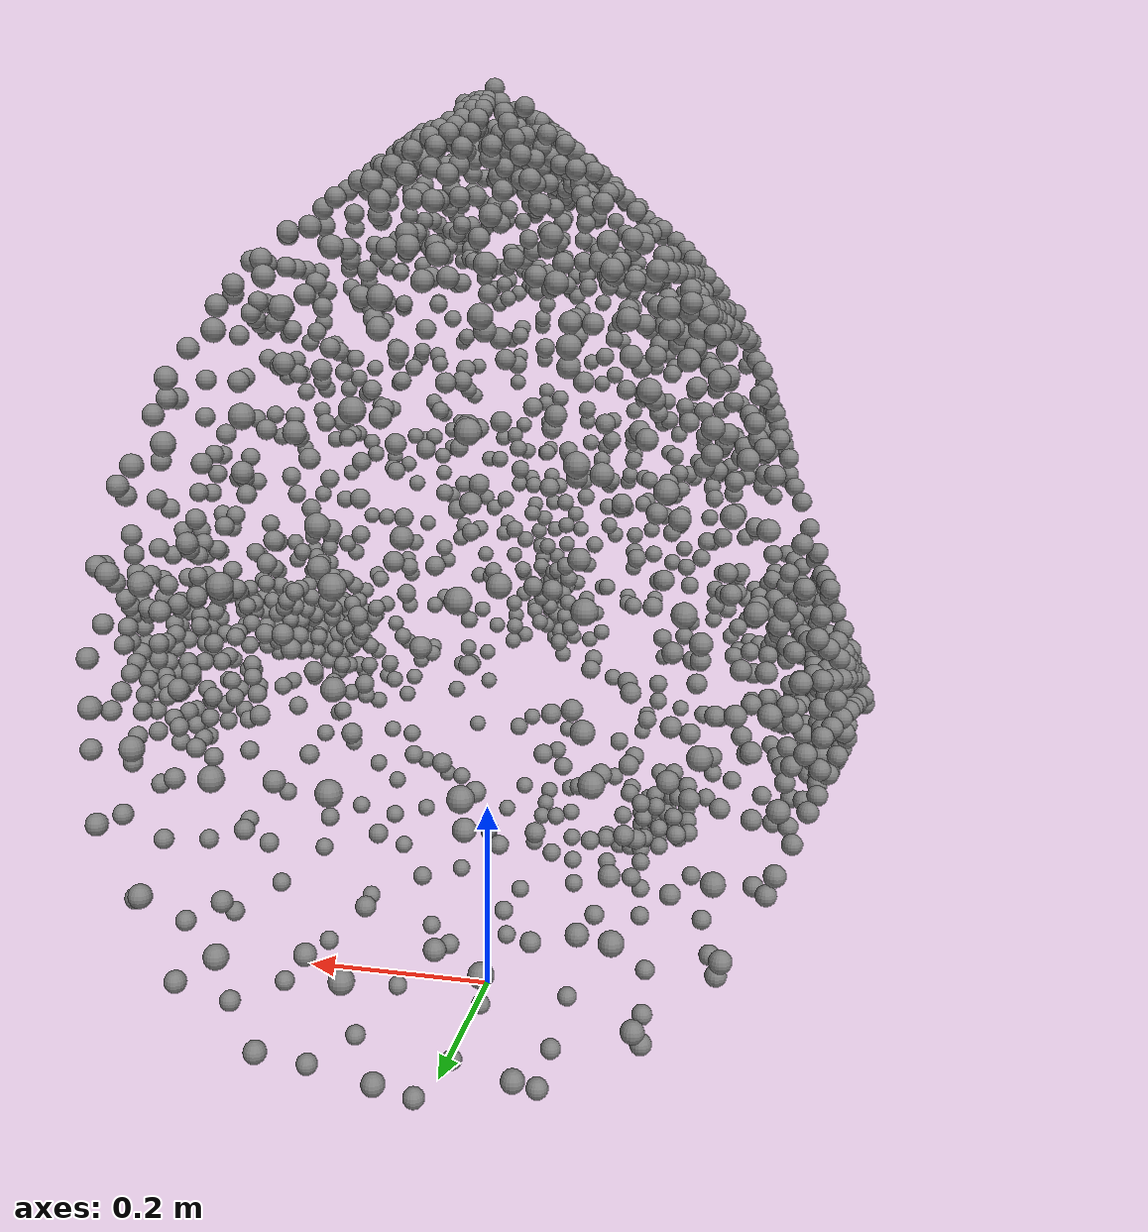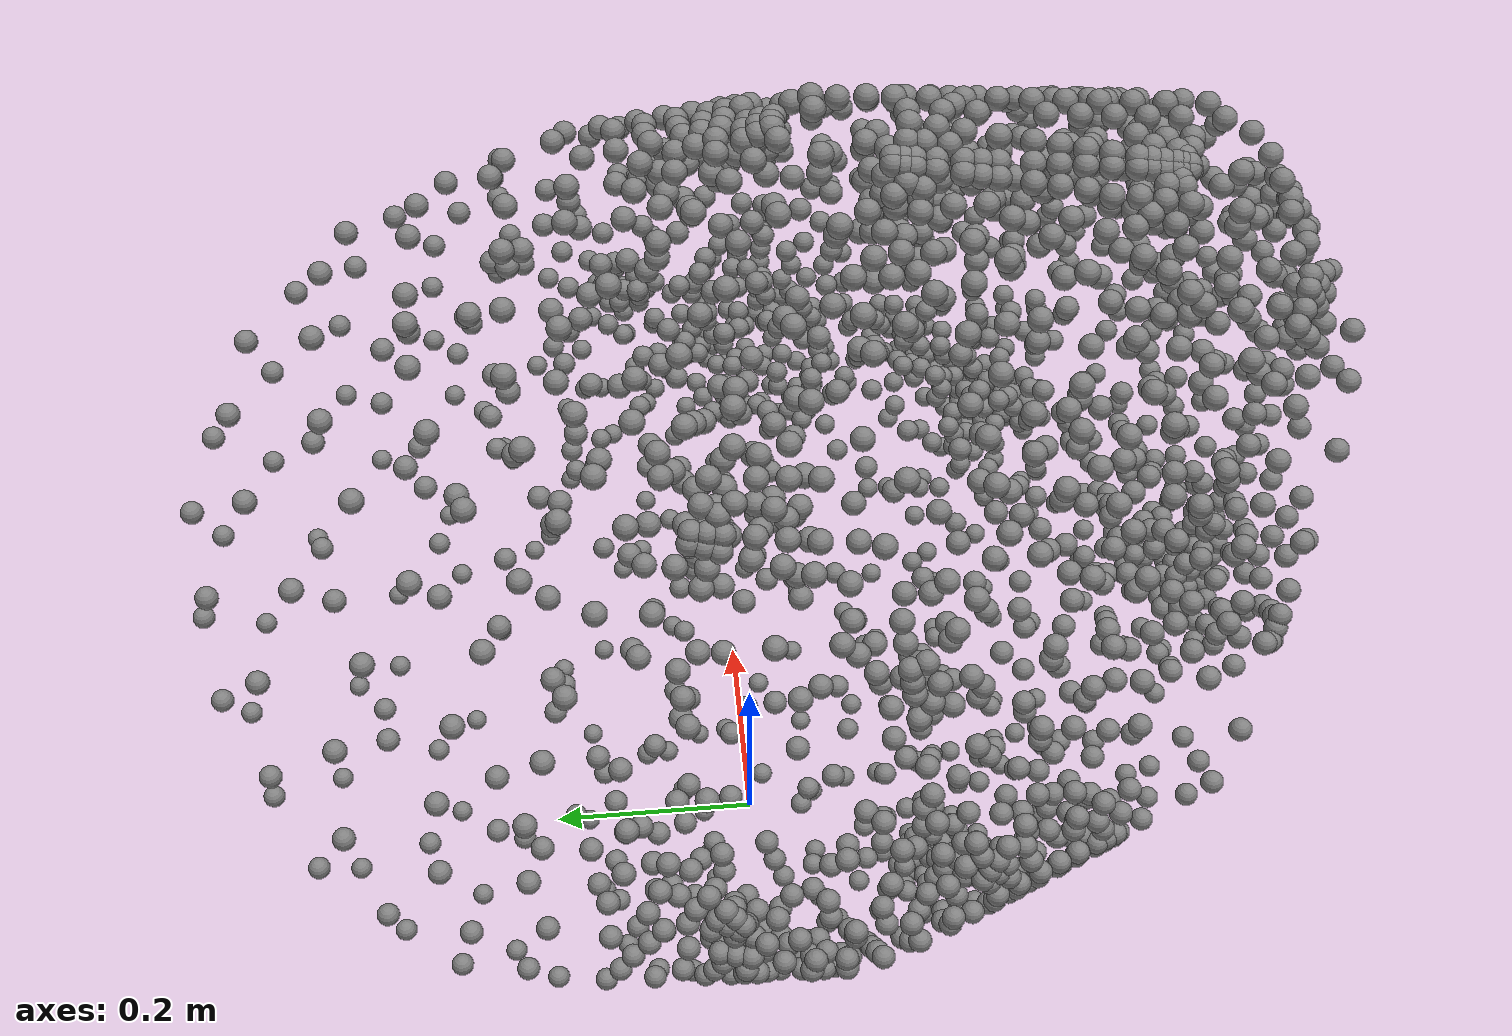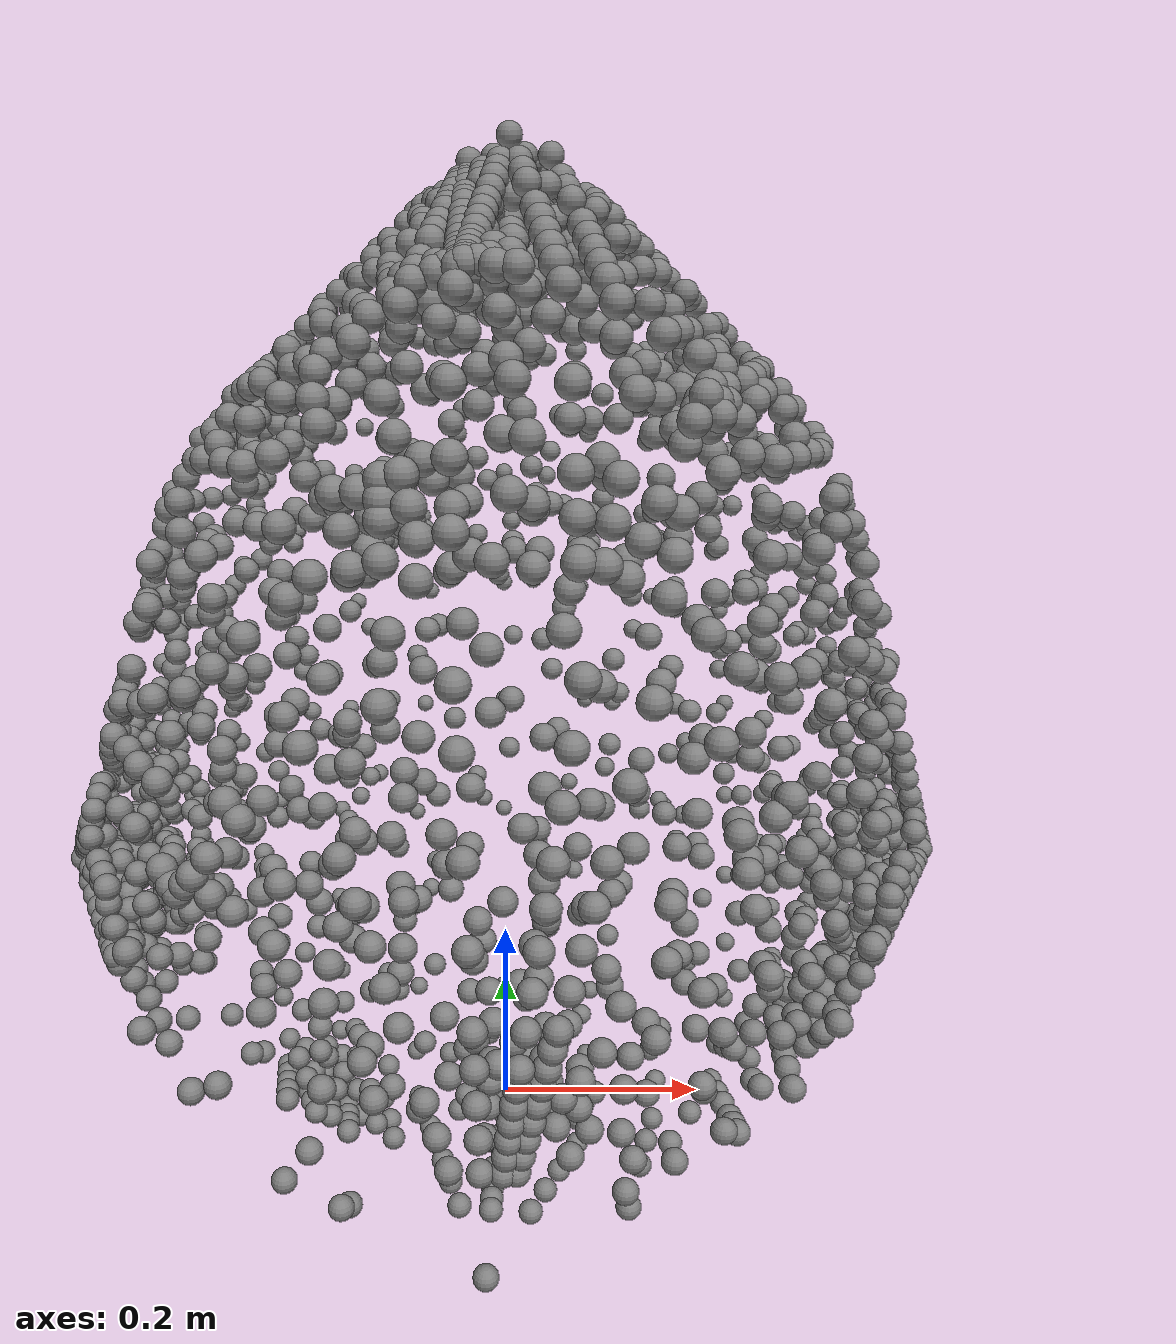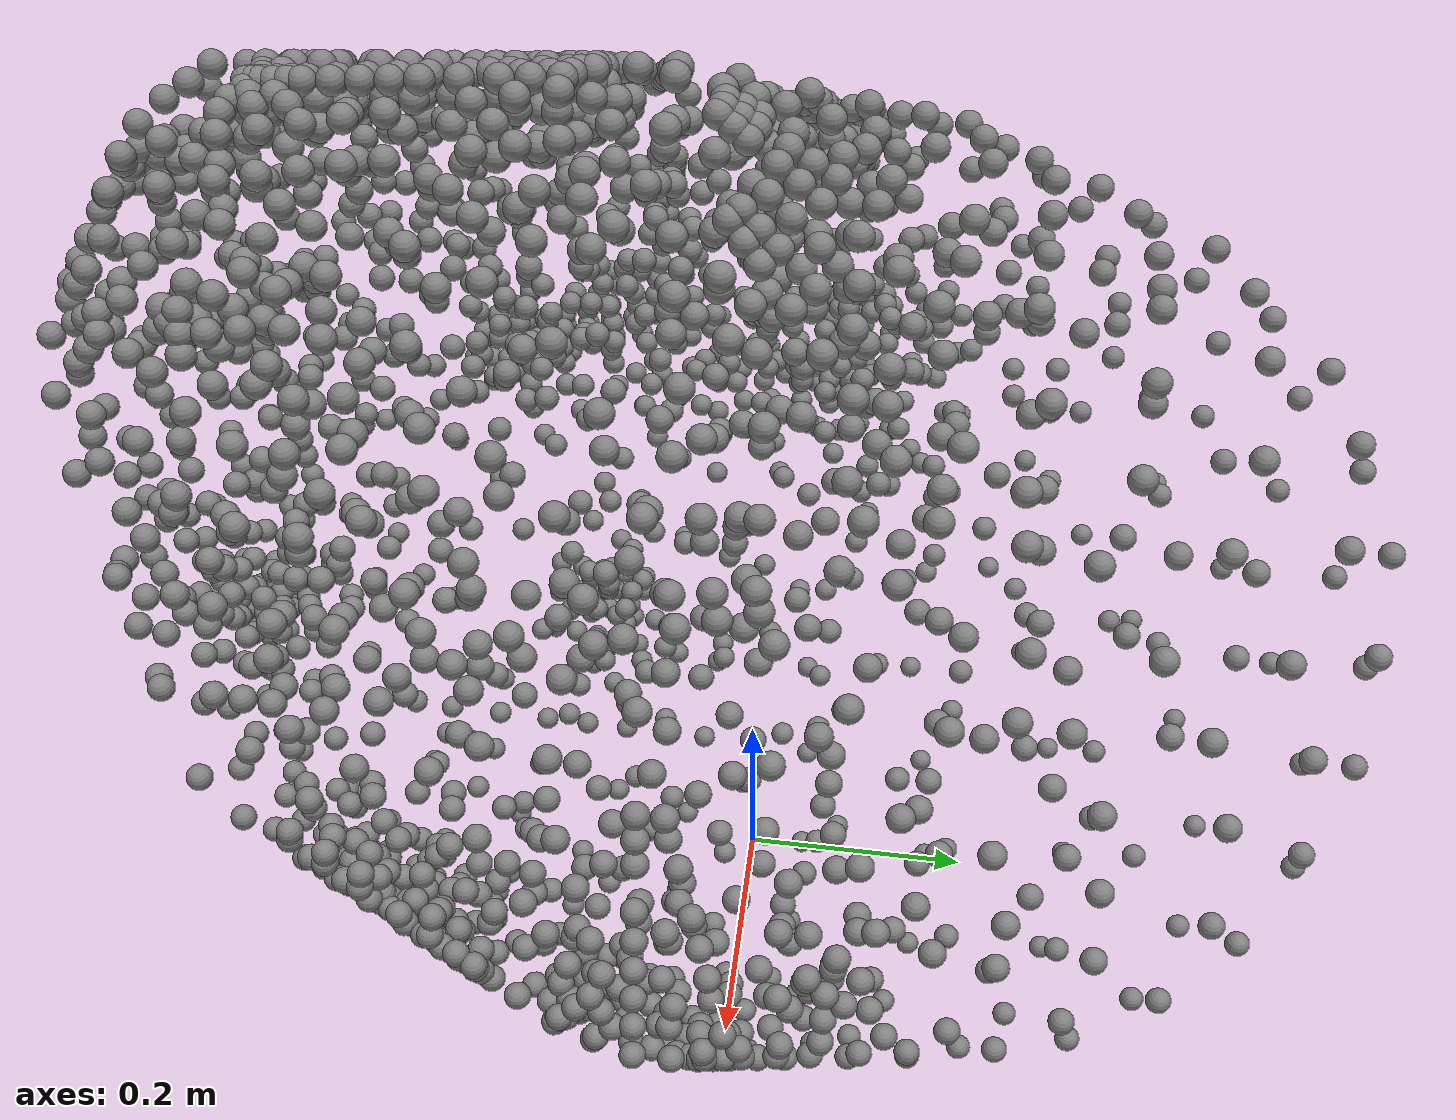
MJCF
<mujoco model="unnamed_model">
  <default>
    <default class="/"/>
  </default>
  <worldbody>
    <body name="point_mass_0">
      <freejoint name="//unnamed_joint_0"/>
      <geom name="point_mass_0" class="/" type="sphere" size="0.01" mass="0.01" pos="0.24500000476837158 -0.38199999928474426 0.44499999284744263"/>
    </body>
    <body name="point_mass_1">
      <freejoint name="//unnamed_joint_1"/>
      <geom name="point_mass_1" class="/" type="sphere" size="0.01" mass="0.01" pos="0.26600000262260437 -0.25699999928474426 0.59200000762939453"/>
    </body>
    <body name="point_mass_2">
      <freejoint name="//unnamed_joint_2"/>
      <geom name="point_mass_2" class="/" type="sphere" size="0.01" mass="0.01" pos="0.21799999475479126 -0.40099999308586121 0.52100002765655518"/>
    </body>
    <body name="point_mass_3">
      <freejoint name="//unnamed_joint_3"/>
      <geom name="point_mass_3" class="/" type="sphere" size="0.01" mass="0.01" pos="0.18799999356269836 -0.14599999785423279 0.13500000536441803"/>
    </body>
    <body name="point_mass_4">
      <freejoint name="//unnamed_joint_4"/>
      <geom name="point_mass_4" class="/" type="sphere" size="0.01" mass="0.01" pos="0.13600000739097595 -0.14599999785423279 0.090000003576278687"/>
    </body>
    <body name="point_mass_5">
      <freejoint name="//unnamed_joint_5"/>
      <geom name="point_mass_5" class="/" type="sphere" size="0.01" mass="0.01" pos="0.20600000023841858 -0.064999997615814209 0.1120000034570694"/>
    </body>
    <body name="point_mass_6">
      <freejoint name="//unnamed_joint_6"/>
      <geom name="point_mass_6" class="/" type="sphere" size="0.01" mass="0.01" pos="0.25299999117851257 -0.050999999046325684 0.6940000057220459"/>
    </body>
    <body name="point_mass_7">
      <freejoint name="//unnamed_joint_7"/>
      <geom name="point_mass_7" class="/" type="sphere" size="0.01" mass="0.01" pos="0.2669999897480011 -0.090000003576278687 0.66200000047683716"/>
    </body>
    <body name="point_mass_8">
      <freejoint name="//unnamed_joint_8"/>
      <geom name="point_mass_8" class="/" type="sphere" size="0.01" mass="0.01" pos="0.27399998903274536 -0.041000001132488251 0.64399999380111694"/>
    </body>
    <body name="point_mass_9">
      <freejoint name="//unnamed_joint_9"/>
      <geom name="point_mass_9" class="/" type="sphere" size="0.01" mass="0.01" pos="0.25200000405311584 -0.075000002980232239 0.17100000381469727"/>
    </body>
    <body name="point_mass_10">
      <freejoint name="//unnamed_joint_10"/>
      <geom name="point_mass_10" class="/" type="sphere" size="0.01" mass="0.01" pos="-0.17499999701976776 -0.3059999942779541 0.75400000810623169"/>
    </body>
    <body name="point_mass_11">
      <freejoint name="//unnamed_joint_11"/>
      <geom name="point_mass_11" class="/" type="sphere" size="0.01" mass="0.01" pos="-0.15700000524520874 -0.34000000357627869 0.76099997758865356"/>
    </body>
    <body name="point_mass_12">
      <freejoint name="//unnamed_joint_12"/>
      <geom name="point_mass_12" class="/" type="sphere" size="0.01" mass="0.01" pos="-0.086000002920627594 -0.35499998927116394 0.83700001239776611"/>
    </body>
    <body name="point_mass_13">
      <freejoint name="//unnamed_joint_13"/>
      <geom name="point_mass_13" class="/" type="sphere" size="0.01" mass="0.01" pos="0.37799999117851257 -0.041999999433755875 0.34099999070167542"/>
    </body>
    <body name="point_mass_14">
      <freejoint name="//unnamed_joint_14"/>
      <geom name="point_mass_14" class="/" type="sphere" size="0.01" mass="0.01" pos="0.37999999523162842 -0.013000000268220901 0.34700000286102295"/>
    </body>
    <body name="point_mass_15">
      <freejoint name="//unnamed_joint_15"/>
      <geom name="point_mass_15" class="/" type="sphere" size="0.01" mass="0.01" pos="-0.10199999809265137 0.19599999487400055 0.78100001811981201"/>
    </body>
    <body name="point_mass_16">
      <freejoint name="//unnamed_joint_16"/>
      <geom name="point_mass_16" class="/" type="sphere" size="0.01" mass="0.01" pos="-0.15199999511241913 0.18600000441074371 0.75300002098083496"/>
    </body>
    <body name="point_mass_17">
      <freejoint name="//unnamed_joint_17"/>
      <geom name="point_mass_17" class="/" type="sphere" size="0.01" mass="0.01" pos="-0.14200000464916229 0.14499999582767487 0.77700001001358032"/>
    </body>
    <body name="point_mass_18">
      <freejoint name="//unnamed_joint_18"/>
      <geom name="point_mass_18" class="/" type="sphere" size="0.01" mass="0.01" pos="0.24899999797344208 -0.24199999868869781 0.66500002145767212"/>
    </body>
    <body name="point_mass_19">
      <freejoint name="//unnamed_joint_19"/>
      <geom name="point_mass_19" class="/" type="sphere" size="0.01" mass="0.01" pos="0.27000001072883606 -0.21500000357627869 0.61699998378753662"/>
    </body>
    <body name="point_mass_20">
      <freejoint name="//unnamed_joint_20"/>
      <geom name="point_mass_20" class="/" type="sphere" size="0.01" mass="0.01" pos="0.25499999523162842 -0.12399999797344208 0.68699997663497925"/>
    </body>
    <body name="point_mass_21">
      <freejoint name="//unnamed_joint_21"/>
      <geom name="point_mass_21" class="/" type="sphere" size="0.01" mass="0.01" pos="-0.065999999642372131 -0.41200000047683716 0.81800001859664917"/>
    </body>
    <body name="point_mass_22">
      <freejoint name="//unnamed_joint_22"/>
      <geom name="point_mass_22" class="/" type="sphere" size="0.01" mass="0.01" pos="-0.027000000700354576 -0.49500000476837158 0.68599998950958252"/>
    </body>
    <body name="point_mass_23">
      <freejoint name="//unnamed_joint_23"/>
      <geom name="point_mass_23" class="/" type="sphere" size="0.01" mass="0.01" pos="-0.029999999329447746 -0.41699999570846558 0.82700002193450928"/>
    </body>
    <body name="point_mass_24">
      <freejoint name="//unnamed_joint_24"/>
      <geom name="point_mass_24" class="/" type="sphere" size="0.01" mass="0.01" pos="-0.21199999749660492 0.11299999803304672 0.72500002384185791"/>
    </body>
    <body name="point_mass_25">
      <freejoint name="//unnamed_joint_25"/>
      <geom name="point_mass_25" class="/" type="sphere" size="0.01" mass="0.01" pos="-0.18400000035762787 0.13400000333786011 0.75300002098083496"/>
    </body>
    <body name="point_mass_26">
      <freejoint name="//unnamed_joint_26"/>
      <geom name="point_mass_26" class="/" type="sphere" size="0.01" mass="0.01" pos="-0.19799999892711639 0.16300000250339508 0.72100001573562622"/>
    </body>
    <body name="point_mass_27">
      <freejoint name="//unnamed_joint_27"/>
      <geom name="point_mass_27" class="/" type="sphere" size="0.01" mass="0.01" pos="0.23000000417232513 -0.15399999916553497 0.72600001096725464"/>
    </body>
    <body name="point_mass_28">
      <freejoint name="//unnamed_joint_28"/>
      <geom name="point_mass_28" class="/" type="sphere" size="0.01" mass="0.01" pos="-0.067000001668930054 -0.48500001430511475 0.66900002956390381"/>
    </body>
    <body name="point_mass_29">
      <freejoint name="//unnamed_joint_29"/>
      <geom name="point_mass_29" class="/" type="sphere" size="0.01" mass="0.01" pos="-0.21899999678134918 0.19599999487400055 0.67900002002716064"/>
    </body>
    <body name="point_mass_30">
      <freejoint name="//unnamed_joint_30"/>
      <geom name="point_mass_30" class="/" type="sphere" size="0.01" mass="0.01" pos="-0.17299999296665192 0.23399999737739563 0.71299999952316284"/>
    </body>
    <body name="point_mass_31">
      <freejoint name="//unnamed_joint_31"/>
      <geom name="point_mass_31" class="/" type="sphere" size="0.01" mass="0.01" pos="0.0040000001899898052 -0.41800001263618469 0.82899999618530273"/>
    </body>
    <body name="point_mass_32">
      <freejoint name="//unnamed_joint_32"/>
      <geom name="point_mass_32" class="/" type="sphere" size="0.01" mass="0.01" pos="0.21400000154972076 -0.22100000083446503 0.73799997568130493"/>
    </body>
    <body name="point_mass_33">
      <freejoint name="//unnamed_joint_33"/>
      <geom name="point_mass_33" class="/" type="sphere" size="0.01" mass="0.01" pos="-0.027000000700354576 -0.05000000074505806 0.91399997472763062"/>
    </body>
    <body name="point_mass_34">
      <freejoint name="//unnamed_joint_34"/>
      <geom name="point_mass_34" class="/" type="sphere" size="0.01" mass="0.01" pos="0.24099999666213989 -0.076999999582767487 0.7160000205039978"/>
    </body>
    <body name="point_mass_35">
      <freejoint name="//unnamed_joint_35"/>
      <geom name="point_mass_35" class="/" type="sphere" size="0.01" mass="0.01" pos="-0.18500000238418579 -0.26899999380111694 0.75599998235702515"/>
    </body>
    <body name="point_mass_36">
      <freejoint name="//unnamed_joint_36"/>
      <geom name="point_mass_36" class="/" type="sphere" size="0.01" mass="0.01" pos="-0.21699999272823334 -0.25999999046325684 0.7149999737739563"/>
    </body>
    <body name="point_mass_37">
      <freejoint name="//unnamed_joint_37"/>
      <geom name="point_mass_37" class="/" type="sphere" size="0.01" mass="0.01" pos="-0.2070000022649765 -0.30500000715255737 0.70800000429153442"/>
    </body>
    <body name="point_mass_38">
      <freejoint name="//unnamed_joint_38"/>
      <geom name="point_mass_38" class="/" type="sphere" size="0.01" mass="0.01" pos="0.14699999988079071 0.32699999213218689 0.70499998331069946"/>
    </body>
    <body name="point_mass_39">
      <freejoint name="//unnamed_joint_39"/>
      <geom name="point_mass_39" class="/" type="sphere" size="0.01" mass="0.01" pos="0.086999997496604919 0.41800001263618469 0.64499998092651367"/>
    </body>
    <body name="point_mass_40">
      <freejoint name="//unnamed_joint_40"/>
      <geom name="point_mass_40" class="/" type="sphere" size="0.01" mass="0.01" pos="0.082000002264976501 0.3449999988079071 0.72299998998641968"/>
    </body>
    <body name="point_mass_41">
      <freejoint name="//unnamed_joint_41"/>
      <geom name="point_mass_41" class="/" type="sphere" size="0.01" mass="0.01" pos="-0.21199999749660492 -0.21899999678134918 0.73199999332427979"/>
    </body>
    <body name="point_mass_42">
      <freejoint name="//unnamed_joint_42"/>
      <geom name="point_mass_42" class="/" type="sphere" size="0.01" mass="0.01" pos="-0.23999999463558197 -0.19799999892711639 0.69099998474121094"/>
    </body>
    <body name="point_mass_43">
      <freejoint name="//unnamed_joint_43"/>
      <geom name="point_mass_43" class="/" type="sphere" size="0.01" mass="0.01" pos="0.067000001668930054 0.26800000667572021 0.77100002765655518"/>
    </body>
    <body name="point_mass_44">
      <freejoint name="//unnamed_joint_44"/>
      <geom name="point_mass_44" class="/" type="sphere" size="0.01" mass="0.01" pos="0.0010000000474974513 0.34900000691413879 0.73100000619888306"/>
    </body>
    <body name="point_mass_45">
      <freejoint name="//unnamed_joint_45"/>
      <geom name="point_mass_45" class="/" type="sphere" size="0.01" mass="0.01" pos="0.1679999977350235 0.38199999928474426 0.61900001764297485"/>
    </body>
    <body name="point_mass_46">
      <freejoint name="//unnamed_joint_46"/>
      <geom name="point_mass_46" class="/" type="sphere" size="0.01" mass="0.01" pos="0.2070000022649765 0.29100000858306885 0.66399997472763062"/>
    </body>
    <body name="point_mass_47">
      <freejoint name="//unnamed_joint_47"/>
      <geom name="point_mass_47" class="/" type="sphere" size="0.01" mass="0.01" pos="-0.23899999260902405 -0.28600001335144043 0.64999997615814209"/>
    </body>
    <body name="point_mass_48">
      <freejoint name="//unnamed_joint_48"/>
      <geom name="point_mass_48" class="/" type="sphere" size="0.01" mass="0.01" pos="-0.18500000238418579 -0.35100001096725464 0.70800000429153442"/>
    </body>
    <body name="point_mass_49">
      <freejoint name="//unnamed_joint_49"/>
      <geom name="point_mass_49" class="/" type="sphere" size="0.01" mass="0.01" pos="-0.19699999690055847 0.28099998831748962 0.6589999794960022"/>
    </body>
    <body name="point_mass_50">
      <freejoint name="//unnamed_joint_50"/>
      <geom name="point_mass_50" class="/" type="sphere" size="0.01" mass="0.01" pos="-0.13400000333786011 -0.37099999189376831 0.77499997615814209"/>
    </body>
    <body name="point_mass_51">
      <freejoint name="//unnamed_joint_51"/>
      <geom name="point_mass_51" class="/" type="sphere" size="0.01" mass="0.01" pos="-0.11800000071525574 0.25799998641014099 0.74199998378753662"/>
    </body>
    <body name="point_mass_52">
      <freejoint name="//unnamed_joint_52"/>
      <geom name="point_mass_52" class="/" type="sphere" size="0.01" mass="0.01" pos="-0.24300000071525574 0.22900000214576721 0.62599998712539673"/>
    </body>
    <body name="point_mass_53">
      <freejoint name="//unnamed_joint_53"/>
      <geom name="point_mass_53" class="/" type="sphere" size="0.01" mass="0.01" pos="-0.0020000000949949026 0.42800000309944153 0.65200001001358032"/>
    </body>
    <body name="point_mass_54">
      <freejoint name="//unnamed_joint_54"/>
      <geom name="point_mass_54" class="/" type="sphere" size="0.01" mass="0.01" pos="0.087999999523162842 0.46599999070167542 0.52700001001358032"/>
    </body>
    <body name="point_mass_55">
      <freejoint name="//unnamed_joint_55"/>
      <geom name="point_mass_55" class="/" type="sphere" size="0.01" mass="0.01" pos="0.17399999499320984 0.41899999976158142 0.51499998569488525"/>
    </body>
    <body name="point_mass_56">
      <freejoint name="//unnamed_joint_56"/>
      <geom name="point_mass_56" class="/" type="sphere" size="0.01" mass="0.01" pos="-0.11299999803304672 -0.4699999988079071 0.63700002431869507"/>
    </body>
    <body name="point_mass_57">
      <freejoint name="//unnamed_joint_57"/>
      <geom name="point_mass_57" class="/" type="sphere" size="0.01" mass="0.01" pos="-0.18400000035762787 -0.23199999332427979 0.76499998569488525"/>
    </body>
    <body name="point_mass_58">
      <freejoint name="//unnamed_joint_58"/>
      <geom name="point_mass_58" class="/" type="sphere" size="0.01" mass="0.01" pos="0.2199999988079071 0.33399999141693115 0.59500002861022949"/>
    </body>
    <body name="point_mass_59">
      <freejoint name="//unnamed_joint_59"/>
      <geom name="point_mass_59" class="/" type="sphere" size="0.01" mass="0.01" pos="-0.26899999380111694 0.16899999976158142 0.59399998188018799"/>
    </body>
    <body name="point_mass_60">
      <freejoint name="//unnamed_joint_60"/>
      <geom name="point_mass_60" class="/" type="sphere" size="0.01" mass="0.01" pos="-0.26899999380111694 0.0060000000521540642 0.63700002431869507"/>
    </body>
    <body name="point_mass_61">
      <freejoint name="//unnamed_joint_61"/>
      <geom name="point_mass_61" class="/" type="sphere" size="0.01" mass="0.01" pos="0.23299999535083771 0.36000001430511475 0.50900000333786011"/>
    </body>
    <body name="point_mass_62">
      <freejoint name="//unnamed_joint_62"/>
      <geom name="point_mass_62" class="/" type="sphere" size="0.01" mass="0.01" pos="0.26899999380111694 0.26600000262260437 0.56800001859664917"/>
    </body>
    <body name="point_mass_63">
      <freejoint name="//unnamed_joint_63"/>
      <geom name="point_mass_63" class="/" type="sphere" size="0.01" mass="0.01" pos="0.21799999475479126 -0.26399999856948853 0.71899998188018799"/>
    </body>
    <body name="point_mass_64">
      <freejoint name="//unnamed_joint_64"/>
      <geom name="point_mass_64" class="/" type="sphere" size="0.01" mass="0.01" pos="0.24099999666213989 -0.28799998760223389 0.65299999713897705"/>
    </body>
    <body name="point_mass_65">
      <freejoint name="//unnamed_joint_65"/>
      <geom name="point_mass_65" class="/" type="sphere" size="0.01" mass="0.01" pos="-0.21600000560283661 -0.40599998831748962 0.51999998092651367"/>
    </body>
    <body name="point_mass_66">
      <freejoint name="//unnamed_joint_66"/>
      <geom name="point_mass_66" class="/" type="sphere" size="0.01" mass="0.01" pos="-0.16500000655651093 -0.43799999356269836 0.58499997854232788"/>
    </body>
    <body name="point_mass_67">
      <freejoint name="//unnamed_joint_67"/>
      <geom name="point_mass_67" class="/" type="sphere" size="0.01" mass="0.01" pos="-0.25 -0.38999998569488525 0.44600000977516174"/>
    </body>
    <body name="point_mass_68">
      <freejoint name="//unnamed_joint_68"/>
      <geom name="point_mass_68" class="/" type="sphere" size="0.01" mass="0.01" pos="-0.10300000011920929 -0.39599999785423279 0.79900002479553223"/>
    </body>
    <body name="point_mass_69">
      <freejoint name="//unnamed_joint_69"/>
      <geom name="point_mass_69" class="/" type="sphere" size="0.01" mass="0.01" pos="0.2460000067949295 0.23800000548362732 0.62800002098083496"/>
    </body>
    <body name="point_mass_70">
      <freejoint name="//unnamed_joint_70"/>
      <geom name="point_mass_70" class="/" type="sphere" size="0.01" mass="0.01" pos="0.079999998211860657 -0.48199999332427979 0.67000001668930054"/>
    </body>
    <body name="point_mass_71">
      <freejoint name="//unnamed_joint_71"/>
      <geom name="point_mass_71" class="/" type="sphere" size="0.01" mass="0.01" pos="0.12099999934434891 -0.46299999952316284 0.63599997758865356"/>
    </body>
    <body name="point_mass_72">
      <freejoint name="//unnamed_joint_72"/>
      <geom name="point_mass_72" class="/" type="sphere" size="0.01" mass="0.01" pos="0.15399999916553497 -0.3880000114440918 0.72000002861022949"/>
    </body>
    <body name="point_mass_73">
      <freejoint name="//unnamed_joint_73"/>
      <geom name="point_mass_73" class="/" type="sphere" size="0.01" mass="0.01" pos="0.20200000703334808 -0.1809999942779541 0.75900000333786011"/>
    </body>
    <body name="point_mass_74">
      <freejoint name="//unnamed_joint_74"/>
      <geom name="point_mass_74" class="/" type="sphere" size="0.01" mass="0.01" pos="0.041000001132488251 -0.49300000071525574 0.68800002336502075"/>
    </body>
    <body name="point_mass_75">
      <freejoint name="//unnamed_joint_75"/>
      <geom name="point_mass_75" class="/" type="sphere" size="0.01" mass="0.01" pos="0.18500000238418579 -0.23499999940395355 0.77100002765655518"/>
    </body>
    <body name="point_mass_76">
      <freejoint name="//unnamed_joint_76"/>
      <geom name="point_mass_76" class="/" type="sphere" size="0.01" mass="0.01" pos="0.32600000500679016 -0.19200000166893005 0.42300000786781311"/>
    </body>
    <body name="point_mass_77">
      <freejoint name="//unnamed_joint_77"/>
      <geom name="point_mass_77" class="/" type="sphere" size="0.01" mass="0.01" pos="0.35499998927116394 -0.1289999932050705 0.37000000476837158"/>
    </body>
    <body name="point_mass_78">
      <freejoint name="//unnamed_joint_78"/>
      <geom name="point_mass_78" class="/" type="sphere" size="0.01" mass="0.01" pos="0.16200000047683716 -0.23600000143051147 0.7929999828338623"/>
    </body>
    <body name="point_mass_79">
      <freejoint name="//unnamed_joint_79"/>
      <geom name="point_mass_79" class="/" type="sphere" size="0.01" mass="0.01" pos="0.20800000429153442 -0.097999997437000275 0.75400000810623169"/>
    </body>
    <body name="point_mass_80">
      <freejoint name="//unnamed_joint_80"/>
      <geom name="point_mass_80" class="/" type="sphere" size="0.01" mass="0.01" pos="0.22300000488758087 -0.335999995470047 0.63899999856948853"/>
    </body>
    <body name="point_mass_81">
      <freejoint name="//unnamed_joint_81"/>
      <geom name="point_mass_81" class="/" type="sphere" size="0.01" mass="0.01" pos="0.17000000178813934 -0.43200001120567322 0.58499997854232788"/>
    </body>
    <body name="point_mass_82">
      <freejoint name="//unnamed_joint_82"/>
      <geom name="point_mass_82" class="/" type="sphere" size="0.01" mass="0.01" pos="0.18500000238418579 -0.14000000059604645 0.77799999713897705"/>
    </body>
    <body name="point_mass_83">
      <freejoint name="//unnamed_joint_83"/>
      <geom name="point_mass_83" class="/" type="sphere" size="0.01" mass="0.01" pos="0.2669999897480011 0.0040000001899898052 0.16500000655651093"/>
    </body>
    <body name="point_mass_84">
      <freejoint name="//unnamed_joint_84"/>
      <geom name="point_mass_84" class="/" type="sphere" size="0.01" mass="0.01" pos="0.27900001406669617 0.083999998867511749 0.17200000584125519"/>
    </body>
    <body name="point_mass_85">
      <freejoint name="//unnamed_joint_85"/>
      <geom name="point_mass_85" class="/" type="sphere" size="0.01" mass="0.01" pos="-0.17499999701976776 -0.19599999487400055 0.77799999713897705"/>
    </body>
    <body name="point_mass_86">
      <freejoint name="//unnamed_joint_86"/>
      <geom name="point_mass_86" class="/" type="sphere" size="0.01" mass="0.01" pos="-0.15999999642372131 -0.23399999737739563 0.78899997472763062"/>
    </body>
    <body name="point_mass_87">
      <freejoint name="//unnamed_joint_87"/>
      <geom name="point_mass_87" class="/" type="sphere" size="0.01" mass="0.01" pos="0.37000000476837158 -0.071999996900558472 0.34400001168251038"/>
    </body>
    <body name="point_mass_88">
      <freejoint name="//unnamed_joint_88"/>
      <geom name="point_mass_88" class="/" type="sphere" size="0.01" mass="0.01" pos="0.090000003576278687 -0.35499998927116394 0.8410000205039978"/>
    </body>
    <body name="point_mass_89">
      <freejoint name="//unnamed_joint_89"/>
      <geom name="point_mass_89" class="/" type="sphere" size="0.01" mass="0.01" pos="0.164000004529953 -0.26800000667572021 0.78899997472763062"/>
    </body>
    <body name="point_mass_90">
      <freejoint name="//unnamed_joint_90"/>
      <geom name="point_mass_90" class="/" type="sphere" size="0.01" mass="0.01" pos="-0.20600000023841858 -0.097999997437000275 0.74900001287460327"/>
    </body>
    <body name="point_mass_91">
      <freejoint name="//unnamed_joint_91"/>
      <geom name="point_mass_91" class="/" type="sphere" size="0.01" mass="0.01" pos="0.36399999260902405 -0.10100000351667404 0.3529999852180481"/>
    </body>
    <body name="point_mass_92">
      <freejoint name="//unnamed_joint_92"/>
      <geom name="point_mass_92" class="/" type="sphere" size="0.01" mass="0.01" pos="0.1550000011920929 -0.29399999976158142 0.79000002145767212"/>
    </body>
    <body name="point_mass_93">
      <freejoint name="//unnamed_joint_93"/>
      <geom name="point_mass_93" class="/" type="sphere" size="0.01" mass="0.01" pos="0.20800000429153442 -0.36100000143051147 0.30700001120567322"/>
    </body>
    <body name="point_mass_94">
      <freejoint name="//unnamed_joint_94"/>
      <geom name="point_mass_94" class="/" type="sphere" size="0.01" mass="0.01" pos="0.14000000059604645 -0.36899998784065247 0.77499997615814209"/>
    </body>
    <body name="point_mass_95">
      <freejoint name="//unnamed_joint_95"/>
      <geom name="point_mass_95" class="/" type="sphere" size="0.01" mass="0.01" pos="0.16200000047683716 -0.34299999475479126 0.76499998569488525"/>
    </body>
    <body name="point_mass_96">
      <freejoint name="//unnamed_joint_96"/>
      <geom name="point_mass_96" class="/" type="sphere" size="0.01" mass="0.01" pos="0.071000002324581146 -0.41100001335144043 0.81999999284744263"/>
    </body>
    <body name="point_mass_97">
      <freejoint name="//unnamed_joint_97"/>
      <geom name="point_mass_97" class="/" type="sphere" size="0.01" mass="0.01" pos="0.035999998450279236 -0.41699999570846558 0.82700002193450928"/>
    </body>
    <body name="point_mass_98">
      <freejoint name="//unnamed_joint_98"/>
      <geom name="point_mass_98" class="/" type="sphere" size="0.01" mass="0.01" pos="0.10499999672174454 -0.39300000667572021 0.80099999904632568"/>
    </body>
    <body name="point_mass_99">
      <freejoint name="//unnamed_joint_99"/>
      <geom name="point_mass_99" class="/" type="sphere" size="0.01" mass="0.01" pos="-0.23800000548362732 -0.079000003635883331 0.71200001239776611"/>
    </body>
    <body name="point_mass_100">
      <freejoint name="//unnamed_joint_100"/>
      <geom name="point_mass_100" class="/" type="sphere" size="0.01" mass="0.01" pos="0.061999998986721039 -0.36700001358985901 0.86100000143051147"/>
    </body>
    <body name="point_mass_101">
      <freejoint name="//unnamed_joint_101"/>
      <geom name="point_mass_101" class="/" type="sphere" size="0.01" mass="0.01" pos="-0.26600000262260437 -0.090999998152256012 0.65499997138977051"/>
    </body>
    <body name="point_mass_102">
      <freejoint name="//unnamed_joint_102"/>
      <geom name="point_mass_102" class="/" type="sphere" size="0.01" mass="0.01" pos="-0.25200000405311584 -0.052000001072883606 0.68800002336502075"/>
    </body>
    <body name="point_mass_103">
      <freejoint name="//unnamed_joint_103"/>
      <geom name="point_mass_103" class="/" type="sphere" size="0.01" mass="0.01" pos="0.032000001519918442 -0.37200000882148743 0.87099999189376831"/>
    </body>
    <body name="point_mass_104">
      <freejoint name="//unnamed_joint_104"/>
      <geom name="point_mass_104" class="/" type="sphere" size="0.01" mass="0.01" pos="-0.25200000405311584 -0.12600000202655792 0.68199998140335083"/>
    </body>
    <body name="point_mass_105">
      <freejoint name="//unnamed_joint_105"/>
      <geom name="point_mass_105" class="/" type="sphere" size="0.01" mass="0.01" pos="0.23399999737739563 -0.36700001358985901 0.37000000476837158"/>
    </body>
    <body name="point_mass_106">
      <freejoint name="//unnamed_joint_106"/>
      <geom name="point_mass_106" class="/" type="sphere" size="0.01" mass="0.01" pos="-0.2460000067949295 -0.23999999463558197 0.66500002145767212"/>
    </body>
    <body name="point_mass_107">
      <freejoint name="//unnamed_joint_107"/>
      <geom name="point_mass_107" class="/" type="sphere" size="0.01" mass="0.01" pos="-0.2630000114440918 0.25900000333786011 0.55800002813339233"/>
    </body>
    <body name="point_mass_108">
      <freejoint name="//unnamed_joint_108"/>
      <geom name="point_mass_108" class="/" type="sphere" size="0.01" mass="0.01" pos="-0.289000004529953 0.19099999964237213 0.53700000047683716"/>
    </body>
    <body name="point_mass_109">
      <freejoint name="//unnamed_joint_109"/>
      <geom name="point_mass_109" class="/" type="sphere" size="0.01" mass="0.01" pos="-0.26800000667572021 -0.21299999952316284 0.61000001430511475"/>
    </body>
    <body name="point_mass_110">
      <freejoint name="//unnamed_joint_110"/>
      <geom name="point_mass_110" class="/" type="sphere" size="0.01" mass="0.01" pos="0.20999999344348907 -0.30899998545646667 0.71299999952316284"/>
    </body>
    <body name="point_mass_111">
      <freejoint name="//unnamed_joint_111"/>
      <geom name="point_mass_111" class="/" type="sphere" size="0.01" mass="0.01" pos="0.18000000715255737 -0.30899998545646667 0.75800001621246338"/>
    </body>
    <body name="point_mass_112">
      <freejoint name="//unnamed_joint_112"/>
      <geom name="point_mass_112" class="/" type="sphere" size="0.01" mass="0.01" pos="0.18999999761581421 -0.3529999852180481 0.71299999952316284"/>
    </body>
    <body name="point_mass_113">
      <freejoint name="//unnamed_joint_113"/>
      <geom name="point_mass_113" class="/" type="sphere" size="0.01" mass="0.01" pos="0.18600000441074371 -0.27300000190734863 0.76200002431869507"/>
    </body>
    <body name="point_mass_114">
      <freejoint name="//unnamed_joint_114"/>
      <geom name="point_mass_114" class="/" type="sphere" size="0.01" mass="0.01" pos="-0.28799998760223389 -0.012000000104308128 0.59399998188018799"/>
    </body>
    <body name="point_mass_115">
      <freejoint name="//unnamed_joint_115"/>
      <geom name="point_mass_115" class="/" type="sphere" size="0.01" mass="0.01" pos="-0.21699999272823334 0.32600000500679016 0.58600002527236938"/>
    </body>
    <body name="point_mass_116">
      <freejoint name="//unnamed_joint_116"/>
      <geom name="point_mass_116" class="/" type="sphere" size="0.01" mass="0.01" pos="-0.27300000190734863 -0.045000001788139343 0.63999998569488525"/>
    </body>
    <body name="point_mass_117">
      <freejoint name="//unnamed_joint_117"/>
      <geom name="point_mass_117" class="/" type="sphere" size="0.01" mass="0.01" pos="-0.32499998807907104 -0.19499999284744263 0.4440000057220459"/>
    </body>
    <body name="point_mass_118">
      <freejoint name="//unnamed_joint_118"/>
      <geom name="point_mass_118" class="/" type="sphere" size="0.01" mass="0.01" pos="0.17800000309944153 0.43799999356269836 0.38899999856948853"/>
    </body>
    <body name="point_mass_119">
      <freejoint name="//unnamed_joint_119"/>
      <geom name="point_mass_119" class="/" type="sphere" size="0.01" mass="0.01" pos="0.28799998760223389 0.27500000596046448 0.49700000882148743"/>
    </body>
    <body name="point_mass_120">
      <freejoint name="//unnamed_joint_120"/>
      <geom name="point_mass_120" class="/" type="sphere" size="0.01" mass="0.01" pos="0.3059999942779541 0.27000001072883606 0.32600000500679016"/>
    </body>
    <body name="point_mass_121">
      <freejoint name="//unnamed_joint_121"/>
      <geom name="point_mass_121" class="/" type="sphere" size="0.01" mass="0.01" pos="0.25 0.36899998784065247 0.3970000147819519"/>
    </body>
    <body name="point_mass_122">
      <freejoint name="//unnamed_joint_122"/>
      <geom name="point_mass_122" class="/" type="sphere" size="0.01" mass="0.01" pos="0.29800000786781311 0.28200000524520874 0.41499999165534973"/>
    </body>
    <body name="point_mass_123">
      <freejoint name="//unnamed_joint_123"/>
      <geom name="point_mass_123" class="/" type="sphere" size="0.01" mass="0.01" pos="0.15000000596046448 0.14800000190734863 0.78799998760223389"/>
    </body>
    <body name="point_mass_124">
      <freejoint name="//unnamed_joint_124"/>
      <geom name="point_mass_124" class="/" type="sphere" size="0.01" mass="0.01" pos="0.15999999642372131 0.18999999761581421 0.7630000114440918"/>
    </body>
    <body name="point_mass_125">
      <freejoint name="//unnamed_joint_125"/>
      <geom name="point_mass_125" class="/" type="sphere" size="0.01" mass="0.01" pos="0.10999999940395355 0.20000000298023224 0.79000002145767212"/>
    </body>
    <body name="point_mass_126">
      <freejoint name="//unnamed_joint_126"/>
      <geom name="point_mass_126" class="/" type="sphere" size="0.01" mass="0.01" pos="0.1809999942779541 0.24099999666213989 0.72299998998641968"/>
    </body>
    <body name="point_mass_127">
      <freejoint name="//unnamed_joint_127"/>
      <geom name="point_mass_127" class="/" type="sphere" size="0.01" mass="0.01" pos="-0.057999998331069946 -0.36700001358985901 0.85900002717971802"/>
    </body>
    <body name="point_mass_128">
      <freejoint name="//unnamed_joint_128"/>
      <geom name="point_mass_128" class="/" type="sphere" size="0.01" mass="0.01" pos="0.0030000000260770321 -0.046999998390674591 0.93199998140335083"/>
    </body>
    <body name="point_mass_129">
      <freejoint name="//unnamed_joint_129"/>
      <geom name="point_mass_129" class="/" type="sphere" size="0.01" mass="0.01" pos="-0.3059999942779541 0.20999999344348907 0.47400000691413879"/>
    </body>
    <body name="point_mass_130">
      <freejoint name="//unnamed_joint_130"/>
      <geom name="point_mass_130" class="/" type="sphere" size="0.01" mass="0.01" pos="-0.37299999594688416 0.020999999716877937 0.37000000476837158"/>
    </body>
    <body name="point_mass_131">
      <freejoint name="//unnamed_joint_131"/>
      <geom name="point_mass_131" class="/" type="sphere" size="0.01" mass="0.01" pos="0.29699999094009399 0.19699999690055847 0.54900002479553223"/>
    </body>
    <body name="point_mass_132">
      <freejoint name="//unnamed_joint_132"/>
      <geom name="point_mass_132" class="/" type="sphere" size="0.01" mass="0.01" pos="0.21799999475479126 0.11699999868869781 0.73199999332427979"/>
    </body>
    <body name="point_mass_133">
      <freejoint name="//unnamed_joint_133"/>
      <geom name="point_mass_133" class="/" type="sphere" size="0.01" mass="0.01" pos="0.093000002205371857 0.48199999332427979 0.38600000739097595"/>
    </body>
    <body name="point_mass_134">
      <freejoint name="//unnamed_joint_134"/>
      <geom name="point_mass_134" class="/" type="sphere" size="0.01" mass="0.01" pos="0.22599999606609344 0.20399999618530273 0.68500000238418579"/>
    </body>
    <body name="point_mass_135">
      <freejoint name="//unnamed_joint_135"/>
      <geom name="point_mass_135" class="/" type="sphere" size="0.01" mass="0.01" pos="-0.0020000000949949026 0.49500000476837158 0.38699999451637268"/>
    </body>
    <body name="point_mass_136">
      <freejoint name="//unnamed_joint_136"/>
      <geom name="point_mass_136" class="/" type="sphere" size="0.01" mass="0.01" pos="-0.1120000034570694 0.38699999451637268 0.11800000071525574"/>
    </body>
    <body name="point_mass_137">
      <freejoint name="//unnamed_joint_137"/>
      <geom name="point_mass_137" class="/" type="sphere" size="0.01" mass="0.01" pos="-0.20100000500679016 0.34099999070167542 0.14699999988079071"/>
    </body>
    <body name="point_mass_138">
      <freejoint name="//unnamed_joint_138"/>
      <geom name="point_mass_138" class="/" type="sphere" size="0.01" mass="0.01" pos="-0.19200000166893005 0.40700000524520874 0.25299999117851257"/>
    </body>
    <body name="point_mass_139">
      <freejoint name="//unnamed_joint_139"/>
      <geom name="point_mass_139" class="/" type="sphere" size="0.01" mass="0.01" pos="0.18899999558925629 0.41499999165534973 0.25699999928474426"/>
    </body>
    <body name="point_mass_140">
      <freejoint name="//unnamed_joint_140"/>
      <geom name="point_mass_140" class="/" type="sphere" size="0.01" mass="0.01" pos="0.10199999809265137 0.46599999070167542 0.23800000548362732"/>
    </body>
    <body name="point_mass_141">
      <freejoint name="//unnamed_joint_141"/>
      <geom name="point_mass_141" class="/" type="sphere" size="0.01" mass="0.01" pos="-0.10199999809265137 0.45199999213218689 0.23899999260902405"/>
    </body>
    <body name="point_mass_142">
      <freejoint name="//unnamed_joint_142"/>
      <geom name="point_mass_142" class="/" type="sphere" size="0.01" mass="0.01" pos="-0.0020000000949949026 0.40700000524520874 0.1120000034570694"/>
    </body>
    <body name="point_mass_143">
      <freejoint name="//unnamed_joint_143"/>
      <geom name="point_mass_143" class="/" type="sphere" size="0.01" mass="0.01" pos="-0.0030000000260770321 0.29600000381469727 0.035999998450279236"/>
    </body>
    <body name="point_mass_144">
      <freejoint name="//unnamed_joint_144"/>
      <geom name="point_mass_144" class="/" type="sphere" size="0.01" mass="0.01" pos="0.26100000739097595 0.34799998998641968 0.28700000047683716"/>
    </body>
    <body name="point_mass_145">
      <freejoint name="//unnamed_joint_145"/>
      <geom name="point_mass_145" class="/" type="sphere" size="0.01" mass="0.01" pos="-0.0020000000949949026 0.47699999809265137 0.23499999940395355"/>
    </body>
    <body name="point_mass_146">
      <freejoint name="//unnamed_joint_146"/>
      <geom name="point_mass_146" class="/" type="sphere" size="0.01" mass="0.01" pos="0.37200000882148743 0.024000000208616257 0.38100001215934753"/>
    </body>
    <body name="point_mass_147">
      <freejoint name="//unnamed_joint_147"/>
      <geom name="point_mass_147" class="/" type="sphere" size="0.01" mass="0.01" pos="-0.10999999940395355 0.27599999308586121 0.048000000417232513"/>
    </body>
    <body name="point_mass_148">
      <freejoint name="//unnamed_joint_148"/>
      <geom name="point_mass_148" class="/" type="sphere" size="0.01" mass="0.01" pos="0.31400001049041748 0.21299999952316284 0.48500001430511475"/>
    </body>
    <body name="point_mass_149">
      <freejoint name="//unnamed_joint_149"/>
      <geom name="point_mass_149" class="/" type="sphere" size="0.01" mass="0.01" pos="0.3190000057220459 0.21199999749660492 0.42899999022483826"/>
    </body>
    <body name="point_mass_150">
      <freejoint name="//unnamed_joint_150"/>
      <geom name="point_mass_150" class="/" type="sphere" size="0.01" mass="0.01" pos="0.37700000405311584 0.0099999997764825821 0.35899999737739563"/>
    </body>
    <body name="point_mass_151">
      <freejoint name="//unnamed_joint_151"/>
      <geom name="point_mass_151" class="/" type="sphere" size="0.01" mass="0.01" pos="0.18999999761581421 0.1379999965429306 0.76200002431869507"/>
    </body>
    <body name="point_mass_152">
      <freejoint name="//unnamed_joint_152"/>
      <geom name="point_mass_152" class="/" type="sphere" size="0.01" mass="0.01" pos="0.10499999672174454 0.39100000262260437 0.11800000071525574"/>
    </body>
    <body name="point_mass_153">
      <freejoint name="//unnamed_joint_153"/>
      <geom name="point_mass_153" class="/" type="sphere" size="0.01" mass="0.01" pos="-0.075999997556209564 0.34299999475479126 0.71700000762939453"/>
    </body>
    <body name="point_mass_154">
      <freejoint name="//unnamed_joint_154"/>
      <geom name="point_mass_154" class="/" type="sphere" size="0.01" mass="0.01" pos="-0.048999998718500137 0.1940000057220459 0.79799997806549072"/>
    </body>
    <body name="point_mass_155">
      <freejoint name="//unnamed_joint_155"/>
      <geom name="point_mass_155" class="/" type="sphere" size="0.01" mass="0.01" pos="-0.19599999487400055 0.24300000071525574 0.082999996840953827"/>
    </body>
    <body name="point_mass_156">
      <freejoint name="//unnamed_joint_156"/>
      <geom name="point_mass_156" class="/" type="sphere" size="0.01" mass="0.01" pos="-0.25699999928474426 0.20200000703334808 0.13500000536441803"/>
    </body>
    <body name="point_mass_157">
      <freejoint name="//unnamed_joint_157"/>
      <geom name="point_mass_157" class="/" type="sphere" size="0.01" mass="0.01" pos="-0.26600000262260437 0.28600001335144043 0.18899999558925629"/>
    </body>
    <body name="point_mass_158">
      <freejoint name="//unnamed_joint_158"/>
      <geom name="point_mass_158" class="/" type="sphere" size="0.01" mass="0.01" pos="-0.14000000059604645 0.32100000977516174 0.6940000057220459"/>
    </body>
    <body name="point_mass_159">
      <freejoint name="//unnamed_joint_159"/>
      <geom name="point_mass_159" class="/" type="sphere" size="0.01" mass="0.01" pos="0.19499999284744263 0.34700000286102295 0.14900000393390656"/>
    </body>
    <body name="point_mass_160">
      <freejoint name="//unnamed_joint_160"/>
      <geom name="point_mass_160" class="/" type="sphere" size="0.01" mass="0.01" pos="0.10300000011920929 0.27799999713897705 0.045000001788139343"/>
    </body>
    <body name="point_mass_161">
      <freejoint name="//unnamed_joint_161"/>
      <geom name="point_mass_161" class="/" type="sphere" size="0.01" mass="0.01" pos="0.25900000333786011 0.289000004529953 0.19499999284744263"/>
    </body>
    <body name="point_mass_162">
      <freejoint name="//unnamed_joint_162"/>
      <geom name="point_mass_162" class="/" type="sphere" size="0.01" mass="0.01" pos="0.18999999761581421 0.2460000067949295 0.081000000238418579"/>
    </body>
    <body name="point_mass_163">
      <freejoint name="//unnamed_joint_163"/>
      <geom name="point_mass_163" class="/" type="sphere" size="0.01" mass="0.01" pos="0.17200000584125519 -0.35499998927116394 0.26100000739097595"/>
    </body>
    <body name="point_mass_164">
      <freejoint name="//unnamed_joint_164"/>
      <geom name="point_mass_164" class="/" type="sphere" size="0.01" mass="0.01" pos="0.097000002861022949 0.15800000727176666 0.010999999940395355"/>
    </body>
    <body name="point_mass_165">
      <freejoint name="//unnamed_joint_165"/>
      <geom name="point_mass_165" class="/" type="sphere" size="0.01" mass="0.01" pos="-0.0040000001899898052 0.16699999570846558 0.0020000000949949026"/>
    </body>
    <body name="point_mass_166">
      <freejoint name="//unnamed_joint_166"/>
      <geom name="point_mass_166" class="/" type="sphere" size="0.01" mass="0.01" pos="0.067000001668930054 -0.15099999308586121 0.064999997615814209"/>
    </body>
    <body name="point_mass_167">
      <freejoint name="//unnamed_joint_167"/>
      <geom name="point_mass_167" class="/" type="sphere" size="0.01" mass="0.01" pos="0.079000003635883331 -0.061000000685453415 0.032000001519918442"/>
    </body>
    <body name="point_mass_168">
      <freejoint name="//unnamed_joint_168"/>
      <geom name="point_mass_168" class="/" type="sphere" size="0.01" mass="0.01" pos="0.14900000393390656 -0.059000000357627869 0.061999998986721039"/>
    </body>
    <body name="point_mass_169">
      <freejoint name="//unnamed_joint_169"/>
      <geom name="point_mass_169" class="/" type="sphere" size="0.01" mass="0.01" pos="0.094999998807907104 -0.34900000691413879 0.18199999630451202"/>
    </body>
    <body name="point_mass_170">
      <freejoint name="//unnamed_joint_170"/>
      <geom name="point_mass_170" class="/" type="sphere" size="0.01" mass="0.01" pos="0.29199999570846558 0.16099999845027924 0.20000000298023224"/>
    </body>
    <body name="point_mass_171">
      <freejoint name="//unnamed_joint_171"/>
      <geom name="point_mass_171" class="/" type="sphere" size="0.01" mass="0.01" pos="0.30000001192092896 0.22699999809265137 0.24899999797344208"/>
    </body>
    <body name="point_mass_172">
      <freejoint name="//unnamed_joint_172"/>
      <geom name="point_mass_172" class="/" type="sphere" size="0.01" mass="0.01" pos="-0.0020000000949949026 0.47900000214576721 0.53299999237060547"/>
    </body>
    <body name="point_mass_173">
      <freejoint name="//unnamed_joint_173"/>
      <geom name="point_mass_173" class="/" type="sphere" size="0.01" mass="0.01" pos="-0.083999998867511749 0.414000004529953 0.63700002431869507"/>
    </body>
    <body name="point_mass_174">
      <freejoint name="//unnamed_joint_174"/>
      <geom name="point_mass_174" class="/" type="sphere" size="0.01" mass="0.01" pos="-0.15700000524520874 0.37900000810623169 0.61100000143051147"/>
    </body>
    <body name="point_mass_175">
      <freejoint name="//unnamed_joint_175"/>
      <geom name="point_mass_175" class="/" type="sphere" size="0.01" mass="0.01" pos="-0.014000000432133675 -0.40299999713897705 0.16599999368190765"/>
    </body>
    <body name="point_mass_176">
      <freejoint name="//unnamed_joint_176"/>
      <geom name="point_mass_176" class="/" type="sphere" size="0.01" mass="0.01" pos="0.25099998712539673 0.20499999821186066 0.13699999451637268"/>
    </body>
    <body name="point_mass_177">
      <freejoint name="//unnamed_joint_177"/>
      <geom name="point_mass_177" class="/" type="sphere" size="0.01" mass="0.01" pos="0.23999999463558197 0.11299999803304672 0.1080000028014183"/>
    </body>
    <body name="point_mass_178">
      <freejoint name="//unnamed_joint_178"/>
      <geom name="point_mass_178" class="/" type="sphere" size="0.01" mass="0.01" pos="-0.089000001549720764 0.46399998664855957 0.52399998903274536"/>
    </body>
    <body name="point_mass_179">
      <freejoint name="//unnamed_joint_179"/>
      <geom name="point_mass_179" class="/" type="sphere" size="0.01" mass="0.01" pos="0.22499999403953552 0.020999999716877937 0.10300000011920929"/>
    </body>
    <body name="point_mass_180">
      <freejoint name="//unnamed_joint_180"/>
      <geom name="point_mass_180" class="/" type="sphere" size="0.01" mass="0.01" pos="-0.36000001430511475 -0.13600000739097595 0.36500000953674316"/>
    </body>
    <body name="point_mass_181">
      <freejoint name="//unnamed_joint_181"/>
      <geom name="point_mass_181" class="/" type="sphere" size="0.01" mass="0.01" pos="-0.33000001311302185 -0.19599999487400055 0.41999998688697815"/>
    </body>
    <body name="point_mass_182">
      <freejoint name="//unnamed_joint_182"/>
      <geom name="point_mass_182" class="/" type="sphere" size="0.01" mass="0.01" pos="0.17700000107288361 0.14000000059604645 0.050999999046325684"/>
    </body>
    <body name="point_mass_183">
      <freejoint name="//unnamed_joint_183"/>
      <geom name="point_mass_183" class="/" type="sphere" size="0.01" mass="0.01" pos="0.16599999368190765 0.037000000476837158 0.048999998718500137"/>
    </body>
    <body name="point_mass_184">
      <freejoint name="//unnamed_joint_184"/>
      <geom name="point_mass_184" class="/" type="sphere" size="0.01" mass="0.01" pos="0.086999997496604919 0.046000000089406967 0.0099999997764825821"/>
    </body>
    <body name="point_mass_185">
      <freejoint name="//unnamed_joint_185"/>
      <geom name="point_mass_185" class="/" type="sphere" size="0.01" mass="0.01" pos="-0.17100000381469727 0.42100000381469727 0.51099997758865356"/>
    </body>
    <body name="point_mass_186">
      <freejoint name="//unnamed_joint_186"/>
      <geom name="point_mass_186" class="/" type="sphere" size="0.01" mass="0.01" pos="-0.37799999117851257 -0.046000000089406967 0.32800000905990601"/>
    </body>
    <body name="point_mass_187">
      <freejoint name="//unnamed_joint_187"/>
      <geom name="point_mass_187" class="/" type="sphere" size="0.01" mass="0.01" pos="-0.37299999594688416 -0.076999999582767487 0.33199998736381531"/>
    </body>
    <body name="point_mass_188">
      <freejoint name="//unnamed_joint_188"/>
      <geom name="point_mass_188" class="/" type="sphere" size="0.01" mass="0.01" pos="-0.37799999117851257 0.0070000002160668373 0.34700000286102295"/>
    </body>
    <body name="point_mass_189">
      <freejoint name="//unnamed_joint_189"/>
      <geom name="point_mass_189" class="/" type="sphere" size="0.01" mass="0.01" pos="-0.37999999523162842 -0.016000000759959221 0.33300000429153442"/>
    </body>
    <body name="point_mass_190">
      <freejoint name="//unnamed_joint_190"/>
      <geom name="point_mass_190" class="/" type="sphere" size="0.01" mass="0.01" pos="-0.027000000700354576 -0.37200000882148743 0.86900001764297485"/>
    </body>
    <body name="point_mass_191">
      <freejoint name="//unnamed_joint_191"/>
      <geom name="point_mass_191" class="/" type="sphere" size="0.01" mass="0.01" pos="-0.25200000405311584 -0.37700000405311584 0.37099999189376831"/>
    </body>
    <body name="point_mass_192">
      <freejoint name="//unnamed_joint_192"/>
      <geom name="point_mass_192" class="/" type="sphere" size="0.01" mass="0.01" pos="-0.36700001358985901 -0.1080000028014183 0.34400001168251038"/>
    </body>
    <body name="point_mass_193">
      <freejoint name="//unnamed_joint_193"/>
      <geom name="point_mass_193" class="/" type="sphere" size="0.01" mass="0.01" pos="-0.22499999403953552 -0.36899998784065247 0.31099998950958252"/>
    </body>
    <body name="point_mass_194">
      <freejoint name="//unnamed_joint_194"/>
      <geom name="point_mass_194" class="/" type="sphere" size="0.01" mass="0.01" pos="-0.0040000001899898052 0.048000000417232513 0"/>
    </body>
    <body name="point_mass_195">
      <freejoint name="//unnamed_joint_195"/>
      <geom name="point_mass_195" class="/" type="sphere" size="0.01" mass="0.01" pos="-0.098999999463558197 0.1550000011920929 0.018999999389052391"/>
    </body>
    <body name="point_mass_196">
      <freejoint name="//unnamed_joint_196"/>
      <geom name="point_mass_196" class="/" type="sphere" size="0.01" mass="0.01" pos="-0.18400000035762787 0.13600000739097595 0.054999999701976776"/>
    </body>
    <body name="point_mass_197">
      <freejoint name="//unnamed_joint_197"/>
      <geom name="point_mass_197" class="/" type="sphere" size="0.01" mass="0.01" pos="-0.093000002205371857 0.47499999403953552 0.38299998641014099"/>
    </body>
    <body name="point_mass_198">
      <freejoint name="//unnamed_joint_198"/>
      <geom name="point_mass_198" class="/" type="sphere" size="0.01" mass="0.01" pos="-0.17900000512599945 0.43000000715255737 0.38499999046325684"/>
    </body>
    <body name="point_mass_199">
      <freejoint name="//unnamed_joint_199"/>
      <geom name="point_mass_199" class="/" type="sphere" size="0.01" mass="0.01" pos="-0.25099998712539673 0.36599999666213989 0.38999998569488525"/>
    </body>
    <body name="point_mass_200">
      <freejoint name="//unnamed_joint_200"/>
      <geom name="point_mass_200" class="/" type="sphere" size="0.01" mass="0.01" pos="-0.23600000143051147 0.35899999737739563 0.49799999594688416"/>
    </body>
    <body name="point_mass_201">
      <freejoint name="//unnamed_joint_201"/>
      <geom name="point_mass_201" class="/" type="sphere" size="0.01" mass="0.01" pos="-0.26199999451637268 0.34200000762939453 0.2800000011920929"/>
    </body>
    <body name="point_mass_202">
      <freejoint name="//unnamed_joint_202"/>
      <geom name="point_mass_202" class="/" type="sphere" size="0.01" mass="0.01" pos="-0.28499999642372131 0.27900001406669617 0.48399999737739563"/>
    </body>
    <body name="point_mass_203">
      <freejoint name="//unnamed_joint_203"/>
      <geom name="point_mass_203" class="/" type="sphere" size="0.01" mass="0.01" pos="-0.29899999499320984 0.28499999642372131 0.40299999713897705"/>
    </body>
    <body name="point_mass_204">
      <freejoint name="//unnamed_joint_204"/>
      <geom name="point_mass_204" class="/" type="sphere" size="0.01" mass="0.01" pos="-0.30799999833106995 0.2669999897480011 0.31700000166893005"/>
    </body>
    <body name="point_mass_205">
      <freejoint name="//unnamed_joint_205"/>
      <geom name="point_mass_205" class="/" type="sphere" size="0.01" mass="0.01" pos="-0.15700000524520874 -0.054000001400709152 0.070000000298023224"/>
    </body>
    <body name="point_mass_206">
      <freejoint name="//unnamed_joint_206"/>
      <geom name="point_mass_206" class="/" type="sphere" size="0.01" mass="0.01" pos="-0.11900000274181366 -0.35100001096725464 0.18600000441074371"/>
    </body>
    <body name="point_mass_207">
      <freejoint name="//unnamed_joint_207"/>
      <geom name="point_mass_207" class="/" type="sphere" size="0.01" mass="0.01" pos="-0.20999999344348907 -0.064000003039836884 0.11699999868869781"/>
    </body>
    <body name="point_mass_208">
      <freejoint name="//unnamed_joint_208"/>
      <geom name="point_mass_208" class="/" type="sphere" size="0.01" mass="0.01" pos="-0.086000002920627594 -0.057999998331069946 0.041000001132488251"/>
    </body>
    <body name="point_mass_209">
      <freejoint name="//unnamed_joint_209"/>
      <geom name="point_mass_209" class="/" type="sphere" size="0.01" mass="0.01" pos="-0.22900000214576721 0.018999999389052391 0.10499999672174454"/>
    </body>
    <body name="point_mass_210">
      <freejoint name="//unnamed_joint_210"/>
      <geom name="point_mass_210" class="/" type="sphere" size="0.01" mass="0.01" pos="-0.17399999499320984 0.034000001847743988 0.050999999046325684"/>
    </body>
    <body name="point_mass_211">
      <freejoint name="//unnamed_joint_211"/>
      <geom name="point_mass_211" class="/" type="sphere" size="0.01" mass="0.01" pos="-0.0070000002160668373 -0.064000003039836884 0.028000000864267349"/>
    </body>
    <body name="point_mass_212">
      <freejoint name="//unnamed_joint_212"/>
      <geom name="point_mass_212" class="/" type="sphere" size="0.01" mass="0.01" pos="-0.16599999368190765 -0.3580000102519989 0.21699999272823334"/>
    </body>
    <body name="point_mass_213">
      <freejoint name="//unnamed_joint_213"/>
      <geom name="point_mass_213" class="/" type="sphere" size="0.01" mass="0.01" pos="-0.094999998807907104 0.043000001460313797 0.017000000923871994"/>
    </body>
    <body name="point_mass_214">
      <freejoint name="//unnamed_joint_214"/>
      <geom name="point_mass_214" class="/" type="sphere" size="0.01" mass="0.01" pos="-0.32100000977516174 0.21199999749660492 0.41200000047683716"/>
    </body>
    <body name="point_mass_215">
      <freejoint name="//unnamed_joint_215"/>
      <geom name="point_mass_215" class="/" type="sphere" size="0.01" mass="0.01" pos="-0.3059999942779541 0.22400000691413879 0.24300000071525574"/>
    </body>
    <body name="point_mass_216">
      <freejoint name="//unnamed_joint_216"/>
      <geom name="point_mass_216" class="/" type="sphere" size="0.01" mass="0.01" pos="-0.24400000274181366 0.10899999737739563 0.10999999940395355"/>
    </body>
    <body name="point_mass_217">
      <freejoint name="//unnamed_joint_217"/>
      <geom name="point_mass_217" class="/" type="sphere" size="0.01" mass="0.01" pos="-0.28200000524520874 0.079000003635883331 0.17100000381469727"/>
    </body>
    <body name="point_mass_218">
      <freejoint name="//unnamed_joint_218"/>
      <geom name="point_mass_218" class="/" type="sphere" size="0.01" mass="0.01" pos="-0.32699999213218689 0.20100000500679016 0.34599998593330383"/>
    </body>
    <body name="point_mass_219">
      <freejoint name="//unnamed_joint_219"/>
      <geom name="point_mass_219" class="/" type="sphere" size="0.01" mass="0.01" pos="-0.29699999094009399 0.15700000524520874 0.19599999487400055"/>
    </body>
    <body name="point_mass_220">
      <freejoint name="//unnamed_joint_220"/>
      <geom name="point_mass_220" class="/" type="sphere" size="0.01" mass="0.01" pos="0.034000001847743988 -0.048999998718500137 0.9179999828338623"/>
    </body>
    <body name="point_mass_221">
      <freejoint name="//unnamed_joint_221"/>
      <geom name="point_mass_221" class="/" type="sphere" size="0.01" mass="0.01" pos="0.0017931079655212393 0.19196463535990227 0.81070734298118952"/>
    </body>
    <body name="point_mass_222">
      <freejoint name="//unnamed_joint_222"/>
      <geom name="point_mass_222" class="/" type="sphere" size="0.01" mass="0.01" pos="0.0028465490897202511 -0.016616712259606332 0.91657816403677228"/>
    </body>
    <body name="point_mass_223">
      <freejoint name="//unnamed_joint_223"/>
      <geom name="point_mass_223" class="/" type="sphere" size="0.01" mass="0.01" pos="0.092000003904104233 0.049500001594424248 0.8529999852180481"/>
    </body>
    <body name="point_mass_224">
      <freejoint name="//unnamed_joint_224"/>
      <geom name="point_mass_224" class="/" type="sphere" size="0.01" mass="0.01" pos="0.0023198285276207452 0.087673961550147964 0.8636427535089809"/>
    </body>
    <body name="point_mass_225">
      <freejoint name="//unnamed_joint_225"/>
      <geom name="point_mass_225" class="/" type="sphere" size="0.01" mass="0.01" pos="0.014979614642029387 -0.019346121346120446 0.91610180565082255"/>
    </body>
    <body name="point_mass_226">
      <freejoint name="//unnamed_joint_226"/>
      <geom name="point_mass_226" class="/" type="sphere" size="0.01" mass="0.01" pos="0.054496250222982268 0.071874524442846796 0.86365918226475635"/>
    </body>
    <body name="point_mass_227">
      <freejoint name="//unnamed_joint_227"/>
      <geom name="point_mass_227" class="/" type="sphere" size="0.01" mass="0.01" pos="0.06300000287592411 0.00025000143796205521 0.8854999840259552"/>
    </body>
    <body name="point_mass_228">
      <freejoint name="//unnamed_joint_228"/>
      <geom name="point_mass_228" class="/" type="sphere" size="0.01" mass="0.01" pos="0.031527038262360155 0.018852137351736666 0.89414167943630796"/>
    </body>
    <body name="point_mass_229">
      <freejoint name="//unnamed_joint_229"/>
      <geom name="point_mass_229" class="/" type="sphere" size="0.01" mass="0.01" pos="0.002634587542522332 0.025351675097280132 0.89527603094308073"/>
    </body>
    <body name="point_mass_230">
      <freejoint name="//unnamed_joint_230"/>
      <geom name="point_mass_230" class="/" type="sphere" size="0.01" mass="0.01" pos="0.19350374524228139 0.092061990316031794 0.7604428005731102"/>
    </body>
    <body name="point_mass_231">
      <freejoint name="//unnamed_joint_231"/>
      <geom name="point_mass_231" class="/" type="sphere" size="0.01" mass="0.01" pos="0.20385501364501132 -0.043654586057469032 0.75584222922148403"/>
    </body>
    <body name="point_mass_232">
      <freejoint name="//unnamed_joint_232"/>
      <geom name="point_mass_232" class="/" type="sphere" size="0.01" mass="0.01" pos="0.23549999296665192 0.032999999821186066 0.71299999952316284"/>
    </body>
    <body name="point_mass_233">
      <freejoint name="//unnamed_joint_233"/>
      <geom name="point_mass_233" class="/" type="sphere" size="0.01" mass="0.01" pos="-0.24049999564886093 0.14099999889731407 0.65950000286102295"/>
    </body>
    <body name="point_mass_234">
      <freejoint name="//unnamed_joint_234"/>
      <geom name="point_mass_234" class="/" type="sphere" size="0.01" mass="0.01" pos="-0.27849999070167542 0.078499999828636646 0.59399998188018799"/>
    </body>
    <body name="point_mass_235">
      <freejoint name="//unnamed_joint_235"/>
      <geom name="point_mass_235" class="/" type="sphere" size="0.01" mass="0.01" pos="-0.26899999380111694 0.081012880203865448 0.6172113308480921"/>
    </body>
    <body name="point_mass_236">
      <freejoint name="//unnamed_joint_236"/>
      <geom name="point_mass_236" class="/" type="sphere" size="0.01" mass="0.01" pos="-0.24049999564886093 0.059499999042600393 0.68100002408027649"/>
    </body>
    <body name="point_mass_237">
      <freejoint name="//unnamed_joint_237"/>
      <geom name="point_mass_237" class="/" type="sphere" size="0.01" mass="0.01" pos="0.19834173838983124 0.028630549746800724 0.75829257783633797"/>
    </body>
    <body name="point_mass_238">
      <freejoint name="//unnamed_joint_238"/>
      <geom name="point_mass_238" class="/" type="sphere" size="0.01" mass="0.01" pos="0.22831201081989111 0.030020392910251603 0.72482642971204403"/>
    </body>
    <body name="point_mass_239">
      <freejoint name="//unnamed_joint_239"/>
      <geom name="point_mass_239" class="/" type="sphere" size="0.01" mass="0.01" pos="0.2346560037410155 -0.023489803336257942 0.72041322510802086"/>
    </body>
    <body name="point_mass_240">
      <freejoint name="//unnamed_joint_240"/>
      <geom name="point_mass_240" class="/" type="sphere" size="0.01" mass="0.01" pos="0.2462660608310602 -0.018677130511600193 0.70131112846102051"/>
    </body>
    <body name="point_mass_241">
      <freejoint name="//unnamed_joint_241"/>
      <geom name="point_mass_241" class="/" type="sphere" size="0.01" mass="0.01" pos="-0.22500000149011612 0.016999997198581696 0.71850001811981201"/>
    </body>
    <body name="point_mass_242">
      <freejoint name="//unnamed_joint_242"/>
      <geom name="point_mass_242" class="/" type="sphere" size="0.01" mass="0.01" pos="-0.23150000348687172 -0.031000003218650818 0.71525001525878906"/>
    </body>
    <body name="point_mass_243">
      <freejoint name="//unnamed_joint_243"/>
      <geom name="point_mass_243" class="/" type="sphere" size="0.01" mass="0.01" pos="-0.21849999949336052 0.064999997615814209 0.72175002098083496"/>
    </body>
    <body name="point_mass_244">
      <freejoint name="//unnamed_joint_244"/>
      <geom name="point_mass_244" class="/" type="sphere" size="0.01" mass="0.01" pos="-0.22317537646713545 0.066901567585519045 0.71466279985529935"/>
    </body>
    <body name="point_mass_245">
      <freejoint name="//unnamed_joint_245"/>
      <geom name="point_mass_245" class="/" type="sphere" size="0.01" mass="0.01" pos="-0.23435075543766598 0.020803137137991354 0.70432557586874078"/>
    </body>
    <body name="point_mass_246">
      <freejoint name="//unnamed_joint_246"/>
      <geom name="point_mass_246" class="/" type="sphere" size="0.01" mass="0.01" pos="-0.24552613440819651 -0.02529529330953631 0.69398835188218211"/>
    </body>
    <body name="point_mass_247">
      <freejoint name="//unnamed_joint_247"/>
      <geom name="point_mass_247" class="/" type="sphere" size="0.01" mass="0.01" pos="-0.23047168538556739 0.07832507356000408 0.69648232856453318"/>
    </body>
    <body name="point_mass_248">
      <freejoint name="//unnamed_joint_248"/>
      <geom name="point_mass_248" class="/" type="sphere" size="0.01" mass="0.01" pos="-0.15719490889200766 0.10258511830675288 0.78048803687614932"/>
    </body>
    <body name="point_mass_249">
      <freejoint name="//unnamed_joint_249"/>
      <geom name="point_mass_249" class="/" type="sphere" size="0.01" mass="0.01" pos="-0.092097454796181116 0.026292558780847408 0.84724400580188997"/>
    </body>
    <body name="point_mass_250">
      <freejoint name="//unnamed_joint_250"/>
      <geom name="point_mass_250" class="/" type="sphere" size="0.01" mass="0.01" pos="-0.0087396739478423774 -0.019831038888730872 0.91511721596731643"/>
    </body>
    <body name="point_mass_251">
      <freejoint name="//unnamed_joint_251"/>
      <geom name="point_mass_251" class="/" type="sphere" size="0.01" mass="0.01" pos="-0.024955667920831561 0.017697403938103207 0.89179707750637383"/>
    </body>
    <body name="point_mass_252">
      <freejoint name="//unnamed_joint_252"/>
      <geom name="point_mass_252" class="/" type="sphere" size="0.01" mass="0.01" pos="-0.049036121928001795 0.073426454094238119 0.85716709906749722"/>
    </body>
    <body name="point_mass_253">
      <freejoint name="//unnamed_joint_253"/>
      <geom name="point_mass_253" class="/" type="sphere" size="0.01" mass="0.01" pos="-0.082810628563498204 0.15159031154176952 0.80859615284602349"/>
    </body>
    <body name="point_mass_254">
      <freejoint name="//unnamed_joint_254"/>
      <geom name="point_mass_254" class="/" type="sphere" size="0.01" mass="0.01" pos="-0.056214635671963747 -0.015761192045748475 0.8840410263873355"/>
    </body>
    <body name="point_mass_255">
      <freejoint name="//unnamed_joint_255"/>
      <geom name="point_mass_255" class="/" type="sphere" size="0.01" mass="0.01" pos="0.078099463797298832 -0.075576496108907612 0.8771130687930917"/>
    </body>
    <body name="point_mass_256">
      <freejoint name="//unnamed_joint_256"/>
      <geom name="point_mass_256" class="/" type="sphere" size="0.01" mass="0.01" pos="-0.042499999515712261 -0.20850000716745853 0.88650000095367432"/>
    </body>
    <body name="point_mass_257">
      <freejoint name="//unnamed_joint_257"/>
      <geom name="point_mass_257" class="/" type="sphere" size="0.01" mass="0.01" pos="0.17387880937313049 -0.1864188897179834 0.78525294158428116"/>
    </body>
    <body name="point_mass_258">
      <freejoint name="//unnamed_joint_258"/>
      <geom name="point_mass_258" class="/" type="sphere" size="0.01" mass="0.01" pos="-0.059210817335552481 -0.081775535586814496 0.88440085006924352"/>
    </body>
    <body name="point_mass_259">
      <freejoint name="//unnamed_joint_259"/>
      <geom name="point_mass_259" class="/" type="sphere" size="0.01" mass="0.01" pos="-0.032185545026025164 -0.10302637956697566 0.90479982351095212"/>
    </body>
    <body name="point_mass_260">
      <freejoint name="//unnamed_joint_260"/>
      <geom name="point_mass_260" class="/" type="sphere" size="0.01" mass="0.01" pos="-0.027000000700354576 -0.10354744932164525 0.90651664296520629"/>
    </body>
    <body name="point_mass_261">
      <freejoint name="//unnamed_joint_261"/>
      <geom name="point_mass_261" class="/" type="sphere" size="0.01" mass="0.01" pos="0.039677043458547362 -0.11347498090154294 0.90644315071578363"/>
    </body>
    <body name="point_mass_262">
      <freejoint name="//unnamed_joint_262"/>
      <geom name="point_mass_262" class="/" type="sphere" size="0.01" mass="0.01" pos="0.058853425140885714 -0.33126391958945733 0.86740552532419846"/>
    </body>
    <body name="point_mass_263">
      <freejoint name="//unnamed_joint_263"/>
      <geom name="point_mass_263" class="/" type="sphere" size="0.01" mass="0.01" pos="0.049265234299716534 -0.22236945024550014 0.88692433801999104"/>
    </body>
    <body name="point_mass_264">
      <freejoint name="//unnamed_joint_264"/>
      <geom name="point_mass_264" class="/" type="sphere" size="0.01" mass="0.01" pos="0.14776547334269685 -0.28708654603428951 0.80040803356567936"/>
    </body>
    <body name="point_mass_265">
      <freejoint name="//unnamed_joint_265"/>
      <geom name="point_mass_265" class="/" type="sphere" size="0.01" mass="0.01" pos="-0.11000000312924385 -0.36299999058246613 0.8059999942779541"/>
    </body>
    <body name="point_mass_266">
      <freejoint name="//unnamed_joint_266"/>
      <geom name="point_mass_266" class="/" type="sphere" size="0.01" mass="0.01" pos="-0.10577425235489579 -0.32266641857765066 0.82417346103186839"/>
    </body>
    <body name="point_mass_267">
      <freejoint name="//unnamed_joint_267"/>
      <geom name="point_mass_267" class="/" type="sphere" size="0.01" mass="0.01" pos="0.11500000208616257 -0.3619999885559082 0.80799999833106995"/>
    </body>
    <body name="point_mass_268">
      <freejoint name="//unnamed_joint_268"/>
      <geom name="point_mass_268" class="/" type="sphere" size="0.01" mass="0.01" pos="0.12306491265565121 -0.39115664975685238 0.77113759938102866"/>
    </body>
    <body name="point_mass_269">
      <freejoint name="//unnamed_joint_269"/>
      <geom name="point_mass_269" class="/" type="sphere" size="0.01" mass="0.01" pos="0.11475891430809866 -0.3258915463658868 0.82360185192514046"/>
    </body>
    <body name="point_mass_270">
      <freejoint name="//unnamed_joint_270"/>
      <geom name="point_mass_270" class="/" type="sphere" size="0.01" mass="0.01" pos="0.11868923970492018 -0.35021845189557066 0.81071692275004925"/>
    </body>
    <body name="point_mass_271">
      <freejoint name="//unnamed_joint_271"/>
      <geom name="point_mass_271" class="/" type="sphere" size="0.01" mass="0.01" pos="0.13774630972144006 -0.34704227487417144 0.7906011165422302"/>
    </body>
    <body name="point_mass_272">
      <freejoint name="//unnamed_joint_272"/>
      <geom name="point_mass_272" class="/" type="sphere" size="0.01" mass="0.01" pos="-0.11169958372191369 -0.33267510195329814 0.81597307473899483"/>
    </body>
    <body name="point_mass_273">
      <freejoint name="//unnamed_joint_273"/>
      <geom name="point_mass_273" class="/" type="sphere" size="0.01" mass="0.01" pos="-0.16034916957772641 -0.2904138475503662 0.77616885315169104"/>
    </body>
    <body name="point_mass_274">
      <freejoint name="//unnamed_joint_274"/>
      <geom name="point_mass_274" class="/" type="sphere" size="0.01" mass="0.01" pos="-0.13288712438930855 -0.27833320797752314 0.80658671787974945"/>
    </body>
    <body name="point_mass_275">
      <freejoint name="//unnamed_joint_275"/>
      <geom name="point_mass_275" class="/" type="sphere" size="0.01" mass="0.01" pos="-0.13602437664982003 -0.31154447475183217 0.79607096394534294"/>
    </body>
    <body name="point_mass_276">
      <freejoint name="//unnamed_joint_276"/>
      <geom name="point_mass_276" class="/" type="sphere" size="0.01" mass="0.01" pos="0.0093762708354120303 -0.11845820434916887 0.91858782856045207"/>
    </body>
    <body name="point_mass_277">
      <freejoint name="//unnamed_joint_277"/>
      <geom name="point_mass_277" class="/" type="sphere" size="0.01" mass="0.01" pos="-0.0035869722721477105 -0.11835886551711393 0.91816734786900756"/>
    </body>
    <body name="point_mass_278">
      <freejoint name="//unnamed_joint_278"/>
      <geom name="point_mass_278" class="/" type="sphere" size="0.01" mass="0.01" pos="-0.027000000700354576 -0.21005752554409546 0.89163170899353994"/>
    </body>
    <body name="point_mass_279">
      <freejoint name="//unnamed_joint_279"/>
      <geom name="point_mass_279" class="/" type="sphere" size="0.01" mass="0.01" pos="-0.027000000700354576 -0.15680248743287034 0.89907417597937311"/>
    </body>
    <body name="point_mass_280">
      <freejoint name="//unnamed_joint_280"/>
      <geom name="point_mass_280" class="/" type="sphere" size="0.01" mass="0.01" pos="-0.037342772270868713 -0.15576319336721711 0.89564991223231316"/>
    </body>
    <body name="point_mass_281">
      <freejoint name="//unnamed_joint_281"/>
      <geom name="point_mass_281" class="/" type="sphere" size="0.01" mass="0.01" pos="0.019077259609083234 -0.22717617987416627 0.89818230501066232"/>
    </body>
    <body name="point_mass_282">
      <freejoint name="//unnamed_joint_282"/>
      <geom name="point_mass_282" class="/" type="sphere" size="0.01" mass="0.01" pos="0.014226765222247632 -0.17281719211166757 0.90838506678555719"/>
    </body>
    <body name="point_mass_283">
      <freejoint name="//unnamed_joint_283"/>
      <geom name="point_mass_283" class="/" type="sphere" size="0.01" mass="0.01" pos="0.044482531196523248 -0.16805159976887951 0.89666055286982316"/>
    </body>
    <body name="point_mass_284">
      <freejoint name="//unnamed_joint_284"/>
      <geom name="point_mass_284" class="/" type="sphere" size="0.01" mass="0.01" pos="0.028778248382754425 -0.33589415539916362 0.87777678146087246"/>
    </body>
    <body name="point_mass_285">
      <freejoint name="//unnamed_joint_285"/>
      <geom name="point_mass_285" class="/" type="sphere" size="0.01" mass="0.01" pos="-0.027000000700354576 -0.29102876718279147 0.8803158633182574"/>
    </body>
    <body name="point_mass_286">
      <freejoint name="//unnamed_joint_286"/>
      <geom name="point_mass_286" class="/" type="sphere" size="0.01" mass="0.01" pos="-0.050341268778457834 -0.2886833183605868 0.87258808382072728"/>
    </body>
    <body name="point_mass_287">
      <freejoint name="//unnamed_joint_287"/>
      <geom name="point_mass_287" class="/" type="sphere" size="0.01" mass="0.01" pos="0.02392775399591883 -0.28153516763666497 0.88797954323576733"/>
    </body>
    <body name="point_mass_288">
      <freejoint name="//unnamed_joint_288"/>
      <geom name="point_mass_288" class="/" type="sphere" size="0.01" mass="0.01" pos="0.054070076551470565 -0.27693873823251092 0.8771430541992592"/>
    </body>
    <body name="point_mass_289">
      <freejoint name="//unnamed_joint_289"/>
      <geom name="point_mass_289" class="/" type="sphere" size="0.01" mass="0.01" pos="-0.019621250394480011 -0.29206354654457994 0.88449538399666272"/>
    </body>
    <body name="point_mass_290">
      <freejoint name="//unnamed_joint_290"/>
      <geom name="point_mass_290" class="/" type="sphere" size="0.01" mass="0.01" pos="-0.012242500088605441 -0.21212708426767243 0.8999907503503507"/>
    </body>
    <body name="point_mass_291">
      <freejoint name="//unnamed_joint_291"/>
      <geom name="point_mass_291" class="/" type="sphere" size="0.01" mass="0.01" pos="-0.007389473003927869 -0.15955262376935647 0.91018210111900033"/>
    </body>
    <body name="point_mass_292">
      <freejoint name="//unnamed_joint_292"/>
      <geom name="point_mass_292" class="/" type="sphere" size="0.01" mass="0.01" pos="0.011801518028829831 -0.14563769823041822 0.91348644767300469"/>
    </body>
    <body name="point_mass_293">
      <freejoint name="//unnamed_joint_293"/>
      <geom name="point_mass_293" class="/" type="sphere" size="0.01" mass="0.01" pos="-0.0054882226380377902 -0.13895574464323521 0.91417472449400394"/>
    </body>
    <body name="point_mass_294">
      <freejoint name="//unnamed_joint_294"/>
      <geom name="point_mass_294" class="/" type="sphere" size="0.01" mass="0.01" pos="-0.027000000700354576 -0.13593898122781822 0.90198988051451079"/>
    </body>
    <body name="point_mass_295">
      <freejoint name="//unnamed_joint_295"/>
      <geom name="point_mass_295" class="/" type="sphere" size="0.01" mass="0.01" pos="-0.035322346665333793 -0.13510270975892352 0.89923453516205099"/>
    </body>
    <body name="point_mass_296">
      <freejoint name="//unnamed_joint_296"/>
      <geom name="point_mass_296" class="/" type="sphere" size="0.01" mass="0.01" pos="0.066518245025250625 -0.096507120808433128 0.88624388564071399"/>
    </body>
    <body name="point_mass_297">
      <freejoint name="//unnamed_joint_297"/>
      <geom name="point_mass_297" class="/" type="sphere" size="0.01" mass="0.01" pos="0.13649434588394171 -0.19873783323421434 0.81790784891400525"/>
    </body>
    <body name="point_mass_298">
      <freejoint name="//unnamed_joint_298"/>
      <geom name="point_mass_298" class="/" type="sphere" size="0.01" mass="0.01" pos="-0.066003842296049692 -0.060459130758453883 0.87804672114093052"/>
    </body>
    <body name="point_mass_299">
      <freejoint name="//unnamed_joint_299"/>
      <geom name="point_mass_299" class="/" type="sphere" size="0.01" mass="0.01" pos="-0.18868255140449092 0.084620373683902766 0.75214864633325373"/>
    </body>
    <body name="point_mass_300">
      <freejoint name="//unnamed_joint_300"/>
      <geom name="point_mass_300" class="/" type="sphere" size="0.01" mass="0.01" pos="-0.19541388799533044 0.013635369013326001 0.75092476446620693"/>
    </body>
    <body name="point_mass_301">
      <freejoint name="//unnamed_joint_301"/>
      <geom name="point_mass_301" class="/" type="sphere" size="0.01" mass="0.01" pos="-0.19998689442831982 -0.03458906288420939 0.75009330706161947"/>
    </body>
    <body name="point_mass_302">
      <freejoint name="//unnamed_joint_302"/>
      <geom name="point_mass_302" class="/" type="sphere" size="0.01" mass="0.01" pos="-0.28843156212216348 0.075608144326009805 0.56940065868047518"/>
    </body>
    <body name="point_mass_303">
      <freejoint name="//unnamed_joint_303"/>
      <geom name="point_mass_303" class="/" type="sphere" size="0.01" mass="0.01" pos="-0.33826293275645702 0.14859193734423459 0.39805686809338564"/>
    </body>
    <body name="point_mass_304">
      <freejoint name="//unnamed_joint_304"/>
      <geom name="point_mass_304" class="/" type="sphere" size="0.01" mass="0.01" pos="-0.34068047459528739 0.14896052043797411 0.34626823523327027"/>
    </body>
    <body name="point_mass_305">
      <freejoint name="//unnamed_joint_305"/>
      <geom name="point_mass_305" class="/" type="sphere" size="0.01" mass="0.01" pos="-0.37103721228137537 0.033485866189797285 0.34686347547099733"/>
    </body>
    <body name="point_mass_306">
      <freejoint name="//unnamed_joint_306"/>
      <geom name="point_mass_306" class="/" type="sphere" size="0.01" mass="0.01" pos="-0.3648471285801842 -0.028873873894643545 0.3064895944817026"/>
    </body>
    <body name="point_mass_307">
      <freejoint name="//unnamed_joint_307"/>
      <geom name="point_mass_307" class="/" type="sphere" size="0.01" mass="0.01" pos="-0.33320765046413442 -0.18116423289049741 0.4254741539720327"/>
    </body>
    <body name="point_mass_308">
      <freejoint name="//unnamed_joint_308"/>
      <geom name="point_mass_308" class="/" type="sphere" size="0.01" mass="0.01" pos="-0.36294393051669327 -0.10044650594158089 0.36613228552188087"/>
    </body>
    <body name="point_mass_309">
      <freejoint name="//unnamed_joint_309"/>
      <geom name="point_mass_309" class="/" type="sphere" size="0.01" mass="0.01" pos="-0.37074122941771914 -0.0062789896621884798 0.36913124801267744"/>
    </body>
    <body name="point_mass_310">
      <freejoint name="//unnamed_joint_310"/>
      <geom name="point_mass_310" class="/" type="sphere" size="0.01" mass="0.01" pos="-0.36684257996720621 -0.053362747801884686 0.36763176676727916"/>
    </body>
    <body name="point_mass_311">
      <freejoint name="//unnamed_joint_311"/>
      <geom name="point_mass_311" class="/" type="sphere" size="0.01" mass="0.01" pos="-0.37485166577834766 -0.04589191682169956 0.33755500789502857"/>
    </body>
    <body name="point_mass_312">
      <freejoint name="//unnamed_joint_312"/>
      <geom name="point_mass_312" class="/" type="sphere" size="0.01" mass="0.01" pos="-0.37642058615410984 -0.01953402943517734 0.34226177837381822"/>
    </body>
    <body name="point_mass_313">
      <freejoint name="//unnamed_joint_313"/>
      <geom name="point_mass_313" class="/" type="sphere" size="0.01" mass="0.01" pos="-0.27539348892974952 -0.057268820580316154 0.62895438241664969"/>
    </body>
    <body name="point_mass_314">
      <freejoint name="//unnamed_joint_314"/>
      <geom name="point_mass_314" class="/" type="sphere" size="0.01" mass="0.01" pos="0.26850000023841858 -0.15250000357627869 0.63949999213218689"/>
    </body>
    <body name="point_mass_315">
      <freejoint name="//unnamed_joint_315"/>
      <geom name="point_mass_315" class="/" type="sphere" size="0.01" mass="0.01" pos="0.3706713764186379 -0.06972127706798717 0.35024042172345971"/>
    </body>
    <body name="point_mass_316">
      <freejoint name="//unnamed_joint_316"/>
      <geom name="point_mass_316" class="/" type="sphere" size="0.01" mass="0.01" pos="0.36821989495924351 -0.041905960208720137 0.36949392458254088"/>
    </body>
    <body name="point_mass_317">
      <freejoint name="//unnamed_joint_317"/>
      <geom name="point_mass_317" class="/" type="sphere" size="0.01" mass="0.01" pos="0.36290988225980675 -0.098942432850839146 0.35628954139899049"/>
    </body>
    <body name="point_mass_318">
      <freejoint name="//unnamed_joint_318"/>
      <geom name="point_mass_318" class="/" type="sphere" size="0.01" mass="0.01" pos="0.36326391375465444 -0.097740805423847998 0.35958026970779455"/>
    </body>
    <body name="point_mass_319">
      <freejoint name="//unnamed_joint_319"/>
      <geom name="point_mass_319" class="/" type="sphere" size="0.01" mass="0.01" pos="0.34789709502576144 -0.097261830404325011 0.32683277664524635"/>
    </body>
    <body name="point_mass_320">
      <freejoint name="//unnamed_joint_320"/>
      <geom name="point_mass_320" class="/" type="sphere" size="0.01" mass="0.01" pos="0.31499999761581421 -0.058500001206994057 0.25599999725818634"/>
    </body>
    <body name="point_mass_321">
      <freejoint name="//unnamed_joint_321"/>
      <geom name="point_mass_321" class="/" type="sphere" size="0.01" mass="0.01" pos="0.31723166320552199 0.15033228489378803 0.50368108631716846"/>
    </body>
    <body name="point_mass_322">
      <freejoint name="//unnamed_joint_322"/>
      <geom name="point_mass_322" class="/" type="sphere" size="0.01" mass="0.01" pos="0.34300000965595245 0.11849999986588955 0.43300001323223114"/>
    </body>
    <body name="point_mass_323">
      <freejoint name="//unnamed_joint_323"/>
      <geom name="point_mass_323" class="/" type="sphere" size="0.01" mass="0.01" pos="0.32850001007318497 0.1657499996945262 0.45900001376867294"/>
    </body>
    <body name="point_mass_324">
      <freejoint name="//unnamed_joint_324"/>
      <geom name="point_mass_324" class="/" type="sphere" size="0.01" mass="0.01" pos="0.32911388363514887 0.18535760708617485 0.33674307637900408"/>
    </body>
    <body name="point_mass_325">
      <freejoint name="//unnamed_joint_325"/>
      <geom name="point_mass_325" class="/" type="sphere" size="0.01" mass="0.01" pos="0.37005726215930007 0.035424122592067842 0.35577309036354399"/>
    </body>
    <body name="point_mass_326">
      <freejoint name="//unnamed_joint_326"/>
      <geom name="point_mass_326" class="/" type="sphere" size="0.01" mass="0.01" pos="0.32950000464916229 0.035499999299645424 0.25950000435113907"/>
    </body>
    <body name="point_mass_327">
      <freejoint name="//unnamed_joint_327"/>
      <geom name="point_mass_327" class="/" type="sphere" size="0.01" mass="0.01" pos="0.32107286620447928 -0.0041348571545090761 0.2520908281288981"/>
    </body>
    <body name="point_mass_328">
      <freejoint name="//unnamed_joint_328"/>
      <geom name="point_mass_328" class="/" type="sphere" size="0.01" mass="0.01" pos="0.32056365532030656 -0.018197554444412307 0.24992977385371495"/>
    </body>
    <body name="point_mass_329">
      <freejoint name="//unnamed_joint_329"/>
      <geom name="point_mass_329" class="/" type="sphere" size="0.01" mass="0.01" pos="0.33961434359728165 0.0668534471260884 0.27953760720644105"/>
    </body>
    <body name="point_mass_330">
      <freejoint name="//unnamed_joint_330"/>
      <geom name="point_mass_330" class="/" type="sphere" size="0.01" mass="0.01" pos="0.35980716941445501 0.026926723428933749 0.313268805033732"/>
    </body>
    <body name="point_mass_331">
      <freejoint name="//unnamed_joint_331"/>
      <geom name="point_mass_331" class="/" type="sphere" size="0.01" mass="0.01" pos="0.35053643071805385 -0.0085674287113649862 0.2995454154949605"/>
    </body>
    <body name="point_mass_332">
      <freejoint name="//unnamed_joint_332"/>
      <geom name="point_mass_332" class="/" type="sphere" size="0.01" mass="0.01" pos="0.35216426019337549 -0.048766501824639742 0.30614225754716518"/>
    </body>
    <body name="point_mass_333">
      <freejoint name="//unnamed_joint_333"/>
      <geom name="point_mass_333" class="/" type="sphere" size="0.01" mass="0.01" pos="0.355126954306072 -0.032521083452075786 0.3047328368726599"/>
    </body>
    <body name="point_mass_334">
      <freejoint name="//unnamed_joint_334"/>
      <geom name="point_mass_334" class="/" type="sphere" size="0.01" mass="0.01" pos="0.33784530481318931 -0.025359318948244045 0.2773313053631874"/>
    </body>
    <body name="point_mass_335">
      <freejoint name="//unnamed_joint_335"/>
      <geom name="point_mass_335" class="/" type="sphere" size="0.01" mass="0.01" pos="0.33264415668602215 -0.053878910957897562 0.27980560929830472"/>
    </body>
    <body name="point_mass_336">
      <freejoint name="//unnamed_joint_336"/>
      <geom name="point_mass_336" class="/" type="sphere" size="0.01" mass="0.01" pos="0.33851880624626685 -0.0067594675466499683 0.28018959688156103"/>
    </body>
    <body name="point_mass_337">
      <freejoint name="//unnamed_joint_337"/>
      <geom name="point_mass_337" class="/" type="sphere" size="0.01" mass="0.01" pos="0.35474999994039536 0.011249999515712272 0.30325000360608101"/>
    </body>
    <body name="point_mass_338">
      <freejoint name="//unnamed_joint_338"/>
      <geom name="point_mass_338" class="/" type="sphere" size="0.01" mass="0.01" pos="0.36347724317818697 0.036568265894313313 0.32675962636363198"/>
    </body>
    <body name="point_mass_339">
      <freejoint name="//unnamed_joint_339"/>
      <geom name="point_mass_339" class="/" type="sphere" size="0.01" mass="0.01" pos="0.37229927537287083 0.010102163969758139 0.33756661859561393"/>
    </body>
    <body name="point_mass_340">
      <freejoint name="//unnamed_joint_340"/>
      <geom name="point_mass_340" class="/" type="sphere" size="0.01" mass="0.01" pos="0.36626798160426111 -0.010934122156460771 0.32488295588622013"/>
    </body>
    <body name="point_mass_341">
      <freejoint name="//unnamed_joint_341"/>
      <geom name="point_mass_341" class="/" type="sphere" size="0.01" mass="0.01" pos="0.37058877279896157 0.0056085531419700074 0.33127898349765378"/>
    </body>
    <body name="point_mass_342">
      <freejoint name="//unnamed_joint_342"/>
      <geom name="point_mass_342" class="/" type="sphere" size="0.01" mass="0.01" pos="0.36823178981743199 -0.0016978603881937088 0.32660954448015117"/>
    </body>
    <body name="point_mass_343">
      <freejoint name="//unnamed_joint_343"/>
      <geom name="point_mass_343" class="/" type="sphere" size="0.01" mass="0.01" pos="0.34695449112474552 0.086136532056847501 0.30651924986624107"/>
    </body>
    <body name="point_mass_344">
      <freejoint name="//unnamed_joint_344"/>
      <geom name="point_mass_344" class="/" type="sphere" size="0.01" mass="0.01" pos="0.32274019069689275 0.15877944799876989 0.27685672417466944"/>
    </body>
    <body name="point_mass_345">
      <freejoint name="//unnamed_joint_345"/>
      <geom name="point_mass_345" class="/" type="sphere" size="0.01" mass="0.01" pos="0.31580716965287359 0.11392672278818382 0.23976880509333665"/>
    </body>
    <body name="point_mass_346">
      <freejoint name="//unnamed_joint_346"/>
      <geom name="point_mass_346" class="/" type="sphere" size="0.01" mass="0.01" pos="0.35421548837448752 0.093436246401618198 0.34841001512325637"/>
    </body>
    <body name="point_mass_347">
      <freejoint name="//unnamed_joint_347"/>
      <geom name="point_mass_347" class="/" type="sphere" size="0.01" mass="0.01" pos="0.33882962263082628 0.10051300464989205 0.45530166510016229"/>
    </body>
    <body name="point_mass_348">
      <freejoint name="//unnamed_joint_348"/>
      <geom name="point_mass_348" class="/" type="sphere" size="0.01" mass="0.01" pos="0.33400583606372081 -0.0012002118477969191 0.48296393787413339"/>
    </body>
    <body name="point_mass_349">
      <freejoint name="//unnamed_joint_349"/>
      <geom name="point_mass_349" class="/" type="sphere" size="0.01" mass="0.01" pos="0.33126717572951919 -0.041550646211657417 0.47715424967989917"/>
    </body>
    <body name="point_mass_350">
      <freejoint name="//unnamed_joint_350"/>
      <geom name="point_mass_350" class="/" type="sphere" size="0.01" mass="0.01" pos="0.29091007438488875 0.13398260524994429 0.5741540176656913"/>
    </body>
    <body name="point_mass_351">
      <freejoint name="//unnamed_joint_351"/>
      <geom name="point_mass_351" class="/" type="sphere" size="0.01" mass="0.01" pos="0.24957568462521107 0.20167563259423424 0.63984094115654644"/>
    </body>
    <body name="point_mass_352">
      <freejoint name="//unnamed_joint_352"/>
      <geom name="point_mass_352" class="/" type="sphere" size="0.01" mass="0.01" pos="0.2592683967104471 0.15879078656310314 0.63640358036493672"/>
    </body>
    <body name="point_mass_353">
      <freejoint name="//unnamed_joint_353"/>
      <geom name="point_mass_353" class="/" type="sphere" size="0.01" mass="0.01" pos="0.24399439405473045 0.043658650395755089 0.69115164761471437"/>
    </body>
    <body name="point_mass_354">
      <freejoint name="//unnamed_joint_354"/>
      <geom name="point_mass_354" class="/" type="sphere" size="0.01" mass="0.01" pos="0.28245503170881703 0.046491302058728021 0.60907700573340406"/>
    </body>
    <body name="point_mass_355">
      <freejoint name="//unnamed_joint_355"/>
      <geom name="point_mass_355" class="/" type="sphere" size="0.01" mass="0.01" pos="0.30400291254823308 -0.021100106490142583 0.56348196583762511"/>
    </body>
    <body name="point_mass_356">
      <freejoint name="//unnamed_joint_356"/>
      <geom name="point_mass_356" class="/" type="sphere" size="0.01" mass="0.01" pos="0.3026335823811323 -0.041275323672072838 0.560577121740508"/>
    </body>
    <body name="point_mass_357">
      <freejoint name="//unnamed_joint_357"/>
      <geom name="point_mass_357" class="/" type="sphere" size="0.01" mass="0.01" pos="0.30770984673239488 -0.087932646619059959 0.26152849816852575"/>
    </body>
    <body name="point_mass_358">
      <freejoint name="//unnamed_joint_358"/>
      <geom name="point_mass_358" class="/" type="sphere" size="0.01" mass="0.01" pos="0.28149999678134918 -0.24499999731779099 0.3385000079870224"/>
    </body>
    <body name="point_mass_359">
      <freejoint name="//unnamed_joint_359"/>
      <geom name="point_mass_359" class="/" type="sphere" size="0.01" mass="0.01" pos="0.31824999302625656 -0.18699999526143074 0.35425000637769699"/>
    </body>
    <body name="point_mass_360">
      <freejoint name="//unnamed_joint_360"/>
      <geom name="point_mass_360" class="/" type="sphere" size="0.01" mass="0.01" pos="0.32492019000958339 -0.19818354291604401 0.39050895843992528"/>
    </body>
    <body name="point_mass_361">
      <freejoint name="//unnamed_joint_361"/>
      <geom name="point_mass_361" class="/" type="sphere" size="0.01" mass="0.01" pos="0.30079029297568594 -0.25368231524653445 0.40696116066587723"/>
    </body>
    <body name="point_mass_362">
      <freejoint name="//unnamed_joint_362"/>
      <geom name="point_mass_362" class="/" type="sphere" size="0.01" mass="0.01" pos="0.25396488871536255 -0.32863758938583082 0.50775419319896942"/>
    </body>
    <body name="point_mass_363">
      <freejoint name="//unnamed_joint_363"/>
      <geom name="point_mass_363" class="/" type="sphere" size="0.01" mass="0.01" pos="0.23413656242243946 -0.3525903001018148 0.54486869001987215"/>
    </body>
    <body name="point_mass_364">
      <freejoint name="//unnamed_joint_364"/>
      <geom name="point_mass_364" class="/" type="sphere" size="0.01" mass="0.01" pos="0.24450000375509262 -0.29649999737739563 0.61550000309944153"/>
    </body>
    <body name="point_mass_365">
      <freejoint name="//unnamed_joint_365"/>
      <geom name="point_mass_365" class="/" type="sphere" size="0.01" mass="0.01" pos="-0.2004999965429306 -0.24599999189376831 0.73999997973442078"/>
    </body>
    <body name="point_mass_366">
      <freejoint name="//unnamed_joint_366"/>
      <geom name="point_mass_366" class="/" type="sphere" size="0.01" mass="0.01" pos="0.20149999856948853 -0.24949999898672104 0.74500000476837158"/>
    </body>
    <body name="point_mass_367">
      <freejoint name="//unnamed_joint_367"/>
      <geom name="point_mass_367" class="/" type="sphere" size="0.01" mass="0.01" pos="0.25146542042219677 -0.30060373686171221 0.57050094771289572"/>
    </body>
    <body name="point_mass_368">
      <freejoint name="//unnamed_joint_368"/>
      <geom name="point_mass_368" class="/" type="sphere" size="0.01" mass="0.01" pos="0.26051015748105028 -0.28967765227583464 0.55357108384755627"/>
    </body>
    <body name="point_mass_369">
      <freejoint name="//unnamed_joint_369"/>
      <geom name="point_mass_369" class="/" type="sphere" size="0.01" mass="0.01" pos="0.28196069066797985 -0.23970925522354736 0.54704407148473078"/>
    </body>
    <body name="point_mass_370">
      <freejoint name="//unnamed_joint_370"/>
      <geom name="point_mass_370" class="/" type="sphere" size="0.01" mass="0.01" pos="0.30154408489599899 -0.24936573931171782 0.42964235198530404"/>
    </body>
    <body name="point_mass_371">
      <freejoint name="//unnamed_joint_371"/>
      <geom name="point_mass_371" class="/" type="sphere" size="0.01" mass="0.01" pos="0.3230741762106567 -0.19179623013269456 0.37000000476837158"/>
    </body>
    <body name="point_mass_372">
      <freejoint name="//unnamed_joint_372"/>
      <geom name="point_mass_372" class="/" type="sphere" size="0.01" mass="0.01" pos="0.29114836315014947 -0.25459246706031863 0.37000000476837158"/>
    </body>
    <body name="point_mass_373">
      <freejoint name="//unnamed_joint_373"/>
      <geom name="point_mass_373" class="/" type="sphere" size="0.01" mass="0.01" pos="0.33996008964037366 -0.16359176806055725 0.38025448160414843"/>
    </body>
    <body name="point_mass_374">
      <freejoint name="//unnamed_joint_374"/>
      <geom name="point_mass_374" class="/" type="sphere" size="0.01" mass="0.01" pos="0.33460820356763721 -0.16118295194214255 0.36126066803828871"/>
    </body>
    <body name="point_mass_375">
      <freejoint name="//unnamed_joint_375"/>
      <geom name="point_mass_375" class="/" type="sphere" size="0.01" mass="0.01" pos="0.33728503947900079 -0.16384427993322084 0.37000000476837158"/>
    </body>
    <body name="point_mass_376">
      <freejoint name="//unnamed_joint_376"/>
      <geom name="point_mass_376" class="/" type="sphere" size="0.01" mass="0.01" pos="0.23794366080618878 -0.16636623408525819 0.21444688553812272"/>
    </body>
    <body name="point_mass_377">
      <freejoint name="//unnamed_joint_377"/>
      <geom name="point_mass_377" class="/" type="sphere" size="0.01" mass="0.01" pos="0.21608074911132943 -0.30847516010184395 0.28202316208813555"/>
    </body>
    <body name="point_mass_378">
      <freejoint name="//unnamed_joint_378"/>
      <geom name="point_mass_378" class="/" type="sphere" size="0.01" mass="0.01" pos="0.17999999970197678 -0.25049999356269836 0.19800000637769699"/>
    </body>
    <body name="point_mass_379">
      <freejoint name="//unnamed_joint_379"/>
      <geom name="point_mass_379" class="/" type="sphere" size="0.01" mass="0.01" pos="0.22745240593286598 -0.23455939076185647 0.24687440253911902"/>
    </body>
    <body name="point_mass_380">
      <freejoint name="//unnamed_joint_380"/>
      <geom name="point_mass_380" class="/" type="sphere" size="0.01" mass="0.01" pos="0.11257114772159041 -0.26200140589082938 0.14257206377102641"/>
    </body>
    <body name="point_mass_381">
      <freejoint name="//unnamed_joint_381"/>
      <geom name="point_mass_381" class="/" type="sphere" size="0.01" mass="0.01" pos="0.13816098168741817 -0.25478838960516254 0.1601874595441477"/>
    </body>
    <body name="point_mass_382">
      <freejoint name="//unnamed_joint_382"/>
      <geom name="point_mass_382" class="/" type="sphere" size="0.01" mass="0.01" pos="0.279668169476464 -0.24155305146890588 0.3281329213525116"/>
    </body>
    <body name="point_mass_383">
      <freejoint name="//unnamed_joint_383"/>
      <geom name="point_mass_383" class="/" type="sphere" size="0.01" mass="0.01" pos="0.31550225206892879 -0.18182957648810308 0.33869937642593084"/>
    </body>
    <body name="point_mass_384">
      <freejoint name="//unnamed_joint_384"/>
      <geom name="point_mass_384" class="/" type="sphere" size="0.01" mass="0.01" pos="0.33145276982404259 -0.15524537845204925 0.34340273192058568"/>
    </body>
    <body name="point_mass_385">
      <freejoint name="//unnamed_joint_385"/>
      <geom name="point_mass_385" class="/" type="sphere" size="0.01" mass="0.01" pos="0.23786924739105428 -0.31121792626934047 0.31580760421363485"/>
    </body>
    <body name="point_mass_386">
      <freejoint name="//unnamed_joint_386"/>
      <geom name="point_mass_386" class="/" type="sphere" size="0.01" mass="0.01" pos="0.23863270066134201 -0.3126545147915325 0.32012830964987649"/>
    </body>
    <body name="point_mass_387">
      <freejoint name="//unnamed_joint_387"/>
      <geom name="point_mass_387" class="/" type="sphere" size="0.01" mass="0.01" pos="0.26257418026377255 -0.31079624032508879 0.37000000476837158"/>
    </body>
    <body name="point_mass_388">
      <freejoint name="//unnamed_joint_388"/>
      <geom name="point_mass_388" class="/" type="sphere" size="0.01" mass="0.01" pos="0.27653096129905474 -0.30947878730440737 0.42350161378300816"/>
    </body>
    <body name="point_mass_389">
      <freejoint name="//unnamed_joint_389"/>
      <geom name="point_mass_389" class="/" type="sphere" size="0.01" mass="0.01" pos="0.27695698132935559 -0.30703919122889811 0.43632032615279293"/>
    </body>
    <body name="point_mass_390">
      <freejoint name="//unnamed_joint_390"/>
      <geom name="point_mass_390" class="/" type="sphere" size="0.01" mass="0.01" pos="0.36851915416741915 -0.057186898869890521 0.36522880017566639"/>
    </body>
    <body name="point_mass_391">
      <freejoint name="//unnamed_joint_391"/>
      <geom name="point_mass_391" class="/" type="sphere" size="0.01" mass="0.01" pos="0.34824549097851309 -0.089662310449239252 0.41703928085043313"/>
    </body>
    <body name="point_mass_392">
      <freejoint name="//unnamed_joint_392"/>
      <geom name="point_mass_392" class="/" type="sphere" size="0.01" mass="0.01" pos="0.30912275085367458 -0.15233115701275896 0.51701963231898485"/>
    </body>
    <body name="point_mass_393">
      <freejoint name="//unnamed_joint_393"/>
      <geom name="point_mass_393" class="/" type="sphere" size="0.01" mass="0.01" pos="0.28956138079125532 -0.18366558029451882 0.56700980805326073"/>
    </body>
    <body name="point_mass_394">
      <freejoint name="//unnamed_joint_394"/>
      <geom name="point_mass_394" class="/" type="sphere" size="0.01" mass="0.01" pos="0.34974353534438135 -0.041728303210188777 0.42332408713122005"/>
    </body>
    <body name="point_mass_395">
      <freejoint name="//unnamed_joint_395"/>
      <geom name="point_mass_395" class="/" type="sphere" size="0.01" mass="0.01" pos="0.35336578148253722 0.01164056594897795 0.43100818010275294"/>
    </body>
    <body name="point_mass_396">
      <freejoint name="//unnamed_joint_396"/>
      <geom name="point_mass_396" class="/" type="sphere" size="0.01" mass="0.01" pos="0.35573160573930152 0.061525773653792581 0.41744122911612142"/>
    </body>
    <body name="point_mass_397">
      <freejoint name="//unnamed_joint_397"/>
      <geom name="point_mass_397" class="/" type="sphere" size="0.01" mass="0.01" pos="0.35777697044333295 0.070347488502972788 0.40650339258022256"/>
    </body>
    <body name="point_mass_398">
      <freejoint name="//unnamed_joint_398"/>
      <geom name="point_mass_398" class="/" type="sphere" size="0.01" mass="0.01" pos="0.25199999660253525 -0.18299999833106995 0.67599999904632568"/>
    </body>
    <body name="point_mass_399">
      <freejoint name="//unnamed_joint_399"/>
      <geom name="point_mass_399" class="/" type="sphere" size="0.01" mass="0.01" pos="0.23850098994299263 -0.19337299852520717 0.69870736822958479"/>
    </body>
    <body name="point_mass_400">
      <freejoint name="//unnamed_joint_400"/>
      <geom name="point_mass_400" class="/" type="sphere" size="0.01" mass="0.01" pos="0.26139215122242293 -0.16277903997408466 0.65716994921143101"/>
    </body>
    <body name="point_mass_401">
      <freejoint name="//unnamed_joint_401"/>
      <geom name="point_mass_401" class="/" type="sphere" size="0.01" mass="0.01" pos="-0.26671308532939753 -0.13449795560429259 0.63895565830274947"/>
    </body>
    <body name="point_mass_402">
      <freejoint name="//unnamed_joint_402"/>
      <geom name="point_mass_402" class="/" type="sphere" size="0.01" mass="0.01" pos="-0.27728018574121899 -0.11088371465524156 0.61465897414478798"/>
    </body>
    <body name="point_mass_403">
      <freejoint name="//unnamed_joint_403"/>
      <geom name="point_mass_403" class="/" type="sphere" size="0.01" mass="0.01" pos="-0.28014407986729839 -0.097771099509500026 0.61136399956392107"/>
    </body>
    <body name="point_mass_404">
      <freejoint name="//unnamed_joint_404"/>
      <geom name="point_mass_404" class="/" type="sphere" size="0.01" mass="0.01" pos="-0.34911221636923551 -0.13078776327595695 0.39859001585219905"/>
    </body>
    <body name="point_mass_405">
      <freejoint name="//unnamed_joint_405"/>
      <geom name="point_mass_405" class="/" type="sphere" size="0.01" mass="0.01" pos="-0.3280844255030701 -0.12072126683292117 0.46346297107733125"/>
    </body>
    <body name="point_mass_406">
      <freejoint name="//unnamed_joint_406"/>
      <geom name="point_mass_406" class="/" type="sphere" size="0.01" mass="0.01" pos="-0.30114008691014504 -0.15294185375134209 0.52932948993341689"/>
    </body>
    <body name="point_mass_407">
      <freejoint name="//unnamed_joint_407"/>
      <geom name="point_mass_407" class="/" type="sphere" size="0.01" mass="0.01" pos="-0.31006170457563753 -0.11209336781754013 0.51906496822490888"/>
    </body>
    <body name="point_mass_408">
      <freejoint name="//unnamed_joint_408"/>
      <geom name="point_mass_408" class="/" type="sphere" size="0.01" mass="0.01" pos="-0.29331424321338351 -0.20500602451737604 0.53627782389262968"/>
    </body>
    <body name="point_mass_409">
      <freejoint name="//unnamed_joint_409"/>
      <geom name="point_mass_409" class="/" type="sphere" size="0.01" mass="0.01" pos="-0.29001082025870467 -0.23202342490308875 0.52781126056204741"/>
    </body>
    <body name="point_mass_410">
      <freejoint name="//unnamed_joint_410"/>
      <geom name="point_mass_410" class="/" type="sphere" size="0.01" mass="0.01" pos="-0.26205742751962791 -0.26160202311706493 0.59476938127315837"/>
    </body>
    <body name="point_mass_411">
      <freejoint name="//unnamed_joint_411"/>
      <geom name="point_mass_411" class="/" type="sphere" size="0.01" mass="0.01" pos="-0.2421012904492518 -0.31532134725136757 0.59248504615281405"/>
    </body>
    <body name="point_mass_412">
      <freejoint name="//unnamed_joint_412"/>
      <geom name="point_mass_412" class="/" type="sphere" size="0.01" mass="0.01" pos="-0.24605064522462589 -0.35266066647312644 0.51924252796398784"/>
    </body>
    <body name="point_mass_413">
      <freejoint name="//unnamed_joint_413"/>
      <geom name="point_mass_413" class="/" type="sphere" size="0.01" mass="0.01" pos="-0.23066768444761693 -0.32947294098871588 0.6029042964536282"/>
    </body>
    <body name="point_mass_414">
      <freejoint name="//unnamed_joint_414"/>
      <geom name="point_mass_414" class="/" type="sphere" size="0.01" mass="0.01" pos="-0.22333384502522677 -0.36773646465310272 0.56145213869007093"/>
    </body>
    <body name="point_mass_415">
      <freejoint name="//unnamed_joint_415"/>
      <geom name="point_mass_415" class="/" type="sphere" size="0.01" mass="0.01" pos="-0.24407596783693886 -0.33399100686224703 0.55586378705840089"/>
    </body>
    <body name="point_mass_416">
      <freejoint name="//unnamed_joint_416"/>
      <geom name="point_mass_416" class="/" type="sphere" size="0.01" mass="0.01" pos="-0.20269245393862095 -0.32970353842961281 0.68899698811258114"/>
    </body>
    <body name="point_mass_417">
      <freejoint name="//unnamed_joint_417"/>
      <geom name="point_mass_417" class="/" type="sphere" size="0.01" mass="0.01" pos="0.16200000047683716 -0.41000001132488251 0.65250000357627869"/>
    </body>
    <body name="point_mass_418">
      <freejoint name="//unnamed_joint_418"/>
      <geom name="point_mass_418" class="/" type="sphere" size="0.01" mass="0.01" pos="0.13390847084946153 -0.43366256878836229 0.66885792519215292"/>
    </body>
    <body name="point_mass_419">
      <freejoint name="//unnamed_joint_419"/>
      <geom name="point_mass_419" class="/" type="sphere" size="0.01" mass="0.01" pos="0.11322554325174639 -0.4397945799261932 0.69244971434692149"/>
    </body>
    <body name="point_mass_420">
      <freejoint name="//unnamed_joint_420"/>
      <geom name="point_mass_420" class="/" type="sphere" size="0.01" mass="0.01" pos="0.089077459307178433 -0.44968423474666641 0.71756590925777708"/>
    </body>
    <body name="point_mass_421">
      <freejoint name="//unnamed_joint_421"/>
      <geom name="point_mass_421" class="/" type="sphere" size="0.01" mass="0.01" pos="0.065126482411940773 -0.45530237336502466 0.73059833564226817"/>
    </body>
    <body name="point_mass_422">
      <freejoint name="//unnamed_joint_422"/>
      <geom name="point_mass_422" class="/" type="sphere" size="0.01" mass="0.01" pos="0.039050827467601273 -0.46337257495054268 0.74218702162304462"/>
    </body>
    <body name="point_mass_423">
      <freejoint name="//unnamed_joint_423"/>
      <geom name="point_mass_423" class="/" type="sphere" size="0.01" mass="0.01" pos="-0.028500000014901161 -0.45600000023841858 0.7565000057220459"/>
    </body>
    <body name="point_mass_424">
      <freejoint name="//unnamed_joint_424"/>
      <geom name="point_mass_424" class="/" type="sphere" size="0.01" mass="0.01" pos="-0.084326642892886577 -0.44216469707307471 0.73156845660440584"/>
    </body>
    <body name="point_mass_425">
      <freejoint name="//unnamed_joint_425"/>
      <geom name="point_mass_425" class="/" type="sphere" size="0.01" mass="0.01" pos="-0.046552766951343534 -0.45338770408199885 0.75217859935263287"/>
    </body>
    <body name="point_mass_426">
      <freejoint name="//unnamed_joint_426"/>
      <geom name="point_mass_426" class="/" type="sphere" size="0.01" mass="0.01" pos="-0.0665312277347994 -0.45077957998093354 0.73884719905887275"/>
    </body>
    <body name="point_mass_427">
      <freejoint name="//unnamed_joint_427"/>
      <geom name="point_mass_427" class="/" type="sphere" size="0.01" mass="0.01" pos="-0.066265613688585773 -0.43138979022888535 0.77842360882776096"/>
    </body>
    <body name="point_mass_428">
      <freejoint name="//unnamed_joint_428"/>
      <geom name="point_mass_428" class="/" type="sphere" size="0.01" mass="0.01" pos="-0.029249999672174454 -0.43649999797344208 0.79175001382827759"/>
    </body>
    <body name="point_mass_429">
      <freejoint name="//unnamed_joint_429"/>
      <geom name="point_mass_429" class="/" type="sphere" size="0.01" mass="0.01" pos="-0.055306254275229935 -0.43475848600102834 0.78180579455035926"/>
    </body>
    <body name="point_mass_430">
      <freejoint name="//unnamed_joint_430"/>
      <geom name="point_mass_430" class="/" type="sphere" size="0.01" mass="0.01" pos="-0.094144166751848474 -0.41789359089063105 0.76702062632086165"/>
    </body>
    <body name="point_mass_431">
      <freejoint name="//unnamed_joint_431"/>
      <geom name="point_mass_431" class="/" type="sphere" size="0.01" mass="0.01" pos="-0.12350000068545341 -0.42049999535083771 0.70600000023841858"/>
    </body>
    <body name="point_mass_432">
      <freejoint name="//unnamed_joint_432"/>
      <geom name="point_mass_432" class="/" type="sphere" size="0.01" mass="0.01" pos="-0.15245138082434073 -0.40479564063085599 0.67590345791325679"/>
    </body>
    <body name="point_mass_433">
      <freejoint name="//unnamed_joint_433"/>
      <geom name="point_mass_433" class="/" type="sphere" size="0.01" mass="0.01" pos="-0.17571006034427977 -0.39141125918692315 0.65086683686677316"/>
    </body>
    <body name="point_mass_434">
      <freejoint name="//unnamed_joint_434"/>
      <geom name="point_mass_434" class="/" type="sphere" size="0.01" mass="0.01" pos="-0.10769928096769768 -0.43077468383577006 0.72287165894432648"/>
    </body>
    <body name="point_mass_435">
      <freejoint name="//unnamed_joint_435"/>
      <geom name="point_mass_435" class="/" type="sphere" size="0.01" mass="0.01" pos="0.05271230249924698 -0.46098638318484886 0.73953413541660851"/>
    </body>
    <body name="point_mass_436">
      <freejoint name="//unnamed_joint_436"/>
      <geom name="point_mass_436" class="/" type="sphere" size="0.01" mass="0.01" pos="-0.19821536983811647 -0.37444661855353778 0.62785519357675568"/>
    </body>
    <body name="point_mass_437">
      <freejoint name="//unnamed_joint_437"/>
      <geom name="point_mass_437" class="/" type="sphere" size="0.01" mass="0.01" pos="-0.3450000137090683 -0.16600000113248825 0.39249999821186066"/>
    </body>
    <body name="point_mass_438">
      <freejoint name="//unnamed_joint_438"/>
      <geom name="point_mass_438" class="/" type="sphere" size="0.01" mass="0.01" pos="-0.33750001341104507 -0.1809999980032444 0.4062499925494194"/>
    </body>
    <body name="point_mass_439">
      <freejoint name="//unnamed_joint_439"/>
      <geom name="point_mass_439" class="/" type="sphere" size="0.01" mass="0.01" pos="-0.3454907977213757 -0.16045837670466356 0.39774935799049377"/>
    </body>
    <body name="point_mass_440">
      <freejoint name="//unnamed_joint_440"/>
      <geom name="point_mass_440" class="/" type="sphere" size="0.01" mass="0.01" pos="-0.33823618942950617 -0.17268756136150734 0.4141240322173691"/>
    </body>
    <body name="point_mass_441">
      <freejoint name="//unnamed_joint_441"/>
      <geom name="point_mass_441" class="/" type="sphere" size="0.01" mass="0.01" pos="-0.34226717231123605 -0.17557051161003392 0.36598516443492263"/>
    </body>
    <body name="point_mass_442">
      <freejoint name="//unnamed_joint_442"/>
      <geom name="point_mass_442" class="/" type="sphere" size="0.01" mass="0.01" pos="-0.32453433031735729 -0.2151410158290919 0.36697031933310204"/>
    </body>
    <body name="point_mass_443">
      <freejoint name="//unnamed_joint_443"/>
      <geom name="point_mass_443" class="/" type="sphere" size="0.01" mass="0.01" pos="-0.29100000858306885 -0.2864999994635582 0.39549998939037323"/>
    </body>
    <body name="point_mass_444">
      <freejoint name="//unnamed_joint_444"/>
      <geom name="point_mass_444" class="/" type="sphere" size="0.01" mass="0.01" pos="-0.31050001084804535 -0.24124999716877937 0.40774998813867569"/>
    </body>
    <body name="point_mass_445">
      <freejoint name="//unnamed_joint_445"/>
      <geom name="point_mass_445" class="/" type="sphere" size="0.01" mass="0.01" pos="-0.31079082714997619 -0.24258226099491625 0.42624297679745438"/>
    </body>
    <body name="point_mass_446">
      <freejoint name="//unnamed_joint_446"/>
      <geom name="point_mass_446" class="/" type="sphere" size="0.01" mass="0.01" pos="-0.29158164118693047 -0.28916452711583196 0.43248596670793066"/>
    </body>
    <body name="point_mass_447">
      <freejoint name="//unnamed_joint_447"/>
      <geom name="point_mass_447" class="/" type="sphere" size="0.01" mass="0.01" pos="-0.29351606553905746 -0.28435769174044701 0.36869355103447948"/>
    </body>
    <body name="point_mass_448">
      <freejoint name="//unnamed_joint_448"/>
      <geom name="point_mass_448" class="/" type="sphere" size="0.01" mass="0.01" pos="-0.29174804054052361 -0.28402416946025888 0.3616678518103062"/>
    </body>
    <body name="point_mass_449">
      <freejoint name="//unnamed_joint_449"/>
      <geom name="point_mass_449" class="/" type="sphere" size="0.01" mass="0.01" pos="-0.32144534505486039 -0.21455830607721069 0.35469544687360394"/>
    </body>
    <body name="point_mass_450">
      <freejoint name="//unnamed_joint_450"/>
      <geom name="point_mass_450" class="/" type="sphere" size="0.01" mass="0.01" pos="-0.3384230068409334 -0.17484534379049577 0.35070939040192217"/>
    </body>
    <body name="point_mass_451">
      <freejoint name="//unnamed_joint_451"/>
      <geom name="point_mass_451" class="/" type="sphere" size="0.01" mass="0.01" pos="-0.35540066862700642 -0.13513238150378085 0.34672333393024035"/>
    </body>
    <body name="point_mass_452">
      <freejoint name="//unnamed_joint_452"/>
      <geom name="point_mass_452" class="/" type="sphere" size="0.01" mass="0.01" pos="-0.35397212936394845 -0.10283009936205771 0.32142895098207119"/>
    </body>
    <body name="point_mass_453">
      <freejoint name="//unnamed_joint_453"/>
      <geom name="point_mass_453" class="/" type="sphere" size="0.01" mass="0.01" pos="-0.25998606152292802 -0.23041505480702831 0.26921447185515224"/>
    </body>
    <body name="point_mass_454">
      <freejoint name="//unnamed_joint_454"/>
      <geom name="point_mass_454" class="/" type="sphere" size="0.01" mass="0.01" pos="-0.30697909544343827 -0.16662257708454301 0.29532171141861174"/>
    </body>
    <body name="point_mass_455">
      <freejoint name="//unnamed_joint_455"/>
      <geom name="point_mass_455" class="/" type="sphere" size="0.01" mass="0.01" pos="-0.16449999809265137 -0.20750000700354576 0.15150000154972076"/>
    </body>
    <body name="point_mass_456">
      <freejoint name="//unnamed_joint_456"/>
      <geom name="point_mass_456" class="/" type="sphere" size="0.01" mass="0.01" pos="0.021077668906497489 -0.29386947138319036 0.12226117425830979"/>
    </body>
    <body name="point_mass_457">
      <freejoint name="//unnamed_joint_457"/>
      <geom name="point_mass_457" class="/" type="sphere" size="0.01" mass="0.01" pos="-0.037623141259648968 -0.28980578497718967 0.12498760027393258"/>
    </body>
    <body name="point_mass_458">
      <freejoint name="//unnamed_joint_458"/>
      <geom name="point_mass_458" class="/" type="sphere" size="0.01" mass="0.01" pos="-0.13727698793063542 -0.20815094732725389 0.1302071039528547"/>
    </body>
    <body name="point_mass_459">
      <freejoint name="//unnamed_joint_459"/>
      <geom name="point_mass_459" class="/" type="sphere" size="0.01" mass="0.01" pos="-0.05548672462852651 -0.2042094512554988 0.093974437623383159"/>
    </body>
    <body name="point_mass_460">
      <freejoint name="//unnamed_joint_460"/>
      <geom name="point_mass_460" class="/" type="sphere" size="0.01" mass="0.01" pos="-0.01165396540232305 -0.28938487760844589 0.11974959264324754"/>
    </body>
    <body name="point_mass_461">
      <freejoint name="//unnamed_joint_461"/>
      <geom name="point_mass_461" class="/" type="sphere" size="0.01" mass="0.01" pos="-0.0098799171228277291 -0.20347025793455972 0.084775500890138966"/>
    </body>
    <body name="point_mass_462">
      <freejoint name="//unnamed_joint_462"/>
      <geom name="point_mass_462" class="/" type="sphere" size="0.01" mass="0.01" pos="0.047603052435799563 -0.21134605677198517 0.089186315460547533"/>
    </body>
    <body name="point_mass_463">
      <freejoint name="//unnamed_joint_463"/>
      <geom name="point_mass_463" class="/" type="sphere" size="0.01" mass="0.01" pos="-0.18833362354368174 -0.20877075170621789 0.16624174579277176"/>
    </body>
    <body name="point_mass_464">
      <freejoint name="//unnamed_joint_464"/>
      <geom name="point_mass_464" class="/" type="sphere" size="0.01" mass="0.01" pos="-0.35261647457037426 -0.075374320421064026 0.30511374934049162"/>
    </body>
    <body name="point_mass_465">
      <freejoint name="//unnamed_joint_465"/>
      <geom name="point_mass_465" class="/" type="sphere" size="0.01" mass="0.01" pos="-0.36154321133400913 -0.038820867471653808 0.30337006021095569"/>
    </body>
    <body name="point_mass_466">
      <freejoint name="//unnamed_joint_466"/>
      <geom name="point_mass_466" class="/" type="sphere" size="0.01" mass="0.01" pos="-0.29527160673988817 -0.0099104340413007086 0.20418502846635012"/>
    </body>
    <body name="point_mass_467">
      <freejoint name="//unnamed_joint_467"/>
      <geom name="point_mass_467" class="/" type="sphere" size="0.01" mass="0.01" pos="-0.31188042928461379 0.040093194640788019 0.21986695608878298"/>
    </body>
    <body name="point_mass_468">
      <freejoint name="//unnamed_joint_468"/>
      <geom name="point_mass_468" class="/" type="sphere" size="0.01" mass="0.01" pos="-0.35563146435167059 0.084795968530556265 0.38402843643087858"/>
    </body>
    <body name="point_mass_469">
      <freejoint name="//unnamed_joint_469"/>
      <geom name="point_mass_469" class="/" type="sphere" size="0.01" mass="0.01" pos="-0.357471999421487 0.085086874209720512 0.34659748639763133"/>
    </body>
    <body name="point_mass_470">
      <freejoint name="//unnamed_joint_470"/>
      <geom name="point_mass_470" class="/" type="sphere" size="0.01" mass="0.01" pos="-0.3505302937261402 0.06647440169500024 0.41467191617142912"/>
    </body>
    <body name="point_mass_471">
      <freejoint name="//unnamed_joint_471"/>
      <geom name="point_mass_471" class="/" type="sphere" size="0.01" mass="0.01" pos="-0.3197651491280466 0.12873720066868619 0.47583595832413317"/>
    </body>
    <body name="point_mass_472">
      <freejoint name="//unnamed_joint_472"/>
      <geom name="point_mass_472" class="/" type="sphere" size="0.01" mass="0.01" pos="-0.35295247991354634 0.077551944644545692 0.40111853698553246"/>
    </body>
    <body name="point_mass_473">
      <freejoint name="//unnamed_joint_473"/>
      <geom name="point_mass_473" class="/" type="sphere" size="0.01" mass="0.01" pos="-0.33290496388020857 0.13410388957221342 0.43223706920269334"/>
    </body>
    <body name="point_mass_474">
      <freejoint name="//unnamed_joint_474"/>
      <geom name="point_mass_474" class="/" type="sphere" size="0.01" mass="0.01" pos="-0.33514772142709337 0.097605801181843213 0.44525393724778117"/>
    </body>
    <body name="point_mass_475">
      <freejoint name="//unnamed_joint_475"/>
      <geom name="point_mass_475" class="/" type="sphere" size="0.01" mass="0.01" pos="-0.34292872189687745 0.10582791710837955 0.4166778030941129"/>
    </body>
    <body name="point_mass_476">
      <freejoint name="//unnamed_joint_476"/>
      <geom name="point_mass_476" class="/" type="sphere" size="0.01" mass="0.01" pos="-0.34694719855406381 0.11669395293739546 0.39104265226213214"/>
    </body>
    <body name="point_mass_477">
      <freejoint name="//unnamed_joint_477"/>
      <geom name="point_mass_477" class="/" type="sphere" size="0.01" mass="0.01" pos="-0.33849999308586121 0.07050000224262476 0.26449999958276749"/>
    </body>
    <body name="point_mass_478">
      <freejoint name="//unnamed_joint_478"/>
      <geom name="point_mass_478" class="/" type="sphere" size="0.01" mass="0.01" pos="-0.35924999415874481 0.027250000741332769 0.29875000193715096"/>
    </body>
    <body name="point_mass_479">
      <freejoint name="//unnamed_joint_479"/>
      <geom name="point_mass_479" class="/" type="sphere" size="0.01" mass="0.01" pos="-0.338363778932399 0.0056096603730722353 0.26317827528524279"/>
    </body>
    <body name="point_mass_480">
      <freejoint name="//unnamed_joint_480"/>
      <geom name="point_mass_480" class="/" type="sphere" size="0.01" mass="0.01" pos="-0.32840740903694865 -0.024365650756477258 0.25377754433865291"/>
    </body>
    <body name="point_mass_481">
      <freejoint name="//unnamed_joint_481"/>
      <geom name="point_mass_481" class="/" type="sphere" size="0.01" mass="0.01" pos="-0.36365098104871252 0.037023830034585273 0.31311606758926058"/>
    </body>
    <body name="point_mass_482">
      <freejoint name="//unnamed_joint_482"/>
      <geom name="point_mass_482" class="/" type="sphere" size="0.01" mass="0.01" pos="-0.34730196686579656 0.090047660829129766 0.29323213088698674"/>
    </body>
    <body name="point_mass_483">
      <freejoint name="//unnamed_joint_483"/>
      <geom name="point_mass_483" class="/" type="sphere" size="0.01" mass="0.01" pos="-0.28135623353066702 -0.06969098991224823 0.2111201862655212"/>
    </body>
    <body name="point_mass_484">
      <freejoint name="//unnamed_joint_484"/>
      <geom name="point_mass_484" class="/" type="sphere" size="0.01" mass="0.01" pos="-0.31766210855144827 -0.072586549682245149 0.25900830036629013"/>
    </body>
    <body name="point_mass_485">
      <freejoint name="//unnamed_joint_485"/>
      <geom name="point_mass_485" class="/" type="sphere" size="0.01" mass="0.01" pos="-0.33232275066511385 -0.1717377764525872 0.33594120683842027"/>
    </body>
    <body name="point_mass_486">
      <freejoint name="//unnamed_joint_486"/>
      <geom name="point_mass_486" class="/" type="sphere" size="0.01" mass="0.01" pos="-0.31172091343367647 -0.20960452623342299 0.33115345337476987"/>
    </body>
    <body name="point_mass_487">
      <freejoint name="//unnamed_joint_487"/>
      <geom name="point_mass_487" class="/" type="sphere" size="0.01" mass="0.01" pos="-0.2756842058159833 -0.27584099703720294 0.3227787210741046"/>
    </body>
    <body name="point_mass_488">
      <freejoint name="//unnamed_joint_488"/>
      <geom name="point_mass_488" class="/" type="sphere" size="0.01" mass="0.01" pos="-0.25626104755783785 -0.14916942161902796 0.66282529753731778"/>
    </body>
    <body name="point_mass_489">
      <freejoint name="//unnamed_joint_489"/>
      <geom name="point_mass_489" class="/" type="sphere" size="0.01" mass="0.01" pos="-0.36396621798811007 0.01154408219110235 0.39406193539777779"/>
    </body>
    <body name="point_mass_490">
      <freejoint name="//unnamed_joint_490"/>
      <geom name="point_mass_490" class="/" type="sphere" size="0.01" mass="0.01" pos="-0.36389569835304608 0.039425365769500981 0.38810021684521584"/>
    </body>
    <body name="point_mass_491">
      <freejoint name="//unnamed_joint_491"/>
      <geom name="point_mass_491" class="/" type="sphere" size="0.01" mass="0.01" pos="-0.36596259603577985 0.046848917502300642 0.37568405947348354"/>
    </body>
    <body name="point_mass_492">
      <freejoint name="//unnamed_joint_492"/>
      <geom name="point_mass_492" class="/" type="sphere" size="0.01" mass="0.01" pos="-0.36487712230166747 0.043913776280258748 0.38260864440254161"/>
    </body>
    <body name="point_mass_493">
      <freejoint name="//unnamed_joint_493"/>
      <geom name="point_mass_493" class="/" type="sphere" size="0.01" mass="0.01" pos="0.069464859344155083 -0.006487637412823738 0.88253513380648285"/>
    </body>
    <body name="point_mass_494">
      <freejoint name="//unnamed_joint_494"/>
      <geom name="point_mass_494" class="/" type="sphere" size="0.01" mass="0.01" pos="0.10492971684056618 0.036024723892852661 0.8470702847791034"/>
    </body>
    <body name="point_mass_495">
      <freejoint name="//unnamed_joint_495"/>
      <geom name="point_mass_495" class="/" type="sphere" size="0.01" mass="0.01" pos="0.16513464332622918 0.10819345000148568 0.7868653726704169"/>
    </body>
    <body name="point_mass_496">
      <freejoint name="//unnamed_joint_496"/>
      <geom name="point_mass_496" class="/" type="sphere" size="0.01" mass="0.01" pos="0.12100000493228436 0.09875000175088644 0.82049998641014099"/>
    </body>
    <body name="point_mass_497">
      <freejoint name="//unnamed_joint_497"/>
      <geom name="point_mass_497" class="/" type="sphere" size="0.01" mass="0.01" pos="0.14039457433697727 0.078537085198529061 0.81160543575172384"/>
    </body>
    <body name="point_mass_498">
      <freejoint name="//unnamed_joint_498"/>
      <geom name="point_mass_498" class="/" type="sphere" size="0.01" mass="0.01" pos="0.077465462183604394 0.12489691153395692 0.83317668509320475"/>
    </body>
    <body name="point_mass_499">
      <freejoint name="//unnamed_joint_499"/>
      <geom name="point_mass_499" class="/" type="sphere" size="0.01" mass="0.01" pos="0.0090658867116605625 -0.017144462646256901 0.91674048998548907"/>
    </body>
    <body name="point_mass_500">
      <freejoint name="//unnamed_joint_500"/>
      <geom name="point_mass_500" class="/" type="sphere" size="0.01" mass="0.01" pos="0.017444686851492551 0.024094943896666568 0.89566257748019718"/>
    </body>
    <body name="point_mass_501">
      <freejoint name="//unnamed_joint_501"/>
      <geom name="point_mass_501" class="/" type="sphere" size="0.01" mass="0.01" pos="0.029075164248048374 0.081338699284113414 0.8664046669359442"/>
    </body>
    <body name="point_mass_502">
      <freejoint name="//unnamed_joint_502"/>
      <geom name="point_mass_502" class="/" type="sphere" size="0.01" mass="0.01" pos="0.040705641644604204 0.13858245467156027 0.83714675639169112"/>
    </body>
    <body name="point_mass_503">
      <freejoint name="//unnamed_joint_503"/>
      <geom name="point_mass_503" class="/" type="sphere" size="0.01" mass="0.01" pos="0.050708216442824597 0.18781387703462943 0.81198403703975841"/>
    </body>
    <body name="point_mass_504">
      <freejoint name="//unnamed_joint_504"/>
      <geom name="point_mass_504" class="/" type="sphere" size="0.01" mass="0.01" pos="0.0020461467294027973 0.14186295890359266 0.8361377358865355"/>
    </body>
    <body name="point_mass_505">
      <freejoint name="//unnamed_joint_505"/>
      <geom name="point_mass_505" class="/" type="sphere" size="0.01" mass="0.01" pos="0.0013965540065093453 0.27048232113702053 0.77085367459003629"/>
    </body>
    <body name="point_mass_506">
      <freejoint name="//unnamed_joint_506"/>
      <geom name="point_mass_506" class="/" type="sphere" size="0.01" mass="0.01" pos="-0.02399999933550134 0.27150000631809235 0.76449999213218689"/>
    </body>
    <body name="point_mass_507">
      <freejoint name="//unnamed_joint_507"/>
      <geom name="point_mass_507" class="/" type="sphere" size="0.01" mass="0.01" pos="-0.062844200692649677 0.27039948835589001 0.75646738551399451"/>
    </body>
    <body name="point_mass_508">
      <freejoint name="//unnamed_joint_508"/>
      <geom name="point_mass_508" class="/" type="sphere" size="0.01" mass="0.01" pos="-0.2019522479557303 -0.3824674044426013 0.32789163158125961"/>
    </body>
    <body name="point_mass_509">
      <freejoint name="//unnamed_joint_509"/>
      <geom name="point_mass_509" class="/" type="sphere" size="0.01" mass="0.01" pos="-0.13974156618555594 -0.38926352743118364 0.27430680192741652"/>
    </body>
    <body name="point_mass_510">
      <freejoint name="//unnamed_joint_510"/>
      <geom name="point_mass_510" class="/" type="sphere" size="0.01" mass="0.01" pos="0.15905315994676461 -0.37026021408222809 0.27591214740613801"/>
    </body>
    <body name="point_mass_511">
      <freejoint name="//unnamed_joint_511"/>
      <geom name="point_mass_511" class="/" type="sphere" size="0.01" mass="0.01" pos="0.088271012920962899 -0.38365142943386771 0.23095591425906831"/>
    </body>
    <body name="point_mass_512">
      <freejoint name="//unnamed_joint_512"/>
      <geom name="point_mass_512" class="/" type="sphere" size="0.01" mass="0.01" pos="-0.025902429229597325 -0.48723257541451881 0.64209713193737616"/>
    </body>
    <body name="point_mass_513">
      <freejoint name="//unnamed_joint_513"/>
      <geom name="point_mass_513" class="/" type="sphere" size="0.01" mass="0.01" pos="-0.01701944522722355 -0.42436837702000457 0.28677778202448478"/>
    </body>
    <body name="point_mass_514">
      <freejoint name="//unnamed_joint_514"/>
      <geom name="point_mass_514" class="/" type="sphere" size="0.01" mass="0.01" pos="-0.038995980461081908 -0.41991646930301907 0.28492027292161709"/>
    </body>
    <body name="point_mass_515">
      <freejoint name="//unnamed_joint_515"/>
      <geom name="point_mass_515" class="/" type="sphere" size="0.01" mass="0.01" pos="-0.096660757187618268 -0.45894212819738639 0.55926484123513831"/>
    </body>
    <body name="point_mass_516">
      <freejoint name="//unnamed_joint_516"/>
      <geom name="point_mass_516" class="/" type="sphere" size="0.01" mass="0.01" pos="-0.023985189708748737 -0.47366441796019704 0.56540755330105541"/>
    </body>
    <body name="point_mass_517">
      <freejoint name="//unnamed_joint_517"/>
      <geom name="point_mass_517" class="/" type="sphere" size="0.01" mass="0.01" pos="-0.20933849444368463 -0.41296178260276217 0.5124935208142114"/>
    </body>
    <body name="point_mass_518">
      <freejoint name="//unnamed_joint_518"/>
      <geom name="point_mass_518" class="/" type="sphere" size="0.01" mass="0.01" pos="-0.20516765996337549 -0.41617945824469266 0.50850349500198266"/>
    </body>
    <body name="point_mass_519">
      <freejoint name="//unnamed_joint_519"/>
      <geom name="point_mass_519" class="/" type="sphere" size="0.01" mass="0.01" pos="-0.15628117289234303 -0.44472631627813669 0.57665911257490643"/>
    </body>
    <body name="point_mass_520">
      <freejoint name="//unnamed_joint_520"/>
      <geom name="point_mass_520" class="/" type="sphere" size="0.01" mass="0.01" pos="-0.0013289042468095005 -0.42373451840357451 0.28626021907636245"/>
    </body>
    <body name="point_mass_521">
      <freejoint name="//unnamed_joint_521"/>
      <geom name="point_mass_521" class="/" type="sphere" size="0.01" mass="0.01" pos="0.03642075012847313 -0.48550668080591347 0.64453876714644098"/>
    </body>
    <body name="point_mass_522">
      <freejoint name="//unnamed_joint_522"/>
      <geom name="point_mass_522" class="/" type="sphere" size="0.01" mass="0.01" pos="0.027902833479055936 -0.47156827158588344 0.5636959922856104"/>
    </body>
    <body name="point_mass_523">
      <freejoint name="//unnamed_joint_523"/>
      <geom name="point_mass_523" class="/" type="sphere" size="0.01" mass="0.01" pos="0.0082324915048453684 -0.42168475036820841 0.28520400016478448"/>
    </body>
    <body name="point_mass_524">
      <freejoint name="//unnamed_joint_524"/>
      <geom name="point_mass_524" class="/" type="sphere" size="0.01" mass="0.01" pos="0.059522006144226397 -0.46478976653105708 0.56020311645400156"/>
    </body>
    <body name="point_mass_525">
      <freejoint name="//unnamed_joint_525"/>
      <geom name="point_mass_525" class="/" type="sphere" size="0.01" mass="0.01" pos="0.069761002178043527 -0.47339487992766843 0.61510156657165105"/>
    </body>
    <body name="point_mass_526">
      <freejoint name="//unnamed_joint_526"/>
      <geom name="point_mass_526" class="/" type="sphere" size="0.01" mass="0.01" pos="0.032161791803764536 -0.47853747619589848 0.60411737971602575"/>
    </body>
    <body name="point_mass_527">
      <freejoint name="//unnamed_joint_527"/>
      <geom name="point_mass_527" class="/" type="sphere" size="0.01" mass="0.01" pos="0.13991027818155749 -0.44082932945828512 0.56448870462365497"/>
    </body>
    <body name="point_mass_528">
      <freejoint name="//unnamed_joint_528"/>
      <geom name="point_mass_528" class="/" type="sphere" size="0.01" mass="0.01" pos="0.19124537503697658 -0.38064335838256491 0.37035946118334989"/>
    </body>
    <body name="point_mass_529">
      <freejoint name="//unnamed_joint_529"/>
      <geom name="point_mass_529" class="/" type="sphere" size="0.01" mass="0.01" pos="0.15725608289696336 -0.42049287029416255 0.49889366044269612"/>
    </body>
    <body name="point_mass_530">
      <freejoint name="//unnamed_joint_530"/>
      <geom name="point_mass_530" class="/" type="sphere" size="0.01" mass="0.01" pos="0.16061692422356461 -0.43712120287562489 0.57497714116579346"/>
    </body>
    <body name="point_mass_531">
      <freejoint name="//unnamed_joint_531"/>
      <geom name="point_mass_531" class="/" type="sphere" size="0.01" mass="0.01" pos="0.20248908954774991 -0.40976922502978325 0.51048050739023176"/>
    </body>
    <body name="point_mass_532">
      <freejoint name="//unnamed_joint_532"/>
      <geom name="point_mass_532" class="/" type="sphere" size="0.01" mass="0.01" pos="-0.12249865791863021 -0.37087869200099582 0.20240414943240254"/>
    </body>
    <body name="point_mass_533">
      <freejoint name="//unnamed_joint_533"/>
      <geom name="point_mass_533" class="/" type="sphere" size="0.01" mass="0.01" pos="0.18510987611554122 0.19396469968834351 0.74080948702218441"/>
    </body>
    <body name="point_mass_534">
      <freejoint name="//unnamed_joint_534"/>
      <geom name="point_mass_534" class="/" type="sphere" size="0.01" mass="0.01" pos="0.12849999964237213 0.26349999755620956 0.74750000238418579"/>
    </body>
    <body name="point_mass_535">
      <freejoint name="//unnamed_joint_535"/>
      <geom name="point_mass_535" class="/" type="sphere" size="0.01" mass="0.01" pos="0.17999999970197678 -0.39249999821186066 0.64899998903274536"/>
    </body>
    <body name="point_mass_536">
      <freejoint name="//unnamed_joint_536"/>
      <geom name="point_mass_536" class="/" type="sphere" size="0.01" mass="0.01" pos="0.20289697139458768 -0.37241304110780288 0.61851765615921506"/>
    </body>
    <body name="point_mass_537">
      <freejoint name="//unnamed_joint_537"/>
      <geom name="point_mass_537" class="/" type="sphere" size="0.01" mass="0.01" pos="-0.23109720329331834 -0.17459900308610124 0.70812848429982245"/>
    </body>
    <body name="point_mass_538">
      <freejoint name="//unnamed_joint_538"/>
      <geom name="point_mass_538" class="/" type="sphere" size="0.01" mass="0.01" pos="-0.20935609147794854 -0.16568120132899189 0.73949107241519962"/>
    </body>
    <body name="point_mass_539">
      <freejoint name="//unnamed_joint_539"/>
      <geom name="point_mass_539" class="/" type="sphere" size="0.01" mass="0.01" pos="-0.18613764875048563 -0.16079064881793725 0.7675809103197031"/>
    </body>
    <body name="point_mass_540">
      <freejoint name="//unnamed_joint_540"/>
      <geom name="point_mass_540" class="/" type="sphere" size="0.01" mass="0.01" pos="-0.15214077709878193 -0.1734496836763349 0.79900576385696165"/>
    </body>
    <body name="point_mass_541">
      <freejoint name="//unnamed_joint_541"/>
      <geom name="point_mass_541" class="/" type="sphere" size="0.01" mass="0.01" pos="-0.13600192126723415 -0.079229564097727079 0.81352336700776684"/>
    </body>
    <body name="point_mass_542">
      <freejoint name="//unnamed_joint_542"/>
      <geom name="point_mass_542" class="/" type="sphere" size="0.01" mass="0.01" pos="-0.10567579721716722 -0.1276126096315747 0.84170330696310258"/>
    </body>
    <body name="point_mass_543">
      <freejoint name="//unnamed_joint_543"/>
      <geom name="point_mass_543" class="/" type="sphere" size="0.01" mass="0.01" pos="0.013286964616123217 -0.44765139499472895 0.42497810568098643"/>
    </body>
    <body name="point_mass_544">
      <freejoint name="//unnamed_joint_544"/>
      <geom name="point_mass_544" class="/" type="sphere" size="0.01" mass="0.01" pos="-0.067828368824350088 -0.43942929875020276 0.42209255707837767"/>
    </body>
    <body name="point_mass_545">
      <freejoint name="//unnamed_joint_545"/>
      <geom name="point_mass_545" class="/" type="sphere" size="0.01" mass="0.01" pos="-0.020502317467986145 -0.4490163974901008 0.4260926676627701"/>
    </body>
    <body name="point_mass_546">
      <freejoint name="//unnamed_joint_546"/>
      <geom name="point_mass_546" class="/" type="sphere" size="0.01" mass="0.01" pos="0.033877248824535876 -0.44323725844963274 0.42270355830939305"/>
    </body>
    <body name="point_mass_547">
      <freejoint name="//unnamed_joint_547"/>
      <geom name="point_mass_547" class="/" type="sphere" size="0.01" mass="0.01" pos="0.021054870164690622 -0.43246100440892055 0.35395377923708876"/>
    </body>
    <body name="point_mass_548">
      <freejoint name="//unnamed_joint_548"/>
      <geom name="point_mass_548" class="/" type="sphere" size="0.01" mass="0.01" pos="0.0059790301846568521 -0.43569295669915176 0.35561916237867441"/>
    </body>
    <body name="point_mass_549">
      <freejoint name="//unnamed_joint_549"/>
      <geom name="point_mass_549" class="/" type="sphere" size="0.01" mass="0.01" pos="-0.053412174642715984 -0.42967288402661091 0.35350641499999735"/>
    </body>
    <body name="point_mass_550">
      <freejoint name="//unnamed_joint_550"/>
      <geom name="point_mass_550" class="/" type="sphere" size="0.01" mass="0.01" pos="-0.018760881347604848 -0.43669238725505272 0.35643522484362744"/>
    </body>
    <body name="point_mass_551">
      <freejoint name="//unnamed_joint_551"/>
      <geom name="point_mass_551" class="/" type="sphere" size="0.01" mass="0.01" pos="-0.015931875241542725 -0.25209531540612617 0.89224306717350665"/>
    </body>
    <body name="point_mass_552">
      <freejoint name="//unnamed_joint_552"/>
      <geom name="point_mass_552" class="/" type="sphere" size="0.01" mass="0.01" pos="-0.027000000700354576 -0.25054314636344344 0.88597378615589872"/>
    </body>
    <body name="point_mass_553">
      <freejoint name="//unnamed_joint_553"/>
      <geom name="point_mass_553" class="/" type="sphere" size="0.01" mass="0.01" pos="-0.046420634147085048 -0.24859166276402264 0.87954404238720085"/>
    </body>
    <body name="point_mass_554">
      <freejoint name="//unnamed_joint_554"/>
      <geom name="point_mass_554" class="/" type="sphere" size="0.01" mass="0.01" pos="0.013255286781576557 0.0034752406252048333 0.90620153373284307"/>
    </body>
    <body name="point_mass_555">
      <freejoint name="//unnamed_joint_555"/>
      <geom name="point_mass_555" class="/" type="sphere" size="0.01" mass="0.01" pos="0.0027405683161212911 0.0043674814188369576 0.9059270974899265"/>
    </body>
    <body name="point_mass_556">
      <freejoint name="//unnamed_joint_556"/>
      <geom name="point_mass_556" class="/" type="sphere" size="0.01" mass="0.01" pos="-0.016847670934336985 -0.0010668174753137999 0.90345714673684507"/>
    </body>
    <body name="point_mass_557">
      <freejoint name="//unnamed_joint_557"/>
      <geom name="point_mass_557" class="/" type="sphere" size="0.01" mass="0.01" pos="0.02325332645219479 -0.00024699199719185883 0.90512174254356526"/>
    </body>
    <body name="point_mass_558">
      <freejoint name="//unnamed_joint_558"/>
      <geom name="point_mass_558" class="/" type="sphere" size="0.01" mass="0.01" pos="0.25876870843375915 -0.27638548886912317 0.32197026278307322"/>
    </body>
    <body name="point_mass_559">
      <freejoint name="//unnamed_joint_559"/>
      <geom name="point_mass_559" class="/" type="sphere" size="0.01" mass="0.01" pos="0.2600663487213456 -0.27882725605466174 0.32931415881844944"/>
    </body>
    <body name="point_mass_560">
      <freejoint name="//unnamed_joint_560"/>
      <geom name="point_mass_560" class="/" type="sphere" size="0.01" mass="0.01" pos="-0.29510289222146796 -0.10493223366352009 0.56521448389441498"/>
    </body>
    <body name="point_mass_561">
      <freejoint name="//unnamed_joint_561"/>
      <geom name="point_mass_561" class="/" type="sphere" size="0.01" mass="0.01" pos="-0.28921013632568199 -0.13191278420329183 0.57199423203910249"/>
    </body>
    <body name="point_mass_562">
      <freejoint name="//unnamed_joint_562"/>
      <geom name="point_mass_562" class="/" type="sphere" size="0.01" mass="0.01" pos="0.0023250629689236758 -0.42971373755136311 0.32093969072751843"/>
    </body>
    <body name="point_mass_563">
      <freejoint name="//unnamed_joint_563"/>
      <geom name="point_mass_563" class="/" type="sphere" size="0.01" mass="0.01" pos="-0.017890163287414197 -0.43053038213752864 0.32160650343405606"/>
    </body>
    <body name="point_mass_564">
      <freejoint name="//unnamed_joint_564"/>
      <geom name="point_mass_564" class="/" type="sphere" size="0.01" mass="0.01" pos="-0.046204077551898946 -0.42479467666481502 0.31921334396080719"/>
    </body>
    <body name="point_mass_565">
      <freejoint name="//unnamed_joint_565"/>
      <geom name="point_mass_565" class="/" type="sphere" size="0.01" mass="0.01" pos="0.014643680834767994 -0.42707287738856453 0.31957888970093662"/>
    </body>
    <body name="point_mass_566">
      <freejoint name="//unnamed_joint_566"/>
      <geom name="point_mass_566" class="/" type="sphere" size="0.01" mass="0.01" pos="0.037525412958940255 -0.4401862853295041 0.78459352177877695"/>
    </body>
    <body name="point_mass_567">
      <freejoint name="//unnamed_joint_567"/>
      <geom name="point_mass_567" class="/" type="sphere" size="0.01" mass="0.01" pos="0.0618782966620606 -0.43593267066280988 0.77986449880627229"/>
    </body>
    <body name="point_mass_568">
      <freejoint name="//unnamed_joint_568"/>
      <geom name="point_mass_568" class="/" type="sphere" size="0.01" mass="0.01" pos="0.084007757718289319 -0.42580038042409629 0.76393558247807225"/>
    </body>
    <body name="point_mass_569">
      <freejoint name="//unnamed_joint_569"/>
      <geom name="point_mass_569" class="/" type="sphere" size="0.01" mass="0.01" pos="0.096617246499353257 -0.4228425947693184 0.75707439117869124"/>
    </body>
    <body name="point_mass_570">
      <freejoint name="//unnamed_joint_570"/>
      <geom name="point_mass_570" class="/" type="sphere" size="0.01" mass="0.01" pos="0.077500003390014172 0.024875001516193151 0.86924998462200165"/>
    </body>
    <body name="point_mass_571">
      <freejoint name="//unnamed_joint_571"/>
      <geom name="point_mass_571" class="/" type="sphere" size="0.01" mass="0.01" pos="0.087197288092360631 0.014768543240014462 0.86480270929279313"/>
    </body>
    <body name="point_mass_572">
      <freejoint name="//unnamed_joint_572"/>
      <geom name="point_mass_572" class="/" type="sphere" size="0.01" mass="0.01" pos="0.020594899047589578 -0.45960983329030619 0.49433704898329844"/>
    </body>
    <body name="point_mass_573">
      <freejoint name="//unnamed_joint_573"/>
      <geom name="point_mass_573" class="/" type="sphere" size="0.01" mass="0.01" pos="0.046699627484381154 -0.45401351249034494 0.49145333738169744"/>
    </body>
    <body name="point_mass_574">
      <freejoint name="//unnamed_joint_574"/>
      <geom name="point_mass_574" class="/" type="sphere" size="0.01" mass="0.01" pos="-0.022243753588367443 -0.46134040772514895 0.49575011048191281"/>
    </body>
    <body name="point_mass_575">
      <freejoint name="//unnamed_joint_575"/>
      <geom name="point_mass_575" class="/" type="sphere" size="0.01" mass="0.01" pos="-0.082244563005984178 -0.44918571347379455 0.49067869915675805"/>
    </body>
    <body name="point_mass_576">
      <freejoint name="//unnamed_joint_576"/>
      <geom name="point_mass_576" class="/" type="sphere" size="0.01" mass="0.01" pos="0.29987499490380287 -0.21599999628961086 0.3463750071823597"/>
    </body>
    <body name="point_mass_577">
      <freejoint name="//unnamed_joint_577"/>
      <geom name="point_mass_577" class="/" type="sphere" size="0.01" mass="0.01" pos="0.30711126968040309 -0.22319434859650661 0.37000000476837158"/>
    </body>
    <body name="point_mass_578">
      <freejoint name="//unnamed_joint_578"/>
      <geom name="point_mass_578" class="/" type="sphere" size="0.01" mass="0.01" pos="0.31434271704955546 -0.22251173473616848 0.39772087169150078"/>
    </body>
    <body name="point_mass_579">
      <freejoint name="//unnamed_joint_579"/>
      <geom name="point_mass_579" class="/" type="sphere" size="0.01" mass="0.01" pos="0.2975852107726964 -0.21169131397850449 0.33341614888922122"/>
    </body>
    <body name="point_mass_580">
      <freejoint name="//unnamed_joint_580"/>
      <geom name="point_mass_580" class="/" type="sphere" size="0.01" mass="0.01" pos="-0.35891480110760687 0.06073286046240222 0.39186359069403703"/>
    </body>
    <body name="point_mass_581">
      <freejoint name="//unnamed_joint_581"/>
      <geom name="point_mass_581" class="/" type="sphere" size="0.01" mass="0.01" pos="-0.36079703019372522 0.065822443016428478 0.37985624795218109"/>
    </body>
    <body name="point_mass_582">
      <freejoint name="//unnamed_joint_582"/>
      <geom name="point_mass_582" class="/" type="sphere" size="0.01" mass="0.01" pos="-0.35721299603959311 0.052949883732250617 0.40138606650832248"/>
    </body>
    <body name="point_mass_583">
      <freejoint name="//unnamed_joint_583"/>
      <geom name="point_mass_583" class="/" type="sphere" size="0.01" mass="0.01" pos="0.1315497330907423 -0.10778824835247702 0.82755653296603437"/>
    </body>
    <body name="point_mass_584">
      <freejoint name="//unnamed_joint_584"/>
      <geom name="point_mass_584" class="/" type="sphere" size="0.01" mass="0.01" pos="0.10593162509722577 -0.15408760720910789 0.84775425625194378"/>
    </body>
    <body name="point_mass_585">
      <freejoint name="//unnamed_joint_585"/>
      <geom name="point_mass_585" class="/" type="sphere" size="0.01" mass="0.01" pos="-0.30659669279769197 -0.2492912377687348 0.35818164934195507"/>
    </body>
    <body name="point_mass_586">
      <freejoint name="//unnamed_joint_586"/>
      <geom name="point_mass_586" class="/" type="sphere" size="0.01" mass="0.01" pos="-0.29370255962482988 -0.24272276163531298 0.32696608722443721"/>
    </body>
    <body name="point_mass_587">
      <freejoint name="//unnamed_joint_587"/>
      <geom name="point_mass_587" class="/" type="sphere" size="0.01" mass="0.01" pos="-0.30902519792820737 -0.24974935378476948 0.36783193518379076"/>
    </body>
    <body name="point_mass_588">
      <freejoint name="//unnamed_joint_588"/>
      <geom name="point_mass_588" class="/" type="sphere" size="0.01" mass="0.01" pos="-0.22175000049173832 0.040999997407197952 0.72012501955032349"/>
    </body>
    <body name="point_mass_589">
      <freejoint name="//unnamed_joint_589"/>
      <geom name="point_mass_589" class="/" type="sphere" size="0.01" mass="0.01" pos="-0.2287630659524007 0.043852352361755206 0.70949418786202001"/>
    </body>
    <body name="point_mass_590">
      <freejoint name="//unnamed_joint_590"/>
      <geom name="point_mass_590" class="/" type="sphere" size="0.01" mass="0.01" pos="-0.14713849658792208 -0.13107547436398154 0.10010355212543896"/>
    </body>
    <body name="point_mass_591">
      <freejoint name="//unnamed_joint_591"/>
      <geom name="point_mass_591" class="/" type="sphere" size="0.01" mass="0.01" pos="-0.1890499221322689 -0.13007331344391651 0.13288522053548255"/>
    </body>
    <body name="point_mass_592">
      <freejoint name="//unnamed_joint_592"/>
      <geom name="point_mass_592" class="/" type="sphere" size="0.01" mass="0.01" pos="-0.20002390463389141 -0.13065841662764344 0.13967292657286354"/>
    </body>
    <body name="point_mass_593">
      <freejoint name="//unnamed_joint_593"/>
      <geom name="point_mass_593" class="/" type="sphere" size="0.01" mass="0.01" pos="-0.19417876408878659 -0.16971458416693067 0.15295733618281765"/>
    </body>
    <body name="point_mass_594">
      <freejoint name="//unnamed_joint_594"/>
      <geom name="point_mass_594" class="/" type="sphere" size="0.01" mass="0.01" pos="-0.17677496011246013 -0.16878666022373112 0.14219261104260167"/>
    </body>
    <body name="point_mass_595">
      <freejoint name="//unnamed_joint_595"/>
      <geom name="point_mass_595" class="/" type="sphere" size="0.01" mass="0.01" pos="-0.30127063173363244 -0.26705352276260824 0.36826274310913509"/>
    </body>
    <body name="point_mass_596">
      <freejoint name="//unnamed_joint_596"/>
      <geom name="point_mass_596" class="/" type="sphere" size="0.01" mass="0.01" pos="-0.29917236666910779 -0.26665770361449681 0.3599247505761306"/>
    </body>
    <body name="point_mass_597">
      <freejoint name="//unnamed_joint_597"/>
      <geom name="point_mass_597" class="/" type="sphere" size="0.01" mass="0.01" pos="0.2483189779124067 -0.29380170756923185 0.31888893349835401"/>
    </body>
    <body name="point_mass_598">
      <freejoint name="//unnamed_joint_598"/>
      <geom name="point_mass_598" class="/" type="sphere" size="0.01" mass="0.01" pos="0.24934952469134378 -0.29574088542309712 0.32472123423416294"/>
    </body>
    <body name="point_mass_599">
      <freejoint name="//unnamed_joint_599"/>
      <geom name="point_mass_599" class="/" type="sphere" size="0.01" mass="0.01" pos="-0.039921385893290487 -0.18213160026733782 0.89107495659299374"/>
    </body>
    <body name="point_mass_600">
      <freejoint name="//unnamed_joint_600"/>
      <geom name="point_mass_600" class="/" type="sphere" size="0.01" mass="0.01" pos="-0.027000000700354576 -0.18343000648848293 0.89535294248645658"/>
    </body>
    <body name="point_mass_601">
      <freejoint name="//unnamed_joint_601"/>
      <geom name="point_mass_601" class="/" type="sphere" size="0.01" mass="0.01" pos="-0.0098159865462666557 -0.18583985401851447 0.90508642573467546"/>
    </body>
    <body name="point_mass_602">
      <freejoint name="//unnamed_joint_602"/>
      <geom name="point_mass_602" class="/" type="sphere" size="0.01" mass="0.01" pos="-0.027000000700354576 -0.27078595677311745 0.88314482473707812"/>
    </body>
    <body name="point_mass_603">
      <freejoint name="//unnamed_joint_603"/>
      <geom name="point_mass_603" class="/" type="sphere" size="0.01" mass="0.01" pos="-0.017776562818011366 -0.27207943097535303 0.88836922558508469"/>
    </body>
    <body name="point_mass_604">
      <freejoint name="//unnamed_joint_604"/>
      <geom name="point_mass_604" class="/" type="sphere" size="0.01" mass="0.01" pos="0.31900437430597695 -0.011150159168969751 0.5232229518558793"/>
    </body>
    <body name="point_mass_605">
      <freejoint name="//unnamed_joint_605"/>
      <geom name="point_mass_605" class="/" type="sphere" size="0.01" mass="0.01" pos="0.31695037905532575 -0.041412984941865127 0.51886568571020364"/>
    </body>
    <body name="point_mass_606">
      <freejoint name="//unnamed_joint_606"/>
      <geom name="point_mass_606" class="/" type="sphere" size="0.01" mass="0.01" pos="0.0024772080350715384 0.056512818323714048 0.87945939222603076"/>
    </body>
    <body name="point_mass_607">
      <freejoint name="//unnamed_joint_607"/>
      <geom name="point_mass_607" class="/" type="sphere" size="0.01" mass="0.01" pos="0.023665869214367568 0.054714825545426435 0.88001242049641049"/>
    </body>
    <body name="point_mass_608">
      <freejoint name="//unnamed_joint_608"/>
      <geom name="point_mass_608" class="/" type="sphere" size="0.01" mass="0.01" pos="0.043813348743551278 0.047213994579233587 0.87783648685356819"/>
    </body>
    <body name="point_mass_609">
      <freejoint name="//unnamed_joint_609"/>
      <geom name="point_mass_609" class="/" type="sphere" size="0.01" mass="0.01" pos="-0.086685129550851614 -0.1845126148093171 0.85215283314251233"/>
    </body>
    <body name="point_mass_610">
      <freejoint name="//unnamed_joint_610"/>
      <geom name="point_mass_610" class="/" type="sphere" size="0.01" mass="0.01" pos="-0.082443307276359845 -0.1046940726091946 0.86305207851617305"/>
    </body>
    <body name="point_mass_611">
      <freejoint name="//unnamed_joint_611"/>
      <geom name="point_mass_611" class="/" type="sphere" size="0.01" mass="0.01" pos="-0.094135893953958966 -0.068002920646732884 0.85211494760807438"/>
    </body>
    <body name="point_mass_612">
      <freejoint name="//unnamed_joint_612"/>
      <geom name="point_mass_612" class="/" type="sphere" size="0.01" mass="0.01" pos="0.35038849004964268 0.094423744184431169 0.41975170290622688"/>
    </body>
    <body name="point_mass_613">
      <freejoint name="//unnamed_joint_613"/>
      <geom name="point_mass_613" class="/" type="sphere" size="0.01" mass="0.01" pos="0.3472806141850639 0.081019389151842341 0.43637144710814185"/>
    </body>
    <body name="point_mass_614">
      <freejoint name="//unnamed_joint_614"/>
      <geom name="point_mass_614" class="/" type="sphere" size="0.01" mass="0.01" pos="0.22176657752209772 -0.27151727543185022 0.26444878231362728"/>
    </body>
    <body name="point_mass_615">
      <freejoint name="//unnamed_joint_615"/>
      <geom name="point_mass_615" class="/" type="sphere" size="0.01" mass="0.01" pos="0.27859447192951103 -0.16936423755092203 0.27599403772161202"/>
    </body>
    <body name="point_mass_616">
      <freejoint name="//unnamed_joint_616"/>
      <geom name="point_mass_616" class="/" type="sphere" size="0.01" mass="0.01" pos="0.24088302689885605 0.0071614346547929364 0.70715556399209167"/>
    </body>
    <body name="point_mass_617">
      <freejoint name="//unnamed_joint_617"/>
      <geom name="point_mass_617" class="/" type="sphere" size="0.01" mass="0.01" pos="0.23148400728045332 0.0032652947869968446 0.7226198274100325"/>
    </body>
    <body name="point_mass_618">
      <freejoint name="//unnamed_joint_618"/>
      <geom name="point_mass_618" class="/" type="sphere" size="0.01" mass="0.01" pos="0.36788825927552893 0.023335214932035726 0.33216312247962299"/>
    </body>
    <body name="point_mass_619">
      <freejoint name="//unnamed_joint_619"/>
      <geom name="point_mass_619" class="/" type="sphere" size="0.01" mass="0.01" pos="0.36519797110670832 0.016267638285451878 0.32227389426569292"/>
    </body>
    <body name="point_mass_620">
      <freejoint name="//unnamed_joint_620"/>
      <geom name="point_mass_620" class="/" type="sphere" size="0.01" mass="0.01" pos="0.36149089487891367 0.0047760695637592727 0.31492977404311606"/>
    </body>
    <body name="point_mass_621">
      <freejoint name="//unnamed_joint_621"/>
      <geom name="point_mass_621" class="/" type="sphere" size="0.01" mass="0.01" pos="0.35838232257296609 -0.073424604659564879 0.39113404051304979"/>
    </body>
    <body name="point_mass_622">
      <freejoint name="//unnamed_joint_622"/>
      <geom name="point_mass_622" class="/" type="sphere" size="0.01" mass="0.01" pos="0.0027935587029207709 -0.0061246154203846871 0.91125263076334939"/>
    </body>
    <body name="point_mass_623">
      <freejoint name="//unnamed_joint_623"/>
      <geom name="point_mass_623" class="/" type="sphere" size="0.01" mass="0.01" pos="0.011160586746618564 -0.0068346110105260149 0.91147101185916612"/>
    </body>
    <body name="point_mass_624">
      <freejoint name="//unnamed_joint_624"/>
      <geom name="point_mass_624" class="/" type="sphere" size="0.01" mass="0.01" pos="0.019116470547112092 -0.0097965566716561453 0.91061177409719385"/>
    </body>
    <body name="point_mass_625">
      <freejoint name="//unnamed_joint_625"/>
      <geom name="point_mass_625" class="/" type="sphere" size="0.01" mass="0.01" pos="-0.31402101892627621 -0.23192477192297273 0.35643854810777953"/>
    </body>
    <body name="point_mass_626">
      <freejoint name="//unnamed_joint_626"/>
      <geom name="point_mass_626" class="/" type="sphere" size="0.01" mass="0.01" pos="-0.3167797641227823 -0.23244518480693066 0.36740112725844642"/>
    </body>
    <body name="point_mass_627">
      <freejoint name="//unnamed_joint_627"/>
      <geom name="point_mass_627" class="/" type="sphere" size="0.01" mass="0.01" pos="-0.027000000700354576 -0.11974321527473174 0.90425326173985854"/>
    </body>
    <body name="point_mass_628">
      <freejoint name="//unnamed_joint_628"/>
      <geom name="point_mass_628" class="/" type="sphere" size="0.01" mass="0.01" pos="-0.033753945845679478 -0.11906454466294961 0.9020171793365015"/>
    </body>
    <body name="point_mass_629">
      <freejoint name="//unnamed_joint_629"/>
      <geom name="point_mass_629" class="/" type="sphere" size="0.01" mass="0.01" pos="-0.059337119453750697 -0.12119222952101498 0.88064756486941509"/>
    </body>
    <body name="point_mass_630">
      <freejoint name="//unnamed_joint_630"/>
      <geom name="point_mass_630" class="/" type="sphere" size="0.01" mass="0.01" pos="0.26921843895511155 -0.2589692701690145 0.32505159206779244"/>
    </body>
    <body name="point_mass_631">
      <freejoint name="//unnamed_joint_631"/>
      <geom name="point_mass_631" class="/" type="sphere" size="0.01" mass="0.01" pos="0.27078317275134739 -0.26191362668622631 0.33390708340273595"/>
    </body>
    <body name="point_mass_632">
      <freejoint name="//unnamed_joint_632"/>
      <geom name="point_mass_632" class="/" type="sphere" size="0.01" mass="0.01" pos="0.25582070361763143 -0.23200705881915878 0.28657177744600204"/>
    </body>
    <body name="point_mass_633">
      <freejoint name="//unnamed_joint_633"/>
      <geom name="point_mass_633" class="/" type="sphere" size="0.01" mass="0.01" pos="0.011438086169806681 -0.4243788138783865 0.30239144493286052"/>
    </body>
    <body name="point_mass_634">
      <freejoint name="//unnamed_joint_634"/>
      <geom name="point_mass_634" class="/" type="sphere" size="0.01" mass="0.01" pos="0.0004980793610570855 -0.42672412797746884 0.30359995490194042"/>
    </body>
    <body name="point_mass_635">
      <freejoint name="//unnamed_joint_635"/>
      <geom name="point_mass_635" class="/" type="sphere" size="0.01" mass="0.01" pos="0.081364875517767846 -0.40140139934123292 0.30205496139021221"/>
    </body>
    <body name="point_mass_636">
      <freejoint name="//unnamed_joint_636"/>
      <geom name="point_mass_636" class="/" type="sphere" size="0.01" mass="0.01" pos="0.045498905129182018 -0.41033495786745117 0.2891363520963402"/>
    </body>
    <body name="point_mass_637">
      <freejoint name="//unnamed_joint_637"/>
      <geom name="point_mass_637" class="/" type="sphere" size="0.01" mass="0.01" pos="-0.24579533554777369 -0.13844993451134288 0.20224599966865181"/>
    </body>
    <body name="point_mass_638">
      <freejoint name="//unnamed_joint_638"/>
      <geom name="point_mass_638" class="/" type="sphere" size="0.01" mass="0.01" pos="0.32642909829694688 -0.17409147360178664 0.35775533720799285"/>
    </body>
    <body name="point_mass_639">
      <freejoint name="//unnamed_joint_639"/>
      <geom name="point_mass_639" class="/" type="sphere" size="0.01" mass="0.01" pos="0.33017960784482875 -0.1778202550329577 0.37000000476837158"/>
    </body>
    <body name="point_mass_640">
      <freejoint name="//unnamed_joint_640"/>
      <geom name="point_mass_640" class="/" type="sphere" size="0.01" mass="0.01" pos="0.3339276153818993 -0.17746646114317985 0.3843675321606364"/>
    </body>
    <body name="point_mass_641">
      <freejoint name="//unnamed_joint_641"/>
      <geom name="point_mass_641" class="/" type="sphere" size="0.01" mass="0.01" pos="-0.34887499362230301 0.048875001491978765 0.28162500075995922"/>
    </body>
    <body name="point_mass_642">
      <freejoint name="//unnamed_joint_642"/>
      <geom name="point_mass_642" class="/" type="sphere" size="0.01" mass="0.01" pos="-0.35547647395725457 0.063535745431857513 0.30317409923812366"/>
    </body>
    <body name="point_mass_643">
      <freejoint name="//unnamed_joint_643"/>
      <geom name="point_mass_643" class="/" type="sphere" size="0.01" mass="0.01" pos="-0.3177499920129776 0.11375000374391675 0.23024999722838402"/>
    </body>
    <body name="point_mass_644">
      <freejoint name="//unnamed_joint_644"/>
      <geom name="point_mass_644" class="/" type="sphere" size="0.01" mass="0.01" pos="-0.33095295268288066 0.14307149162367425 0.2733481941847129"/>
    </body>
    <body name="point_mass_645">
      <freejoint name="//unnamed_joint_645"/>
      <geom name="point_mass_645" class="/" type="sphere" size="0.01" mass="0.01" pos="0.3416646860048182 0.13939692674389653 0.34257654575113022"/>
    </body>
    <body name="point_mass_646">
      <freejoint name="//unnamed_joint_646"/>
      <geom name="point_mass_646" class="/" type="sphere" size="0.01" mass="0.01" pos="0.040288438154458511 -0.44862538546998887 0.45707844784554524"/>
    </body>
    <body name="point_mass_647">
      <freejoint name="//unnamed_joint_647"/>
      <geom name="point_mass_647" class="/" type="sphere" size="0.01" mass="0.01" pos="0.016940931831856399 -0.4536306141425176 0.45965757733214246"/>
    </body>
    <body name="point_mass_648">
      <freejoint name="//unnamed_joint_648"/>
      <geom name="point_mass_648" class="/" type="sphere" size="0.01" mass="0.01" pos="0.10202504223837786 -0.43105026649173772 0.46652650910432469"/>
    </body>
    <body name="point_mass_649">
      <freejoint name="//unnamed_joint_649"/>
      <geom name="point_mass_649" class="/" type="sphere" size="0.01" mass="0.01" pos="0.086224935061238198 -0.12529736400877051 0.86699907094632889"/>
    </body>
    <body name="point_mass_650">
      <freejoint name="//unnamed_joint_650"/>
      <geom name="point_mass_650" class="/" type="sphere" size="0.01" mass="0.01" pos="0.25470793670634467 -0.2872840707388794 0.32701769652630619"/>
    </body>
    <body name="point_mass_651">
      <freejoint name="//unnamed_joint_651"/>
      <geom name="point_mass_651" class="/" type="sphere" size="0.01" mass="0.01" pos="0.25354384317308293 -0.28509359821917751 0.32042959814071365"/>
    </body>
    <body name="point_mass_652">
      <freejoint name="//unnamed_joint_652"/>
      <geom name="point_mass_652" class="/" type="sphere" size="0.01" mass="0.01" pos="0.24266683097384639 -0.26751702392118604 0.29221074368094868"/>
    </body>
    <body name="point_mass_653">
      <freejoint name="//unnamed_joint_653"/>
      <geom name="point_mass_653" class="/" type="sphere" size="0.01" mass="0.01" pos="0.25737613362557998 -0.30084345885805414 0.34775390360241326"/>
    </body>
    <body name="point_mass_654">
      <freejoint name="//unnamed_joint_654"/>
      <geom name="point_mass_654" class="/" type="sphere" size="0.01" mass="0.01" pos="0.24374089080479966 -0.2823994170671939 0.30420664175910123"/>
    </body>
    <body name="point_mass_655">
      <freejoint name="//unnamed_joint_655"/>
      <geom name="point_mass_655" class="/" type="sphere" size="0.01" mass="0.01" pos="-0.05417063355476389 -0.32784166597522291 0.86579405550022259"/>
    </body>
    <body name="point_mass_656">
      <freejoint name="//unnamed_joint_656"/>
      <geom name="point_mass_656" class="/" type="sphere" size="0.01" mass="0.01" pos="-0.027000000700354576 -0.33057190876296216 0.87478965328885339"/>
    </body>
    <body name="point_mass_657">
      <freejoint name="//unnamed_joint_657"/>
      <geom name="point_mass_657" class="/" type="sphere" size="0.01" mass="0.01" pos="-0.023224739264415845 -0.33110134294318577 0.87692806190600492"/>
    </body>
    <body name="point_mass_658">
      <freejoint name="//unnamed_joint_658"/>
      <geom name="point_mass_658" class="/" type="sphere" size="0.01" mass="0.01" pos="-0.021422994829447928 -0.31158244474388286 0.88071172295133382"/>
    </body>
    <body name="point_mass_659">
      <freejoint name="//unnamed_joint_659"/>
      <geom name="point_mass_659" class="/" type="sphere" size="0.01" mass="0.01" pos="-0.027000000700354576 -0.31080033797287682 0.87755275830355539"/>
    </body>
    <body name="point_mass_660">
      <freejoint name="//unnamed_joint_660"/>
      <geom name="point_mass_660" class="/" type="sphere" size="0.01" mass="0.01" pos="-0.12875000201165676 -0.39574999362230301 0.74049998819828033"/>
    </body>
    <body name="point_mass_661">
      <freejoint name="//unnamed_joint_661"/>
      <geom name="point_mass_661" class="/" type="sphere" size="0.01" mass="0.01" pos="0.027466059494613247 -0.43784913142927662 0.3883286687732409"/>
    </body>
    <body name="point_mass_662">
      <freejoint name="//unnamed_joint_662"/>
      <geom name="point_mass_662" class="/" type="sphere" size="0.01" mass="0.01" pos="0.0096329974003900309 -0.44167217584694035 0.39029863402983045"/>
    </body>
    <body name="point_mass_663">
      <freejoint name="//unnamed_joint_663"/>
      <geom name="point_mass_663" class="/" type="sphere" size="0.01" mass="0.01" pos="-0.019631599407795495 -0.44285439237257673 0.39126394625319877"/>
    </body>
    <body name="point_mass_664">
      <freejoint name="//unnamed_joint_664"/>
      <geom name="point_mass_664" class="/" type="sphere" size="0.01" mass="0.01" pos="0.24309411265173048 -0.30250981691928613 0.31734826885599443"/>
    </body>
    <body name="point_mass_665">
      <freejoint name="//unnamed_joint_665"/>
      <geom name="point_mass_665" class="/" type="sphere" size="0.01" mass="0.01" pos="0.24399111267634288 -0.30419770010731478 0.32242477194201968"/>
    </body>
    <body name="point_mass_666">
      <freejoint name="//unnamed_joint_666"/>
      <geom name="point_mass_666" class="/" type="sphere" size="0.01" mass="0.01" pos="0.24576468714028285 -0.31619601174740897 0.3394997045409035"/>
    </body>
    <body name="point_mass_667">
      <freejoint name="//unnamed_joint_667"/>
      <geom name="point_mass_667" class="/" type="sphere" size="0.01" mass="0.01" pos="-0.24566944231820526 0.097650203030734795 0.66039498279378839"/>
    </body>
    <body name="point_mass_668">
      <freejoint name="//unnamed_joint_668"/>
      <geom name="point_mass_668" class="/" type="sphere" size="0.01" mass="0.01" pos="0.34971075650586836 0.046890085277511075 0.29640320612008653"/>
    </body>
    <body name="point_mass_669">
      <freejoint name="//unnamed_joint_669"/>
      <geom name="point_mass_669" class="/" type="sphere" size="0.01" mass="0.01" pos="0.35521586715146625 0.061352398975580397 0.31663943811493656"/>
    </body>
    <body name="point_mass_670">
      <freejoint name="//unnamed_joint_670"/>
      <geom name="point_mass_670" class="/" type="sphere" size="0.01" mass="0.01" pos="0.34295152369222565 0.12682211892829975 0.38728773616605433"/>
    </body>
    <body name="point_mass_671">
      <freejoint name="//unnamed_joint_671"/>
      <geom name="point_mass_671" class="/" type="sphere" size="0.01" mass="0.01" pos="-0.022323867046931886 -0.32134189384353429 0.87881989242866942"/>
    </body>
    <body name="point_mass_672">
      <freejoint name="//unnamed_joint_672"/>
      <geom name="point_mass_672" class="/" type="sphere" size="0.01" mass="0.01" pos="-0.027000000700354576 -0.32068612336791946 0.87617120579620433"/>
    </body>
    <body name="point_mass_673">
      <freejoint name="//unnamed_joint_673"/>
      <geom name="point_mass_673" class="/" type="sphere" size="0.01" mass="0.01" pos="0.026353001189336627 -0.30871466151791427 0.88287816234831995"/>
    </body>
    <body name="point_mass_674">
      <freejoint name="//unnamed_joint_674"/>
      <geom name="point_mass_674" class="/" type="sphere" size="0.01" mass="0.01" pos="0.0030609447081662751 -0.31883974844483548 0.88015758508064279"/>
    </body>
    <body name="point_mass_675">
      <freejoint name="//unnamed_joint_675"/>
      <geom name="point_mass_675" class="/" type="sphere" size="0.01" mass="0.01" pos="-0.11933068837210217 -0.3004998132775869 0.81538008945580898"/>
    </body>
    <body name="point_mass_676">
      <freejoint name="//unnamed_joint_676"/>
      <geom name="point_mass_676" class="/" type="sphere" size="0.01" mass="0.01" pos="-0.22825000248849392 -0.0070000030100345612 0.71687501668930054"/>
    </body>
    <body name="point_mass_677">
      <freejoint name="//unnamed_joint_677"/>
      <geom name="point_mass_677" class="/" type="sphere" size="0.01" mass="0.01" pos="-0.23993844492293126 -0.0022460780857724849 0.69915696387546145"/>
    </body>
    <body name="point_mass_678">
      <freejoint name="//unnamed_joint_678"/>
      <geom name="point_mass_678" class="/" type="sphere" size="0.01" mass="0.01" pos="-0.31527434393164661 0.063865636737295742 0.50460902879724956"/>
    </body>
    <body name="point_mass_679">
      <freejoint name="//unnamed_joint_679"/>
      <geom name="point_mass_679" class="/" type="sphere" size="0.01" mass="0.01" pos="0.0041520465767902644 -0.43270334712525743 0.3382794265530964"/>
    </body>
    <body name="point_mass_680">
      <freejoint name="//unnamed_joint_680"/>
      <geom name="point_mass_680" class="/" type="sphere" size="0.01" mass="0.01" pos="0.017849275499729297 -0.42976694089874257 0.33676633446901266"/>
    </body>
    <body name="point_mass_681">
      <freejoint name="//unnamed_joint_681"/>
      <geom name="point_mass_681" class="/" type="sphere" size="0.01" mass="0.01" pos="-0.040380434797700419 -0.324996025163998 0.87095102354790865"/>
    </body>
    <body name="point_mass_682">
      <freejoint name="//unnamed_joint_682"/>
      <geom name="point_mass_682" class="/" type="sphere" size="0.01" mass="0.01" pos="-0.18072441642785925 -0.43045288726141467 0.5425813037884446"/>
    </body>
    <body name="point_mass_683">
      <freejoint name="//unnamed_joint_683"/>
      <geom name="point_mass_683" class="/" type="sphere" size="0.01" mass="0.01" pos="0.0080745312998833571 -0.039165930016448629 0.7318564767904846"/>
    </body>
    <body name="point_mass_684">
      <freejoint name="//unnamed_joint_684"/>
      <geom name="point_mass_684" class="/" type="sphere" size="0.01" mass="0.01" pos="0.023387954399988826 -0.26685352883187263 0.68298087758264703"/>
    </body>
    <body name="point_mass_685">
      <freejoint name="//unnamed_joint_685"/>
      <geom name="point_mass_685" class="/" type="sphere" size="0.01" mass="0.01" pos="-0.054866869750970153 -0.14929868640999724 0.43363509086740248"/>
    </body>
    <body name="point_mass_686">
      <freejoint name="//unnamed_joint_686"/>
      <geom name="point_mass_686" class="/" type="sphere" size="0.01" mass="0.01" pos="-0.21904054701175302 -0.17845861487453579 0.39083533048061131"/>
    </body>
    <body name="point_mass_687">
      <freejoint name="//unnamed_joint_687"/>
      <geom name="point_mass_687" class="/" type="sphere" size="0.01" mass="0.01" pos="-0.016026342077657532 -0.30575325926242403 0.39751499135015106"/>
    </body>
    <body name="point_mass_688">
      <freejoint name="//unnamed_joint_688"/>
      <geom name="point_mass_688" class="/" type="sphere" size="0.01" mass="0.01" pos="0.022359158619929292 -0.34883708912970374 0.49600886228932139"/>
    </body>
    <body name="point_mass_689">
      <freejoint name="//unnamed_joint_689"/>
      <geom name="point_mass_689" class="/" type="sphere" size="0.01" mass="0.01" pos="-0.016470775299182477 -0.30447333894328427 0.78948615709196268"/>
    </body>
    <body name="point_mass_690">
      <freejoint name="//unnamed_joint_690"/>
      <geom name="point_mass_690" class="/" type="sphere" size="0.01" mass="0.01" pos="0.0083139152440746197 0.22000858333186785 0.42621282578907344"/>
    </body>
    <body name="point_mass_691">
      <freejoint name="//unnamed_joint_691"/>
      <geom name="point_mass_691" class="/" type="sphere" size="0.01" mass="0.01" pos="-0.0011044513879303903 -0.15397424259175746 0.24267606305995179"/>
    </body>
    <body name="point_mass_692">
      <freejoint name="//unnamed_joint_692"/>
      <geom name="point_mass_692" class="/" type="sphere" size="0.01" mass="0.01" pos="-0.061825227220954501 0.3417945871190689 0.30757049514501217"/>
    </body>
    <body name="point_mass_693">
      <freejoint name="//unnamed_joint_693"/>
      <geom name="point_mass_693" class="/" type="sphere" size="0.01" mass="0.01" pos="0.20632412292451288 -0.26388560420390889 0.33707560530286884"/>
    </body>
    <body name="point_mass_694">
      <freejoint name="//unnamed_joint_694"/>
      <geom name="point_mass_694" class="/" type="sphere" size="0.01" mass="0.01" pos="0.10367207375139051 0.13154633823126263 0.31379945537345311"/>
    </body>
    <body name="point_mass_695">
      <freejoint name="//unnamed_joint_695"/>
      <geom name="point_mass_695" class="/" type="sphere" size="0.01" mass="0.01" pos="0.22157174218429793 -0.20255641365714042 0.39675603805264958"/>
    </body>
    <body name="point_mass_696">
      <freejoint name="//unnamed_joint_696"/>
      <geom name="point_mass_696" class="/" type="sphere" size="0.01" mass="0.01" pos="0.22913958485934419 -0.27334399614231286 0.35480391588773258"/>
    </body>
    <body name="point_mass_697">
      <freejoint name="//unnamed_joint_697"/>
      <geom name="point_mass_697" class="/" type="sphere" size="0.01" mass="0.01" pos="-0.12477065241895784 -0.24794478967790179 0.61993342076968239"/>
    </body>
    <body name="point_mass_698">
      <freejoint name="//unnamed_joint_698"/>
      <geom name="point_mass_698" class="/" type="sphere" size="0.01" mass="0.01" pos="0.014502523401390247 -0.31810056470033704 0.82845948142273129"/>
    </body>
    <body name="point_mass_699">
      <freejoint name="//unnamed_joint_699"/>
      <geom name="point_mass_699" class="/" type="sphere" size="0.01" mass="0.01" pos="-0.001382726459854741 -0.35996980009821722 0.78442582923141457"/>
    </body>
    <body name="point_mass_700">
      <freejoint name="//unnamed_joint_700"/>
      <geom name="point_mass_700" class="/" type="sphere" size="0.01" mass="0.01" pos="0.039636447952850706 -0.35784816386800811 0.68903586393361027"/>
    </body>
    <body name="point_mass_701">
      <freejoint name="//unnamed_joint_701"/>
      <geom name="point_mass_701" class="/" type="sphere" size="0.01" mass="0.01" pos="0.055702577595617066 0.13166850552164805 0.59587916895568649"/>
    </body>
    <body name="point_mass_702">
      <freejoint name="//unnamed_joint_702"/>
      <geom name="point_mass_702" class="/" type="sphere" size="0.01" mass="0.01" pos="0.20836039094844569 0.086801963885500377 0.39692341512142798"/>
    </body>
    <body name="point_mass_703">
      <freejoint name="//unnamed_joint_703"/>
      <geom name="point_mass_703" class="/" type="sphere" size="0.01" mass="0.01" pos="-0.0012801065190956853 -0.39681335085944447 0.4894398324743145"/>
    </body>
    <body name="point_mass_704">
      <freejoint name="//unnamed_joint_704"/>
      <geom name="point_mass_704" class="/" type="sphere" size="0.01" mass="0.01" pos="-0.10074809982130969 0.16320199094649726 0.62788346822042751"/>
    </body>
    <body name="point_mass_705">
      <freejoint name="//unnamed_joint_705"/>
      <geom name="point_mass_705" class="/" type="sphere" size="0.01" mass="0.01" pos="0.15870439747188528 -0.072483270456756954 0.47334012295317013"/>
    </body>
    <body name="point_mass_706">
      <freejoint name="//unnamed_joint_706"/>
      <geom name="point_mass_706" class="/" type="sphere" size="0.01" mass="0.01" pos="0.062664650067201594 -0.1466814223534019 0.74302355813426169"/>
    </body>
    <body name="point_mass_707">
      <freejoint name="//unnamed_joint_707"/>
      <geom name="point_mass_707" class="/" type="sphere" size="0.01" mass="0.01" pos="-0.14002697354404559 0.01837156732254842 0.53047772939241189"/>
    </body>
    <body name="point_mass_708">
      <freejoint name="//unnamed_joint_708"/>
      <geom name="point_mass_708" class="/" type="sphere" size="0.01" mass="0.01" pos="-0.27501963194225004 -0.15965483429562238 0.39005236072696392"/>
    </body>
    <body name="point_mass_709">
      <freejoint name="//unnamed_joint_709"/>
      <geom name="point_mass_709" class="/" type="sphere" size="0.01" mass="0.01" pos="0.12578864487005956 -0.017827883212417604 0.63492918071734461"/>
    </body>
    <body name="point_mass_710">
      <freejoint name="//unnamed_joint_710"/>
      <geom name="point_mass_710" class="/" type="sphere" size="0.01" mass="0.01" pos="0.05944605076751399 -0.36240245387853909 0.76217944510378399"/>
    </body>
    <body name="point_mass_711">
      <freejoint name="//unnamed_joint_711"/>
      <geom name="point_mass_711" class="/" type="sphere" size="0.01" mass="0.01" pos="0.13416313871716093 0.20808982201988871 0.67262918034364716"/>
    </body>
    <body name="point_mass_712">
      <freejoint name="//unnamed_joint_712"/>
      <geom name="point_mass_712" class="/" type="sphere" size="0.01" mass="0.01" pos="0.1081255269500201 -0.21645420511347402 0.71918081530672551"/>
    </body>
    <body name="point_mass_713">
      <freejoint name="//unnamed_joint_713"/>
      <geom name="point_mass_713" class="/" type="sphere" size="0.01" mass="0.01" pos="0.20327930166938007 -0.093103981554682053 0.59271667228635205"/>
    </body>
    <body name="point_mass_714">
      <freejoint name="//unnamed_joint_714"/>
      <geom name="point_mass_714" class="/" type="sphere" size="0.01" mass="0.01" pos="-0.15553805621332684 0.0091559751091395778 0.66191201684238532"/>
    </body>
    <body name="point_mass_715">
      <freejoint name="//unnamed_joint_715"/>
      <geom name="point_mass_715" class="/" type="sphere" size="0.01" mass="0.01" pos="0.28175042170745268 -0.0094068211461186754 0.36688672367352809"/>
    </body>
    <body name="point_mass_716">
      <freejoint name="//unnamed_joint_716"/>
      <geom name="point_mass_716" class="/" type="sphere" size="0.01" mass="0.01" pos="0.22874496836628899 -0.30055255229766148 0.36194212591123531"/>
    </body>
    <body name="point_mass_717">
      <freejoint name="//unnamed_joint_717"/>
      <geom name="point_mass_717" class="/" type="sphere" size="0.01" mass="0.01" pos="-0.063754915456004493 -0.36569329989147847 0.78570774363360663"/>
    </body>
    <body name="point_mass_718">
      <freejoint name="//unnamed_joint_718"/>
      <geom name="point_mass_718" class="/" type="sphere" size="0.01" mass="0.01" pos="0.30033674091087748 -0.06086380838287634 0.35925893289100491"/>
    </body>
    <body name="point_mass_719">
      <freejoint name="//unnamed_joint_719"/>
      <geom name="point_mass_719" class="/" type="sphere" size="0.01" mass="0.01" pos="0.11197892738332538 -0.29607805704393819 0.70132314345569979"/>
    </body>
    <body name="point_mass_720">
      <freejoint name="//unnamed_joint_720"/>
      <geom name="point_mass_720" class="/" type="sphere" size="0.01" mass="0.01" pos="-0.23872110445135339 -0.23580241453687539 0.41594410470218518"/>
    </body>
    <body name="point_mass_721">
      <freejoint name="//unnamed_joint_721"/>
      <geom name="point_mass_721" class="/" type="sphere" size="0.01" mass="0.01" pos="0.16660609367110246 -0.14490044015697837 0.71617667765226345"/>
    </body>
    <body name="point_mass_722">
      <freejoint name="//unnamed_joint_722"/>
      <geom name="point_mass_722" class="/" type="sphere" size="0.01" mass="0.01" pos="-0.1503994859714006 0.030745418486719467 0.35379711549926646"/>
    </body>
    <body name="point_mass_723">
      <freejoint name="//unnamed_joint_723"/>
      <geom name="point_mass_723" class="/" type="sphere" size="0.01" mass="0.01" pos="-0.2722100109664079 -0.20685699804754629 0.38004146430298597"/>
    </body>
    <body name="point_mass_724">
      <freejoint name="//unnamed_joint_724"/>
      <geom name="point_mass_724" class="/" type="sphere" size="0.01" mass="0.01" pos="0.076374215640388501 0.18078070262432785 0.1586583173392232"/>
    </body>
    <body name="point_mass_725">
      <freejoint name="//unnamed_joint_725"/>
      <geom name="point_mass_725" class="/" type="sphere" size="0.01" mass="0.01" pos="-0.069741230216371214 -0.3110579307148999 0.77045558583628271"/>
    </body>
    <body name="point_mass_726">
      <freejoint name="//unnamed_joint_726"/>
      <geom name="point_mass_726" class="/" type="sphere" size="0.01" mass="0.01" pos="0.068857914542151677 -0.40783302037609537 0.72439903279270446"/>
    </body>
    <body name="point_mass_727">
      <freejoint name="//unnamed_joint_727"/>
      <geom name="point_mass_727" class="/" type="sphere" size="0.01" mass="0.01" pos="0.2436578606911346 -0.28768123872110157 0.33864211066302302"/>
    </body>
    <body name="point_mass_728">
      <freejoint name="//unnamed_joint_728"/>
      <geom name="point_mass_728" class="/" type="sphere" size="0.01" mass="0.01" pos="-0.30118623416845336 -0.26587339405537413 0.42936447175269254"/>
    </body>
    <body name="point_mass_729">
      <freejoint name="//unnamed_joint_729"/>
      <geom name="point_mass_729" class="/" type="sphere" size="0.01" mass="0.01" pos="-0.18556734324425136 0.11374000389025737 0.53647724414436448"/>
    </body>
    <body name="point_mass_730">
      <freejoint name="//unnamed_joint_730"/>
      <geom name="point_mass_730" class="/" type="sphere" size="0.01" mass="0.01" pos="-0.16309179184785999 -0.2752672045021462 0.70284167510947548"/>
    </body>
    <body name="point_mass_731">
      <freejoint name="//unnamed_joint_731"/>
      <geom name="point_mass_731" class="/" type="sphere" size="0.01" mass="0.01" pos="-0.30277317155838951 -0.18952321504640413 0.37461060635649468"/>
    </body>
    <body name="point_mass_732">
      <freejoint name="//unnamed_joint_732"/>
      <geom name="point_mass_732" class="/" type="sphere" size="0.01" mass="0.01" pos="0.2977029503095544 0.019665333630579863 0.30707295963458309"/>
    </body>
    <body name="point_mass_733">
      <freejoint name="//unnamed_joint_733"/>
      <geom name="point_mass_733" class="/" type="sphere" size="0.01" mass="0.01" pos="-0.010429266722565368 -0.42123470231965771 0.67553665800120255"/>
    </body>
    <body name="point_mass_734">
      <freejoint name="//unnamed_joint_734"/>
      <geom name="point_mass_734" class="/" type="sphere" size="0.01" mass="0.01" pos="-0.029156692157105743 -0.4166785826983217 0.75811736769853721"/>
    </body>
    <body name="point_mass_735">
      <freejoint name="//unnamed_joint_735"/>
      <geom name="point_mass_735" class="/" type="sphere" size="0.01" mass="0.01" pos="0.23621843817333554 -0.25549242534829225 0.42932856730607727"/>
    </body>
    <body name="point_mass_736">
      <freejoint name="//unnamed_joint_736"/>
      <geom name="point_mass_736" class="/" type="sphere" size="0.01" mass="0.01" pos="0.0056658192468947016 -0.087172526847210274 0.80281319652918504"/>
    </body>
    <body name="point_mass_737">
      <freejoint name="//unnamed_joint_737"/>
      <geom name="point_mass_737" class="/" type="sphere" size="0.01" mass="0.01" pos="0.1344476098419001 -0.27078869626434515 0.75119090367416708"/>
    </body>
    <body name="point_mass_738">
      <freejoint name="//unnamed_joint_738"/>
      <geom name="point_mass_738" class="/" type="sphere" size="0.01" mass="0.01" pos="-0.18294785942587483 0.17722194825042342 0.60990104711256943"/>
    </body>
    <body name="point_mass_739">
      <freejoint name="//unnamed_joint_739"/>
      <geom name="point_mass_739" class="/" type="sphere" size="0.01" mass="0.01" pos="0.09658113546122353 -0.057209231222889824 0.23266451704947622"/>
    </body>
    <body name="point_mass_740">
      <freejoint name="//unnamed_joint_740"/>
      <geom name="point_mass_740" class="/" type="sphere" size="0.01" mass="0.01" pos="0.055513910354938439 -0.41917438206066743 0.6517407766229123"/>
    </body>
    <body name="point_mass_741">
      <freejoint name="//unnamed_joint_741"/>
      <geom name="point_mass_741" class="/" type="sphere" size="0.01" mass="0.01" pos="-0.22902186323078152 -0.12028023546443557 0.47716013630145604"/>
    </body>
    <body name="point_mass_742">
      <freejoint name="//unnamed_joint_742"/>
      <geom name="point_mass_742" class="/" type="sphere" size="0.01" mass="0.01" pos="0.010553400758823727 -0.38075727643354412 0.41352692821738268"/>
    </body>
    <body name="point_mass_743">
      <freejoint name="//unnamed_joint_743"/>
      <geom name="point_mass_743" class="/" type="sphere" size="0.01" mass="0.01" pos="-0.026022849957758738 -0.29362213854348257 0.83643080672957359"/>
    </body>
    <body name="point_mass_744">
      <freejoint name="//unnamed_joint_744"/>
      <geom name="point_mass_744" class="/" type="sphere" size="0.01" mass="0.01" pos="0.16910208914950597 0.15485877016438812 0.50475856833702015"/>
    </body>
    <body name="point_mass_745">
      <freejoint name="//unnamed_joint_745"/>
      <geom name="point_mass_745" class="/" type="sphere" size="0.01" mass="0.01" pos="0.12212908606052959 0.288854734115364 0.316313376125959"/>
    </body>
    <body name="point_mass_746">
      <freejoint name="//unnamed_joint_746"/>
      <geom name="point_mass_746" class="/" type="sphere" size="0.01" mass="0.01" pos="0.087323297320301529 0.093578285173384193 0.70930885776413377"/>
    </body>
    <body name="point_mass_747">
      <freejoint name="//unnamed_joint_747"/>
      <geom name="point_mass_747" class="/" type="sphere" size="0.01" mass="0.01" pos="-0.18263983720892865 -0.28926611679906528 0.34422570435480221"/>
    </body>
    <body name="point_mass_748">
      <freejoint name="//unnamed_joint_748"/>
      <geom name="point_mass_748" class="/" type="sphere" size="0.01" mass="0.01" pos="0.33734648358463171 -0.055181485875495262 0.34578815262642038"/>
    </body>
    <body name="point_mass_749">
      <freejoint name="//unnamed_joint_749"/>
      <geom name="point_mass_749" class="/" type="sphere" size="0.01" mass="0.01" pos="0.032364112351741754 -0.45055934639302186 0.69895643430654641"/>
    </body>
    <body name="point_mass_750">
      <freejoint name="//unnamed_joint_750"/>
      <geom name="point_mass_750" class="/" type="sphere" size="0.01" mass="0.01" pos="-0.02092615963069034 -0.3558969372510486 0.34696044751656779"/>
    </body>
    <body name="point_mass_751">
      <freejoint name="//unnamed_joint_751"/>
      <geom name="point_mass_751" class="/" type="sphere" size="0.01" mass="0.01" pos="0.10161750376271 -0.33058016258430989 0.61435396868126102"/>
    </body>
    <body name="point_mass_752">
      <freejoint name="//unnamed_joint_752"/>
      <geom name="point_mass_752" class="/" type="sphere" size="0.01" mass="0.01" pos="0.22213939134871807 -0.03592814626835316 0.28625106542311762"/>
    </body>
    <body name="point_mass_753">
      <freejoint name="//unnamed_joint_753"/>
      <geom name="point_mass_753" class="/" type="sphere" size="0.01" mass="0.01" pos="0.23310612279002119 -0.27744666935263196 0.32161337577961119"/>
    </body>
    <body name="point_mass_754">
      <freejoint name="//unnamed_joint_754"/>
      <geom name="point_mass_754" class="/" type="sphere" size="0.01" mass="0.01" pos="-0.27343584671825094 -0.24686708679061695 0.37493608273241241"/>
    </body>
    <body name="point_mass_755">
      <freejoint name="//unnamed_joint_755"/>
      <geom name="point_mass_755" class="/" type="sphere" size="0.01" mass="0.01" pos="0.22130934978739955 -0.29275319715668802 0.32011980269637341"/>
    </body>
    <body name="point_mass_756">
      <freejoint name="//unnamed_joint_756"/>
      <geom name="point_mass_756" class="/" type="sphere" size="0.01" mass="0.01" pos="0.052294681114386198 -0.4035295461360674 0.48974395476124249"/>
    </body>
    <body name="point_mass_757">
      <freejoint name="//unnamed_joint_757"/>
      <geom name="point_mass_757" class="/" type="sphere" size="0.01" mass="0.01" pos="-0.17209832320272411 -0.20777851999790514 0.53334962888566539"/>
    </body>
    <body name="point_mass_758">
      <freejoint name="//unnamed_joint_758"/>
      <geom name="point_mass_758" class="/" type="sphere" size="0.01" mass="0.01" pos="-0.011204272780561046 -0.38660158283498502 0.32185649738913935"/>
    </body>
    <body name="point_mass_759">
      <freejoint name="//unnamed_joint_759"/>
      <geom name="point_mass_759" class="/" type="sphere" size="0.01" mass="0.01" pos="0.27280559474846749 -0.13164809901694527 0.37384049247145834"/>
    </body>
    <body name="point_mass_760">
      <freejoint name="//unnamed_joint_760"/>
      <geom name="point_mass_760" class="/" type="sphere" size="0.01" mass="0.01" pos="0.11840742738576157 -0.34281534134567127 0.74201395935819292"/>
    </body>
    <body name="point_mass_761">
      <freejoint name="//unnamed_joint_761"/>
      <geom name="point_mass_761" class="/" type="sphere" size="0.01" mass="0.01" pos="0.059990898873509786 -0.095068179928876909 0.83858886826219747"/>
    </body>
    <body name="point_mass_762">
      <freejoint name="//unnamed_joint_762"/>
      <geom name="point_mass_762" class="/" type="sphere" size="0.01" mass="0.01" pos="-0.27229667605795443 0.011255602908458128 0.36496204266273952"/>
    </body>
    <body name="point_mass_763">
      <freejoint name="//unnamed_joint_763"/>
      <geom name="point_mass_763" class="/" type="sphere" size="0.01" mass="0.01" pos="0.12924584904754058 -0.31485192375464693 0.41846917456189975"/>
    </body>
    <body name="point_mass_764">
      <freejoint name="//unnamed_joint_764"/>
      <geom name="point_mass_764" class="/" type="sphere" size="0.01" mass="0.01" pos="0.00038657242492711927 -0.21276193078450378 0.82915450500414811"/>
    </body>
    <body name="point_mass_765">
      <freejoint name="//unnamed_joint_765"/>
      <geom name="point_mass_765" class="/" type="sphere" size="0.01" mass="0.01" pos="-0.17468774246208116 0.053992043579468504 0.67545530495072059"/>
    </body>
    <body name="point_mass_766">
      <freejoint name="//unnamed_joint_766"/>
      <geom name="point_mass_766" class="/" type="sphere" size="0.01" mass="0.01" pos="-0.19070494405816857 0.0097465725687537856 0.68492738394212838"/>
    </body>
    <body name="point_mass_767">
      <freejoint name="//unnamed_joint_767"/>
      <geom name="point_mass_767" class="/" type="sphere" size="0.01" mass="0.01" pos="-0.30875582230816045 0.058619409392707038 0.30666306084151568"/>
    </body>
    <body name="point_mass_768">
      <freejoint name="//unnamed_joint_768"/>
      <geom name="point_mass_768" class="/" type="sphere" size="0.01" mass="0.01" pos="-0.30709882056918142 -0.13629655628491361 0.35767734323454292"/>
    </body>
    <body name="point_mass_769">
      <freejoint name="//unnamed_joint_769"/>
      <geom name="point_mass_769" class="/" type="sphere" size="0.01" mass="0.01" pos="-0.31884625539958894 0.0039019759834956697 0.33436309948127696"/>
    </body>
    <body name="point_mass_770">
      <freejoint name="//unnamed_joint_770"/>
      <geom name="point_mass_770" class="/" type="sphere" size="0.01" mass="0.01" pos="-0.12636867402494012 -0.29881962196531059 0.74304415000496193"/>
    </body>
    <body name="point_mass_771">
      <freejoint name="//unnamed_joint_771"/>
      <geom name="point_mass_771" class="/" type="sphere" size="0.01" mass="0.01" pos="0.17434069131812274 -0.35139806050433292 0.49361579941384681"/>
    </body>
    <body name="point_mass_772">
      <freejoint name="//unnamed_joint_772"/>
      <geom name="point_mass_772" class="/" type="sphere" size="0.01" mass="0.01" pos="-0.34234444539587233 -0.046750422451010007 0.44179744361414175"/>
    </body>
    <body name="point_mass_773">
      <freejoint name="//unnamed_joint_773"/>
      <geom name="point_mass_773" class="/" type="sphere" size="0.01" mass="0.01" pos="-0.084704946692475219 -0.35405557762152745 0.69861183360269252"/>
    </body>
    <body name="point_mass_774">
      <freejoint name="//unnamed_joint_774"/>
      <geom name="point_mass_774" class="/" type="sphere" size="0.01" mass="0.01" pos="0.23039027368722298 -0.011180214336299907 0.47286328455503801"/>
    </body>
    <body name="point_mass_775">
      <freejoint name="//unnamed_joint_775"/>
      <geom name="point_mass_775" class="/" type="sphere" size="0.01" mass="0.01" pos="-0.018620085132844154 0.025082873101436552 0.16929796428529401"/>
    </body>
    <body name="point_mass_776">
      <freejoint name="//unnamed_joint_776"/>
      <geom name="point_mass_776" class="/" type="sphere" size="0.01" mass="0.01" pos="0.29250945841162618 -0.026461655411712005 0.29400547777789676"/>
    </body>
    <body name="point_mass_777">
      <freejoint name="//unnamed_joint_777"/>
      <geom name="point_mass_777" class="/" type="sphere" size="0.01" mass="0.01" pos="0.088257512802782892 0.3064249924273228 0.62258072401029796"/>
    </body>
    <body name="point_mass_778">
      <freejoint name="//unnamed_joint_778"/>
      <geom name="point_mass_778" class="/" type="sphere" size="0.01" mass="0.01" pos="-0.13304811288858395 0.22256238877377135 0.51151153268425398"/>
    </body>
    <body name="point_mass_779">
      <freejoint name="//unnamed_joint_779"/>
      <geom name="point_mass_779" class="/" type="sphere" size="0.01" mass="0.01" pos="-0.014256546275667126 -0.4082428835653279 0.30401232184858734"/>
    </body>
    <body name="point_mass_780">
      <freejoint name="//unnamed_joint_780"/>
      <geom name="point_mass_780" class="/" type="sphere" size="0.01" mass="0.01" pos="-0.11704552633182358 -0.33696083190633974 0.55461180509713204"/>
    </body>
    <body name="point_mass_781">
      <freejoint name="//unnamed_joint_781"/>
      <geom name="point_mass_781" class="/" type="sphere" size="0.01" mass="0.01" pos="0.23228384039157568 -0.2261459388827689 0.32966140855669557"/>
    </body>
    <body name="point_mass_782">
      <freejoint name="//unnamed_joint_782"/>
      <geom name="point_mass_782" class="/" type="sphere" size="0.01" mass="0.01" pos="0.067379051493081737 0.19223630056510532 0.73043234487663966"/>
    </body>
    <body name="point_mass_783">
      <freejoint name="//unnamed_joint_783"/>
      <geom name="point_mass_783" class="/" type="sphere" size="0.01" mass="0.01" pos="-0.15459998142207343 -0.16601112317230646 0.680564213474246"/>
    </body>
    <body name="point_mass_784">
      <freejoint name="//unnamed_joint_784"/>
      <geom name="point_mass_784" class="/" type="sphere" size="0.01" mass="0.01" pos="0.29397151044941394 -0.1628172718879059 0.35894129491886462"/>
    </body>
    <body name="point_mass_785">
      <freejoint name="//unnamed_joint_785"/>
      <geom name="point_mass_785" class="/" type="sphere" size="0.01" mass="0.01" pos="-0.062531644303798345 -0.1157166704253743 0.56604833122455434"/>
    </body>
    <body name="point_mass_786">
      <freejoint name="//unnamed_joint_786"/>
      <geom name="point_mass_786" class="/" type="sphere" size="0.01" mass="0.01" pos="0.31715626133815816 0.063544766168021918 0.51684101263257876"/>
    </body>
    <body name="point_mass_787">
      <freejoint name="//unnamed_joint_787"/>
      <geom name="point_mass_787" class="/" type="sphere" size="0.01" mass="0.01" pos="0.33385322927943617 0.059085227170282917 0.47435242187246207"/>
    </body>
    <body name="point_mass_788">
      <freejoint name="//unnamed_joint_788"/>
      <geom name="point_mass_788" class="/" type="sphere" size="0.01" mass="0.01" pos="-0.22410249503677909 0.14047729209879639 0.27612491292526758"/>
    </body>
    <body name="point_mass_789">
      <freejoint name="//unnamed_joint_789"/>
      <geom name="point_mass_789" class="/" type="sphere" size="0.01" mass="0.01" pos="0.015584354083050655 -0.020172780622116058 0.82681241168899999"/>
    </body>
    <body name="point_mass_790">
      <freejoint name="//unnamed_joint_790"/>
      <geom name="point_mass_790" class="/" type="sphere" size="0.01" mass="0.01" pos="0.24511912231396843 -0.16921130852860086 0.33178537043467399"/>
    </body>
    <body name="point_mass_791">
      <freejoint name="//unnamed_joint_791"/>
      <geom name="point_mass_791" class="/" type="sphere" size="0.01" mass="0.01" pos="-0.14962380285207441 -0.039762288668399377 0.25411291805461966"/>
    </body>
    <body name="point_mass_792">
      <freejoint name="//unnamed_joint_792"/>
      <geom name="point_mass_792" class="/" type="sphere" size="0.01" mass="0.01" pos="-0.058596330671277064 -0.32025307973425515 0.81586490066191153"/>
    </body>
    <body name="point_mass_793">
      <freejoint name="//unnamed_joint_793"/>
      <geom name="point_mass_793" class="/" type="sphere" size="0.01" mass="0.01" pos="0.0060938928449868141 -0.39703785631135913 0.37707601706644028"/>
    </body>
    <body name="point_mass_794">
      <freejoint name="//unnamed_joint_794"/>
      <geom name="point_mass_794" class="/" type="sphere" size="0.01" mass="0.01" pos="-0.12715879324994003 0.12903441814164396 0.70636407523118427"/>
    </body>
    <body name="point_mass_795">
      <freejoint name="//unnamed_joint_795"/>
      <geom name="point_mass_795" class="/" type="sphere" size="0.01" mass="0.01" pos="0.21286952396263906 -0.26756927290203025 0.29886042193184864"/>
    </body>
    <body name="point_mass_796">
      <freejoint name="//unnamed_joint_796"/>
      <geom name="point_mass_796" class="/" type="sphere" size="0.01" mass="0.01" pos="-0.19989445369575543 -0.021659527507093379 0.60774773852782327"/>
    </body>
    <body name="point_mass_797">
      <freejoint name="//unnamed_joint_797"/>
      <geom name="point_mass_797" class="/" type="sphere" size="0.01" mass="0.01" pos="-0.19669609072698527 0.038642895744496322 0.69516459708624356"/>
    </body>
    <body name="point_mass_798">
      <freejoint name="//unnamed_joint_798"/>
      <geom name="point_mass_798" class="/" type="sphere" size="0.01" mass="0.01" pos="0.19981051946769002 -0.27156660276505634 0.38378306374909998"/>
    </body>
    <body name="point_mass_799">
      <freejoint name="//unnamed_joint_799"/>
      <geom name="point_mass_799" class="/" type="sphere" size="0.01" mass="0.01" pos="0.32356487573711151 0.022165936580530003 0.34484226559261288"/>
    </body>
    <body name="point_mass_800">
      <freejoint name="//unnamed_joint_800"/>
      <geom name="point_mass_800" class="/" type="sphere" size="0.01" mass="0.01" pos="-0.27893208003440018 -0.21575049698821863 0.41581108162147445"/>
    </body>
    <body name="point_mass_801">
      <freejoint name="//unnamed_joint_801"/>
      <geom name="point_mass_801" class="/" type="sphere" size="0.01" mass="0.01" pos="0.10516860122322028 -0.21047229673121515 0.59850535933558646"/>
    </body>
    <body name="point_mass_802">
      <freejoint name="//unnamed_joint_802"/>
      <geom name="point_mass_802" class="/" type="sphere" size="0.01" mass="0.01" pos="0.1626161210123363 -0.33915372670473515 0.66067682761922197"/>
    </body>
    <body name="point_mass_803">
      <freejoint name="//unnamed_joint_803"/>
      <geom name="point_mass_803" class="/" type="sphere" size="0.01" mass="0.01" pos="-0.064307042507860762 -0.22195465287712188 0.73821751247203748"/>
    </body>
    <body name="point_mass_804">
      <freejoint name="//unnamed_joint_804"/>
      <geom name="point_mass_804" class="/" type="sphere" size="0.01" mass="0.01" pos="0.14717225731592687 0.048233152903380462 0.68003637204280898"/>
    </body>
    <body name="point_mass_805">
      <freejoint name="//unnamed_joint_805"/>
      <geom name="point_mass_805" class="/" type="sphere" size="0.01" mass="0.01" pos="0.24486832548733112 0.16508051747263103 0.44967322416233824"/>
    </body>
    <body name="point_mass_806">
      <freejoint name="//unnamed_joint_806"/>
      <geom name="point_mass_806" class="/" type="sphere" size="0.01" mass="0.01" pos="0.017419926007255615 -0.33677418924207747 0.73265793408853852"/>
    </body>
    <body name="point_mass_807">
      <freejoint name="//unnamed_joint_807"/>
      <geom name="point_mass_807" class="/" type="sphere" size="0.01" mass="0.01" pos="-0.044541867138262012 0.19701654649012013 0.70203713507408227"/>
    </body>
    <body name="point_mass_808">
      <freejoint name="//unnamed_joint_808"/>
      <geom name="point_mass_808" class="/" type="sphere" size="0.01" mass="0.01" pos="0.31202173916187337 -0.13028908305977296 0.29750508927988922"/>
    </body>
    <body name="point_mass_809">
      <freejoint name="//unnamed_joint_809"/>
      <geom name="point_mass_809" class="/" type="sphere" size="0.01" mass="0.01" pos="0.18437455312559986 -0.23395237579792608 0.6012534254926114"/>
    </body>
    <body name="point_mass_810">
      <freejoint name="//unnamed_joint_810"/>
      <geom name="point_mass_810" class="/" type="sphere" size="0.01" mass="0.01" pos="0.21121771730196431 0.020214107490386147 0.65994342605394829"/>
    </body>
    <body name="point_mass_811">
      <freejoint name="//unnamed_joint_811"/>
      <geom name="point_mass_811" class="/" type="sphere" size="0.01" mass="0.01" pos="0.21472526705887213 -0.18707070341078899 0.49484225505623536"/>
    </body>
    <body name="point_mass_812">
      <freejoint name="//unnamed_joint_812"/>
      <geom name="point_mass_812" class="/" type="sphere" size="0.01" mass="0.01" pos="0.069579002827001912 -0.20283446830728707 0.35394683003412075"/>
    </body>
    <body name="point_mass_813">
      <freejoint name="//unnamed_joint_813"/>
      <geom name="point_mass_813" class="/" type="sphere" size="0.01" mass="0.01" pos="0.2611212538821952 0.011205981595541519 0.2470251616775031"/>
    </body>
    <body name="point_mass_814">
      <freejoint name="//unnamed_joint_814"/>
      <geom name="point_mass_814" class="/" type="sphere" size="0.01" mass="0.01" pos="-0.20675722378640055 -0.10291938652183907 0.61170382720673699"/>
    </body>
    <body name="point_mass_815">
      <freejoint name="//unnamed_joint_815"/>
      <geom name="point_mass_815" class="/" type="sphere" size="0.01" mass="0.01" pos="0.054077289896522877 -0.38353185782481525 0.55429269495463185"/>
    </body>
    <body name="point_mass_816">
      <freejoint name="//unnamed_joint_816"/>
      <geom name="point_mass_816" class="/" type="sphere" size="0.01" mass="0.01" pos="0.13863380163422895 0.13877325190049811 0.73171861501048407"/>
    </body>
    <body name="point_mass_817">
      <freejoint name="//unnamed_joint_817"/>
      <geom name="point_mass_817" class="/" type="sphere" size="0.01" mass="0.01" pos="0.28901181001820225 -0.191982910158045 0.34481046777571883"/>
    </body>
    <body name="point_mass_818">
      <freejoint name="//unnamed_joint_818"/>
      <geom name="point_mass_818" class="/" type="sphere" size="0.01" mass="0.01" pos="-0.20618154370797054 -0.053353865513862266 0.35821066206607483"/>
    </body>
    <body name="point_mass_819">
      <freejoint name="//unnamed_joint_819"/>
      <geom name="point_mass_819" class="/" type="sphere" size="0.01" mass="0.01" pos="-0.21161189882281939 -0.17058144925850233 0.65390035056420071"/>
    </body>
    <body name="point_mass_820">
      <freejoint name="//unnamed_joint_820"/>
      <geom name="point_mass_820" class="/" type="sphere" size="0.01" mass="0.01" pos="-0.14228242207247119 0.011128412313777702 0.71754114756608278"/>
    </body>
    <body name="point_mass_821">
      <freejoint name="//unnamed_joint_821"/>
      <geom name="point_mass_821" class="/" type="sphere" size="0.01" mass="0.01" pos="0.23895247169573314 -0.2937319986214797 0.32267898409281781"/>
    </body>
    <body name="point_mass_822">
      <freejoint name="//unnamed_joint_822"/>
      <geom name="point_mass_822" class="/" type="sphere" size="0.01" mass="0.01" pos="-0.015341151056519425 -0.3406522190985799 0.81873275803434065"/>
    </body>
    <body name="point_mass_823">
      <freejoint name="//unnamed_joint_823"/>
      <geom name="point_mass_823" class="/" type="sphere" size="0.01" mass="0.01" pos="0.20916957094179969 0.021877851346795481 0.70972042880006792"/>
    </body>
    <body name="point_mass_824">
      <freejoint name="//unnamed_joint_824"/>
      <geom name="point_mass_824" class="/" type="sphere" size="0.01" mass="0.01" pos="0.28211735016036255 -0.073082902946204148 0.44914525826694629"/>
    </body>
    <body name="point_mass_825">
      <freejoint name="//unnamed_joint_825"/>
      <geom name="point_mass_825" class="/" type="sphere" size="0.01" mass="0.01" pos="0.31814160335619535 -0.12978091659686494 0.3738774739152636"/>
    </body>
    <body name="point_mass_826">
      <freejoint name="//unnamed_joint_826"/>
      <geom name="point_mass_826" class="/" type="sphere" size="0.01" mass="0.01" pos="0.32445722912605213 -0.026088304543263992 0.30154358957358235"/>
    </body>
    <body name="point_mass_827">
      <freejoint name="//unnamed_joint_827"/>
      <geom name="point_mass_827" class="/" type="sphere" size="0.01" mass="0.01" pos="0.027717204198534802 -0.064103128295524586 0.86537023931358459"/>
    </body>
    <body name="point_mass_828">
      <freejoint name="//unnamed_joint_828"/>
      <geom name="point_mass_828" class="/" type="sphere" size="0.01" mass="0.01" pos="-0.10762031393335768 -0.3508246105738223 0.74370375198319838"/>
    </body>
    <body name="point_mass_829">
      <freejoint name="//unnamed_joint_829"/>
      <geom name="point_mass_829" class="/" type="sphere" size="0.01" mass="0.01" pos="0.047544366045419166 0.018860009995667986 0.77914084431061592"/>
    </body>
    <body name="point_mass_830">
      <freejoint name="//unnamed_joint_830"/>
      <geom name="point_mass_830" class="/" type="sphere" size="0.01" mass="0.01" pos="-0.019247512281141157 -0.18418953967719776 0.85117129463230234"/>
    </body>
    <body name="point_mass_831">
      <freejoint name="//unnamed_joint_831"/>
      <geom name="point_mass_831" class="/" type="sphere" size="0.01" mass="0.01" pos="0.0011943022527879385 -0.012598571518314863 0.87270896144799592"/>
    </body>
    <body name="point_mass_832">
      <freejoint name="//unnamed_joint_832"/>
      <geom name="point_mass_832" class="/" type="sphere" size="0.01" mass="0.01" pos="0.14897122968802395 0.078469117466720487 0.74273146772118193"/>
    </body>
    <body name="point_mass_833">
      <freejoint name="//unnamed_joint_833"/>
      <geom name="point_mass_833" class="/" type="sphere" size="0.01" mass="0.01" pos="0.22173886552812339 -0.032819254682033908 0.54054347679228432"/>
    </body>
    <body name="point_mass_834">
      <freejoint name="//unnamed_joint_834"/>
      <geom name="point_mass_834" class="/" type="sphere" size="0.01" mass="0.01" pos="-0.29332921532223544 -0.25458725555817208 0.3687853317299491"/>
    </body>
    <body name="point_mass_835">
      <freejoint name="//unnamed_joint_835"/>
      <geom name="point_mass_835" class="/" type="sphere" size="0.01" mass="0.01" pos="-0.29177516232327588 -0.23451465326501286 0.36705171331913422"/>
    </body>
    <body name="point_mass_836">
      <freejoint name="//unnamed_joint_836"/>
      <geom name="point_mass_836" class="/" type="sphere" size="0.01" mass="0.01" pos="0.013279568640491313 -0.30154915469649929 0.21040069022195623"/>
    </body>
    <body name="point_mass_837">
      <freejoint name="//unnamed_joint_837"/>
      <geom name="point_mass_837" class="/" type="sphere" size="0.01" mass="0.01" pos="-0.20649629915542081 0.14878054400037014 0.41581641158197447"/>
    </body>
    <body name="point_mass_838">
      <freejoint name="//unnamed_joint_838"/>
      <geom name="point_mass_838" class="/" type="sphere" size="0.01" mass="0.01" pos="0.12343378149280428 -0.37669971588983509 0.54321006276878214"/>
    </body>
    <body name="point_mass_839">
      <freejoint name="//unnamed_joint_839"/>
      <geom name="point_mass_839" class="/" type="sphere" size="0.01" mass="0.01" pos="-0.13417251196819338 -0.074999838055225213 0.7168669432466005"/>
    </body>
    <body name="point_mass_840">
      <freejoint name="//unnamed_joint_840"/>
      <geom name="point_mass_840" class="/" type="sphere" size="0.01" mass="0.01" pos="-0.11823202390478907 -0.14738755457000419 0.23535783481594777"/>
    </body>
    <body name="point_mass_841">
      <freejoint name="//unnamed_joint_841"/>
      <geom name="point_mass_841" class="/" type="sphere" size="0.01" mass="0.01" pos="0.26153351338661018 -0.24866447862181965 0.36030941542405576"/>
    </body>
    <body name="point_mass_842">
      <freejoint name="//unnamed_joint_842"/>
      <geom name="point_mass_842" class="/" type="sphere" size="0.01" mass="0.01" pos="-0.2018570903808142 -0.065145066816209837 0.67518586887350796"/>
    </body>
    <body name="point_mass_843">
      <freejoint name="//unnamed_joint_843"/>
      <geom name="point_mass_843" class="/" type="sphere" size="0.01" mass="0.01" pos="-0.049488727084755768 -0.42696659879633136 0.71902734523099054"/>
    </body>
    <body name="point_mass_844">
      <freejoint name="//unnamed_joint_844"/>
      <geom name="point_mass_844" class="/" type="sphere" size="0.01" mass="0.01" pos="-0.14341904081094897 -0.3258081258553881 0.65969963516674535"/>
    </body>
    <body name="point_mass_845">
      <freejoint name="//unnamed_joint_845"/>
      <geom name="point_mass_845" class="/" type="sphere" size="0.01" mass="0.01" pos="0.30753774133752459 -0.18277924991556382 0.36965665527726216"/>
    </body>
    <body name="point_mass_846">
      <freejoint name="//unnamed_joint_846"/>
      <geom name="point_mass_846" class="/" type="sphere" size="0.01" mass="0.01" pos="-0.29035536554664459 0.15952346301959106 0.40509943366044537"/>
    </body>
    <body name="point_mass_847">
      <freejoint name="//unnamed_joint_847"/>
      <geom name="point_mass_847" class="/" type="sphere" size="0.01" mass="0.01" pos="-0.1621623333144723 -0.17614053602112739 0.19215067385933288"/>
    </body>
    <body name="point_mass_848">
      <freejoint name="//unnamed_joint_848"/>
      <geom name="point_mass_848" class="/" type="sphere" size="0.01" mass="0.01" pos="-0.030496691071738524 0.17709920931715409 0.28047172298015943"/>
    </body>
    <body name="point_mass_849">
      <freejoint name="//unnamed_joint_849"/>
      <geom name="point_mass_849" class="/" type="sphere" size="0.01" mass="0.01" pos="-0.0029524466757536198 -0.22552173725066968 0.86572936237839548"/>
    </body>
    <body name="point_mass_850">
      <freejoint name="//unnamed_joint_850"/>
      <geom name="point_mass_850" class="/" type="sphere" size="0.01" mass="0.01" pos="-0.050602495537147414 0.28678988483752887 0.6265589043170624"/>
    </body>
    <body name="point_mass_851">
      <freejoint name="//unnamed_joint_851"/>
      <geom name="point_mass_851" class="/" type="sphere" size="0.01" mass="0.01" pos="0.19589442397025109 0.18441678943022635 0.22696761771315205"/>
    </body>
    <body name="point_mass_852">
      <freejoint name="//unnamed_joint_852"/>
      <geom name="point_mass_852" class="/" type="sphere" size="0.01" mass="0.01" pos="0.053110816814303775 -0.45940163951070101 0.52582822691784947"/>
    </body>
    <body name="point_mass_853">
      <freejoint name="//unnamed_joint_853"/>
      <geom name="point_mass_853" class="/" type="sphere" size="0.01" mass="0.01" pos="0.024248866263322753 -0.46558905243809479 0.52901652063445437"/>
    </body>
    <body name="point_mass_854">
      <freejoint name="//unnamed_joint_854"/>
      <geom name="point_mass_854" class="/" type="sphere" size="0.01" mass="0.01" pos="0.17511286843933199 -0.0605126460055136 0.67156334859959843"/>
    </body>
    <body name="point_mass_855">
      <freejoint name="//unnamed_joint_855"/>
      <geom name="point_mass_855" class="/" type="sphere" size="0.01" mass="0.01" pos="0.093037390474510373 -0.30545382995687392 0.77263430086219043"/>
    </body>
    <body name="point_mass_856">
      <freejoint name="//unnamed_joint_856"/>
      <geom name="point_mass_856" class="/" type="sphere" size="0.01" mass="0.01" pos="0.075115018528863445 -0.33762003158501802 0.37990163736372856"/>
    </body>
    <body name="point_mass_857">
      <freejoint name="//unnamed_joint_857"/>
      <geom name="point_mass_857" class="/" type="sphere" size="0.01" mass="0.01" pos="0.16815518828524634 -0.1011367574380946 0.358931167273567"/>
    </body>
    <body name="point_mass_858">
      <freejoint name="//unnamed_joint_858"/>
      <geom name="point_mass_858" class="/" type="sphere" size="0.01" mass="0.01" pos="-0.16427221921680171 0.049026825345399788 0.19738380336982894"/>
    </body>
    <body name="point_mass_859">
      <freejoint name="//unnamed_joint_859"/>
      <geom name="point_mass_859" class="/" type="sphere" size="0.01" mass="0.01" pos="0.03253242809852825 0.38350523196491565 0.43060192997410762"/>
    </body>
    <body name="point_mass_860">
      <freejoint name="//unnamed_joint_860"/>
      <geom name="point_mass_860" class="/" type="sphere" size="0.01" mass="0.01" pos="-0.35675998143602938 -0.030596306711697278 0.40369522193393864"/>
    </body>
    <body name="point_mass_861">
      <freejoint name="//unnamed_joint_861"/>
      <geom name="point_mass_861" class="/" type="sphere" size="0.01" mass="0.01" pos="0.17600000277161598 -0.30274999141693115 0.22950000688433647"/>
    </body>
    <body name="point_mass_862">
      <freejoint name="//unnamed_joint_862"/>
      <geom name="point_mass_862" class="/" type="sphere" size="0.01" mass="0.01" pos="-0.28529626536448144 -0.26861374965617679 0.36976157827483336"/>
    </body>
    <body name="point_mass_863">
      <freejoint name="//unnamed_joint_863"/>
      <geom name="point_mass_863" class="/" type="sphere" size="0.01" mass="0.01" pos="-0.21144361387492194 -0.026018712362686963 0.69405580095047714"/>
    </body>
    <body name="point_mass_864">
      <freejoint name="//unnamed_joint_864"/>
      <geom name="point_mass_864" class="/" type="sphere" size="0.01" mass="0.01" pos="0.13138331055884755 -0.080970450029666213 0.7293242495846477"/>
    </body>
    <body name="point_mass_865">
      <freejoint name="//unnamed_joint_865"/>
      <geom name="point_mass_865" class="/" type="sphere" size="0.01" mass="0.01" pos="-0.30482057438333943 0.052013699338047954 0.40437882039699041"/>
    </body>
    <body name="point_mass_866">
      <freejoint name="//unnamed_joint_866"/>
      <geom name="point_mass_866" class="/" type="sphere" size="0.01" mass="0.01" pos="0.33387539935162669 0.051653826681178211 0.37237638650559968"/>
    </body>
    <body name="point_mass_867">
      <freejoint name="//unnamed_joint_867"/>
      <geom name="point_mass_867" class="/" type="sphere" size="0.01" mass="0.01" pos="0.0037789780329210727 -0.19082399259652741 0.87916412404403033"/>
    </body>
    <body name="point_mass_868">
      <freejoint name="//unnamed_joint_868"/>
      <geom name="point_mass_868" class="/" type="sphere" size="0.01" mass="0.01" pos="-0.22232746791014699 -0.11760187818721689 0.54850175632720943"/>
    </body>
    <body name="point_mass_869">
      <freejoint name="//unnamed_joint_869"/>
      <geom name="point_mass_869" class="/" type="sphere" size="0.01" mass="0.01" pos="0.19294980304235168 -0.12832993977370669 0.64596436491899256"/>
    </body>
    <body name="point_mass_870">
      <freejoint name="//unnamed_joint_870"/>
      <geom name="point_mass_870" class="/" type="sphere" size="0.01" mass="0.01" pos="0.044685146602037977 -0.42383516704357332 0.75354609812987505"/>
    </body>
    <body name="point_mass_871">
      <freejoint name="//unnamed_joint_871"/>
      <geom name="point_mass_871" class="/" type="sphere" size="0.01" mass="0.01" pos="0.042349762830927909 -0.43701399365529864 0.73789776450520494"/>
    </body>
    <body name="point_mass_872">
      <freejoint name="//unnamed_joint_872"/>
      <geom name="point_mass_872" class="/" type="sphere" size="0.01" mass="0.01" pos="0.24684593015874948 -0.27513831615708539 0.32467749890573516"/>
    </body>
    <body name="point_mass_873">
      <freejoint name="//unnamed_joint_873"/>
      <geom name="point_mass_873" class="/" type="sphere" size="0.01" mass="0.01" pos="-0.13448873499521263 -0.15678411688517419 0.74776244788422919"/>
    </body>
    <body name="point_mass_874">
      <freejoint name="//unnamed_joint_874"/>
      <geom name="point_mass_874" class="/" type="sphere" size="0.01" mass="0.01" pos="0.099474560467174344 -0.25814106929093045 0.25254251658159266"/>
    </body>
    <body name="point_mass_875">
      <freejoint name="//unnamed_joint_875"/>
      <geom name="point_mass_875" class="/" type="sphere" size="0.01" mass="0.01" pos="-0.21166776408091648 -0.16931189692007531 0.58826256221008189"/>
    </body>
    <body name="point_mass_876">
      <freejoint name="//unnamed_joint_876"/>
      <geom name="point_mass_876" class="/" type="sphere" size="0.01" mass="0.01" pos="0.26596149215623383 0.138132946113626 0.36532334462871013"/>
    </body>
    <body name="point_mass_877">
      <freejoint name="//unnamed_joint_877"/>
      <geom name="point_mass_877" class="/" type="sphere" size="0.01" mass="0.01" pos="-0.19204821969991068 0.049127871348614384 0.75153670539973039"/>
    </body>
    <body name="point_mass_878">
      <freejoint name="//unnamed_joint_878"/>
      <geom name="point_mass_878" class="/" type="sphere" size="0.01" mass="0.01" pos="0.23366068851295935 -0.30362361797143073 0.32077966933748381"/>
    </body>
    <body name="point_mass_879">
      <freejoint name="//unnamed_joint_879"/>
      <geom name="point_mass_879" class="/" type="sphere" size="0.01" mass="0.01" pos="-0.18706591871561737 -0.22422556571408878 0.68960783292989414"/>
    </body>
    <body name="point_mass_880">
      <freejoint name="//unnamed_joint_880"/>
      <geom name="point_mass_880" class="/" type="sphere" size="0.01" mass="0.01" pos="-0.19111592737458805 0.095508658883301623 0.70141988933669819"/>
    </body>
    <body name="point_mass_881">
      <freejoint name="//unnamed_joint_881"/>
      <geom name="point_mass_881" class="/" type="sphere" size="0.01" mass="0.01" pos="-0.294859806769243 -0.18240699370695601 0.41596365397520713"/>
    </body>
    <body name="point_mass_882">
      <freejoint name="//unnamed_joint_882"/>
      <geom name="point_mass_882" class="/" type="sphere" size="0.01" mass="0.01" pos="-0.25545032750239982 0.13061468222494216 0.46785517098143176"/>
    </body>
    <body name="point_mass_883">
      <freejoint name="//unnamed_joint_883"/>
      <geom name="point_mass_883" class="/" type="sphere" size="0.01" mass="0.01" pos="0.11565151172890027 -0.37986115075321736 0.67729391259747118"/>
    </body>
    <body name="point_mass_884">
      <freejoint name="//unnamed_joint_884"/>
      <geom name="point_mass_884" class="/" type="sphere" size="0.01" mass="0.01" pos="0.32920448006674796 -0.021778436696328174 0.26363053960845118"/>
    </body>
    <body name="point_mass_885">
      <freejoint name="//unnamed_joint_885"/>
      <geom name="point_mass_885" class="/" type="sphere" size="0.01" mass="0.01" pos="0.32979583622537306 -0.0054471623505795222 0.26614021250522957"/>
    </body>
    <body name="point_mass_886">
      <freejoint name="//unnamed_joint_886"/>
      <geom name="point_mass_886" class="/" type="sphere" size="0.01" mass="0.01" pos="-0.12325823916743135 0.049955294457694581 0.1131735956733204"/>
    </body>
    <body name="point_mass_887">
      <freejoint name="//unnamed_joint_887"/>
      <geom name="point_mass_887" class="/" type="sphere" size="0.01" mass="0.01" pos="-0.15794347007622939 0.26436388546949924 0.58979632722862285"/>
    </body>
    <body name="point_mass_888">
      <freejoint name="//unnamed_joint_888"/>
      <geom name="point_mass_888" class="/" type="sphere" size="0.01" mass="0.01" pos="0.35440408714149096 0.0043836495113029079 0.33810543626915146"/>
    </body>
    <body name="point_mass_889">
      <freejoint name="//unnamed_joint_889"/>
      <geom name="point_mass_889" class="/" type="sphere" size="0.01" mass="0.01" pos="-0.09428352536043097 -0.24464870531062671 0.8408827321864133"/>
    </body>
    <body name="point_mass_890">
      <freejoint name="//unnamed_joint_890"/>
      <geom name="point_mass_890" class="/" type="sphere" size="0.01" mass="0.01" pos="0.22823940501485107 -0.25685902186936471 0.37696444844551208"/>
    </body>
    <body name="point_mass_891">
      <freejoint name="//unnamed_joint_891"/>
      <geom name="point_mass_891" class="/" type="sphere" size="0.01" mass="0.01" pos="-0.16057186389838324 -0.41017355589842347 0.41202616442153772"/>
    </body>
    <body name="point_mass_892">
      <freejoint name="//unnamed_joint_892"/>
      <geom name="point_mass_892" class="/" type="sphere" size="0.01" mass="0.01" pos="0.025712259472139579 0.27535836111194317 0.70538247449431202"/>
    </body>
    <body name="point_mass_893">
      <freejoint name="//unnamed_joint_893"/>
      <geom name="point_mass_893" class="/" type="sphere" size="0.01" mass="0.01" pos="-0.1036987365866112 -0.039801179417686836 0.15682576034766846"/>
    </body>
    <body name="point_mass_894">
      <freejoint name="//unnamed_joint_894"/>
      <geom name="point_mass_894" class="/" type="sphere" size="0.01" mass="0.01" pos="0.02345651350212611 -0.020956239769027302 0.89263905040478486"/>
    </body>
    <body name="point_mass_895">
      <freejoint name="//unnamed_joint_895"/>
      <geom name="point_mass_895" class="/" type="sphere" size="0.01" mass="0.01" pos="-0.3516054537562916 -0.011632106760785653 0.28483393488347269"/>
    </body>
    <body name="point_mass_896">
      <freejoint name="//unnamed_joint_896"/>
      <geom name="point_mass_896" class="/" type="sphere" size="0.01" mass="0.01" pos="-0.34497531018547889 -0.031593259114065533 0.27857380227480427"/>
    </body>
    <body name="point_mass_897">
      <freejoint name="//unnamed_joint_897"/>
      <geom name="point_mass_897" class="/" type="sphere" size="0.01" mass="0.01" pos="0.27320271800990098 -0.21595745492571444 0.3838693948882298"/>
    </body>
    <body name="point_mass_898">
      <freejoint name="//unnamed_joint_898"/>
      <geom name="point_mass_898" class="/" type="sphere" size="0.01" mass="0.01" pos="-0.014087187665074084 -0.23211119983689932 0.89611690876192873"/>
    </body>
    <body name="point_mass_899">
      <freejoint name="//unnamed_joint_899"/>
      <geom name="point_mass_899" class="/" type="sphere" size="0.01" mass="0.01" pos="-0.027000000700354576 -0.23030033595376945 0.88880274757471933"/>
    </body>
    <body name="point_mass_900">
      <freejoint name="//unnamed_joint_900"/>
      <geom name="point_mass_900" class="/" type="sphere" size="0.01" mass="0.01" pos="-0.044460316831398658 -0.2285458349657406 0.88302202167043753"/>
    </body>
    <body name="point_mass_901">
      <freejoint name="//unnamed_joint_901"/>
      <geom name="point_mass_901" class="/" type="sphere" size="0.01" mass="0.01" pos="-0.27908176047390976 0.15619886306322178 0.33001312233179469"/>
    </body>
    <body name="point_mass_902">
      <freejoint name="//unnamed_joint_902"/>
      <geom name="point_mass_902" class="/" type="sphere" size="0.01" mass="0.01" pos="0.0083185508342743606 0.0094861726172359526 0.88850785136996635"/>
    </body>
    <body name="point_mass_903">
      <freejoint name="//unnamed_joint_903"/>
      <geom name="point_mass_903" class="/" type="sphere" size="0.01" mass="0.01" pos="-0.24217502385278181 -0.0168261595765021 0.45881338972242702"/>
    </body>
    <body name="point_mass_904">
      <freejoint name="//unnamed_joint_904"/>
      <geom name="point_mass_904" class="/" type="sphere" size="0.01" mass="0.01" pos="0.30950731276030491 -0.041237173449765366 0.28044111009800043"/>
    </body>
    <body name="point_mass_905">
      <freejoint name="//unnamed_joint_905"/>
      <geom name="point_mass_905" class="/" type="sphere" size="0.01" mass="0.01" pos="-0.27386489596832475 -0.2927355783060317 0.49913633886460712"/>
    </body>
    <body name="point_mass_906">
      <freejoint name="//unnamed_joint_906"/>
      <geom name="point_mass_906" class="/" type="sphere" size="0.01" mass="0.01" pos="0.20418071863542428 -0.20325066139637094 0.657272657874588"/>
    </body>
    <body name="point_mass_907">
      <freejoint name="//unnamed_joint_907"/>
      <geom name="point_mass_907" class="/" type="sphere" size="0.01" mass="0.01" pos="0.0044651102911650682 -0.41223191227560441 0.31739175183239599"/>
    </body>
    <body name="point_mass_908">
      <freejoint name="//unnamed_joint_908"/>
      <geom name="point_mass_908" class="/" type="sphere" size="0.01" mass="0.01" pos="-0.32313844767084704 0.032355367543766431 0.31301741689418999"/>
    </body>
    <body name="point_mass_909">
      <freejoint name="//unnamed_joint_909"/>
      <geom name="point_mass_909" class="/" type="sphere" size="0.01" mass="0.01" pos="-0.036451924385458481 0.042542169570199358 0.76535887608273767"/>
    </body>
    <body name="point_mass_910">
      <freejoint name="//unnamed_joint_910"/>
      <geom name="point_mass_910" class="/" type="sphere" size="0.01" mass="0.01" pos="-0.24532416065426924 -0.033603148914248683 0.54851872310877325"/>
    </body>
    <body name="point_mass_911">
      <freejoint name="//unnamed_joint_911"/>
      <geom name="point_mass_911" class="/" type="sphere" size="0.01" mass="0.01" pos="-0.20904018440501032 -0.23314559178445746 0.62532717214432865"/>
    </body>
    <body name="point_mass_912">
      <freejoint name="//unnamed_joint_912"/>
      <geom name="point_mass_912" class="/" type="sphere" size="0.01" mass="0.01" pos="0.0079292940255521471 -0.15332474910773158 0.870190614294992"/>
    </body>
    <body name="point_mass_913">
      <freejoint name="//unnamed_joint_913"/>
      <geom name="point_mass_913" class="/" type="sphere" size="0.01" mass="0.01" pos="-0.28314982653290865 -0.056534566717203749 0.36700141732783381"/>
    </body>
    <body name="point_mass_914">
      <freejoint name="//unnamed_joint_914"/>
      <geom name="point_mass_914" class="/" type="sphere" size="0.01" mass="0.01" pos="-0.094370051479428577 0.35921788584742304 0.51417383912123493"/>
    </body>
    <body name="point_mass_915">
      <freejoint name="//unnamed_joint_915"/>
      <geom name="point_mass_915" class="/" type="sphere" size="0.01" mass="0.01" pos="-0.17992365493066217 0.10005316970245479 0.63819606413130825"/>
    </body>
    <body name="point_mass_916">
      <freejoint name="//unnamed_joint_916"/>
      <geom name="point_mass_916" class="/" type="sphere" size="0.01" mass="0.01" pos="-0.17021102923269199 -0.27857231191741438 0.60255006788286503"/>
    </body>
    <body name="point_mass_917">
      <freejoint name="//unnamed_joint_917"/>
      <geom name="point_mass_917" class="/" type="sphere" size="0.01" mass="0.01" pos="-0.33512737327004866 -0.11774933049593934 0.36447120784863496"/>
    </body>
    <body name="point_mass_918">
      <freejoint name="//unnamed_joint_918"/>
      <geom name="point_mass_918" class="/" type="sphere" size="0.01" mass="0.01" pos="0.0034015061657429739 -0.11067524413251112 0.87859733803070639"/>
    </body>
    <body name="point_mass_919">
      <freejoint name="//unnamed_joint_919"/>
      <geom name="point_mass_919" class="/" type="sphere" size="0.01" mass="0.01" pos="-0.16039973996350862 -0.25258671254655973 0.6488550158120614"/>
    </body>
    <body name="point_mass_920">
      <freejoint name="//unnamed_joint_920"/>
      <geom name="point_mass_920" class="/" type="sphere" size="0.01" mass="0.01" pos="-0.0042955149590522251 -0.2807381509826134 0.86080289015661693"/>
    </body>
    <body name="point_mass_921">
      <freejoint name="//unnamed_joint_921"/>
      <geom name="point_mass_921" class="/" type="sphere" size="0.01" mass="0.01" pos="-0.09224772095194575 -0.18823853192251971 0.78976365851627239"/>
    </body>
    <body name="point_mass_922">
      <freejoint name="//unnamed_joint_922"/>
      <geom name="point_mass_922" class="/" type="sphere" size="0.01" mass="0.01" pos="0.27686127170696101 -0.28269435369270368 0.37000000476837158"/>
    </body>
    <body name="point_mass_923">
      <freejoint name="//unnamed_joint_923"/>
      <geom name="point_mass_923" class="/" type="sphere" size="0.01" mass="0.01" pos="-0.3007500097155571 -0.26387499831616879 0.40162498876452446"/>
    </body>
    <body name="point_mass_924">
      <freejoint name="//unnamed_joint_924"/>
      <geom name="point_mass_924" class="/" type="sphere" size="0.01" mass="0.01" pos="-0.16926532006087913 -0.022979108709345258 0.68286513341065413"/>
    </body>
    <body name="point_mass_925">
      <freejoint name="//unnamed_joint_925"/>
      <geom name="point_mass_925" class="/" type="sphere" size="0.01" mass="0.01" pos="-0.21330625352349733 0.052945114263438744 0.7109864325795292"/>
    </body>
    <body name="point_mass_926">
      <freejoint name="//unnamed_joint_926"/>
      <geom name="point_mass_926" class="/" type="sphere" size="0.01" mass="0.01" pos="-0.04015747346524913 -0.14533590834163515 0.82142020782876046"/>
    </body>
    <body name="point_mass_927">
      <freejoint name="//unnamed_joint_927"/>
      <geom name="point_mass_927" class="/" type="sphere" size="0.01" mass="0.01" pos="0.015051640159381454 -0.40137812161391334 0.30552091252014058"/>
    </body>
    <body name="point_mass_928">
      <freejoint name="//unnamed_joint_928"/>
      <geom name="point_mass_928" class="/" type="sphere" size="0.01" mass="0.01" pos="-0.24159764047870774 -0.1680602430860382 0.33646325591864218"/>
    </body>
    <body name="point_mass_929">
      <freejoint name="//unnamed_joint_929"/>
      <geom name="point_mass_929" class="/" type="sphere" size="0.01" mass="0.01" pos="0.061912258755961042 0.13081964693049591 0.77325690606386621"/>
    </body>
    <body name="point_mass_930">
      <freejoint name="//unnamed_joint_930"/>
      <geom name="point_mass_930" class="/" type="sphere" size="0.01" mass="0.01" pos="0.34516840203055849 -0.028151474751215301 0.32519376626421592"/>
    </body>
    <body name="point_mass_931">
      <freejoint name="//unnamed_joint_931"/>
      <geom name="point_mass_931" class="/" type="sphere" size="0.01" mass="0.01" pos="0.05729529958065379 -0.4484595269238294 0.75969931711144034"/>
    </body>
    <body name="point_mass_932">
      <freejoint name="//unnamed_joint_932"/>
      <geom name="point_mass_932" class="/" type="sphere" size="0.01" mass="0.01" pos="0.038288120213270764 -0.45177943014002342 0.76339027170091078"/>
    </body>
    <body name="point_mass_933">
      <freejoint name="//unnamed_joint_933"/>
      <geom name="point_mass_933" class="/" type="sphere" size="0.01" mass="0.01" pos="0.074567120065115039 -0.44055137689456048 0.74726695906017016"/>
    </body>
    <body name="point_mass_934">
      <freejoint name="//unnamed_joint_934"/>
      <geom name="point_mass_934" class="/" type="sphere" size="0.01" mass="0.01" pos="0.092847352903265845 -0.43626341475799246 0.73732015021823416"/>
    </body>
    <body name="point_mass_935">
      <freejoint name="//unnamed_joint_935"/>
      <geom name="point_mass_935" class="/" type="sphere" size="0.01" mass="0.01" pos="-0.21441260922814376 0.24106927531525379 0.32633854601843948"/>
    </body>
    <body name="point_mass_936">
      <freejoint name="//unnamed_joint_936"/>
      <geom name="point_mass_936" class="/" type="sphere" size="0.01" mass="0.01" pos="-0.10850304755090229 0.063484681422406417 0.65113677996829389"/>
    </body>
    <body name="point_mass_937">
      <freejoint name="//unnamed_joint_937"/>
      <geom name="point_mass_937" class="/" type="sphere" size="0.01" mass="0.01" pos="0.0087508702115564659 -0.0054381120547893919 0.89936757778871534"/>
    </body>
    <body name="point_mass_938">
      <freejoint name="//unnamed_joint_938"/>
      <geom name="point_mass_938" class="/" type="sphere" size="0.01" mass="0.01" pos="-0.3497101384809278 -0.083195286185846623 0.40997650662034296"/>
    </body>
    <body name="point_mass_939">
      <freejoint name="//unnamed_joint_939"/>
      <geom name="point_mass_939" class="/" type="sphere" size="0.01" mass="0.01" pos="-0.083284843952865326 0.17738444203638026 0.13735978366757517"/>
    </body>
    <body name="point_mass_940">
      <freejoint name="//unnamed_joint_940"/>
      <geom name="point_mass_940" class="/" type="sphere" size="0.01" mass="0.01" pos="-0.033265878962241965 -0.24366580608125604 0.83857235752334969"/>
    </body>
    <body name="point_mass_941">
      <freejoint name="//unnamed_joint_941"/>
      <geom name="point_mass_941" class="/" type="sphere" size="0.01" mass="0.01" pos="-0.15084252354775587 -0.09427742645530339 0.18326945883825116"/>
    </body>
    <body name="point_mass_942">
      <freejoint name="//unnamed_joint_942"/>
      <geom name="point_mass_942" class="/" type="sphere" size="0.01" mass="0.01" pos="0.024043273368077211 -0.43325788954369454 0.52763386347256058"/>
    </body>
    <body name="point_mass_943">
      <freejoint name="//unnamed_joint_943"/>
      <geom name="point_mass_943" class="/" type="sphere" size="0.01" mass="0.01" pos="0.28866062713737034 -0.28158055127547088 0.41523138722444269"/>
    </body>
    <body name="point_mass_944">
      <freejoint name="//unnamed_joint_944"/>
      <geom name="point_mass_944" class="/" type="sphere" size="0.01" mass="0.01" pos="0.28925053311267729 -0.27820246527030795 0.43298133906904851"/>
    </body>
    <body name="point_mass_945">
      <freejoint name="//unnamed_joint_945"/>
      <geom name="point_mass_945" class="/" type="sphere" size="0.01" mass="0.01" pos="0.27640794311684275 -0.28383906531868408 0.48584059446510069"/>
    </body>
    <body name="point_mass_946">
      <freejoint name="//unnamed_joint_946"/>
      <geom name="point_mass_946" class="/" type="sphere" size="0.01" mass="0.01" pos="0.016521779107697438 0.043683609790607709 0.82254685039211739"/>
    </body>
    <body name="point_mass_947">
      <freejoint name="//unnamed_joint_947"/>
      <geom name="point_mass_947" class="/" type="sphere" size="0.01" mass="0.01" pos="-0.23350445208056927 -9.9542776749052383e-06 0.27247095461665038"/>
    </body>
    <body name="point_mass_948">
      <freejoint name="//unnamed_joint_948"/>
      <geom name="point_mass_948" class="/" type="sphere" size="0.01" mass="0.01" pos="-0.16263284282557172 -0.13643853805297929 0.16555408851962727"/>
    </body>
    <body name="point_mass_949">
      <freejoint name="//unnamed_joint_949"/>
      <geom name="point_mass_949" class="/" type="sphere" size="0.01" mass="0.01" pos="-0.197101334361339 -0.15018650039728704 0.14631513137784058"/>
    </body>
    <body name="point_mass_950">
      <freejoint name="//unnamed_joint_950"/>
      <geom name="point_mass_950" class="/" type="sphere" size="0.01" mass="0.01" pos="-0.18291244112236452 -0.1494299868338238 0.13753891578904209"/>
    </body>
    <body name="point_mass_951">
      <freejoint name="//unnamed_joint_951"/>
      <geom name="point_mass_951" class="/" type="sphere" size="0.01" mass="0.01" pos="-0.14220774225927874 -0.1696132108456177 0.11515532803914683"/>
    </body>
    <body name="point_mass_952">
      <freejoint name="//unnamed_joint_952"/>
      <geom name="point_mass_952" class="/" type="sphere" size="0.01" mass="0.01" pos="-0.31630473244728541 -0.17116317287708455 0.39156376162006434"/>
    </body>
    <body name="point_mass_953">
      <freejoint name="//unnamed_joint_953"/>
      <geom name="point_mass_953" class="/" type="sphere" size="0.01" mass="0.01" pos="-0.33696261141023109 0.025631836916270891 0.3639752327830596"/>
    </body>
    <body name="point_mass_954">
      <freejoint name="//unnamed_joint_954"/>
      <geom name="point_mass_954" class="/" type="sphere" size="0.01" mass="0.01" pos="0.14472892498679996 -0.027498035855351446 0.81166248955266318"/>
    </body>
    <body name="point_mass_955">
      <freejoint name="//unnamed_joint_955"/>
      <geom name="point_mass_955" class="/" type="sphere" size="0.01" mass="0.01" pos="-0.0085817390694383454 -0.26152259953490969 0.87073459523318752"/>
    </body>
    <body name="point_mass_956">
      <freejoint name="//unnamed_joint_956"/>
      <geom name="point_mass_956" class="/" type="sphere" size="0.01" mass="0.01" pos="0.060205111720316291 0.023161963328966438 0.82828936147931398"/>
    </body>
    <body name="point_mass_957">
      <freejoint name="//unnamed_joint_957"/>
      <geom name="point_mass_957" class="/" type="sphere" size="0.01" mass="0.01" pos="-0.14119153534361806 -0.35564297549825513 0.60197736431933679"/>
    </body>
    <body name="point_mass_958">
      <freejoint name="//unnamed_joint_958"/>
      <geom name="point_mass_958" class="/" type="sphere" size="0.01" mass="0.01" pos="0.36210378290760281 -0.012358427674464222 0.39738338340238827"/>
    </body>
    <body name="point_mass_959">
      <freejoint name="//unnamed_joint_959"/>
      <geom name="point_mass_959" class="/" type="sphere" size="0.01" mass="0.01" pos="-0.25993330938648823 -0.21564533435855762 0.46982698535268408"/>
    </body>
    <body name="point_mass_960">
      <freejoint name="//unnamed_joint_960"/>
      <geom name="point_mass_960" class="/" type="sphere" size="0.01" mass="0.01" pos="-0.27268051233177915 -0.26272293700508348 0.40065468546223287"/>
    </body>
    <body name="point_mass_961">
      <freejoint name="//unnamed_joint_961"/>
      <geom name="point_mass_961" class="/" type="sphere" size="0.01" mass="0.01" pos="0.26537759229036745 -0.10232045947505783 0.28797350229689628"/>
    </body>
    <body name="point_mass_962">
      <freejoint name="//unnamed_joint_962"/>
      <geom name="point_mass_962" class="/" type="sphere" size="0.01" mass="0.01" pos="-0.10163645043956221 -0.32699826145018868 0.79556701893318071"/>
    </body>
    <body name="point_mass_963">
      <freejoint name="//unnamed_joint_963"/>
      <geom name="point_mass_963" class="/" type="sphere" size="0.01" mass="0.01" pos="-0.18735847665743829 -0.18211022834728452 0.70485287401839503"/>
    </body>
    <body name="point_mass_964">
      <freejoint name="//unnamed_joint_964"/>
      <geom name="point_mass_964" class="/" type="sphere" size="0.01" mass="0.01" pos="-0.24546280778067009 -0.17904851150642551 0.42923687527057541"/>
    </body>
    <body name="point_mass_965">
      <freejoint name="//unnamed_joint_965"/>
      <geom name="point_mass_965" class="/" type="sphere" size="0.01" mass="0.01" pos="0.2754029188488839 -0.25159043556140409 0.4123051567605131"/>
    </body>
    <body name="point_mass_966">
      <freejoint name="//unnamed_joint_966"/>
      <geom name="point_mass_966" class="/" type="sphere" size="0.01" mass="0.01" pos="0.35121158309410488 -0.07730076080614616 0.35576515944292153"/>
    </body>
    <body name="point_mass_967">
      <freejoint name="//unnamed_joint_967"/>
      <geom name="point_mass_967" class="/" type="sphere" size="0.01" mass="0.01" pos="0.23068399399787587 -0.29984770158058499 0.29733510064157403"/>
    </body>
    <body name="point_mass_968">
      <freejoint name="//unnamed_joint_968"/>
      <geom name="point_mass_968" class="/" type="sphere" size="0.01" mass="0.01" pos="0.076297940774348011 -0.015938201052620848 0.10945450842890111"/>
    </body>
    <body name="point_mass_969">
      <freejoint name="//unnamed_joint_969"/>
      <geom name="point_mass_969" class="/" type="sphere" size="0.01" mass="0.01" pos="0.2329438571811005 0.23777140808838171 0.37886597166463626"/>
    </body>
    <body name="point_mass_970">
      <freejoint name="//unnamed_joint_970"/>
      <geom name="point_mass_970" class="/" type="sphere" size="0.01" mass="0.01" pos="0.022452279139376932 0.096300882997575568 0.81649174248710998"/>
    </body>
    <body name="point_mass_971">
      <freejoint name="//unnamed_joint_971"/>
      <geom name="point_mass_971" class="/" type="sphere" size="0.01" mass="0.01" pos="-0.073404604601492771 -0.21928508640491834 0.86010482278674638"/>
    </body>
    <body name="point_mass_972">
      <freejoint name="//unnamed_joint_972"/>
      <geom name="point_mass_972" class="/" type="sphere" size="0.01" mass="0.01" pos="-0.28916931825356817 -0.24961155843383082 0.38711214855634085"/>
    </body>
    <body name="point_mass_973">
      <freejoint name="//unnamed_joint_973"/>
      <geom name="point_mass_973" class="/" type="sphere" size="0.01" mass="0.01" pos="0.17863806496758217 -0.23890683354001258 0.69845959053549933"/>
    </body>
    <body name="point_mass_974">
      <freejoint name="//unnamed_joint_974"/>
      <geom name="point_mass_974" class="/" type="sphere" size="0.01" mass="0.01" pos="0.33057171204298907 -0.026262625867654796 0.37299284764177831"/>
    </body>
    <body name="point_mass_975">
      <freejoint name="//unnamed_joint_975"/>
      <geom name="point_mass_975" class="/" type="sphere" size="0.01" mass="0.01" pos="0.30558032131964707 0.080843520817499487 0.32886430931874711"/>
    </body>
    <body name="point_mass_976">
      <freejoint name="//unnamed_joint_976"/>
      <geom name="point_mass_976" class="/" type="sphere" size="0.01" mass="0.01" pos="-0.30827979347059947 0.10802727202870221 0.3615639227024729"/>
    </body>
    <body name="point_mass_977">
      <freejoint name="//unnamed_joint_977"/>
      <geom name="point_mass_977" class="/" type="sphere" size="0.01" mass="0.01" pos="-0.17603732573465367 0.058314998615949083 0.72114293042072997"/>
    </body>
    <body name="point_mass_978">
      <freejoint name="//unnamed_joint_978"/>
      <geom name="point_mass_978" class="/" type="sphere" size="0.01" mass="0.01" pos="0.23912196920821496 0.2560977887706285 0.45483392944504131"/>
    </body>
    <body name="point_mass_979">
      <freejoint name="//unnamed_joint_979"/>
      <geom name="point_mass_979" class="/" type="sphere" size="0.01" mass="0.01" pos="0.26624893349664241 -0.21945373904898044 0.34663902473560115"/>
    </body>
    <body name="point_mass_980">
      <freejoint name="//unnamed_joint_980"/>
      <geom name="point_mass_980" class="/" type="sphere" size="0.01" mass="0.01" pos="0.20225532699059662 -0.30953577093124673 0.45564794130131947"/>
    </body>
    <body name="point_mass_981">
      <freejoint name="//unnamed_joint_981"/>
      <geom name="point_mass_981" class="/" type="sphere" size="0.01" mass="0.01" pos="-0.2413486425283668 -0.20710015173429444 0.40062176491520429"/>
    </body>
    <body name="point_mass_982">
      <freejoint name="//unnamed_joint_982"/>
      <geom name="point_mass_982" class="/" type="sphere" size="0.01" mass="0.01" pos="-0.3354269933628059 -0.036752010544169343 0.34047592150620959"/>
    </body>
    <body name="point_mass_983">
      <freejoint name="//unnamed_joint_983"/>
      <geom name="point_mass_983" class="/" type="sphere" size="0.01" mass="0.01" pos="0.021891093445411371 -0.41726571746375851 0.44406428510764773"/>
    </body>
    <body name="point_mass_984">
      <freejoint name="//unnamed_joint_984"/>
      <geom name="point_mass_984" class="/" type="sphere" size="0.01" mass="0.01" pos="-0.15249797023416514 -0.38854815083491467 0.55907103937184921"/>
    </body>
    <body name="point_mass_985">
      <freejoint name="//unnamed_joint_985"/>
      <geom name="point_mass_985" class="/" type="sphere" size="0.01" mass="0.01" pos="0.10409118331667069 -0.25365627837470289 0.83890037380900584"/>
    </body>
    <body name="point_mass_986">
      <freejoint name="//unnamed_joint_986"/>
      <geom name="point_mass_986" class="/" type="sphere" size="0.01" mass="0.01" pos="-0.009294616990521273 -0.35326438423966711 0.60394716032593687"/>
    </body>
    <body name="point_mass_987">
      <freejoint name="//unnamed_joint_987"/>
      <geom name="point_mass_987" class="/" type="sphere" size="0.01" mass="0.01" pos="-0.085080210649861501 -0.28837593488598023 0.84427878790102961"/>
    </body>
    <body name="point_mass_988">
      <freejoint name="//unnamed_joint_988"/>
      <geom name="point_mass_988" class="/" type="sphere" size="0.01" mass="0.01" pos="0.21361464327511176 -0.15815503947587886 0.67486881183874392"/>
    </body>
    <body name="point_mass_989">
      <freejoint name="//unnamed_joint_989"/>
      <geom name="point_mass_989" class="/" type="sphere" size="0.01" mass="0.01" pos="-0.23844712654579314 -0.22062525884711404 0.55218230703155313"/>
    </body>
    <body name="point_mass_990">
      <freejoint name="//unnamed_joint_990"/>
      <geom name="point_mass_990" class="/" type="sphere" size="0.01" mass="0.01" pos="-0.21504811135497884 -0.27093969994000822 0.55410948789144832"/>
    </body>
    <body name="point_mass_991">
      <freejoint name="//unnamed_joint_991"/>
      <geom name="point_mass_991" class="/" type="sphere" size="0.01" mass="0.01" pos="-0.20842364215211062 0.14089035717319545 0.18150909819295602"/>
    </body>
    <body name="point_mass_992">
      <freejoint name="//unnamed_joint_992"/>
      <geom name="point_mass_992" class="/" type="sphere" size="0.01" mass="0.01" pos="-0.0074567085628974156 -0.3196716071360477 0.84935536559764901"/>
    </body>
    <body name="point_mass_993">
      <freejoint name="//unnamed_joint_993"/>
      <geom name="point_mass_993" class="/" type="sphere" size="0.01" mass="0.01" pos="-0.1578065073457034 -0.22867069643645629 0.59087067278593508"/>
    </body>
    <body name="point_mass_994">
      <freejoint name="//unnamed_joint_994"/>
      <geom name="point_mass_994" class="/" type="sphere" size="0.01" mass="0.01" pos="-0.31291142644668291 0.071469233401346047 0.33547062584045489"/>
    </body>
    <body name="point_mass_995">
      <freejoint name="//unnamed_joint_995"/>
      <geom name="point_mass_995" class="/" type="sphere" size="0.01" mass="0.01" pos="0.0894200635616378 0.068266585627902915 0.80564409210733468"/>
    </body>
    <body name="point_mass_996">
      <freejoint name="//unnamed_joint_996"/>
      <geom name="point_mass_996" class="/" type="sphere" size="0.01" mass="0.01" pos="-0.094249189903151398 0.097372495110384732 0.75984740243591875"/>
    </body>
    <body name="point_mass_997">
      <freejoint name="//unnamed_joint_997"/>
      <geom name="point_mass_997" class="/" type="sphere" size="0.01" mass="0.01" pos="0.083397801013179992 -0.042361264287552568 0.79284379892861323"/>
    </body>
    <body name="point_mass_998">
      <freejoint name="//unnamed_joint_998"/>
      <geom name="point_mass_998" class="/" type="sphere" size="0.01" mass="0.01" pos="0.31421619183977806 -0.0079581330823151279 0.2743858022213973"/>
    </body>
    <body name="point_mass_999">
      <freejoint name="//unnamed_joint_999"/>
      <geom name="point_mass_999" class="/" type="sphere" size="0.01" mass="0.01" pos="-0.039413077372987049 -0.40616482295792039 0.54480547805966639"/>
    </body>
    <body name="point_mass_1000">
      <freejoint name="//unnamed_joint_1000"/>
      <geom name="point_mass_1000" class="/" type="sphere" size="0.01" mass="0.01" pos="-0.095756930957814457 -0.28761606369278997 0.7991848636171881"/>
    </body>
    <body name="point_mass_1001">
      <freejoint name="//unnamed_joint_1001"/>
      <geom name="point_mass_1001" class="/" type="sphere" size="0.01" mass="0.01" pos="-0.28909368674029917 -0.027208727579093747 0.31036339629031251"/>
    </body>
    <body name="point_mass_1002">
      <freejoint name="//unnamed_joint_1002"/>
      <geom name="point_mass_1002" class="/" type="sphere" size="0.01" mass="0.01" pos="0.28530475497590996 -0.015575068905064353 0.43909784338335872"/>
    </body>
    <body name="point_mass_1003">
      <freejoint name="//unnamed_joint_1003"/>
      <geom name="point_mass_1003" class="/" type="sphere" size="0.01" mass="0.01" pos="-0.0075590549093465858 -0.41899904030134061 0.41068444512876651"/>
    </body>
    <body name="point_mass_1004">
      <freejoint name="//unnamed_joint_1004"/>
      <geom name="point_mass_1004" class="/" type="sphere" size="0.01" mass="0.01" pos="-0.0078226981369113047 -0.31324328582322769 0.86734142409955561"/>
    </body>
    <body name="point_mass_1005">
      <freejoint name="//unnamed_joint_1005"/>
      <geom name="point_mass_1005" class="/" type="sphere" size="0.01" mass="0.01" pos="0.00037231620125439063 -0.4130808203884398 0.29625146182863621"/>
    </body>
    <body name="point_mass_1006">
      <freejoint name="//unnamed_joint_1006"/>
      <geom name="point_mass_1006" class="/" type="sphere" size="0.01" mass="0.01" pos="-0.21456924716060871 0.036057840033525759 0.70968488852890621"/>
    </body>
    <body name="point_mass_1007">
      <freejoint name="//unnamed_joint_1007"/>
      <geom name="point_mass_1007" class="/" type="sphere" size="0.01" mass="0.01" pos="0.037290298254579662 -0.084262180496203473 0.33274010099535123"/>
    </body>
    <body name="point_mass_1008">
      <freejoint name="//unnamed_joint_1008"/>
      <geom name="point_mass_1008" class="/" type="sphere" size="0.01" mass="0.01" pos="-0.22097997308713455 0.042059245686867315 0.57134791415985664"/>
    </body>
    <body name="point_mass_1009">
      <freejoint name="//unnamed_joint_1009"/>
      <geom name="point_mass_1009" class="/" type="sphere" size="0.01" mass="0.01" pos="-0.29808093918633316 0.030653493987759742 0.32288565991060908"/>
    </body>
    <body name="point_mass_1010">
      <freejoint name="//unnamed_joint_1010"/>
      <geom name="point_mass_1010" class="/" type="sphere" size="0.01" mass="0.01" pos="-0.01743785922510931 -0.28349895477037723 0.87222399753539415"/>
    </body>
    <body name="point_mass_1011">
      <freejoint name="//unnamed_joint_1011"/>
      <geom name="point_mass_1011" class="/" type="sphere" size="0.01" mass="0.01" pos="-0.27840348381045038 0.086181820115279806 0.4487082990904448"/>
    </body>
    <body name="point_mass_1012">
      <freejoint name="//unnamed_joint_1012"/>
      <geom name="point_mass_1012" class="/" type="sphere" size="0.01" mass="0.01" pos="-0.23114763455924572 -0.11906178250629294 0.64139686157662001"/>
    </body>
    <body name="point_mass_1013">
      <freejoint name="//unnamed_joint_1013"/>
      <geom name="point_mass_1013" class="/" type="sphere" size="0.01" mass="0.01" pos="-0.17004822219878993 -0.34539229610905642 0.51537674648269038"/>
    </body>
    <body name="point_mass_1014">
      <freejoint name="//unnamed_joint_1014"/>
      <geom name="point_mass_1014" class="/" type="sphere" size="0.01" mass="0.01" pos="-0.068252671900079803 -0.38180741933917683 0.44309839396908479"/>
    </body>
    <body name="point_mass_1015">
      <freejoint name="//unnamed_joint_1015"/>
      <geom name="point_mass_1015" class="/" type="sphere" size="0.01" mass="0.01" pos="-0.19607728612056147 -0.28277350985039912 0.65531084023553454"/>
    </body>
    <body name="point_mass_1016">
      <freejoint name="//unnamed_joint_1016"/>
      <geom name="point_mass_1016" class="/" type="sphere" size="0.01" mass="0.01" pos="-0.31858719064552038 0.058922985531483917 0.37325187466568749"/>
    </body>
    <body name="point_mass_1017">
      <freejoint name="//unnamed_joint_1017"/>
      <geom name="point_mass_1017" class="/" type="sphere" size="0.01" mass="0.01" pos="-0.036034982355751428 -0.062283728466547082 0.84006068261317468"/>
    </body>
    <body name="point_mass_1018">
      <freejoint name="//unnamed_joint_1018"/>
      <geom name="point_mass_1018" class="/" type="sphere" size="0.01" mass="0.01" pos="-0.30552566669612086 -0.090513842039806336 0.32826312737398217"/>
    </body>
    <body name="point_mass_1019">
      <freejoint name="//unnamed_joint_1019"/>
      <geom name="point_mass_1019" class="/" type="sphere" size="0.01" mass="0.01" pos="0.32175328258006963 -0.16292465466567346 0.3698056311835658"/>
    </body>
    <body name="point_mass_1020">
      <freejoint name="//unnamed_joint_1020"/>
      <geom name="point_mass_1020" class="/" type="sphere" size="0.01" mass="0.01" pos="-0.050328588527078208 -0.26761415735077781 0.79131366362275313"/>
    </body>
    <body name="point_mass_1021">
      <freejoint name="//unnamed_joint_1021"/>
      <geom name="point_mass_1021" class="/" type="sphere" size="0.01" mass="0.01" pos="-0.033335361867894577 -0.21816282972000872 0.86962078538765342"/>
    </body>
    <body name="point_mass_1022">
      <freejoint name="//unnamed_joint_1022"/>
      <geom name="point_mass_1022" class="/" type="sphere" size="0.01" mass="0.01" pos="-0.090799723905304275 -0.3976594430713396 0.71220514254258516"/>
    </body>
    <body name="point_mass_1023">
      <freejoint name="//unnamed_joint_1023"/>
      <geom name="point_mass_1023" class="/" type="sphere" size="0.01" mass="0.01" pos="0.11347963276165129 -0.41229724661023998 0.60124879590853597"/>
    </body>
    <body name="point_mass_1024">
      <freejoint name="//unnamed_joint_1024"/>
      <geom name="point_mass_1024" class="/" type="sphere" size="0.01" mass="0.01" pos="0.0043014471661021562 -0.29518018396958695 0.88471191667925098"/>
    </body>
    <body name="point_mass_1025">
      <freejoint name="//unnamed_joint_1025"/>
      <geom name="point_mass_1025" class="/" type="sphere" size="0.01" mass="0.01" pos="0.05514986019963266 0.067138624942491343 0.81984777343528381"/>
    </body>
    <body name="point_mass_1026">
      <freejoint name="//unnamed_joint_1026"/>
      <geom name="point_mass_1026" class="/" type="sphere" size="0.01" mass="0.01" pos="-0.14565348670123535 -0.23099676234301361 0.74675683166219675"/>
    </body>
    <body name="point_mass_1027">
      <freejoint name="//unnamed_joint_1027"/>
      <geom name="point_mass_1027" class="/" type="sphere" size="0.01" mass="0.01" pos="0.30946812374451727 0.064936401090180923 0.41363373550163496"/>
    </body>
    <body name="point_mass_1028">
      <freejoint name="//unnamed_joint_1028"/>
      <geom name="point_mass_1028" class="/" type="sphere" size="0.01" mass="0.01" pos="0.0022652511895350155 -0.44587176071879453 0.77457832961974737"/>
    </body>
    <body name="point_mass_1029">
      <freejoint name="//unnamed_joint_1029"/>
      <geom name="point_mass_1029" class="/" type="sphere" size="0.01" mass="0.01" pos="0.051667655425593553 -0.24965409423900553 0.88203369610962512"/>
    </body>
    <body name="point_mass_1030">
      <freejoint name="//unnamed_joint_1030"/>
      <geom name="point_mass_1030" class="/" type="sphere" size="0.01" mass="0.01" pos="0.18112624342526731 -0.3365428942694863 0.33781503177290106"/>
    </body>
    <body name="point_mass_1031">
      <freejoint name="//unnamed_joint_1031"/>
      <geom name="point_mass_1031" class="/" type="sphere" size="0.01" mass="0.01" pos="0.13599765424860211 0.22342102008723619 0.43184425146282701"/>
    </body>
    <body name="point_mass_1032">
      <freejoint name="//unnamed_joint_1032"/>
      <geom name="point_mass_1032" class="/" type="sphere" size="0.01" mass="0.01" pos="0.33846767706198855 -0.10034920956060675 0.36433653685538109"/>
    </body>
    <body name="point_mass_1033">
      <freejoint name="//unnamed_joint_1033"/>
      <geom name="point_mass_1033" class="/" type="sphere" size="0.01" mass="0.01" pos="-0.2671411978846735 0.20109187045765009 0.37599173503674732"/>
    </body>
    <body name="point_mass_1034">
      <freejoint name="//unnamed_joint_1034"/>
      <geom name="point_mass_1034" class="/" type="sphere" size="0.01" mass="0.01" pos="-0.32512210410850639 0.022851427506930127 0.24152261568701289"/>
    </body>
    <body name="point_mass_1035">
      <freejoint name="//unnamed_joint_1035"/>
      <geom name="point_mass_1035" class="/" type="sphere" size="0.01" mass="0.01" pos="-0.013323265670267032 -0.21825600062317019 0.88283854023100261"/>
    </body>
    <body name="point_mass_1036">
      <freejoint name="//unnamed_joint_1036"/>
      <geom name="point_mass_1036" class="/" type="sphere" size="0.01" mass="0.01" pos="-0.17063747910255575 -0.18814333361363844 0.14684630629616122"/>
    </body>
    <body name="point_mass_1037">
      <freejoint name="//unnamed_joint_1037"/>
      <geom name="point_mass_1037" class="/" type="sphere" size="0.01" mass="0.01" pos="0.018532738871082578 -0.4317887742808163 0.48003900013806328"/>
    </body>
    <body name="point_mass_1038">
      <freejoint name="//unnamed_joint_1038"/>
      <geom name="point_mass_1038" class="/" type="sphere" size="0.01" mass="0.01" pos="0.01406582846373201 0.028120608051195262 0.86554058674050449"/>
    </body>
    <body name="point_mass_1039">
      <freejoint name="//unnamed_joint_1039"/>
      <geom name="point_mass_1039" class="/" type="sphere" size="0.01" mass="0.01" pos="-0.32258888223697091 -0.16981704089085609 0.36239753790848178"/>
    </body>
    <body name="point_mass_1040">
      <freejoint name="//unnamed_joint_1040"/>
      <geom name="point_mass_1040" class="/" type="sphere" size="0.01" mass="0.01" pos="0.13615180702439322 -0.28828198082634887 0.78156621082939937"/>
    </body>
    <body name="point_mass_1041">
      <freejoint name="//unnamed_joint_1041"/>
      <geom name="point_mass_1041" class="/" type="sphere" size="0.01" mass="0.01" pos="-0.27603412388916626 -0.24681272401007684 0.56129032091760289"/>
    </body>
    <body name="point_mass_1042">
      <freejoint name="//unnamed_joint_1042"/>
      <geom name="point_mass_1042" class="/" type="sphere" size="0.01" mass="0.01" pos="0.07813633910676597 -0.42539040790532945 0.54635586918365997"/>
    </body>
    <body name="point_mass_1043">
      <freejoint name="//unnamed_joint_1043"/>
      <geom name="point_mass_1043" class="/" type="sphere" size="0.01" mass="0.01" pos="-0.29546020360481573 -0.27534093653737785 0.36079630119321837"/>
    </body>
    <body name="point_mass_1044">
      <freejoint name="//unnamed_joint_1044"/>
      <geom name="point_mass_1044" class="/" type="sphere" size="0.01" mass="0.01" pos="-0.29739334863634492 -0.2757056072515276 0.36847814707180732"/>
    </body>
    <body name="point_mass_1045">
      <freejoint name="//unnamed_joint_1045"/>
      <geom name="point_mass_1045" class="/" type="sphere" size="0.01" mass="0.01" pos="-0.28474805930931896 -0.27780223798034775 0.34224530110748325"/>
    </body>
    <body name="point_mass_1046">
      <freejoint name="//unnamed_joint_1046"/>
      <geom name="point_mass_1046" class="/" type="sphere" size="0.01" mass="0.01" pos="-0.29866443276253496 -0.27065639151911869 0.38540192845699267"/>
    </body>
    <body name="point_mass_1047">
      <freejoint name="//unnamed_joint_1047"/>
      <geom name="point_mass_1047" class="/" type="sphere" size="0.01" mass="0.01" pos="-0.070743363774577045 -0.13110472479328439 0.067487219377935698"/>
    </body>
    <body name="point_mass_1048">
      <freejoint name="//unnamed_joint_1048"/>
      <geom name="point_mass_1048" class="/" type="sphere" size="0.01" mass="0.01" pos="-0.0083647667821023005 -0.130093694975847 0.054905396649593888"/>
    </body>
    <body name="point_mass_1049">
      <freejoint name="//unnamed_joint_1049"/>
      <geom name="point_mass_1049" class="/" type="sphere" size="0.01" mass="0.01" pos="-0.0099687667365329635 -0.41119380700387298 0.35625550084274954"/>
    </body>
    <body name="point_mass_1050">
      <freejoint name="//unnamed_joint_1050"/>
      <geom name="point_mass_1050" class="/" type="sphere" size="0.01" mass="0.01" pos="0.23592475209684163 -0.19079931423859997 0.62237305301766688"/>
    </body>
    <body name="point_mass_1051">
      <freejoint name="//unnamed_joint_1051"/>
      <geom name="point_mass_1051" class="/" type="sphere" size="0.01" mass="0.01" pos="-0.19767347029214513 -0.012855357693161632 0.18187921608927016"/>
    </body>
    <body name="point_mass_1052">
      <freejoint name="//unnamed_joint_1052"/>
      <geom name="point_mass_1052" class="/" type="sphere" size="0.01" mass="0.01" pos="-0.23866806328319273 0.23275026409777763 0.44569274032502143"/>
    </body>
    <body name="point_mass_1053">
      <freejoint name="//unnamed_joint_1053"/>
      <geom name="point_mass_1053" class="/" type="sphere" size="0.01" mass="0.01" pos="-0.23353561668178002 -0.09594501059007958 0.28602688825637268"/>
    </body>
    <body name="point_mass_1054">
      <freejoint name="//unnamed_joint_1054"/>
      <geom name="point_mass_1054" class="/" type="sphere" size="0.01" mass="0.01" pos="-0.21022295524278212 -0.16460194969141079 0.26796179731714503"/>
    </body>
    <body name="point_mass_1055">
      <freejoint name="//unnamed_joint_1055"/>
      <geom name="point_mass_1055" class="/" type="sphere" size="0.01" mass="0.01" pos="-0.10881094226568747 -0.39584043459010609 0.64602763361716364"/>
    </body>
    <body name="point_mass_1056">
      <freejoint name="//unnamed_joint_1056"/>
      <geom name="point_mass_1056" class="/" type="sphere" size="0.01" mass="0.01" pos="0.039723044404284341 -0.35963517291101976 0.81701581140999113"/>
    </body>
    <body name="point_mass_1057">
      <freejoint name="//unnamed_joint_1057"/>
      <geom name="point_mass_1057" class="/" type="sphere" size="0.01" mass="0.01" pos="0.14853191296751275 -0.25017275273428863 0.4355036552006486"/>
    </body>
    <body name="point_mass_1058">
      <freejoint name="//unnamed_joint_1058"/>
      <geom name="point_mass_1058" class="/" type="sphere" size="0.01" mass="0.01" pos="-0.086545604513190905 -0.30939987265915914 0.26521538291047597"/>
    </body>
    <body name="point_mass_1059">
      <freejoint name="//unnamed_joint_1059"/>
      <geom name="point_mass_1059" class="/" type="sphere" size="0.01" mass="0.01" pos="-0.24875529350694986 -0.11104093423021842 0.5756461098990775"/>
    </body>
    <body name="point_mass_1060">
      <freejoint name="//unnamed_joint_1060"/>
      <geom name="point_mass_1060" class="/" type="sphere" size="0.01" mass="0.01" pos="0.26976810094191012 -0.27794937726168628 0.34938589664319314"/>
    </body>
    <body name="point_mass_1061">
      <freejoint name="//unnamed_joint_1061"/>
      <geom name="point_mass_1061" class="/" type="sphere" size="0.01" mass="0.01" pos="-0.012869339804475341 -0.051369905941882982 0.8833116400924127"/>
    </body>
    <body name="point_mass_1062">
      <freejoint name="//unnamed_joint_1062"/>
      <geom name="point_mass_1062" class="/" type="sphere" size="0.01" mass="0.01" pos="-0.032971511612017987 -0.2727809215753601 0.85897765615502752"/>
    </body>
    <body name="point_mass_1063">
      <freejoint name="//unnamed_joint_1063"/>
      <geom name="point_mass_1063" class="/" type="sphere" size="0.01" mass="0.01" pos="-0.060425029726095737 -0.24767622633121378 0.49768508818060309"/>
    </body>
    <body name="point_mass_1064">
      <freejoint name="//unnamed_joint_1064"/>
      <geom name="point_mass_1064" class="/" type="sphere" size="0.01" mass="0.01" pos="0.089529793519224493 -0.2047022493369397 0.85588288296415638"/>
    </body>
    <body name="point_mass_1065">
      <freejoint name="//unnamed_joint_1065"/>
      <geom name="point_mass_1065" class="/" type="sphere" size="0.01" mass="0.01" pos="-0.18838615302450848 0.069258896443917278 0.46604210723573353"/>
    </body>
    <body name="point_mass_1066">
      <freejoint name="//unnamed_joint_1066"/>
      <geom name="point_mass_1066" class="/" type="sphere" size="0.01" mass="0.01" pos="0.28321766627876138 -0.024310409913972167 0.49767055767682711"/>
    </body>
    <body name="point_mass_1067">
      <freejoint name="//unnamed_joint_1067"/>
      <geom name="point_mass_1067" class="/" type="sphere" size="0.01" mass="0.01" pos="-0.016623525038937888 -0.30037693820661088 0.87098144801908839"/>
    </body>
    <body name="point_mass_1068">
      <freejoint name="//unnamed_joint_1068"/>
      <geom name="point_mass_1068" class="/" type="sphere" size="0.01" mass="0.01" pos="0.30906249396502972 -0.2014999957755208 0.35031250678002834"/>
    </body>
    <body name="point_mass_1069">
      <freejoint name="//unnamed_joint_1069"/>
      <geom name="point_mass_1069" class="/" type="sphere" size="0.01" mass="0.01" pos="0.30654373142081259 -0.19676044523330377 0.33605776265757603"/>
    </body>
    <body name="point_mass_1070">
      <freejoint name="//unnamed_joint_1070"/>
      <geom name="point_mass_1070" class="/" type="sphere" size="0.01" mass="0.01" pos="-0.33633186259564263 -0.026790258103232906 0.30676086409798348"/>
    </body>
    <body name="point_mass_1071">
      <freejoint name="//unnamed_joint_1071"/>
      <geom name="point_mass_1071" class="/" type="sphere" size="0.01" mass="0.01" pos="0.13552637151000457 -0.11020076345952136 0.14109068550355636"/>
    </body>
    <body name="point_mass_1072">
      <freejoint name="//unnamed_joint_1072"/>
      <geom name="point_mass_1072" class="/" type="sphere" size="0.01" mass="0.01" pos="0.19119423301679697 -0.30560771157077476 0.59095733008197748"/>
    </body>
    <body name="point_mass_1073">
      <freejoint name="//unnamed_joint_1073"/>
      <geom name="point_mass_1073" class="/" type="sphere" size="0.01" mass="0.01" pos="0.016277278043472385 -0.3975321467290916 0.71671776741451909"/>
    </body>
    <body name="point_mass_1074">
      <freejoint name="//unnamed_joint_1074"/>
      <geom name="point_mass_1074" class="/" type="sphere" size="0.01" mass="0.01" pos="-0.16122129281903477 0.059065613152793572 0.60614003267834637"/>
    </body>
    <body name="point_mass_1075">
      <freejoint name="//unnamed_joint_1075"/>
      <geom name="point_mass_1075" class="/" type="sphere" size="0.01" mass="0.01" pos="-0.26448602772373886 -0.23358927609885921 0.3921978008370553"/>
    </body>
    <body name="point_mass_1076">
      <freejoint name="//unnamed_joint_1076"/>
      <geom name="point_mass_1076" class="/" type="sphere" size="0.01" mass="0.01" pos="-0.063115044201551784 -0.16765708802439161 0.080730828500659435"/>
    </body>
    <body name="point_mass_1077">
      <freejoint name="//unnamed_joint_1077"/>
      <geom name="point_mass_1077" class="/" type="sphere" size="0.01" mass="0.01" pos="-0.31282476456549585 0.10973669051281218 0.41254741632767566"/>
    </body>
    <body name="point_mass_1078">
      <freejoint name="//unnamed_joint_1078"/>
      <geom name="point_mass_1078" class="/" type="sphere" size="0.01" mass="0.01" pos="0.030671654159574561 -0.44054319493945471 0.405516113541317"/>
    </body>
    <body name="point_mass_1079">
      <freejoint name="//unnamed_joint_1079"/>
      <geom name="point_mass_1079" class="/" type="sphere" size="0.01" mass="0.01" pos="0.22532118061076059 0.082707124782837968 0.53699402430107868"/>
    </body>
    <body name="point_mass_1080">
      <freejoint name="//unnamed_joint_1080"/>
      <geom name="point_mass_1080" class="/" type="sphere" size="0.01" mass="0.01" pos="-0.0071283537596269365 -0.43470128180095896 0.73387308685346264"/>
    </body>
    <body name="point_mass_1081">
      <freejoint name="//unnamed_joint_1081"/>
      <geom name="point_mass_1081" class="/" type="sphere" size="0.01" mass="0.01" pos="0.17930522069394575 -0.011605643697022305 0.16985637032251957"/>
    </body>
    <body name="point_mass_1082">
      <freejoint name="//unnamed_joint_1082"/>
      <geom name="point_mass_1082" class="/" type="sphere" size="0.01" mass="0.01" pos="-0.022640832268606859 -0.24029601239837475 0.8750460068171404"/>
    </body>
    <body name="point_mass_1083">
      <freejoint name="//unnamed_joint_1083"/>
      <geom name="point_mass_1083" class="/" type="sphere" size="0.01" mass="0.01" pos="-0.062782801811811034 -0.19019099984969051 0.87140877927836402"/>
    </body>
    <body name="point_mass_1084">
      <freejoint name="//unnamed_joint_1084"/>
      <geom name="point_mass_1084" class="/" type="sphere" size="0.01" mass="0.01" pos="0.26881863214120855 -0.035650553659338023 0.55963160678363744"/>
    </body>
    <body name="point_mass_1085">
      <freejoint name="//unnamed_joint_1085"/>
      <geom name="point_mass_1085" class="/" type="sphere" size="0.01" mass="0.01" pos="0.19625417418923052 0.16262930956357874 0.65313810482152257"/>
    </body>
    <body name="point_mass_1086">
      <freejoint name="//unnamed_joint_1086"/>
      <geom name="point_mass_1086" class="/" type="sphere" size="0.01" mass="0.01" pos="0.29010385326094651 0.11144106226030541 0.42851679269525972"/>
    </body>
    <body name="point_mass_1087">
      <freejoint name="//unnamed_joint_1087"/>
      <geom name="point_mass_1087" class="/" type="sphere" size="0.01" mass="0.01" pos="-0.30550964712312384 -0.21342674021320993 0.36756365047184175"/>
    </body>
    <body name="point_mass_1088">
      <freejoint name="//unnamed_joint_1088"/>
      <geom name="point_mass_1088" class="/" type="sphere" size="0.01" mass="0.01" pos="-0.12464618184409439 0.064438838543800142 0.81386602133901964"/>
    </body>
    <body name="point_mass_1089">
      <freejoint name="//unnamed_joint_1089"/>
      <geom name="point_mass_1089" class="/" type="sphere" size="0.01" mass="0.01" pos="-0.15580418556964418 0.027164477721422827 0.78722715105625418"/>
    </body>
    <body name="point_mass_1090">
      <freejoint name="//unnamed_joint_1090"/>
      <geom name="point_mass_1090" class="/" type="sphere" size="0.01" mass="0.01" pos="-0.32202183204939516 -0.19067115134300511 0.3335473301065951"/>
    </body>
    <body name="point_mass_1091">
      <freejoint name="//unnamed_joint_1091"/>
      <geom name="point_mass_1091" class="/" type="sphere" size="0.01" mass="0.01" pos="-0.32993417594789687 -0.19470182493385324 0.35270241863776303"/>
    </body>
    <body name="point_mass_1092">
      <freejoint name="//unnamed_joint_1092"/>
      <geom name="point_mass_1092" class="/" type="sphere" size="0.01" mass="0.01" pos="-0.33340075131429664 -0.19535576371956292 0.36647774188401233"/>
    </body>
    <body name="point_mass_1093">
      <freejoint name="//unnamed_joint_1093"/>
      <geom name="point_mass_1093" class="/" type="sphere" size="0.01" mass="0.01" pos="-0.33749114077989195 -0.080079534789853662 0.3530809730537518"/>
    </body>
    <body name="point_mass_1094">
      <freejoint name="//unnamed_joint_1094"/>
      <geom name="point_mass_1094" class="/" type="sphere" size="0.01" mass="0.01" pos="0.065980856203293331 0.098385717988401858 0.84841793367898055"/>
    </body>
    <body name="point_mass_1095">
      <freejoint name="//unnamed_joint_1095"/>
      <geom name="point_mass_1095" class="/" type="sphere" size="0.01" mass="0.01" pos="0.15730144647883323 0.026114453367268437 0.79754764064271699"/>
    </body>
    <body name="point_mass_1096">
      <freejoint name="//unnamed_joint_1096"/>
      <geom name="point_mass_1096" class="/" type="sphere" size="0.01" mass="0.01" pos="-0.15762891894123066 -0.030856571877960929 0.7896874390649975"/>
    </body>
    <body name="point_mass_1097">
      <freejoint name="//unnamed_joint_1097"/>
      <geom name="point_mass_1097" class="/" type="sphere" size="0.01" mass="0.01" pos="-0.096958371688737097 -0.070782477043160472 0.33753426450935131"/>
    </body>
    <body name="point_mass_1098">
      <freejoint name="//unnamed_joint_1098"/>
      <geom name="point_mass_1098" class="/" type="sphere" size="0.01" mass="0.01" pos="-0.25034209992775941 -0.32242049243892767 0.31688935529184359"/>
    </body>
    <body name="point_mass_1099">
      <freejoint name="//unnamed_joint_1099"/>
      <geom name="point_mass_1099" class="/" type="sphere" size="0.01" mass="0.01" pos="-0.12584154596565725 0.24201804384188588 0.67465618324279109"/>
    </body>
    <body name="point_mass_1100">
      <freejoint name="//unnamed_joint_1100"/>
      <geom name="point_mass_1100" class="/" type="sphere" size="0.01" mass="0.01" pos="-0.29924400695087811 -0.16702059273736475 0.33478410448561802"/>
    </body>
    <body name="point_mass_1101">
      <freejoint name="//unnamed_joint_1101"/>
      <geom name="point_mass_1101" class="/" type="sphere" size="0.01" mass="0.01" pos="-0.28073705961472833 -0.24669682334363147 0.41780232162952324"/>
    </body>
    <body name="point_mass_1102">
      <freejoint name="//unnamed_joint_1102"/>
      <geom name="point_mass_1102" class="/" type="sphere" size="0.01" mass="0.01" pos="0.011222004751158495 -0.41639335856404058 0.33860727438683536"/>
    </body>
    <body name="point_mass_1103">
      <freejoint name="//unnamed_joint_1103"/>
      <geom name="point_mass_1103" class="/" type="sphere" size="0.01" mass="0.01" pos="-0.095854225472498583 -0.39180995445153066 0.58699721142975736"/>
    </body>
    <body name="point_mass_1104">
      <freejoint name="//unnamed_joint_1104"/>
      <geom name="point_mass_1104" class="/" type="sphere" size="0.01" mass="0.01" pos="0.10132350851051503 -0.3409120241963815 0.78426670733334791"/>
    </body>
    <body name="point_mass_1105">
      <freejoint name="//unnamed_joint_1105"/>
      <geom name="point_mass_1105" class="/" type="sphere" size="0.01" mass="0.01" pos="0.0540974640554686 -0.39978802687951476 0.78057444621412764"/>
    </body>
    <body name="point_mass_1106">
      <freejoint name="//unnamed_joint_1106"/>
      <geom name="point_mass_1106" class="/" type="sphere" size="0.01" mass="0.01" pos="-0.24301338036801096 -0.23295119859821548 0.32695151587910753"/>
    </body>
    <body name="point_mass_1107">
      <freejoint name="//unnamed_joint_1107"/>
      <geom name="point_mass_1107" class="/" type="sphere" size="0.01" mass="0.01" pos="-0.041185699071204215 -0.38663922757801139 0.3905619403629787"/>
    </body>
    <body name="point_mass_1108">
      <freejoint name="//unnamed_joint_1108"/>
      <geom name="point_mass_1108" class="/" type="sphere" size="0.01" mass="0.01" pos="-0.33026403802105936 -0.0040254376011103652 0.37196845515416183"/>
    </body>
    <body name="point_mass_1109">
      <freejoint name="//unnamed_joint_1109"/>
      <geom name="point_mass_1109" class="/" type="sphere" size="0.01" mass="0.01" pos="0.024086963050401044 -0.24982511886971448 0.86153021067863433"/>
    </body>
    <body name="point_mass_1110">
      <freejoint name="//unnamed_joint_1110"/>
      <geom name="point_mass_1110" class="/" type="sphere" size="0.01" mass="0.01" pos="0.016209240445356998 -0.37394232266516814 0.34787861335958747"/>
    </body>
    <body name="point_mass_1111">
      <freejoint name="//unnamed_joint_1111"/>
      <geom name="point_mass_1111" class="/" type="sphere" size="0.01" mass="0.01" pos="0.16341198527001874 0.2384129802816731 0.57953689794709695"/>
    </body>
    <body name="point_mass_1112">
      <freejoint name="//unnamed_joint_1112"/>
      <geom name="point_mass_1112" class="/" type="sphere" size="0.01" mass="0.01" pos="-0.25026609625498564 -0.26714648250582801 0.35708750918188958"/>
    </body>
    <body name="point_mass_1113">
      <freejoint name="//unnamed_joint_1113"/>
      <geom name="point_mass_1113" class="/" type="sphere" size="0.01" mass="0.01" pos="0.309791980718229 -0.041344154306968986 0.53972140372535582"/>
    </body>
    <body name="point_mass_1114">
      <freejoint name="//unnamed_joint_1114"/>
      <geom name="point_mass_1114" class="/" type="sphere" size="0.01" mass="0.01" pos="0.30953324046366293 -0.096794873691267658 0.52815912394288278"/>
    </body>
    <body name="point_mass_1115">
      <freejoint name="//unnamed_joint_1115"/>
      <geom name="point_mass_1115" class="/" type="sphere" size="0.01" mass="0.01" pos="-0.28348257848318315 -0.19851881594578566 0.28226809163688199"/>
    </body>
    <body name="point_mass_1116">
      <freejoint name="//unnamed_joint_1116"/>
      <geom name="point_mass_1116" class="/" type="sphere" size="0.01" mass="0.01" pos="0.33484734091081914 0.12245799002780869 0.29168798702045529"/>
    </body>
    <body name="point_mass_1117">
      <freejoint name="//unnamed_joint_1117"/>
      <geom name="point_mass_1117" class="/" type="sphere" size="0.01" mass="0.01" pos="-0.011690023073164789 -0.41129389577989206 0.3347226155616384"/>
    </body>
    <body name="point_mass_1118">
      <freejoint name="//unnamed_joint_1118"/>
      <geom name="point_mass_1118" class="/" type="sphere" size="0.01" mass="0.01" pos="0.24117813312445882 -0.30268669110744922 0.41028411798329489"/>
    </body>
    <body name="point_mass_1119">
      <freejoint name="//unnamed_joint_1119"/>
      <geom name="point_mass_1119" class="/" type="sphere" size="0.01" mass="0.01" pos="-0.0021915538636558939 0.158298491386127 0.7468510105629258"/>
    </body>
    <body name="point_mass_1120">
      <freejoint name="//unnamed_joint_1120"/>
      <geom name="point_mass_1120" class="/" type="sphere" size="0.01" mass="0.01" pos="-0.028467630219698239 -0.16468252495602217 0.87759912729058831"/>
    </body>
    <body name="point_mass_1121">
      <freejoint name="//unnamed_joint_1121"/>
      <geom name="point_mass_1121" class="/" type="sphere" size="0.01" mass="0.01" pos="0.074461602886080669 -0.24949833248725162 0.7681975311288477"/>
    </body>
    <body name="point_mass_1122">
      <freejoint name="//unnamed_joint_1122"/>
      <geom name="point_mass_1122" class="/" type="sphere" size="0.01" mass="0.01" pos="-0.10867124311906851 -0.11993772924155535 0.12984365130147882"/>
    </body>
    <body name="point_mass_1123">
      <freejoint name="//unnamed_joint_1123"/>
      <geom name="point_mass_1123" class="/" type="sphere" size="0.01" mass="0.01" pos="0.17765485159053096 -0.25901188869609859 0.52370633892362128"/>
    </body>
    <body name="point_mass_1124">
      <freejoint name="//unnamed_joint_1124"/>
      <geom name="point_mass_1124" class="/" type="sphere" size="0.01" mass="0.01" pos="0.040007367166446588 -0.32095606347878558 0.32096802309540784"/>
    </body>
    <body name="point_mass_1125">
      <freejoint name="//unnamed_joint_1125"/>
      <geom name="point_mass_1125" class="/" type="sphere" size="0.01" mass="0.01" pos="0.27666496811212771 0.070092910013709375 0.25726917190358517"/>
    </body>
    <body name="point_mass_1126">
      <freejoint name="//unnamed_joint_1126"/>
      <geom name="point_mass_1126" class="/" type="sphere" size="0.01" mass="0.01" pos="0.34303452103617948 -0.055430018137178828 0.37745568282582936"/>
    </body>
    <body name="point_mass_1127">
      <freejoint name="//unnamed_joint_1127"/>
      <geom name="point_mass_1127" class="/" type="sphere" size="0.01" mass="0.01" pos="-0.016708406666799992 -0.32239100300775259 0.86655552839723293"/>
    </body>
    <body name="point_mass_1128">
      <freejoint name="//unnamed_joint_1128"/>
      <geom name="point_mass_1128" class="/" type="sphere" size="0.01" mass="0.01" pos="-0.019693141897433639 -0.31443065403199799 0.8712843386313387"/>
    </body>
    <body name="point_mass_1129">
      <freejoint name="//unnamed_joint_1129"/>
      <geom name="point_mass_1129" class="/" type="sphere" size="0.01" mass="0.01" pos="-0.36425460585143121 0.059286370199758895 0.34673048093431436"/>
    </body>
    <body name="point_mass_1130">
      <freejoint name="//unnamed_joint_1130"/>
      <geom name="point_mass_1130" class="/" type="sphere" size="0.01" mass="0.01" pos="-0.18880989652406788 -0.32796692105100544 0.56416712640984246"/>
    </body>
    <body name="point_mass_1131">
      <freejoint name="//unnamed_joint_1131"/>
      <geom name="point_mass_1131" class="/" type="sphere" size="0.01" mass="0.01" pos="-0.2871728348385208 -0.12752145129977582 0.24926548927083692"/>
    </body>
    <body name="point_mass_1132">
      <freejoint name="//unnamed_joint_1132"/>
      <geom name="point_mass_1132" class="/" type="sphere" size="0.01" mass="0.01" pos="0.020447219290632684 0.081964282403359609 0.080674865734974482"/>
    </body>
    <body name="point_mass_1133">
      <freejoint name="//unnamed_joint_1133"/>
      <geom name="point_mass_1133" class="/" type="sphere" size="0.01" mass="0.01" pos="-0.046554932944087739 -0.24700761811634425 0.10948101894865786"/>
    </body>
    <body name="point_mass_1134">
      <freejoint name="//unnamed_joint_1134"/>
      <geom name="point_mass_1134" class="/" type="sphere" size="0.01" mass="0.01" pos="-0.010766941262575391 -0.24642756777150282 0.10226254676669326"/>
    </body>
    <body name="point_mass_1135">
      <freejoint name="//unnamed_joint_1135"/>
      <geom name="point_mass_1135" class="/" type="sphere" size="0.01" mass="0.01" pos="0.034340360671148519 -0.25260776407758778 0.10572374485942866"/>
    </body>
    <body name="point_mass_1136">
      <freejoint name="//unnamed_joint_1136"/>
      <geom name="point_mass_1136" class="/" type="sphere" size="0.01" mass="0.01" pos="0.26976295549621299 0.12628935196676114 0.28512205042307492"/>
    </body>
    <body name="point_mass_1137">
      <freejoint name="//unnamed_joint_1137"/>
      <geom name="point_mass_1137" class="/" type="sphere" size="0.01" mass="0.01" pos="0.25815251874772693 0.038665496318198593 0.43099505324076914"/>
    </body>
    <body name="point_mass_1138">
      <freejoint name="//unnamed_joint_1138"/>
      <geom name="point_mass_1138" class="/" type="sphere" size="0.01" mass="0.01" pos="0.25833682975245997 -0.25089292141626462 0.30348098396596512"/>
    </body>
    <body name="point_mass_1139">
      <freejoint name="//unnamed_joint_1139"/>
      <geom name="point_mass_1139" class="/" type="sphere" size="0.01" mass="0.01" pos="-0.011562226166090858 -0.37592244603522196 0.27423415889052216"/>
    </body>
    <body name="point_mass_1140">
      <freejoint name="//unnamed_joint_1140"/>
      <geom name="point_mass_1140" class="/" type="sphere" size="0.01" mass="0.01" pos="0.25351504359526145 -0.24117840902137497 0.33841594599659364"/>
    </body>
    <body name="point_mass_1141">
      <freejoint name="//unnamed_joint_1141"/>
      <geom name="point_mass_1141" class="/" type="sphere" size="0.01" mass="0.01" pos="-0.02360168433890291 -0.31267800358073788 0.85568731440648604"/>
    </body>
    <body name="point_mass_1142">
      <freejoint name="//unnamed_joint_1142"/>
      <geom name="point_mass_1142" class="/" type="sphere" size="0.01" mass="0.01" pos="-0.21622473559439961 -0.31024029473812798 0.40192459787932722"/>
    </body>
    <body name="point_mass_1143">
      <freejoint name="//unnamed_joint_1143"/>
      <geom name="point_mass_1143" class="/" type="sphere" size="0.01" mass="0.01" pos="0.17444517721607383 -0.30414976452345749 0.29818165040664851"/>
    </body>
    <body name="point_mass_1144">
      <freejoint name="//unnamed_joint_1144"/>
      <geom name="point_mass_1144" class="/" type="sphere" size="0.01" mass="0.01" pos="0.0012416939088570286 -0.26621805690505329 0.83012480781974796"/>
    </body>
    <body name="point_mass_1145">
      <freejoint name="//unnamed_joint_1145"/>
      <geom name="point_mass_1145" class="/" type="sphere" size="0.01" mass="0.01" pos="-0.30719313807996473 -0.11008312773645419 0.39401849285369483"/>
    </body>
    <body name="point_mass_1146">
      <freejoint name="//unnamed_joint_1146"/>
      <geom name="point_mass_1146" class="/" type="sphere" size="0.01" mass="0.01" pos="-0.25203801881847765 -0.13322004365505899 0.60671696082128612"/>
    </body>
    <body name="point_mass_1147">
      <freejoint name="//unnamed_joint_1147"/>
      <geom name="point_mass_1147" class="/" type="sphere" size="0.01" mass="0.01" pos="0.13728773247781348 -0.39030368807693455 0.33440809141709849"/>
    </body>
    <body name="point_mass_1148">
      <freejoint name="//unnamed_joint_1148"/>
      <geom name="point_mass_1148" class="/" type="sphere" size="0.01" mass="0.01" pos="0.23326445375821053 0.052595887588911906 0.32328288047971487"/>
    </body>
    <body name="point_mass_1149">
      <freejoint name="//unnamed_joint_1149"/>
      <geom name="point_mass_1149" class="/" type="sphere" size="0.01" mass="0.01" pos="0.10511867496453756 -0.34027377763235012 0.28504623067539064"/>
    </body>
    <body name="point_mass_1150">
      <freejoint name="//unnamed_joint_1150"/>
      <geom name="point_mass_1150" class="/" type="sphere" size="0.01" mass="0.01" pos="0.22839649379341961 -0.15519260361097359 0.63383801525074956"/>
    </body>
    <body name="point_mass_1151">
      <freejoint name="//unnamed_joint_1151"/>
      <geom name="point_mass_1151" class="/" type="sphere" size="0.01" mass="0.01" pos="0.21602778923626273 -0.2496304131085261 0.63158002411173542"/>
    </body>
    <body name="point_mass_1152">
      <freejoint name="//unnamed_joint_1152"/>
      <geom name="point_mass_1152" class="/" type="sphere" size="0.01" mass="0.01" pos="0.24455508825645145 -0.28640210031363339 0.32398436254679985"/>
    </body>
    <body name="point_mass_1153">
      <freejoint name="//unnamed_joint_1153"/>
      <geom name="point_mass_1153" class="/" type="sphere" size="0.01" mass="0.01" pos="0.052943568109958337 -0.37040405441249585 0.28995722145212049"/>
    </body>
    <body name="point_mass_1154">
      <freejoint name="//unnamed_joint_1154"/>
      <geom name="point_mass_1154" class="/" type="sphere" size="0.01" mass="0.01" pos="0.026852165515950144 -0.41877980945111487 0.40661831555812727"/>
    </body>
    <body name="point_mass_1155">
      <freejoint name="//unnamed_joint_1155"/>
      <geom name="point_mass_1155" class="/" type="sphere" size="0.01" mass="0.01" pos="0.13449228515889253 0.14759089113559054 0.5822783877795541"/>
    </body>
    <body name="point_mass_1156">
      <freejoint name="//unnamed_joint_1156"/>
      <geom name="point_mass_1156" class="/" type="sphere" size="0.01" mass="0.01" pos="-0.038006437007349347 -0.34123787105998926 0.84606527514347962"/>
    </body>
    <body name="point_mass_1157">
      <freejoint name="//unnamed_joint_1157"/>
      <geom name="point_mass_1157" class="/" type="sphere" size="0.01" mass="0.01" pos="-0.026057779464759248 -0.19737351792210178 0.87740861119249025"/>
    </body>
    <body name="point_mass_1158">
      <freejoint name="//unnamed_joint_1158"/>
      <geom name="point_mass_1158" class="/" type="sphere" size="0.01" mass="0.01" pos="0.12869514975046448 0.01318130502620583 0.33006289378030523"/>
    </body>
    <body name="point_mass_1159">
      <freejoint name="//unnamed_joint_1159"/>
      <geom name="point_mass_1159" class="/" type="sphere" size="0.01" mass="0.01" pos="-0.35809940424917092 -0.03122200844040068 0.3225300779096596"/>
    </body>
    <body name="point_mass_1160">
      <freejoint name="//unnamed_joint_1160"/>
      <geom name="point_mass_1160" class="/" type="sphere" size="0.01" mass="0.01" pos="-0.34265133591350794 0.066897311272712853 0.38735901742239853"/>
    </body>
    <body name="point_mass_1161">
      <freejoint name="//unnamed_joint_1161"/>
      <geom name="point_mass_1161" class="/" type="sphere" size="0.01" mass="0.01" pos="0.099862234208573528 -0.41556236156905585 0.39367749910648492"/>
    </body>
    <body name="point_mass_1162">
      <freejoint name="//unnamed_joint_1162"/>
      <geom name="point_mass_1162" class="/" type="sphere" size="0.01" mass="0.01" pos="0.063655326903976545 -0.4270080778572688 0.39238217420981436"/>
    </body>
    <body name="point_mass_1163">
      <freejoint name="//unnamed_joint_1163"/>
      <geom name="point_mass_1163" class="/" type="sphere" size="0.01" mass="0.01" pos="-0.1456534853146651 -0.42750576391896844 0.47657570145217126"/>
    </body>
    <body name="point_mass_1164">
      <freejoint name="//unnamed_joint_1164"/>
      <geom name="point_mass_1164" class="/" type="sphere" size="0.01" mass="0.01" pos="-0.070408966238119874 -0.26119648888815189 0.8587972170132786"/>
    </body>
    <body name="point_mass_1165">
      <freejoint name="//unnamed_joint_1165"/>
      <geom name="point_mass_1165" class="/" type="sphere" size="0.01" mass="0.01" pos="0.21493004129075749 -0.3090264508571744 0.53485634247611846"/>
    </body>
    <body name="point_mass_1166">
      <freejoint name="//unnamed_joint_1166"/>
      <geom name="point_mass_1166" class="/" type="sphere" size="0.01" mass="0.01" pos="-0.32493752532764247 -0.17738521800504781 0.41126475743287227"/>
    </body>
    <body name="point_mass_1167">
      <freejoint name="//unnamed_joint_1167"/>
      <geom name="point_mass_1167" class="/" type="sphere" size="0.01" mass="0.01" pos="-0.12890828715797459 -0.15053114665395478 0.82035453541003212"/>
    </body>
    <body name="point_mass_1168">
      <freejoint name="//unnamed_joint_1168"/>
      <geom name="point_mass_1168" class="/" type="sphere" size="0.01" mass="0.01" pos="-0.038872314189419929 -0.3928529381293745 0.34476179742850749"/>
    </body>
    <body name="point_mass_1169">
      <freejoint name="//unnamed_joint_1169"/>
      <geom name="point_mass_1169" class="/" type="sphere" size="0.01" mass="0.01" pos="-0.19320210764864518 0.014223187959849634 0.71926617835302342"/>
    </body>
    <body name="point_mass_1170">
      <freejoint name="//unnamed_joint_1170"/>
      <geom name="point_mass_1170" class="/" type="sphere" size="0.01" mass="0.01" pos="-0.013869817664778131 -0.2977470986123863 0.85249759346658094"/>
    </body>
    <body name="point_mass_1171">
      <freejoint name="//unnamed_joint_1171"/>
      <geom name="point_mass_1171" class="/" type="sphere" size="0.01" mass="0.01" pos="0.2396662916912905 -0.094979222256094092 0.51263454197786218"/>
    </body>
    <body name="point_mass_1172">
      <freejoint name="//unnamed_joint_1172"/>
      <geom name="point_mass_1172" class="/" type="sphere" size="0.01" mass="0.01" pos="-0.16653885954287387 -0.13755768107418528 0.11869638851816466"/>
    </body>
    <body name="point_mass_1173">
      <freejoint name="//unnamed_joint_1173"/>
      <geom name="point_mass_1173" class="/" type="sphere" size="0.01" mass="0.01" pos="-0.051084677530577133 -0.4189571160271921 0.61855636100460709"/>
    </body>
    <body name="point_mass_1174">
      <freejoint name="//unnamed_joint_1174"/>
      <geom name="point_mass_1174" class="/" type="sphere" size="0.01" mass="0.01" pos="-0.32513075177700018 0.079359269163680926 0.41689683140164069"/>
    </body>
    <body name="point_mass_1175">
      <freejoint name="//unnamed_joint_1175"/>
      <geom name="point_mass_1175" class="/" type="sphere" size="0.01" mass="0.01" pos="0.068113309252978524 -0.38410563459660829 0.42779646956008394"/>
    </body>
    <body name="point_mass_1176">
      <freejoint name="//unnamed_joint_1176"/>
      <geom name="point_mass_1176" class="/" type="sphere" size="0.01" mass="0.01" pos="0.11664041304965446 0.054725392385841835 0.53226768743527386"/>
    </body>
    <body name="point_mass_1177">
      <freejoint name="//unnamed_joint_1177"/>
      <geom name="point_mass_1177" class="/" type="sphere" size="0.01" mass="0.01" pos="0.029351959805955244 0.17780235617522019 0.78419804351390232"/>
    </body>
    <body name="point_mass_1178">
      <freejoint name="//unnamed_joint_1178"/>
      <geom name="point_mass_1178" class="/" type="sphere" size="0.01" mass="0.01" pos="-0.16677991418125904 0.16781881011098032 0.68015485076841009"/>
    </body>
    <body name="point_mass_1179">
      <freejoint name="//unnamed_joint_1179"/>
      <geom name="point_mass_1179" class="/" type="sphere" size="0.01" mass="0.01" pos="0.25552917962447919 -0.17657636546020328 0.37765773094007216"/>
    </body>
    <body name="point_mass_1180">
      <freejoint name="//unnamed_joint_1180"/>
      <geom name="point_mass_1180" class="/" type="sphere" size="0.01" mass="0.01" pos="0.27444330421578778 -0.25026116081896022 0.32659225671015202"/>
    </body>
    <body name="point_mass_1181">
      <freejoint name="//unnamed_joint_1181"/>
      <geom name="point_mass_1181" class="/" type="sphere" size="0.01" mass="0.01" pos="0.27614158476634831 -0.25345681200200865 0.33620354569487915"/>
    </body>
    <body name="point_mass_1182">
      <freejoint name="//unnamed_joint_1182"/>
      <geom name="point_mass_1182" class="/" type="sphere" size="0.01" mass="0.01" pos="0.27000159389603628 -0.23899254852060825 0.31220304242706437"/>
    </body>
    <body name="point_mass_1183">
      <freejoint name="//unnamed_joint_1183"/>
      <geom name="point_mass_1183" class="/" type="sphere" size="0.01" mass="0.01" pos="0.27680223762504269 -0.26351312483497979 0.34872380671770653"/>
    </body>
    <body name="point_mass_1184">
      <freejoint name="//unnamed_joint_1184"/>
      <geom name="point_mass_1184" class="/" type="sphere" size="0.01" mass="0.01" pos="-0.16273212879190677 -0.20090977603424828 0.6443284502086476"/>
    </body>
    <body name="point_mass_1185">
      <freejoint name="//unnamed_joint_1185"/>
      <geom name="point_mass_1185" class="/" type="sphere" size="0.01" mass="0.01" pos="0.21545389722356617 -0.029677244710281721 0.69492547518666625"/>
    </body>
    <body name="point_mass_1186">
      <freejoint name="//unnamed_joint_1186"/>
      <geom name="point_mass_1186" class="/" type="sphere" size="0.01" mass="0.01" pos="0.13553909310048598 -0.29145474886638134 0.34972219970253837"/>
    </body>
    <body name="point_mass_1187">
      <freejoint name="//unnamed_joint_1187"/>
      <geom name="point_mass_1187" class="/" type="sphere" size="0.01" mass="0.01" pos="0.015493760433025153 -0.29644938725703046 0.85990166390473688"/>
    </body>
    <body name="point_mass_1188">
      <freejoint name="//unnamed_joint_1188"/>
      <geom name="point_mass_1188" class="/" type="sphere" size="0.01" mass="0.01" pos="0.080421528538898501 -0.41211314302582808 0.34936262401805629"/>
    </body>
    <body name="point_mass_1189">
      <freejoint name="//unnamed_joint_1189"/>
      <geom name="point_mass_1189" class="/" type="sphere" size="0.01" mass="0.01" pos="0.04934284771730927 -0.42052029253577855 0.34144570760762644"/>
    </body>
    <body name="point_mass_1190">
      <freejoint name="//unnamed_joint_1190"/>
      <geom name="point_mass_1190" class="/" type="sphere" size="0.01" mass="0.01" pos="-0.031950507551248196 -0.23282462785460037 0.19188995947672471"/>
    </body>
    <body name="point_mass_1191">
      <freejoint name="//unnamed_joint_1191"/>
      <geom name="point_mass_1191" class="/" type="sphere" size="0.01" mass="0.01" pos="0.0039746711064252644 0.063805996475838483 0.37046048193114978"/>
    </body>
    <body name="point_mass_1192">
      <freejoint name="//unnamed_joint_1192"/>
      <geom name="point_mass_1192" class="/" type="sphere" size="0.01" mass="0.01" pos="0.027979742714348683 -0.36919069909589808 0.45731119360448813"/>
    </body>
    <body name="point_mass_1193">
      <freejoint name="//unnamed_joint_1193"/>
      <geom name="point_mass_1193" class="/" type="sphere" size="0.01" mass="0.01" pos="-0.060474625729964052 -0.38048806657600875 0.30485117357702379"/>
    </body>
    <body name="point_mass_1194">
      <freejoint name="//unnamed_joint_1194"/>
      <geom name="point_mass_1194" class="/" type="sphere" size="0.01" mass="0.01" pos="-0.33859832093615283 -0.12575451505443908 0.43102649346476518"/>
    </body>
    <body name="point_mass_1195">
      <freejoint name="//unnamed_joint_1195"/>
      <geom name="point_mass_1195" class="/" type="sphere" size="0.01" mass="0.01" pos="-0.33322063634955795 -0.15395926258309758 0.4358432218759149"/>
    </body>
    <body name="point_mass_1196">
      <freejoint name="//unnamed_joint_1196"/>
      <geom name="point_mass_1196" class="/" type="sphere" size="0.01" mass="0.01" pos="0.28564772354126944 -0.06202119444882595 0.51562342858509114"/>
    </body>
    <body name="point_mass_1197">
      <freejoint name="//unnamed_joint_1197"/>
      <geom name="point_mass_1197" class="/" type="sphere" size="0.01" mass="0.01" pos="0.27771975825336964 0.056420596579651851 0.37587249052919425"/>
    </body>
    <body name="point_mass_1198">
      <freejoint name="//unnamed_joint_1198"/>
      <geom name="point_mass_1198" class="/" type="sphere" size="0.01" mass="0.01" pos="-0.0364759844925336 0.012164276752313925 0.83972584952543305"/>
    </body>
    <body name="point_mass_1199">
      <freejoint name="//unnamed_joint_1199"/>
      <geom name="point_mass_1199" class="/" type="sphere" size="0.01" mass="0.01" pos="-0.15210047771170554 -0.25399141030247052 0.47772144560913499"/>
    </body>
    <body name="point_mass_1200">
      <freejoint name="//unnamed_joint_1200"/>
      <geom name="point_mass_1200" class="/" type="sphere" size="0.01" mass="0.01" pos="-0.076321522113652784 -0.31738385620550302 0.37699701888574766"/>
    </body>
    <body name="point_mass_1201">
      <freejoint name="//unnamed_joint_1201"/>
      <geom name="point_mass_1201" class="/" type="sphere" size="0.01" mass="0.01" pos="-0.14219468830840432 -0.085956996538439023 0.4572535795464111"/>
    </body>
    <body name="point_mass_1202">
      <freejoint name="//unnamed_joint_1202"/>
      <geom name="point_mass_1202" class="/" type="sphere" size="0.01" mass="0.01" pos="0.24280099142231812 -0.32659701848176348 0.55768481886638388"/>
    </body>
    <body name="point_mass_1203">
      <freejoint name="//unnamed_joint_1203"/>
      <geom name="point_mass_1203" class="/" type="sphere" size="0.01" mass="0.01" pos="-0.34589128462651758 0.045428376422002217 0.38647998371337605"/>
    </body>
    <body name="point_mass_1204">
      <freejoint name="//unnamed_joint_1204"/>
      <geom name="point_mass_1204" class="/" type="sphere" size="0.01" mass="0.01" pos="0.31059901387140521 0.077361844507803951 0.28965121639674185"/>
    </body>
    <body name="point_mass_1205">
      <freejoint name="//unnamed_joint_1205"/>
      <geom name="point_mass_1205" class="/" type="sphere" size="0.01" mass="0.01" pos="-0.16310444382311159 0.22292864845148702 0.22946294493296379"/>
    </body>
    <body name="point_mass_1206">
      <freejoint name="//unnamed_joint_1206"/>
      <geom name="point_mass_1206" class="/" type="sphere" size="0.01" mass="0.01" pos="-0.28261250450376113 -0.20928565198891655 0.34770384959765432"/>
    </body>
    <body name="point_mass_1207">
      <freejoint name="//unnamed_joint_1207"/>
      <geom name="point_mass_1207" class="/" type="sphere" size="0.01" mass="0.01" pos="0.10773538297842086 -0.01221285501495715 0.72382937940538161"/>
    </body>
    <body name="point_mass_1208">
      <freejoint name="//unnamed_joint_1208"/>
      <geom name="point_mass_1208" class="/" type="sphere" size="0.01" mass="0.01" pos="0.050445913173526147 -0.017964179708328261 0.85301610675257911"/>
    </body>
    <body name="point_mass_1209">
      <freejoint name="//unnamed_joint_1209"/>
      <geom name="point_mass_1209" class="/" type="sphere" size="0.01" mass="0.01" pos="-0.31282779607066058 -0.19642556650897164 0.35538498112545658"/>
    </body>
    <body name="point_mass_1210">
      <freejoint name="//unnamed_joint_1210"/>
      <geom name="point_mass_1210" class="/" type="sphere" size="0.01" mass="0.01" pos="0.0027854576919038583 0.22347105772875545 0.74361302965551512"/>
    </body>
    <body name="point_mass_1211">
      <freejoint name="//unnamed_joint_1211"/>
      <geom name="point_mass_1211" class="/" type="sphere" size="0.01" mass="0.01" pos="0.15167410569761328 -0.38296144386748854 0.64288413623158069"/>
    </body>
    <body name="point_mass_1212">
      <freejoint name="//unnamed_joint_1212"/>
      <geom name="point_mass_1212" class="/" type="sphere" size="0.01" mass="0.01" pos="0.2270713080579605 -0.21753129985338279 0.58152438570516385"/>
    </body>
    <body name="point_mass_1213">
      <freejoint name="//unnamed_joint_1213"/>
      <geom name="point_mass_1213" class="/" type="sphere" size="0.01" mass="0.01" pos="0.22566711015280577 0.18459493888038681 0.57926091530129076"/>
    </body>
    <body name="point_mass_1214">
      <freejoint name="//unnamed_joint_1214"/>
      <geom name="point_mass_1214" class="/" type="sphere" size="0.01" mass="0.01" pos="-0.0066703625529900487 0.061137095225925142 0.55120090749527006"/>
    </body>
    <body name="point_mass_1215">
      <freejoint name="//unnamed_joint_1215"/>
      <geom name="point_mass_1215" class="/" type="sphere" size="0.01" mass="0.01" pos="0.17960546496736285 -0.28553737881509578 0.64947957664782885"/>
    </body>
    <body name="point_mass_1216">
      <freejoint name="//unnamed_joint_1216"/>
      <geom name="point_mass_1216" class="/" type="sphere" size="0.01" mass="0.01" pos="-0.30265128696029586 0.015579165464131345 0.27252658314742678"/>
    </body>
    <body name="point_mass_1217">
      <freejoint name="//unnamed_joint_1217"/>
      <geom name="point_mass_1217" class="/" type="sphere" size="0.01" mass="0.01" pos="0.19971248375388834 -0.29619449819438881 0.2539859725936825"/>
    </body>
    <body name="point_mass_1218">
      <freejoint name="//unnamed_joint_1218"/>
      <geom name="point_mass_1218" class="/" type="sphere" size="0.01" mass="0.01" pos="0.081655005250039728 -0.30594542476818654 0.44629097265731338"/>
    </body>
    <body name="point_mass_1219">
      <freejoint name="//unnamed_joint_1219"/>
      <geom name="point_mass_1219" class="/" type="sphere" size="0.01" mass="0.01" pos="0.18155300688565726 -0.42344521395270407 0.54272882427801261"/>
    </body>
    <body name="point_mass_1220">
      <freejoint name="//unnamed_joint_1220"/>
      <geom name="point_mass_1220" class="/" type="sphere" size="0.01" mass="0.01" pos="-0.1831000974313802 -0.12943661548078128 0.1576043387177429"/>
    </body>
    <body name="point_mass_1221">
      <freejoint name="//unnamed_joint_1221"/>
      <geom name="point_mass_1221" class="/" type="sphere" size="0.01" mass="0.01" pos="0.25311574527075931 -0.26752420371053764 0.30749608173999321"/>
    </body>
    <body name="point_mass_1222">
      <freejoint name="//unnamed_joint_1222"/>
      <geom name="point_mass_1222" class="/" type="sphere" size="0.01" mass="0.01" pos="-0.11811426028530386 0.1938961354987461 0.70920250356996906"/>
    </body>
    <body name="point_mass_1223">
      <freejoint name="//unnamed_joint_1223"/>
      <geom name="point_mass_1223" class="/" type="sphere" size="0.01" mass="0.01" pos="0.29159313319231633 -0.12416729341557187 0.32981491868070922"/>
    </body>
    <body name="point_mass_1224">
      <freejoint name="//unnamed_joint_1224"/>
      <geom name="point_mass_1224" class="/" type="sphere" size="0.01" mass="0.01" pos="-0.17431501857893228 -0.20124838461755895 0.73135206157515509"/>
    </body>
    <body name="point_mass_1225">
      <freejoint name="//unnamed_joint_1225"/>
      <geom name="point_mass_1225" class="/" type="sphere" size="0.01" mass="0.01" pos="-0.21747994485086877 0.07753895029314109 0.31936598708927377"/>
    </body>
    <body name="point_mass_1226">
      <freejoint name="//unnamed_joint_1226"/>
      <geom name="point_mass_1226" class="/" type="sphere" size="0.01" mass="0.01" pos="-0.027000000700354576 -0.17011624696067662 0.8972135592329149"/>
    </body>
    <body name="point_mass_1227">
      <freejoint name="//unnamed_joint_1227"/>
      <geom name="point_mass_1227" class="/" type="sphere" size="0.01" mass="0.01" pos="-0.0386320790820796 -0.16894739681727744 0.89336243441265351"/>
    </body>
    <body name="point_mass_1228">
      <freejoint name="//unnamed_joint_1228"/>
      <geom name="point_mass_1228" class="/" type="sphere" size="0.01" mass="0.01" pos="-0.054974934457233005 -0.17181013644009502 0.87957207234312174"/>
    </body>
    <body name="point_mass_1229">
      <freejoint name="//unnamed_joint_1229"/>
      <geom name="point_mass_1229" class="/" type="sphere" size="0.01" mass="0.01" pos="0.15547420709103549 -0.36631512380992415 0.59593091300672862"/>
    </body>
    <body name="point_mass_1230">
      <freejoint name="//unnamed_joint_1230"/>
      <geom name="point_mass_1230" class="/" type="sphere" size="0.01" mass="0.01" pos="-0.1108902886546848 0.11004961057208647 0.56670817339080382"/>
    </body>
    <body name="point_mass_1231">
      <freejoint name="//unnamed_joint_1231"/>
      <geom name="point_mass_1231" class="/" type="sphere" size="0.01" mass="0.01" pos="0.20847312800612028 0.092841983836431718 0.17742504303758982"/>
    </body>
    <body name="point_mass_1232">
      <freejoint name="//unnamed_joint_1232"/>
      <geom name="point_mass_1232" class="/" type="sphere" size="0.01" mass="0.01" pos="-0.17267772967295328 -0.15490212563585853 0.15245477602776311"/>
    </body>
    <body name="point_mass_1233">
      <freejoint name="//unnamed_joint_1233"/>
      <geom name="point_mass_1233" class="/" type="sphere" size="0.01" mass="0.01" pos="-0.23362963906584158 0.11001274286902296 0.59093248916991326"/>
    </body>
    <body name="point_mass_1234">
      <freejoint name="//unnamed_joint_1234"/>
      <geom name="point_mass_1234" class="/" type="sphere" size="0.01" mass="0.01" pos="0.20109837601742128 -0.0075120181553341575 0.757067403528911"/>
    </body>
    <body name="point_mass_1235">
      <freejoint name="//unnamed_joint_1235"/>
      <geom name="point_mass_1235" class="/" type="sphere" size="0.01" mass="0.01" pos="-0.1249227468789403 -0.40751892542128548 0.34579882779431192"/>
    </body>
    <body name="point_mass_1236">
      <freejoint name="//unnamed_joint_1236"/>
      <geom name="point_mass_1236" class="/" type="sphere" size="0.01" mass="0.01" pos="0.12369387092594891 -0.23649555920915441 0.78310883984977875"/>
    </body>
    <body name="point_mass_1237">
      <freejoint name="//unnamed_joint_1237"/>
      <geom name="point_mass_1237" class="/" type="sphere" size="0.01" mass="0.01" pos="0.11014884724379237 0.099075878098893594 0.7739627445578543"/>
    </body>
    <body name="point_mass_1238">
      <freejoint name="//unnamed_joint_1238"/>
      <geom name="point_mass_1238" class="/" type="sphere" size="0.01" mass="0.01" pos="0.36153165669919124 0.010552211565937003 0.33045320641969123"/>
    </body>
    <body name="point_mass_1239">
      <freejoint name="//unnamed_joint_1239"/>
      <geom name="point_mass_1239" class="/" type="sphere" size="0.01" mass="0.01" pos="-0.045704604657906593 -0.40393280417747535 0.78209394173559221"/>
    </body>
    <body name="point_mass_1240">
      <freejoint name="//unnamed_joint_1240"/>
      <geom name="point_mass_1240" class="/" type="sphere" size="0.01" mass="0.01" pos="-0.074361268597030183 -0.14065073102688608 0.80419082466400238"/>
    </body>
    <body name="point_mass_1241">
      <freejoint name="//unnamed_joint_1241"/>
      <geom name="point_mass_1241" class="/" type="sphere" size="0.01" mass="0.01" pos="0.21880980528363883 0.23769105291986845 0.51442889328770613"/>
    </body>
    <body name="point_mass_1242">
      <freejoint name="//unnamed_joint_1242"/>
      <geom name="point_mass_1242" class="/" type="sphere" size="0.01" mass="0.01" pos="-0.099695818021344779 -0.19013467687715091 0.10635543687762444"/>
    </body>
    <body name="point_mass_1243">
      <freejoint name="//unnamed_joint_1243"/>
      <geom name="point_mass_1243" class="/" type="sphere" size="0.01" mass="0.01" pos="-0.16003029636863009 -0.27801933741267076 0.54417403352417892"/>
    </body>
    <body name="point_mass_1244">
      <freejoint name="//unnamed_joint_1244"/>
      <geom name="point_mass_1244" class="/" type="sphere" size="0.01" mass="0.01" pos="-0.19885176128493712 -0.21569874862924365 0.43660639716298733"/>
    </body>
    <body name="point_mass_1245">
      <freejoint name="//unnamed_joint_1245"/>
      <geom name="point_mass_1245" class="/" type="sphere" size="0.01" mass="0.01" pos="-0.22122668452493241 -0.18201897240393636 0.19402422426697785"/>
    </body>
    <body name="point_mass_1246">
      <freejoint name="//unnamed_joint_1246"/>
      <geom name="point_mass_1246" class="/" type="sphere" size="0.01" mass="0.01" pos="-0.21671640237422374 -0.15487057346986291 0.17384493923303984"/>
    </body>
    <body name="point_mass_1247">
      <freejoint name="//unnamed_joint_1247"/>
      <geom name="point_mass_1247" class="/" type="sphere" size="0.01" mass="0.01" pos="0.17795540035196752 -0.25436118207292263 0.26094837716190333"/>
    </body>
    <body name="point_mass_1248">
      <freejoint name="//unnamed_joint_1248"/>
      <geom name="point_mass_1248" class="/" type="sphere" size="0.01" mass="0.01" pos="0.22339722689685687 -0.12652176927104758 0.42988903985388516"/>
    </body>
    <body name="point_mass_1249">
      <freejoint name="//unnamed_joint_1249"/>
      <geom name="point_mass_1249" class="/" type="sphere" size="0.01" mass="0.01" pos="0.015386685938581836 -0.33491526824578155 0.36787355460531868"/>
    </body>
    <body name="point_mass_1250">
      <freejoint name="//unnamed_joint_1250"/>
      <geom name="point_mass_1250" class="/" type="sphere" size="0.01" mass="0.01" pos="-0.13010965119065562 -0.071312363305286064 0.63529582637384707"/>
    </body>
    <body name="point_mass_1251">
      <freejoint name="//unnamed_joint_1251"/>
      <geom name="point_mass_1251" class="/" type="sphere" size="0.01" mass="0.01" pos="0.34212500229477882 0.023374999407678849 0.28137500397861004"/>
    </body>
    <body name="point_mass_1252">
      <freejoint name="//unnamed_joint_1252"/>
      <geom name="point_mass_1252" class="/" type="sphere" size="0.01" mass="0.01" pos="0.074728869058705072 -0.19458746497838503 0.80647299019727681"/>
    </body>
    <body name="point_mass_1253">
      <freejoint name="//unnamed_joint_1253"/>
      <geom name="point_mass_1253" class="/" type="sphere" size="0.01" mass="0.01" pos="0.35593622366867589 0.025730926974046608 0.34637747926751633"/>
    </body>
    <body name="point_mass_1254">
      <freejoint name="//unnamed_joint_1254"/>
      <geom name="point_mass_1254" class="/" type="sphere" size="0.01" mass="0.01" pos="-0.24388101301146103 0.06369803012849036 0.60534547357971791"/>
    </body>
    <body name="point_mass_1255">
      <freejoint name="//unnamed_joint_1255"/>
      <geom name="point_mass_1255" class="/" type="sphere" size="0.01" mass="0.01" pos="-0.34907623700838719 0.11702369732384732 0.34643286081545077"/>
    </body>
    <body name="point_mass_1256">
      <freejoint name="//unnamed_joint_1256"/>
      <geom name="point_mass_1256" class="/" type="sphere" size="0.01" mass="0.01" pos="-0.22012499999254942 0.052999997511506081 0.72093752026557922"/>
    </body>
    <body name="point_mass_1257">
      <freejoint name="//unnamed_joint_1257"/>
      <geom name="point_mass_1257" class="/" type="sphere" size="0.01" mass="0.01" pos="-0.22596922120976809 0.055376959973637119 0.71207849385865962"/>
    </body>
    <body name="point_mass_1258">
      <freejoint name="//unnamed_joint_1258"/>
      <geom name="point_mass_1258" class="/" type="sphere" size="0.01" mass="0.01" pos="-0.20556767513374394 0.056119240115570505 0.73640067161618583"/>
    </body>
    <body name="point_mass_1259">
      <freejoint name="//unnamed_joint_1259"/>
      <geom name="point_mass_1259" class="/" type="sphere" size="0.01" mass="0.01" pos="-0.040222531325396216 -0.1253378901154584 0.73610840540557598"/>
    </body>
    <body name="point_mass_1260">
      <freejoint name="//unnamed_joint_1260"/>
      <geom name="point_mass_1260" class="/" type="sphere" size="0.01" mass="0.01" pos="-0.26893939322254745 -0.12026347752399859 0.53354558384359208"/>
    </body>
    <body name="point_mass_1261">
      <freejoint name="//unnamed_joint_1261"/>
      <geom name="point_mass_1261" class="/" type="sphere" size="0.01" mass="0.01" pos="0.2886266901245802 -0.22662218272370518 0.33077453512086641"/>
    </body>
    <body name="point_mass_1262">
      <freejoint name="//unnamed_joint_1262"/>
      <geom name="point_mass_1262" class="/" type="sphere" size="0.01" mass="0.01" pos="0.29068749584257603 -0.23049999680370092 0.34243750758469105"/>
    </body>
    <body name="point_mass_1263">
      <freejoint name="//unnamed_joint_1263"/>
      <geom name="point_mass_1263" class="/" type="sphere" size="0.01" mass="0.01" pos="0.27968827567902499 -0.20600457862305233 0.30326039105068681"/>
    </body>
    <body name="point_mass_1264">
      <freejoint name="//unnamed_joint_1264"/>
      <geom name="point_mass_1264" class="/" type="sphere" size="0.01" mass="0.01" pos="0.2977262591333234 -0.17626139012250749 0.3088035266009701"/>
    </body>
    <body name="point_mass_1265">
      <freejoint name="//unnamed_joint_1265"/>
      <geom name="point_mass_1265" class="/" type="sphere" size="0.01" mass="0.01" pos="0.19181660065912481 0.078910280375380087 0.70521637825888606"/>
    </body>
    <body name="point_mass_1266">
      <freejoint name="//unnamed_joint_1266"/>
      <geom name="point_mass_1266" class="/" type="sphere" size="0.01" mass="0.01" pos="0.10513430989066314 -0.035560722902243685 0.84973077651307272"/>
    </body>
    <body name="point_mass_1267">
      <freejoint name="//unnamed_joint_1267"/>
      <geom name="point_mass_1267" class="/" type="sphere" size="0.01" mass="0.01" pos="0.33642904187122891 0.0019908984553085869 0.31209031180157304"/>
    </body>
    <body name="point_mass_1268">
      <freejoint name="//unnamed_joint_1268"/>
      <geom name="point_mass_1268" class="/" type="sphere" size="0.01" mass="0.01" pos="0.26813151800633028 -0.28008652379050064 0.41881702407455651"/>
    </body>
    <body name="point_mass_1269">
      <freejoint name="//unnamed_joint_1269"/>
      <geom name="point_mass_1269" class="/" type="sphere" size="0.01" mass="0.01" pos="0.14858318053926042 -0.43066109987622381 0.5316911825331756"/>
    </body>
    <body name="point_mass_1270">
      <freejoint name="//unnamed_joint_1270"/>
      <geom name="point_mass_1270" class="/" type="sphere" size="0.01" mass="0.01" pos="0.22918026549096382 -0.26305581970815117 0.56346628972592672"/>
    </body>
    <body name="point_mass_1271">
      <freejoint name="//unnamed_joint_1271"/>
      <geom name="point_mass_1271" class="/" type="sphere" size="0.01" mass="0.01" pos="-0.040985352027289854 -0.17820803352671932 0.12867790814618102"/>
    </body>
    <body name="point_mass_1272">
      <freejoint name="//unnamed_joint_1272"/>
      <geom name="point_mass_1272" class="/" type="sphere" size="0.01" mass="0.01" pos="-0.21132530793110732 -0.2895481710737785 0.59840758381213865"/>
    </body>
    <body name="point_mass_1273">
      <freejoint name="//unnamed_joint_1273"/>
      <geom name="point_mass_1273" class="/" type="sphere" size="0.01" mass="0.01" pos="0.024260464829651933 -0.43515506791909858 0.3711412240051648"/>
    </body>
    <body name="point_mass_1274">
      <freejoint name="//unnamed_joint_1274"/>
      <geom name="point_mass_1274" class="/" type="sphere" size="0.01" mass="0.01" pos="0.0078060137925234398 -0.43868256627304603 0.37295889820425238"/>
    </body>
    <body name="point_mass_1275">
      <freejoint name="//unnamed_joint_1275"/>
      <geom name="point_mass_1275" class="/" type="sphere" size="0.01" mass="0.01" pos="-0.33374490887201091 -0.16487843760027476 0.40302808760787945"/>
    </body>
    <body name="point_mass_1276">
      <freejoint name="//unnamed_joint_1276"/>
      <geom name="point_mass_1276" class="/" type="sphere" size="0.01" mass="0.01" pos="0.25142041938164661 0.14632885515680119 0.52071411374705034"/>
    </body>
    <body name="point_mass_1277">
      <freejoint name="//unnamed_joint_1277"/>
      <geom name="point_mass_1277" class="/" type="sphere" size="0.01" mass="0.01" pos="-0.31703608748957329 -0.14748437180835663 0.41112979818638884"/>
    </body>
    <body name="point_mass_1278">
      <freejoint name="//unnamed_joint_1278"/>
      <geom name="point_mass_1278" class="/" type="sphere" size="0.01" mass="0.01" pos="0.11116996130926927 0.085049552922366961 0.41989201092262041"/>
    </body>
    <body name="point_mass_1279">
      <freejoint name="//unnamed_joint_1279"/>
      <geom name="point_mass_1279" class="/" type="sphere" size="0.01" mass="0.01" pos="0.35195649688160424 -0.0060310411296890746 0.32428809854376262"/>
    </body>
    <body name="point_mass_1280">
      <freejoint name="//unnamed_joint_1280"/>
      <geom name="point_mass_1280" class="/" type="sphere" size="0.01" mass="0.01" pos="-0.15393778798926466 -0.15432211971218787 0.60470932731715688"/>
    </body>
    <body name="point_mass_1281">
      <freejoint name="//unnamed_joint_1281"/>
      <geom name="point_mass_1281" class="/" type="sphere" size="0.01" mass="0.01" pos="-0.054608129501725063 -0.16607890927107694 0.8469019210148282"/>
    </body>
    <body name="point_mass_1282">
      <freejoint name="//unnamed_joint_1282"/>
      <geom name="point_mass_1282" class="/" type="sphere" size="0.01" mass="0.01" pos="-0.29585986087079486 -0.22460388322253105 0.38633177235052402"/>
    </body>
    <body name="point_mass_1283">
      <freejoint name="//unnamed_joint_1283"/>
      <geom name="point_mass_1283" class="/" type="sphere" size="0.01" mass="0.01" pos="-0.36189596170463717 0.052323318371330488 0.38723611754828935"/>
    </body>
    <body name="point_mass_1284">
      <freejoint name="//unnamed_joint_1284"/>
      <geom name="point_mass_1284" class="/" type="sphere" size="0.01" mass="0.01" pos="-0.36055434719631962 0.046187624750875816 0.39474314167676916"/>
    </body>
    <body name="point_mass_1285">
      <freejoint name="//unnamed_joint_1285"/>
      <geom name="point_mass_1285" class="/" type="sphere" size="0.01" mass="0.01" pos="0.32206140128071059 -0.016216662314667368 0.33528832205653303"/>
    </body>
    <body name="point_mass_1286">
      <freejoint name="//unnamed_joint_1286"/>
      <geom name="point_mass_1286" class="/" type="sphere" size="0.01" mass="0.01" pos="-0.066203373594740003 -0.42607700084534977 0.68707882851156366"/>
    </body>
    <body name="point_mass_1287">
      <freejoint name="//unnamed_joint_1287"/>
      <geom name="point_mass_1287" class="/" type="sphere" size="0.01" mass="0.01" pos="-0.23997982523011038 -0.056886746392612535 0.62546924561618533"/>
    </body>
    <body name="point_mass_1288">
      <freejoint name="//unnamed_joint_1288"/>
      <geom name="point_mass_1288" class="/" type="sphere" size="0.01" mass="0.01" pos="0.14961825549333965 -0.32897257792203388 0.2777174237805427"/>
    </body>
    <body name="point_mass_1289">
      <freejoint name="//unnamed_joint_1289"/>
      <geom name="point_mass_1289" class="/" type="sphere" size="0.01" mass="0.01" pos="0.31000595277100235 -0.090581874196305284 0.39938726702315186"/>
    </body>
    <body name="point_mass_1290">
      <freejoint name="//unnamed_joint_1290"/>
      <geom name="point_mass_1290" class="/" type="sphere" size="0.01" mass="0.01" pos="0.30332398391615134 -0.046147156018899689 0.40568105733284615"/>
    </body>
    <body name="point_mass_1291">
      <freejoint name="//unnamed_joint_1291"/>
      <geom name="point_mass_1291" class="/" type="sphere" size="0.01" mass="0.01" pos="-0.35677879947748709 0.05005024059483873 0.37515739712976032"/>
    </body>
    <body name="point_mass_1292">
      <freejoint name="//unnamed_joint_1292"/>
      <geom name="point_mass_1292" class="/" type="sphere" size="0.01" mass="0.01" pos="-0.24730709286553915 0.072581934146232804 0.24473662661333245"/>
    </body>
    <body name="point_mass_1293">
      <freejoint name="//unnamed_joint_1293"/>
      <geom name="point_mass_1293" class="/" type="sphere" size="0.01" mass="0.01" pos="0.16190314664999036 0.075319113249445388 0.35785370775074982"/>
    </body>
    <body name="point_mass_1294">
      <freejoint name="//unnamed_joint_1294"/>
      <geom name="point_mass_1294" class="/" type="sphere" size="0.01" mass="0.01" pos="-0.010861844711342593 -0.16213415695340933 0.89244170744292295"/>
    </body>
    <body name="point_mass_1295">
      <freejoint name="//unnamed_joint_1295"/>
      <geom name="point_mass_1295" class="/" type="sphere" size="0.01" mass="0.01" pos="-0.33065022957351164 -0.1476093731214918 0.38174288854441363"/>
    </body>
    <body name="point_mass_1296">
      <freejoint name="//unnamed_joint_1296"/>
      <geom name="point_mass_1296" class="/" type="sphere" size="0.01" mass="0.01" pos="-0.03813858436519995 0.10848872809609526 0.69260066060195391"/>
    </body>
    <body name="point_mass_1297">
      <freejoint name="//unnamed_joint_1297"/>
      <geom name="point_mass_1297" class="/" type="sphere" size="0.01" mass="0.01" pos="-0.22513880239277723 0.073679728257038543 0.39066900473247851"/>
    </body>
    <body name="point_mass_1298">
      <freejoint name="//unnamed_joint_1298"/>
      <geom name="point_mass_1298" class="/" type="sphere" size="0.01" mass="0.01" pos="0.13126219382539775 -0.30648904620008816 0.81200494274540991"/>
    </body>
    <body name="point_mass_1299">
      <freejoint name="//unnamed_joint_1299"/>
      <geom name="point_mass_1299" class="/" type="sphere" size="0.01" mass="0.01" pos="0.056873139146187981 -0.27341625557278942 0.40010132631636736"/>
    </body>
    <body name="point_mass_1300">
      <freejoint name="//unnamed_joint_1300"/>
      <geom name="point_mass_1300" class="/" type="sphere" size="0.01" mass="0.01" pos="0.0087856731708990353 -0.014058501422240115 0.90843930612832113"/>
    </body>
    <body name="point_mass_1301">
      <freejoint name="//unnamed_joint_1301"/>
      <geom name="point_mass_1301" class="/" type="sphere" size="0.01" mass="0.01" pos="-0.32794163058662545 -0.20413700811063867 0.39289821790163726"/>
    </body>
    <body name="point_mass_1302">
      <freejoint name="//unnamed_joint_1302"/>
      <geom name="point_mass_1302" class="/" type="sphere" size="0.01" mass="0.01" pos="0.074157291116194526 -0.432758240023568 0.43374444089287129"/>
    </body>
    <body name="point_mass_1303">
      <freejoint name="//unnamed_joint_1303"/>
      <geom name="point_mass_1303" class="/" type="sphere" size="0.01" mass="0.01" pos="-0.17653376747264873 -0.39573529951368713 0.52523100838506487"/>
    </body>
    <body name="point_mass_1304">
      <freejoint name="//unnamed_joint_1304"/>
      <geom name="point_mass_1304" class="/" type="sphere" size="0.01" mass="0.01" pos="-0.18894200618900159 -0.12825529931207832 0.68823893059208119"/>
    </body>
    <body name="point_mass_1305">
      <freejoint name="//unnamed_joint_1305"/>
      <geom name="point_mass_1305" class="/" type="sphere" size="0.01" mass="0.01" pos="-0.052908731070323137 -0.42742202054563855 0.75380509757098257"/>
    </body>
    <body name="point_mass_1306">
      <freejoint name="//unnamed_joint_1306"/>
      <geom name="point_mass_1306" class="/" type="sphere" size="0.01" mass="0.01" pos="0.13426846370910495 -0.25325484315564811 0.81425151858207201"/>
    </body>
    <body name="point_mass_1307">
      <freejoint name="//unnamed_joint_1307"/>
      <geom name="point_mass_1307" class="/" type="sphere" size="0.01" mass="0.01" pos="0.2612288054368947 -0.28762670076123636 0.34153689928733166"/>
    </body>
    <body name="point_mass_1308">
      <freejoint name="//unnamed_joint_1308"/>
      <geom name="point_mass_1308" class="/" type="sphere" size="0.01" mass="0.01" pos="0.3621363752668938 0.064430184496843013 0.3520915527434002"/>
    </body>
    <body name="point_mass_1309">
      <freejoint name="//unnamed_joint_1309"/>
      <geom name="point_mass_1309" class="/" type="sphere" size="0.01" mass="0.01" pos="0.043735837254880644 0.040048053783416457 0.46466007928882619"/>
    </body>
    <body name="point_mass_1310">
      <freejoint name="//unnamed_joint_1310"/>
      <geom name="point_mass_1310" class="/" type="sphere" size="0.01" mass="0.01" pos="0.1731807505618127 0.063659606166213661 0.26571127748933859"/>
    </body>
    <body name="point_mass_1311">
      <freejoint name="//unnamed_joint_1311"/>
      <geom name="point_mass_1311" class="/" type="sphere" size="0.01" mass="0.01" pos="-0.0236869713168135 -0.12068014970180654 0.87512460658670599"/>
    </body>
    <body name="point_mass_1312">
      <freejoint name="//unnamed_joint_1312"/>
      <geom name="point_mass_1312" class="/" type="sphere" size="0.01" mass="0.01" pos="-0.084267329368234806 -0.16906829993400838 0.32397541792574841"/>
    </body>
    <body name="point_mass_1313">
      <freejoint name="//unnamed_joint_1313"/>
      <geom name="point_mass_1313" class="/" type="sphere" size="0.01" mass="0.01" pos="-0.11082771051649257 -0.18264846218513037 0.49446719656544103"/>
    </body>
    <body name="point_mass_1314">
      <freejoint name="//unnamed_joint_1314"/>
      <geom name="point_mass_1314" class="/" type="sphere" size="0.01" mass="0.01" pos="0.043429933572572146 -0.38363287756362935 0.38170746728336158"/>
    </body>
    <body name="point_mass_1315">
      <freejoint name="//unnamed_joint_1315"/>
      <geom name="point_mass_1315" class="/" type="sphere" size="0.01" mass="0.01" pos="0.2029867798442071 -0.16594698389707183 0.56888430511709875"/>
    </body>
    <body name="point_mass_1316">
      <freejoint name="//unnamed_joint_1316"/>
      <geom name="point_mass_1316" class="/" type="sphere" size="0.01" mass="0.01" pos="-0.029864434710898322 -0.089133680892047415 0.86705622387271297"/>
    </body>
    <body name="point_mass_1317">
      <freejoint name="//unnamed_joint_1317"/>
      <geom name="point_mass_1317" class="/" type="sphere" size="0.01" mass="0.01" pos="-0.029169784526396507 -0.13975883321287522 0.88333934655184299"/>
    </body>
    <body name="point_mass_1318">
      <freejoint name="//unnamed_joint_1318"/>
      <geom name="point_mass_1318" class="/" type="sphere" size="0.01" mass="0.01" pos="-0.07562457637288475 -0.099928355207825753 0.8316513057389846"/>
    </body>
    <body name="point_mass_1319">
      <freejoint name="//unnamed_joint_1319"/>
      <geom name="point_mass_1319" class="/" type="sphere" size="0.01" mass="0.01" pos="0.33281162451617197 0.054550582579267017 0.3150326763073783"/>
    </body>
    <body name="point_mass_1320">
      <freejoint name="//unnamed_joint_1320"/>
      <geom name="point_mass_1320" class="/" type="sphere" size="0.01" mass="0.01" pos="0.27358888585298852 -0.23270222344349076 0.33827371466511785"/>
    </body>
    <body name="point_mass_1321">
      <freejoint name="//unnamed_joint_1321"/>
      <geom name="point_mass_1321" class="/" type="sphere" size="0.01" mass="0.01" pos="-0.016691284714286457 -0.14719882286514938 0.90645746756221968"/>
    </body>
    <body name="point_mass_1322">
      <freejoint name="//unnamed_joint_1322"/>
      <geom name="point_mass_1322" class="/" type="sphere" size="0.01" mass="0.01" pos="-0.28892903724637981 -0.16579362825819666 0.36426601937460734"/>
    </body>
    <body name="point_mass_1323">
      <freejoint name="//unnamed_joint_1323"/>
      <geom name="point_mass_1323" class="/" type="sphere" size="0.01" mass="0.01" pos="-0.024675213794934023 -0.1049652171864759 0.88319319620895775"/>
    </body>
    <body name="point_mass_1324">
      <freejoint name="//unnamed_joint_1324"/>
      <geom name="point_mass_1324" class="/" type="sphere" size="0.01" mass="0.01" pos="-0.16955906219985389 -0.005716920803538768 0.42350633910975044"/>
    </body>
    <body name="point_mass_1325">
      <freejoint name="//unnamed_joint_1325"/>
      <geom name="point_mass_1325" class="/" type="sphere" size="0.01" mass="0.01" pos="-0.089852533729001358 -0.010673357760121717 0.69157376891999944"/>
    </body>
    <body name="point_mass_1326">
      <freejoint name="//unnamed_joint_1326"/>
      <geom name="point_mass_1326" class="/" type="sphere" size="0.01" mass="0.01" pos="-0.15206925091656542 -0.092537737882345344 0.0850517762117311"/>
    </body>
    <body name="point_mass_1327">
      <freejoint name="//unnamed_joint_1327"/>
      <geom name="point_mass_1327" class="/" type="sphere" size="0.01" mass="0.01" pos="-0.14752531638267713 -0.047183211336712542 0.11610110791694318"/>
    </body>
    <body name="point_mass_1328">
      <freejoint name="//unnamed_joint_1328"/>
      <geom name="point_mass_1328" class="/" type="sphere" size="0.01" mass="0.01" pos="-0.056900669791851467 -0.4239126734931849 0.77411577152416844"/>
    </body>
    <body name="point_mass_1329">
      <freejoint name="//unnamed_joint_1329"/>
      <geom name="point_mass_1329" class="/" type="sphere" size="0.01" mass="0.01" pos="-0.20661071433158804 0.031250988982712488 0.73733396277354102"/>
    </body>
    <body name="point_mass_1330">
      <freejoint name="//unnamed_joint_1330"/>
      <geom name="point_mass_1330" class="/" type="sphere" size="0.01" mass="0.01" pos="-0.0065379269364107106 -0.30642881780130959 0.88219917928984493"/>
    </body>
    <body name="point_mass_1331">
      <freejoint name="//unnamed_joint_1331"/>
      <geom name="point_mass_1331" class="/" type="sphere" size="0.01" mass="0.01" pos="0.22666241028219578 -0.073209611489053375 0.34096938621138684"/>
    </body>
    <body name="point_mass_1332">
      <freejoint name="//unnamed_joint_1332"/>
      <geom name="point_mass_1332" class="/" type="sphere" size="0.01" mass="0.01" pos="0.20502315615233713 -8.0166645864962672e-06 0.37483799025760967"/>
    </body>
    <body name="point_mass_1333">
      <freejoint name="//unnamed_joint_1333"/>
      <geom name="point_mass_1333" class="/" type="sphere" size="0.01" mass="0.01" pos="-0.11636168240906389 -0.021480372577664317 0.82784873334905007"/>
    </body>
    <body name="point_mass_1334">
      <freejoint name="//unnamed_joint_1334"/>
      <geom name="point_mass_1334" class="/" type="sphere" size="0.01" mass="0.01" pos="-0.046025655005052443 -0.010743261515124192 0.4376724130813599"/>
    </body>
    <body name="point_mass_1335">
      <freejoint name="//unnamed_joint_1335"/>
      <geom name="point_mass_1335" class="/" type="sphere" size="0.01" mass="0.01" pos="-0.08306756748495471 -0.07734670509262577 0.76371021239773951"/>
    </body>
    <body name="point_mass_1336">
      <freejoint name="//unnamed_joint_1336"/>
      <geom name="point_mass_1336" class="/" type="sphere" size="0.01" mass="0.01" pos="-0.095250276273645393 -0.36460091815017281 0.34795993333846503"/>
    </body>
    <body name="point_mass_1337">
      <freejoint name="//unnamed_joint_1337"/>
      <geom name="point_mass_1337" class="/" type="sphere" size="0.01" mass="0.01" pos="-0.023926297245238055 -0.31867784435423885 0.83643528677876722"/>
    </body>
    <body name="point_mass_1338">
      <freejoint name="//unnamed_joint_1338"/>
      <geom name="point_mass_1338" class="/" type="sphere" size="0.01" mass="0.01" pos="-0.36764590906640326 0.046386118194778087 0.34679697820265587"/>
    </body>
    <body name="point_mass_1339">
      <freejoint name="//unnamed_joint_1339"/>
      <geom name="point_mass_1339" class="/" type="sphere" size="0.01" mass="0.01" pos="0.28298238173092427 -0.22234878459118468 0.35998460695019346"/>
    </body>
    <body name="point_mass_1340">
      <freejoint name="//unnamed_joint_1340"/>
      <geom name="point_mass_1340" class="/" type="sphere" size="0.01" mass="0.01" pos="0.01309548970124326 -0.41894856913591777 0.36222480840799454"/>
    </body>
    <body name="point_mass_1341">
      <freejoint name="//unnamed_joint_1341"/>
      <geom name="point_mass_1341" class="/" type="sphere" size="0.01" mass="0.01" pos="-0.21033390838406946 -0.23630785364344958 0.50216603582593922"/>
    </body>
    <body name="point_mass_1342">
      <freejoint name="//unnamed_joint_1342"/>
      <geom name="point_mass_1342" class="/" type="sphere" size="0.01" mass="0.01" pos="-0.056071733036995461 -0.022123392488451531 0.77601777084784052"/>
    </body>
    <body name="point_mass_1343">
      <freejoint name="//unnamed_joint_1343"/>
      <geom name="point_mass_1343" class="/" type="sphere" size="0.01" mass="0.01" pos="-0.26150903252044627 -0.1250214015948653 0.35286733739105131"/>
    </body>
    <body name="point_mass_1344">
      <freejoint name="//unnamed_joint_1344"/>
      <geom name="point_mass_1344" class="/" type="sphere" size="0.01" mass="0.01" pos="-0.22882671765886278 -0.30335616937100346 0.56381158008689047"/>
    </body>
    <body name="point_mass_1345">
      <freejoint name="//unnamed_joint_1345"/>
      <geom name="point_mass_1345" class="/" type="sphere" size="0.01" mass="0.01" pos="-0.26302206644983311 -0.29071289632601638 0.54610032947329146"/>
    </body>
    <body name="point_mass_1346">
      <freejoint name="//unnamed_joint_1346"/>
      <geom name="point_mass_1346" class="/" type="sphere" size="0.01" mass="0.01" pos="-0.33513929156091127 -0.073980435051654581 0.28206102485339091"/>
    </body>
    <body name="point_mass_1347">
      <freejoint name="//unnamed_joint_1347"/>
      <geom name="point_mass_1347" class="/" type="sphere" size="0.01" mass="0.01" pos="-0.088463061388545206 -0.0543534086885002 0.81816762067924464"/>
    </body>
    <body name="point_mass_1348">
      <freejoint name="//unnamed_joint_1348"/>
      <geom name="point_mass_1348" class="/" type="sphere" size="0.01" mass="0.01" pos="-0.1965544205455545 -0.24303526154051289 0.57243816893793209"/>
    </body>
    <body name="point_mass_1349">
      <freejoint name="//unnamed_joint_1349"/>
      <geom name="point_mass_1349" class="/" type="sphere" size="0.01" mass="0.01" pos="-0.31144576131371388 -0.14605965339169136 0.37719423509313971"/>
    </body>
    <body name="point_mass_1350">
      <freejoint name="//unnamed_joint_1350"/>
      <geom name="point_mass_1350" class="/" type="sphere" size="0.01" mass="0.01" pos="-0.12135337274113869 -0.16636425793878579 0.14095596469901678"/>
    </body>
    <body name="point_mass_1351">
      <freejoint name="//unnamed_joint_1351"/>
      <geom name="point_mass_1351" class="/" type="sphere" size="0.01" mass="0.01" pos="0.0051875189739893635 -0.14742166056677658 0.89746732452623101"/>
    </body>
    <body name="point_mass_1352">
      <freejoint name="//unnamed_joint_1352"/>
      <geom name="point_mass_1352" class="/" type="sphere" size="0.01" mass="0.01" pos="-0.3521677549288077 0.00036772084709441353 0.33064150336925024"/>
    </body>
    <body name="point_mass_1353">
      <freejoint name="//unnamed_joint_1353"/>
      <geom name="point_mass_1353" class="/" type="sphere" size="0.01" mass="0.01" pos="0.050145115679504158 -0.42615093485592465 0.36839532295876182"/>
    </body>
    <body name="point_mass_1354">
      <freejoint name="//unnamed_joint_1354"/>
      <geom name="point_mass_1354" class="/" type="sphere" size="0.01" mass="0.01" pos="0.052760133119027747 -0.37634938478568114 0.33818447581250749"/>
    </body>
    <body name="point_mass_1355">
      <freejoint name="//unnamed_joint_1355"/>
      <geom name="point_mass_1355" class="/" type="sphere" size="0.01" mass="0.01" pos="0.18269120849326734 -0.19818235804601761 0.7251263967246997"/>
    </body>
    <body name="point_mass_1356">
      <freejoint name="//unnamed_joint_1356"/>
      <geom name="point_mass_1356" class="/" type="sphere" size="0.01" mass="0.01" pos="-0.2203796294728248 0.018279471068626603 0.69084088627772167"/>
    </body>
    <body name="point_mass_1357">
      <freejoint name="//unnamed_joint_1357"/>
      <geom name="point_mass_1357" class="/" type="sphere" size="0.01" mass="0.01" pos="-0.25436058814973483 0.079285889072512009 0.53337654229685172"/>
    </body>
    <body name="point_mass_1358">
      <freejoint name="//unnamed_joint_1358"/>
      <geom name="point_mass_1358" class="/" type="sphere" size="0.01" mass="0.01" pos="0.0051932884859801492 -0.12159722082273122 0.89900788400362519"/>
    </body>
    <body name="point_mass_1359">
      <freejoint name="//unnamed_joint_1359"/>
      <geom name="point_mass_1359" class="/" type="sphere" size="0.01" mass="0.01" pos="-0.34593328904994108 0.035483877165273348 0.33701828648438348"/>
    </body>
    <body name="point_mass_1360">
      <freejoint name="//unnamed_joint_1360"/>
      <geom name="point_mass_1360" class="/" type="sphere" size="0.01" mass="0.01" pos="-0.17726205922212018 -0.32659860936318152 0.6159927964306986"/>
    </body>
    <body name="point_mass_1361">
      <freejoint name="//unnamed_joint_1361"/>
      <geom name="point_mass_1361" class="/" type="sphere" size="0.01" mass="0.01" pos="-0.027000000700354576 -0.30091455257783417 0.87893431081090645"/>
    </body>
    <body name="point_mass_1362">
      <freejoint name="//unnamed_joint_1362"/>
      <geom name="point_mass_1362" class="/" type="sphere" size="0.01" mass="0.01" pos="-0.020522122611963969 -0.30182299564423143 0.88260355347399833"/>
    </body>
    <body name="point_mass_1363">
      <freejoint name="//unnamed_joint_1363"/>
      <geom name="point_mass_1363" class="/" type="sphere" size="0.01" mass="0.01" pos="-0.052255951166610859 -0.30826249216790486 0.86919106966047499"/>
    </body>
    <body name="point_mass_1364">
      <freejoint name="//unnamed_joint_1364"/>
      <geom name="point_mass_1364" class="/" type="sphere" size="0.01" mass="0.01" pos="-0.028074893549707353 -0.11036612014217249 0.89608186115154675"/>
    </body>
    <body name="point_mass_1365">
      <freejoint name="//unnamed_joint_1365"/>
      <geom name="point_mass_1365" class="/" type="sphere" size="0.01" mass="0.01" pos="0.042079787327535305 -0.14076329033521123 0.90155185179280339"/>
    </body>
    <body name="point_mass_1366">
      <freejoint name="//unnamed_joint_1366"/>
      <geom name="point_mass_1366" class="/" type="sphere" size="0.01" mass="0.01" pos="-0.34285158281221878 0.05378590212748402 0.35898484493503935"/>
    </body>
    <body name="point_mass_1367">
      <freejoint name="//unnamed_joint_1367"/>
      <geom name="point_mass_1367" class="/" type="sphere" size="0.01" mass="0.01" pos="-0.28228598175983632 -0.24752438950424357 0.35234903319198302"/>
    </body>
    <body name="point_mass_1368">
      <freejoint name="//unnamed_joint_1368"/>
      <geom name="point_mass_1368" class="/" type="sphere" size="0.01" mass="0.01" pos="-0.094275320323347955 -0.4237377978635381 0.38226369224759832"/>
    </body>
    <body name="point_mass_1369">
      <freejoint name="//unnamed_joint_1369"/>
      <geom name="point_mass_1369" class="/" type="sphere" size="0.01" mass="0.01" pos="-0.21232310261366913 0.041767504492575609 0.64615028939999286"/>
    </body>
    <body name="point_mass_1370">
      <freejoint name="//unnamed_joint_1370"/>
      <geom name="point_mass_1370" class="/" type="sphere" size="0.01" mass="0.01" pos="-0.027237855749638877 -0.12134381946221001 0.89166736834931593"/>
    </body>
    <body name="point_mass_1371">
      <freejoint name="//unnamed_joint_1371"/>
      <geom name="point_mass_1371" class="/" type="sphere" size="0.01" mass="0.01" pos="0.35127660061040422 -0.064918151557354184 0.41371038911244279"/>
    </body>
    <body name="point_mass_1372">
      <freejoint name="//unnamed_joint_1372"/>
      <geom name="point_mass_1372" class="/" type="sphere" size="0.01" mass="0.01" pos="0.32868412091609384 -0.1209967337309991 0.46702945658470896"/>
    </body>
    <body name="point_mass_1373">
      <freejoint name="//unnamed_joint_1373"/>
      <geom name="point_mass_1373" class="/" type="sphere" size="0.01" mass="0.01" pos="-0.21942426494759265 -0.015629623099101018 0.6616622777605371"/>
    </body>
    <body name="point_mass_1374">
      <freejoint name="//unnamed_joint_1374"/>
      <geom name="point_mass_1374" class="/" type="sphere" size="0.01" mass="0.01" pos="-0.32208982162970939 -0.022265291385358404 0.27894593646380755"/>
    </body>
    <body name="point_mass_1375">
      <freejoint name="//unnamed_joint_1375"/>
      <geom name="point_mass_1375" class="/" type="sphere" size="0.01" mass="0.01" pos="-0.34694721999729367 -0.057006876630548702 0.32319622536131914"/>
    </body>
    <body name="point_mass_1376">
      <freejoint name="//unnamed_joint_1376"/>
      <geom name="point_mass_1376" class="/" type="sphere" size="0.01" mass="0.01" pos="0.17425072896696997 -0.4005681143383637 0.43462656081302298"/>
    </body>
    <body name="point_mass_1377">
      <freejoint name="//unnamed_joint_1377"/>
      <geom name="point_mass_1377" class="/" type="sphere" size="0.01" mass="0.01" pos="-0.085416031035148998 0.092096544213783382 0.45667442193335472"/>
    </body>
    <body name="point_mass_1378">
      <freejoint name="//unnamed_joint_1378"/>
      <geom name="point_mass_1378" class="/" type="sphere" size="0.01" mass="0.01" pos="0.34147271385509642 0.011423518075430114 0.37167762006946059"/>
    </body>
    <body name="point_mass_1379">
      <freejoint name="//unnamed_joint_1379"/>
      <geom name="point_mass_1379" class="/" type="sphere" size="0.01" mass="0.01" pos="-0.027432746852519469 -0.26064196311887056 0.31844817465703529"/>
    </body>
    <body name="point_mass_1380">
      <freejoint name="//unnamed_joint_1380"/>
      <geom name="point_mass_1380" class="/" type="sphere" size="0.01" mass="0.01" pos="-0.079915773008189056 -0.3214274609400663 0.84538930583196525"/>
    </body>
    <body name="point_mass_1381">
      <freejoint name="//unnamed_joint_1381"/>
      <geom name="point_mass_1381" class="/" type="sphere" size="0.01" mass="0.01" pos="0.26987124086547648 -0.19760130358000788 0.35772179372644342"/>
    </body>
    <body name="point_mass_1382">
      <freejoint name="//unnamed_joint_1382"/>
      <geom name="point_mass_1382" class="/" type="sphere" size="0.01" mass="0.01" pos="0.21232181249072324 -0.095744579013053374 0.69104363771246535"/>
    </body>
    <body name="point_mass_1383">
      <freejoint name="//unnamed_joint_1383"/>
      <geom name="point_mass_1383" class="/" type="sphere" size="0.01" mass="0.01" pos="-0.20518529974485566 0.1367418752795449 0.34269564458547153"/>
    </body>
    <body name="point_mass_1384">
      <freejoint name="//unnamed_joint_1384"/>
      <geom name="point_mass_1384" class="/" type="sphere" size="0.01" mass="0.01" pos="0.067118369014990048 0.011351294778149817 0.85498321680931166"/>
    </body>
    <body name="point_mass_1385">
      <freejoint name="//unnamed_joint_1385"/>
      <geom name="point_mass_1385" class="/" type="sphere" size="0.01" mass="0.01" pos="0.17400000430643559 -0.32887499034404755 0.24525000713765621"/>
    </body>
    <body name="point_mass_1386">
      <freejoint name="//unnamed_joint_1386"/>
      <geom name="point_mass_1386" class="/" type="sphere" size="0.01" mass="0.01" pos="0.18037536404448554 -0.17244863804044736 0.61937228679851708"/>
    </body>
    <body name="point_mass_1387">
      <freejoint name="//unnamed_joint_1387"/>
      <geom name="point_mass_1387" class="/" type="sphere" size="0.01" mass="0.01" pos="0.025974811345213039 -0.41854506765731664 0.38038628845692835"/>
    </body>
    <body name="point_mass_1388">
      <freejoint name="//unnamed_joint_1388"/>
      <geom name="point_mass_1388" class="/" type="sphere" size="0.01" mass="0.01" pos="-0.31475649087004837 0.042815324530765357 0.34107304247674658"/>
    </body>
    <body name="point_mass_1389">
      <freejoint name="//unnamed_joint_1389"/>
      <geom name="point_mass_1389" class="/" type="sphere" size="0.01" mass="0.01" pos="0.31478528842577103 0.01213683119093289 0.41111519829520571"/>
    </body>
    <body name="point_mass_1390">
      <freejoint name="//unnamed_joint_1390"/>
      <geom name="point_mass_1390" class="/" type="sphere" size="0.01" mass="0.01" pos="0.13742233009204094 -0.3455779114529044 0.3486450000344225"/>
    </body>
    <body name="point_mass_1391">
      <freejoint name="//unnamed_joint_1391"/>
      <geom name="point_mass_1391" class="/" type="sphere" size="0.01" mass="0.01" pos="0.33846480594730344 -0.10532952209011917 0.44203436871757107"/>
    </body>
    <body name="point_mass_1392">
      <freejoint name="//unnamed_joint_1392"/>
      <geom name="point_mass_1392" class="/" type="sphere" size="0.01" mass="0.01" pos="0.015390095358087667 -0.40299199777806866 0.75669212702845656"/>
    </body>
    <body name="point_mass_1393">
      <freejoint name="//unnamed_joint_1393"/>
      <geom name="point_mass_1393" class="/" type="sphere" size="0.01" mass="0.01" pos="0.23598287797331938 -0.28557282307053283 0.33087524698547999"/>
    </body>
    <body name="point_mass_1394">
      <freejoint name="//unnamed_joint_1394"/>
      <geom name="point_mass_1394" class="/" type="sphere" size="0.01" mass="0.01" pos="0.34050535553695027 -0.041639474710923094 0.45023916840555961"/>
    </body>
    <body name="point_mass_1395">
      <freejoint name="//unnamed_joint_1395"/>
      <geom name="point_mass_1395" class="/" type="sphere" size="0.01" mass="0.01" pos="-0.12148975529827785 0.18421394886703568 0.36687148329800984"/>
    </body>
    <body name="point_mass_1396">
      <freejoint name="//unnamed_joint_1396"/>
      <geom name="point_mass_1396" class="/" type="sphere" size="0.01" mass="0.01" pos="0.26542476073634647 -0.27037044137044403 0.3316106211105927"/>
    </body>
    <body name="point_mass_1397">
      <freejoint name="//unnamed_joint_1397"/>
      <geom name="point_mass_1397" class="/" type="sphere" size="0.01" mass="0.01" pos="0.26399357369443532 -0.26767737951906884 0.32351092742543286"/>
    </body>
    <body name="point_mass_1398">
      <freejoint name="//unnamed_joint_1398"/>
      <geom name="point_mass_1398" class="/" type="sphere" size="0.01" mass="0.01" pos="0.12366208643386375 -0.37695582175804787 0.25343403083260319"/>
    </body>
    <body name="point_mass_1399">
      <freejoint name="//unnamed_joint_1399"/>
      <geom name="point_mass_1399" class="/" type="sphere" size="0.01" mass="0.01" pos="0.27946360955900329 -0.22209956997069044 0.31420648794901601"/>
    </body>
    <body name="point_mass_1400">
      <freejoint name="//unnamed_joint_1400"/>
      <geom name="point_mass_1400" class="/" type="sphere" size="0.01" mass="0.01" pos="-0.2426306137202992 0.10196772409750357 0.34556731446365119"/>
    </body>
    <body name="point_mass_1401">
      <freejoint name="//unnamed_joint_1401"/>
      <geom name="point_mass_1401" class="/" type="sphere" size="0.01" mass="0.01" pos="0.3463087483969145 -0.092930238276538943 0.35606622821853123"/>
    </body>
    <body name="point_mass_1402">
      <freejoint name="//unnamed_joint_1402"/>
      <geom name="point_mass_1402" class="/" type="sphere" size="0.01" mass="0.01" pos="-0.17903126819361925 -0.012552693292845939 0.76822791294340287"/>
    </body>
    <body name="point_mass_1403">
      <freejoint name="//unnamed_joint_1403"/>
      <geom name="point_mass_1403" class="/" type="sphere" size="0.01" mass="0.01" pos="0.086604499340994012 0.047373445057196067 0.83142559614078959"/>
    </body>
    <body name="point_mass_1404">
      <freejoint name="//unnamed_joint_1404"/>
      <geom name="point_mass_1404" class="/" type="sphere" size="0.01" mass="0.01" pos="-0.15278977324368762 -0.11318208209523779 0.13660653746417831"/>
    </body>
    <body name="point_mass_1405">
      <freejoint name="//unnamed_joint_1405"/>
      <geom name="point_mass_1405" class="/" type="sphere" size="0.01" mass="0.01" pos="-0.35847312534019926 0.030290415623584376 0.3582481847839204"/>
    </body>
    <body name="point_mass_1406">
      <freejoint name="//unnamed_joint_1406"/>
      <geom name="point_mass_1406" class="/" type="sphere" size="0.01" mass="0.01" pos="0.030176443864980695 -0.39992103222967429 0.32443247770153166"/>
    </body>
    <body name="point_mass_1407">
      <freejoint name="//unnamed_joint_1407"/>
      <geom name="point_mass_1407" class="/" type="sphere" size="0.01" mass="0.01" pos="-0.33047561240369339 -0.13472633822330035 0.30837533120034144"/>
    </body>
    <body name="point_mass_1408">
      <freejoint name="//unnamed_joint_1408"/>
      <geom name="point_mass_1408" class="/" type="sphere" size="0.01" mass="0.01" pos="0.09783500304868642 -0.26478577701116696 0.79994254976108092"/>
    </body>
    <body name="point_mass_1409">
      <freejoint name="//unnamed_joint_1409"/>
      <geom name="point_mass_1409" class="/" type="sphere" size="0.01" mass="0.01" pos="-0.23372646900823618 0.054390460896901888 0.69636486220129279"/>
    </body>
    <body name="point_mass_1410">
      <freejoint name="//unnamed_joint_1410"/>
      <geom name="point_mass_1410" class="/" type="sphere" size="0.01" mass="0.01" pos="-0.022774303155673865 -0.32622161839336006 0.87787397716733717"/>
    </body>
    <body name="point_mass_1411">
      <freejoint name="//unnamed_joint_1411"/>
      <geom name="point_mass_1411" class="/" type="sphere" size="0.01" mass="0.01" pos="-0.027000000700354576 -0.32562901606544087 0.87548042954252892"/>
    </body>
    <body name="point_mass_1412">
      <freejoint name="//unnamed_joint_1412"/>
      <geom name="point_mass_1412" class="/" type="sphere" size="0.01" mass="0.01" pos="-0.009092144000826306 -0.32506492209991067 0.8785583748334439"/>
    </body>
    <body name="point_mass_1413">
      <freejoint name="//unnamed_joint_1413"/>
      <geom name="point_mass_1413" class="/" type="sphere" size="0.01" mass="0.01" pos="0.006925664727810376 -0.34053622780373333 0.87615070334504852"/>
    </body>
    <body name="point_mass_1414">
      <freejoint name="//unnamed_joint_1414"/>
      <geom name="point_mass_1414" class="/" type="sphere" size="0.01" mass="0.01" pos="-0.015583332705487302 -0.32936863994987459 0.87751754521279091"/>
    </body>
    <body name="point_mass_1415">
      <freejoint name="//unnamed_joint_1415"/>
      <geom name="point_mass_1415" class="/" type="sphere" size="0.01" mass="0.01" pos="-0.0054632344716694491 -0.33718213812540215 0.87637042801164122"/>
    </body>
    <body name="point_mass_1416">
      <freejoint name="//unnamed_joint_1416"/>
      <geom name="point_mass_1416" class="/" type="sphere" size="0.01" mass="0.01" pos="0.02475632826721573 -0.34096330254646556 0.84876285483515523"/>
    </body>
    <body name="point_mass_1417">
      <freejoint name="//unnamed_joint_1417"/>
      <geom name="point_mass_1417" class="/" type="sphere" size="0.01" mass="0.01" pos="0.25312636450290027 -0.25786426547683999 0.33203251527148198"/>
    </body>
    <body name="point_mass_1418">
      <freejoint name="//unnamed_joint_1418"/>
      <geom name="point_mass_1418" class="/" type="sphere" size="0.01" mass="0.01" pos="-0.31183950788841841 -0.017138042398888984 0.22898128640250151"/>
    </body>
    <body name="point_mass_1419">
      <freejoint name="//unnamed_joint_1419"/>
      <geom name="point_mass_1419" class="/" type="sphere" size="0.01" mass="0.01" pos="0.22740653483002699 -0.047811025238640857 0.41167086889518262"/>
    </body>
    <body name="point_mass_1420">
      <freejoint name="//unnamed_joint_1420"/>
      <geom name="point_mass_1420" class="/" type="sphere" size="0.01" mass="0.01" pos="0.28698092428198196 -0.10093871736400664 0.5949410772131275"/>
    </body>
    <body name="point_mass_1421">
      <freejoint name="//unnamed_joint_1421"/>
      <geom name="point_mass_1421" class="/" type="sphere" size="0.01" mass="0.01" pos="0.33381157610871753 -0.074696314462556812 0.37811703541301783"/>
    </body>
    <body name="point_mass_1422">
      <freejoint name="//unnamed_joint_1422"/>
      <geom name="point_mass_1422" class="/" type="sphere" size="0.01" mass="0.01" pos="-0.18496422447984065 -0.15881260023449681 0.17046204877924415"/>
    </body>
    <body name="point_mass_1423">
      <freejoint name="//unnamed_joint_1423"/>
      <geom name="point_mass_1423" class="/" type="sphere" size="0.01" mass="0.01" pos="0.25534730568264569 -0.095061719869515615 0.39036842470006688"/>
    </body>
    <body name="point_mass_1424">
      <freejoint name="//unnamed_joint_1424"/>
      <geom name="point_mass_1424" class="/" type="sphere" size="0.01" mass="0.01" pos="0.16985942423489678 -0.28676167343046094 0.71927731520593507"/>
    </body>
    <body name="point_mass_1425">
      <freejoint name="//unnamed_joint_1425"/>
      <geom name="point_mass_1425" class="/" type="sphere" size="0.01" mass="0.01" pos="-0.041740185715488612 -0.24174101264230594 0.40091829897613596"/>
    </body>
    <body name="point_mass_1426">
      <freejoint name="//unnamed_joint_1426"/>
      <geom name="point_mass_1426" class="/" type="sphere" size="0.01" mass="0.01" pos="-0.34691183773396994 -0.15498886264713829 0.34871636216608126"/>
    </body>
    <body name="point_mass_1427">
      <freejoint name="//unnamed_joint_1427"/>
      <geom name="point_mass_1427" class="/" type="sphere" size="0.01" mass="0.01" pos="0.28111201548992959 -0.12727964511247158 0.42059805721731069"/>
    </body>
    <body name="point_mass_1428">
      <freejoint name="//unnamed_joint_1428"/>
      <geom name="point_mass_1428" class="/" type="sphere" size="0.01" mass="0.01" pos="0.24086220990840737 -0.12231218483070745 0.64301090553131213"/>
    </body>
    <body name="point_mass_1429">
      <freejoint name="//unnamed_joint_1429"/>
      <geom name="point_mass_1429" class="/" type="sphere" size="0.01" mass="0.01" pos="-0.3371011687919081 -0.18466929361930648 0.38492730122595326"/>
    </body>
    <body name="point_mass_1430">
      <freejoint name="//unnamed_joint_1430"/>
      <geom name="point_mass_1430" class="/" type="sphere" size="0.01" mass="0.01" pos="0.22573362575001282 -0.28538583628762337 0.33876944386272434"/>
    </body>
    <body name="point_mass_1431">
      <freejoint name="//unnamed_joint_1431"/>
      <geom name="point_mass_1431" class="/" type="sphere" size="0.01" mass="0.01" pos="0.068354342568172466 0.049345312774878219 0.86491877017673791"/>
    </body>
    <body name="point_mass_1432">
      <freejoint name="//unnamed_joint_1432"/>
      <geom name="point_mass_1432" class="/" type="sphere" size="0.01" mass="0.01" pos="-0.035834408918372446 -0.29368737368611658 0.8645795019064384"/>
    </body>
    <body name="point_mass_1433">
      <freejoint name="//unnamed_joint_1433"/>
      <geom name="point_mass_1433" class="/" type="sphere" size="0.01" mass="0.01" pos="0.25295265296485375 -0.27930612304466956 0.35431969096295945"/>
    </body>
    <body name="point_mass_1434">
      <freejoint name="//unnamed_joint_1434"/>
      <geom name="point_mass_1434" class="/" type="sphere" size="0.01" mass="0.01" pos="0.098241670634853062 -0.3711959412524754 0.37416678526788538"/>
    </body>
    <body name="point_mass_1435">
      <freejoint name="//unnamed_joint_1435"/>
      <geom name="point_mass_1435" class="/" type="sphere" size="0.01" mass="0.01" pos="0.23471518699899305 -0.25825744067118983 0.32988945510013129"/>
    </body>
    <body name="point_mass_1436">
      <freejoint name="//unnamed_joint_1436"/>
      <geom name="point_mass_1436" class="/" type="sphere" size="0.01" mass="0.01" pos="0.19966971289464736 -0.29530326474554491 0.34667543321243344"/>
    </body>
    <body name="point_mass_1437">
      <freejoint name="//unnamed_joint_1437"/>
      <geom name="point_mass_1437" class="/" type="sphere" size="0.01" mass="0.01" pos="-0.088480972160792912 -0.4179048420626274 0.34526974279609801"/>
    </body>
    <body name="point_mass_1438">
      <freejoint name="//unnamed_joint_1438"/>
      <geom name="point_mass_1438" class="/" type="sphere" size="0.01" mass="0.01" pos="0.17516546900400484 -0.028554170921171424 0.78264511019766703"/>
    </body>
    <body name="point_mass_1439">
      <freejoint name="//unnamed_joint_1439"/>
      <geom name="point_mass_1439" class="/" type="sphere" size="0.01" mass="0.01" pos="0.18327535730395533 -0.336478162174282 0.39776620586327632"/>
    </body>
    <body name="point_mass_1440">
      <freejoint name="//unnamed_joint_1440"/>
      <geom name="point_mass_1440" class="/" type="sphere" size="0.01" mass="0.01" pos="0.16662551187083341 0.011905836009299203 0.71864590300157094"/>
    </body>
    <body name="point_mass_1441">
      <freejoint name="//unnamed_joint_1441"/>
      <geom name="point_mass_1441" class="/" type="sphere" size="0.01" mass="0.01" pos="0.098665837147865323 0.068424312685530606 0.18781714602549032"/>
    </body>
    <body name="point_mass_1442">
      <freejoint name="//unnamed_joint_1442"/>
      <geom name="point_mass_1442" class="/" type="sphere" size="0.01" mass="0.01" pos="-0.25439930638040248 -0.0975621257756739 0.61052068398147852"/>
    </body>
    <body name="point_mass_1443">
      <freejoint name="//unnamed_joint_1443"/>
      <geom name="point_mass_1443" class="/" type="sphere" size="0.01" mass="0.01" pos="-0.039730659076705623 -0.31164176933511084 0.87304155088710933"/>
    </body>
    <body name="point_mass_1444">
      <freejoint name="//unnamed_joint_1444"/>
      <geom name="point_mass_1444" class="/" type="sphere" size="0.01" mass="0.01" pos="0.26683463296998278 -0.23726364791608651 0.32538723351881099"/>
    </body>
    <body name="point_mass_1445">
      <freejoint name="//unnamed_joint_1445"/>
      <geom name="point_mass_1445" class="/" type="sphere" size="0.01" mass="0.01" pos="0.0099211544818922463 -0.3952163157124246 0.33199707254659272"/>
    </body>
    <body name="point_mass_1446">
      <freejoint name="//unnamed_joint_1446"/>
      <geom name="point_mass_1446" class="/" type="sphere" size="0.01" mass="0.01" pos="-0.13974236509495708 -0.18888207908643578 0.12268121599600076"/>
    </body>
    <body name="point_mass_1447">
      <freejoint name="//unnamed_joint_1447"/>
      <geom name="point_mass_1447" class="/" type="sphere" size="0.01" mass="0.01" pos="-0.26024813675532665 -0.23215504426519834 0.36419855056941375"/>
    </body>
    <body name="point_mass_1448">
      <freejoint name="//unnamed_joint_1448"/>
      <geom name="point_mass_1448" class="/" type="sphere" size="0.01" mass="0.01" pos="0.27467995850096583 -0.29926811231450728 0.39514559113167513"/>
    </body>
    <body name="point_mass_1449">
      <freejoint name="//unnamed_joint_1449"/>
      <geom name="point_mass_1449" class="/" type="sphere" size="0.01" mass="0.01" pos="0.32636660567212394 -0.085078545197376135 0.35090212159100409"/>
    </body>
    <body name="point_mass_1450">
      <freejoint name="//unnamed_joint_1450"/>
      <geom name="point_mass_1450" class="/" type="sphere" size="0.01" mass="0.01" pos="0.02459664449495708 -0.24610396271921831 0.45659773007645604"/>
    </body>
    <body name="point_mass_1451">
      <freejoint name="//unnamed_joint_1451"/>
      <geom name="point_mass_1451" class="/" type="sphere" size="0.01" mass="0.01" pos="-0.050034825386049024 -0.1022349552717341 0.89010100448693708"/>
    </body>
    <body name="point_mass_1452">
      <freejoint name="//unnamed_joint_1452"/>
      <geom name="point_mass_1452" class="/" type="sphere" size="0.01" mass="0.01" pos="0.011879328026647318 -0.43193858408963531 0.80151173384720198"/>
    </body>
    <body name="point_mass_1453">
      <freejoint name="//unnamed_joint_1453"/>
      <geom name="point_mass_1453" class="/" type="sphere" size="0.01" mass="0.01" pos="0.018869456969732017 -0.37389121640319273 0.31571322408694663"/>
    </body>
    <body name="point_mass_1454">
      <freejoint name="//unnamed_joint_1454"/>
      <geom name="point_mass_1454" class="/" type="sphere" size="0.01" mass="0.01" pos="-0.06639842071169258 -0.44108468510490945 0.75863540394331686"/>
    </body>
    <body name="point_mass_1455">
      <freejoint name="//unnamed_joint_1455"/>
      <geom name="point_mass_1455" class="/" type="sphere" size="0.01" mass="0.01" pos="-0.050929510613286738 -0.4440730950415136 0.76699219695149612"/>
    </body>
    <body name="point_mass_1456">
      <freejoint name="//unnamed_joint_1456"/>
      <geom name="point_mass_1456" class="/" type="sphere" size="0.01" mass="0.01" pos="-0.019915215867579512 -0.32757196794204435 0.87175073317289631"/>
    </body>
    <body name="point_mass_1457">
      <freejoint name="//unnamed_joint_1457"/>
      <geom name="point_mass_1457" class="/" type="sphere" size="0.01" mass="0.01" pos="-0.028102460259722021 -0.32040342082820206 0.86842791429820876"/>
    </body>
    <body name="point_mass_1458">
      <freejoint name="//unnamed_joint_1458"/>
      <geom name="point_mass_1458" class="/" type="sphere" size="0.01" mass="0.01" pos="-0.17590419783907996 -0.17789053787379888 0.16350434982563156"/>
    </body>
    <body name="point_mass_1459">
      <freejoint name="//unnamed_joint_1459"/>
      <geom name="point_mass_1459" class="/" type="sphere" size="0.01" mass="0.01" pos="0.3429024928588561 0.033376098672514933 0.32250692641539752"/>
    </body>
    <body name="point_mass_1460">
      <freejoint name="//unnamed_joint_1460"/>
      <geom name="point_mass_1460" class="/" type="sphere" size="0.01" mass="0.01" pos="0.12098701265522435 -0.00028692708583491836 0.83321087822088524"/>
    </body>
    <body name="point_mass_1461">
      <freejoint name="//unnamed_joint_1461"/>
      <geom name="point_mass_1461" class="/" type="sphere" size="0.01" mass="0.01" pos="0.022632689459722102 -0.10462069214960193 0.13546314642303531"/>
    </body>
    <body name="point_mass_1462">
      <freejoint name="//unnamed_joint_1462"/>
      <geom name="point_mass_1462" class="/" type="sphere" size="0.01" mass="0.01" pos="0.10267302610510592 0.014914884020885779 0.80310358635379719"/>
    </body>
    <body name="point_mass_1463">
      <freejoint name="//unnamed_joint_1463"/>
      <geom name="point_mass_1463" class="/" type="sphere" size="0.01" mass="0.01" pos="0.023758601711814188 -0.43245806444844748 0.59151401947011129"/>
    </body>
    <body name="point_mass_1464">
      <freejoint name="//unnamed_joint_1464"/>
      <geom name="point_mass_1464" class="/" type="sphere" size="0.01" mass="0.01" pos="0.027253214091870908 -0.27769274687699441 0.54932382691261616"/>
    </body>
    <body name="point_mass_1465">
      <freejoint name="//unnamed_joint_1465"/>
      <geom name="point_mass_1465" class="/" type="sphere" size="0.01" mass="0.01" pos="0.15902812064089075 -0.2369210802737792 0.75528978216490883"/>
    </body>
    <body name="point_mass_1466">
      <freejoint name="//unnamed_joint_1466"/>
      <geom name="point_mass_1466" class="/" type="sphere" size="0.01" mass="0.01" pos="0.32757863760964051 -0.019316113339804201 0.43025329978775717"/>
    </body>
    <body name="point_mass_1467">
      <freejoint name="//unnamed_joint_1467"/>
      <geom name="point_mass_1467" class="/" type="sphere" size="0.01" mass="0.01" pos="-0.32741517550794158 0.0037542039222765583 0.29973446346160593"/>
    </body>
    <body name="point_mass_1468">
      <freejoint name="//unnamed_joint_1468"/>
      <geom name="point_mass_1468" class="/" type="sphere" size="0.01" mass="0.01" pos="-0.022924960926075495 -0.33305180295443348 0.53867110851758804"/>
    </body>
    <body name="point_mass_1469">
      <freejoint name="//unnamed_joint_1469"/>
      <geom name="point_mass_1469" class="/" type="sphere" size="0.01" mass="0.01" pos="-0.22928042809076088 -0.2283606031329323 0.37564214527692374"/>
    </body>
    <body name="point_mass_1470">
      <freejoint name="//unnamed_joint_1470"/>
      <geom name="point_mass_1470" class="/" type="sphere" size="0.01" mass="0.01" pos="-0.022224163880935451 -0.3305390917163038 0.85930163385975067"/>
    </body>
    <body name="point_mass_1471">
      <freejoint name="//unnamed_joint_1471"/>
      <geom name="point_mass_1471" class="/" type="sphere" size="0.01" mass="0.01" pos="0.1338429192243728 -0.17769159841833435 0.21782731619707485"/>
    </body>
    <body name="point_mass_1472">
      <freejoint name="//unnamed_joint_1472"/>
      <geom name="point_mass_1472" class="/" type="sphere" size="0.01" mass="0.01" pos="0.26787768984679222 -0.24977424298116474 0.33248860742313119"/>
    </body>
    <body name="point_mass_1473">
      <freejoint name="//unnamed_joint_1473"/>
      <geom name="point_mass_1473" class="/" type="sphere" size="0.01" mass="0.01" pos="0.058758027772598712 -0.0017620148449528188 0.86825529144696045"/>
    </body>
    <body name="point_mass_1474">
      <freejoint name="//unnamed_joint_1474"/>
      <geom name="point_mass_1474" class="/" type="sphere" size="0.01" mass="0.01" pos="-0.18192791933323019 -0.13690867741630208 0.20652867089510435"/>
    </body>
    <body name="point_mass_1475">
      <freejoint name="//unnamed_joint_1475"/>
      <geom name="point_mass_1475" class="/" type="sphere" size="0.01" mass="0.01" pos="-0.15183698321542183 -0.23109441593518973 0.26119159647092521"/>
    </body>
    <body name="point_mass_1476">
      <freejoint name="//unnamed_joint_1476"/>
      <geom name="point_mass_1476" class="/" type="sphere" size="0.01" mass="0.01" pos="0.12428557755628318 -0.20400070187253108 0.11628603367365255"/>
    </body>
    <body name="point_mass_1477">
      <freejoint name="//unnamed_joint_1477"/>
      <geom name="point_mass_1477" class="/" type="sphere" size="0.01" mass="0.01" pos="0.16097184737803899 -0.20499692505648567 0.14865938920799704"/>
    </body>
    <body name="point_mass_1478">
      <freejoint name="//unnamed_joint_1478"/>
      <geom name="point_mass_1478" class="/" type="sphere" size="0.01" mass="0.01" pos="0.18366152465233848 -0.20267128915857724 0.16916547480192823"/>
    </body>
    <body name="point_mass_1479">
      <freejoint name="//unnamed_joint_1479"/>
      <geom name="point_mass_1479" class="/" type="sphere" size="0.01" mass="0.01" pos="-0.033690217749027473 -0.32284107426595882 0.87356111467205644"/>
    </body>
    <body name="point_mass_1480">
      <freejoint name="//unnamed_joint_1480"/>
      <geom name="point_mass_1480" class="/" type="sphere" size="0.01" mass="0.01" pos="-0.010886776391676406 -0.35441651623731385 0.38792307552377459"/>
    </body>
    <body name="point_mass_1481">
      <freejoint name="//unnamed_joint_1481"/>
      <geom name="point_mass_1481" class="/" type="sphere" size="0.01" mass="0.01" pos="0.22620573701000107 -0.24007718245241672 0.30530105024694565"/>
    </body>
    <body name="point_mass_1482">
      <freejoint name="//unnamed_joint_1482"/>
      <geom name="point_mass_1482" class="/" type="sphere" size="0.01" mass="0.01" pos="-0.24355045454790145 -0.27483051844635509 0.52334456712700084"/>
    </body>
    <body name="point_mass_1483">
      <freejoint name="//unnamed_joint_1483"/>
      <geom name="point_mass_1483" class="/" type="sphere" size="0.01" mass="0.01" pos="-0.35548681769575435 0.036724932493294435 0.37535827620715112"/>
    </body>
    <body name="point_mass_1484">
      <freejoint name="//unnamed_joint_1484"/>
      <geom name="point_mass_1484" class="/" type="sphere" size="0.01" mass="0.01" pos="-0.2016101938403827 -0.089178141023428886 0.20852568482759726"/>
    </body>
    <body name="point_mass_1485">
      <freejoint name="//unnamed_joint_1485"/>
      <geom name="point_mass_1485" class="/" type="sphere" size="0.01" mass="0.01" pos="-0.0092649544337863061 -0.38607550707489052 0.35263471165931937"/>
    </body>
    <body name="point_mass_1486">
      <freejoint name="//unnamed_joint_1486"/>
      <geom name="point_mass_1486" class="/" type="sphere" size="0.01" mass="0.01" pos="0.10650000441819429 0.074125001672655344 0.83674998581409454"/>
    </body>
    <body name="point_mass_1487">
      <freejoint name="//unnamed_joint_1487"/>
      <geom name="point_mass_1487" class="/" type="sphere" size="0.01" mass="0.01" pos="0.12266214558877171 0.057280904545690861 0.82933786026541356"/>
    </body>
    <body name="point_mass_1488">
      <freejoint name="//unnamed_joint_1488"/>
      <geom name="point_mass_1488" class="/" type="sphere" size="0.01" mass="0.01" pos="-0.26571560939691086 0.11664307716378401 0.39482265144498402"/>
    </body>
    <body name="point_mass_1489">
      <freejoint name="//unnamed_joint_1489"/>
      <geom name="point_mass_1489" class="/" type="sphere" size="0.01" mass="0.01" pos="-0.097191213450181946 -0.19701769290447549 0.57009948033123758"/>
    </body>
    <body name="point_mass_1490">
      <freejoint name="//unnamed_joint_1490"/>
      <geom name="point_mass_1490" class="/" type="sphere" size="0.01" mass="0.01" pos="0.28061690836936021 -0.11679052023976817 0.47425830849573469"/>
    </body>
    <body name="point_mass_1491">
      <freejoint name="//unnamed_joint_1491"/>
      <geom name="point_mass_1491" class="/" type="sphere" size="0.01" mass="0.01" pos="-0.15149203687510701 -0.35627473068020726 0.40409597360553384"/>
    </body>
    <body name="point_mass_1492">
      <freejoint name="//unnamed_joint_1492"/>
      <geom name="point_mass_1492" class="/" type="sphere" size="0.01" mass="0.01" pos="0.32780347087907813 -0.092597238511692492 0.29418063740688605"/>
    </body>
    <body name="point_mass_1493">
      <freejoint name="//unnamed_joint_1493"/>
      <geom name="point_mass_1493" class="/" type="sphere" size="0.01" mass="0.01" pos="-0.29862836378786456 0.12963713336276569 0.44120479678977553"/>
    </body>
    <body name="point_mass_1494">
      <freejoint name="//unnamed_joint_1494"/>
      <geom name="point_mass_1494" class="/" type="sphere" size="0.01" mass="0.01" pos="-0.17695791032779648 0.029516590482259037 0.76715013669875542"/>
    </body>
    <body name="point_mass_1495">
      <freejoint name="//unnamed_joint_1495"/>
      <geom name="point_mass_1495" class="/" type="sphere" size="0.01" mass="0.01" pos="-0.21167684649089979 0.043692287179293465 0.73081371967032616"/>
    </body>
    <body name="point_mass_1496">
      <freejoint name="//unnamed_joint_1496"/>
      <geom name="point_mass_1496" class="/" type="sphere" size="0.01" mass="0.01" pos="0.30318485729346628 -0.15378387523752771 0.39669256112782086"/>
    </body>
    <body name="point_mass_1497">
      <freejoint name="//unnamed_joint_1497"/>
      <geom name="point_mass_1497" class="/" type="sphere" size="0.01" mass="0.01" pos="0.043038883394723629 0.045075814870965195 0.8508956269884943"/>
    </body>
    <body name="point_mass_1498">
      <freejoint name="//unnamed_joint_1498"/>
      <geom name="point_mass_1498" class="/" type="sphere" size="0.01" mass="0.01" pos="-0.1489244089850458 -0.18534125353813727 0.15748056195682048"/>
    </body>
    <body name="point_mass_1499">
      <freejoint name="//unnamed_joint_1499"/>
      <geom name="point_mass_1499" class="/" type="sphere" size="0.01" mass="0.01" pos="-0.15926923749871202 -0.15818800618014406 0.17128076277762813"/>
    </body>
    <body name="point_mass_1500">
      <freejoint name="//unnamed_joint_1500"/>
      <geom name="point_mass_1500" class="/" type="sphere" size="0.01" mass="0.01" pos="0.16187029960497967 -0.18352878883155799 0.30035993900886326"/>
    </body>
    <body name="point_mass_1501">
      <freejoint name="//unnamed_joint_1501"/>
      <geom name="point_mass_1501" class="/" type="sphere" size="0.01" mass="0.01" pos="0.036224506768186247 0.013583897640152481 0.85349081889230494"/>
    </body>
    <body name="point_mass_1502">
      <freejoint name="//unnamed_joint_1502"/>
      <geom name="point_mass_1502" class="/" type="sphere" size="0.01" mass="0.01" pos="-0.2115054464908569 0.060677202548723774 0.68461926173977361"/>
    </body>
    <body name="point_mass_1503">
      <freejoint name="//unnamed_joint_1503"/>
      <geom name="point_mass_1503" class="/" type="sphere" size="0.01" mass="0.01" pos="0.0061775586250285754 -0.39996565962530872 0.34979707299972096"/>
    </body>
    <body name="point_mass_1504">
      <freejoint name="//unnamed_joint_1504"/>
      <geom name="point_mass_1504" class="/" type="sphere" size="0.01" mass="0.01" pos="-0.059678395491206807 -0.39107135848306895 0.7425540856314542"/>
    </body>
    <body name="point_mass_1505">
      <freejoint name="//unnamed_joint_1505"/>
      <geom name="point_mass_1505" class="/" type="sphere" size="0.01" mass="0.01" pos="0.13226508084554484 0.11579440802423646 0.66236098620326067"/>
    </body>
    <body name="point_mass_1506">
      <freejoint name="//unnamed_joint_1506"/>
      <geom name="point_mass_1506" class="/" type="sphere" size="0.01" mass="0.01" pos="-0.066332017200139176 -0.43623723766689737 0.76852950638553885"/>
    </body>
    <body name="point_mass_1507">
      <freejoint name="//unnamed_joint_1507"/>
      <geom name="point_mass_1507" class="/" type="sphere" size="0.01" mass="0.01" pos="-0.089235404822367526 -0.43002914398185288 0.74929454146263375"/>
    </body>
    <body name="point_mass_1508">
      <freejoint name="//unnamed_joint_1508"/>
      <geom name="point_mass_1508" class="/" type="sphere" size="0.01" mass="0.01" pos="-0.35115274980812622 0.10482791184945721 0.36879873534557273"/>
    </body>
    <body name="point_mass_1509">
      <freejoint name="//unnamed_joint_1509"/>
      <geom name="point_mass_1509" class="/" type="sphere" size="0.01" mass="0.01" pos="0.10308817629779847 -0.21983580447740553 0.50138260428185899"/>
    </body>
    <body name="point_mass_1510">
      <freejoint name="//unnamed_joint_1510"/>
      <geom name="point_mass_1510" class="/" type="sphere" size="0.01" mass="0.01" pos="-0.020571334711206223 -0.32075047201147361 0.8740322468990952"/>
    </body>
    <body name="point_mass_1511">
      <freejoint name="//unnamed_joint_1511"/>
      <geom name="point_mass_1511" class="/" type="sphere" size="0.01" mass="0.01" pos="0.091715932743625467 -0.39052198129437293 0.26767587662793296"/>
    </body>
    <body name="point_mass_1512">
      <freejoint name="//unnamed_joint_1512"/>
      <geom name="point_mass_1512" class="/" type="sphere" size="0.01" mass="0.01" pos="-0.2810769140095129 -0.14569124998623945 0.45642574987265622"/>
    </body>
    <body name="point_mass_1513">
      <freejoint name="//unnamed_joint_1513"/>
      <geom name="point_mass_1513" class="/" type="sphere" size="0.01" mass="0.01" pos="0.038396974834294877 -0.42693775815361934 0.35450570242565799"/>
    </body>
    <body name="point_mass_1514">
      <freejoint name="//unnamed_joint_1514"/>
      <geom name="point_mass_1514" class="/" type="sphere" size="0.01" mass="0.01" pos="0.3403763105935404 -0.073187301326827534 0.44360811518780174"/>
    </body>
    <body name="point_mass_1515">
      <freejoint name="//unnamed_joint_1515"/>
      <geom name="point_mass_1515" class="/" type="sphere" size="0.01" mass="0.01" pos="-0.16588640702121865 0.0089332639391373394 0.74247895777995909"/>
    </body>
    <body name="point_mass_1516">
      <freejoint name="//unnamed_joint_1516"/>
      <geom name="point_mass_1516" class="/" type="sphere" size="0.01" mass="0.01" pos="0.035035685337816515 0.079752663626214526 0.74743191778898743"/>
    </body>
    <body name="point_mass_1517">
      <freejoint name="//unnamed_joint_1517"/>
      <geom name="point_mass_1517" class="/" type="sphere" size="0.01" mass="0.01" pos="0.075413124235983231 -0.16346675213950448 0.87178184748782395"/>
    </body>
    <body name="point_mass_1518">
      <freejoint name="//unnamed_joint_1518"/>
      <geom name="point_mass_1518" class="/" type="sphere" size="0.01" mass="0.01" pos="-0.015844689093682168 -0.12873719294009436 0.90953363273191634"/>
    </body>
    <body name="point_mass_1519">
      <freejoint name="//unnamed_joint_1519"/>
      <geom name="point_mass_1519" class="/" type="sphere" size="0.01" mass="0.01" pos="-0.28469338272040656 -0.25928187933625796 0.32487240414927088"/>
    </body>
    <body name="point_mass_1520">
      <freejoint name="//unnamed_joint_1520"/>
      <geom name="point_mass_1520" class="/" type="sphere" size="0.01" mass="0.01" pos="-0.2810062124878101 -0.13616380873699488 0.29918190193325517"/>
    </body>
    <body name="point_mass_1521">
      <freejoint name="//unnamed_joint_1521"/>
      <geom name="point_mass_1521" class="/" type="sphere" size="0.01" mass="0.01" pos="0.14846766405096179 -0.18077798234677667 0.6712809568134428"/>
    </body>
    <body name="point_mass_1522">
      <freejoint name="//unnamed_joint_1522"/>
      <geom name="point_mass_1522" class="/" type="sphere" size="0.01" mass="0.01" pos="0.058650063485057802 0.1330726926417945 0.48532857450418093"/>
    </body>
    <body name="point_mass_1523">
      <freejoint name="//unnamed_joint_1523"/>
      <geom name="point_mass_1523" class="/" type="sphere" size="0.01" mass="0.01" pos="0.28312591200037496 -0.21395907953720533 0.33980760996518244"/>
    </body>
    <body name="point_mass_1524">
      <freejoint name="//unnamed_joint_1524"/>
      <geom name="point_mass_1524" class="/" type="sphere" size="0.01" mass="0.01" pos="-0.11023609991241315 -0.25169242962945537 0.77726282572925898"/>
    </body>
    <body name="point_mass_1525">
      <freejoint name="//unnamed_joint_1525"/>
      <geom name="point_mass_1525" class="/" type="sphere" size="0.01" mass="0.01" pos="0.1451548317103738 -0.014675653528924717 0.76615123777163074"/>
    </body>
    <body name="point_mass_1526">
      <freejoint name="//unnamed_joint_1526"/>
      <geom name="point_mass_1526" class="/" type="sphere" size="0.01" mass="0.01" pos="-0.041737681427325202 -0.10546713201763622 0.87082347833552876"/>
    </body>
    <body name="point_mass_1527">
      <freejoint name="//unnamed_joint_1527"/>
      <geom name="point_mass_1527" class="/" type="sphere" size="0.01" mass="0.01" pos="0.10079816614207804 -0.44240628178815999 0.51668656446730921"/>
    </body>
    <body name="point_mass_1528">
      <freejoint name="//unnamed_joint_1528"/>
      <geom name="point_mass_1528" class="/" type="sphere" size="0.01" mass="0.01" pos="-0.26301315287187133 -0.29913074473806534 0.31983403818297407"/>
    </body>
    <body name="point_mass_1529">
      <freejoint name="//unnamed_joint_1529"/>
      <geom name="point_mass_1529" class="/" type="sphere" size="0.01" mass="0.01" pos="-0.16436086838398564 -0.14733653438959018 0.12177990146397821"/>
    </body>
    <body name="point_mass_1530">
      <freejoint name="//unnamed_joint_1530"/>
      <geom name="point_mass_1530" class="/" type="sphere" size="0.01" mass="0.01" pos="0.034627475483404252 -0.4219054441768984 0.32576552684709725"/>
    </body>
    <body name="point_mass_1531">
      <freejoint name="//unnamed_joint_1531"/>
      <geom name="point_mass_1531" class="/" type="sphere" size="0.01" mass="0.01" pos="0.31334683647786504 -0.041240307113824051 0.45664101806196639"/>
    </body>
    <body name="point_mass_1532">
      <freejoint name="//unnamed_joint_1532"/>
      <geom name="point_mass_1532" class="/" type="sphere" size="0.01" mass="0.01" pos="-0.15383816409144227 -0.10956832440742571 0.27411759547615328"/>
    </body>
    <body name="point_mass_1533">
      <freejoint name="//unnamed_joint_1533"/>
      <geom name="point_mass_1533" class="/" type="sphere" size="0.01" mass="0.01" pos="-0.16592098789563142 -0.14000964220295842 0.13868762162886814"/>
    </body>
    <body name="point_mass_1534">
      <freejoint name="//unnamed_joint_1534"/>
      <geom name="point_mass_1534" class="/" type="sphere" size="0.01" mass="0.01" pos="-0.28762348604438315 -0.10135166658651006 0.58828924172916808"/>
    </body>
    <body name="point_mass_1535">
      <freejoint name="//unnamed_joint_1535"/>
      <geom name="point_mass_1535" class="/" type="sphere" size="0.01" mass="0.01" pos="-0.28324516103345049 -0.12139824942926669 0.59332660309194529"/>
    </body>
    <body name="point_mass_1536">
      <freejoint name="//unnamed_joint_1536"/>
      <geom name="point_mass_1536" class="/" type="sphere" size="0.01" mass="0.01" pos="0.25893471271497315 0.093599019327878855 0.64977872447176233"/>
    </body>
    <body name="point_mass_1537">
      <freejoint name="//unnamed_joint_1537"/>
      <geom name="point_mass_1537" class="/" type="sphere" size="0.01" mass="0.01" pos="0.23269803336952738 -0.20046281242355735 0.23066064403862085"/>
    </body>
    <body name="point_mass_1538">
      <freejoint name="//unnamed_joint_1538"/>
      <geom name="point_mass_1538" class="/" type="sphere" size="0.01" mass="0.01" pos="0.18123196299441652 -0.044690914688142631 0.73437049340727933"/>
    </body>
    <body name="point_mass_1539">
      <freejoint name="//unnamed_joint_1539"/>
      <geom name="point_mass_1539" class="/" type="sphere" size="0.01" mass="0.01" pos="0.029997123390547265 -0.40726569347727742 0.35103980780361238"/>
    </body>
    <body name="point_mass_1540">
      <freejoint name="//unnamed_joint_1540"/>
      <geom name="point_mass_1540" class="/" type="sphere" size="0.01" mass="0.01" pos="-0.015767758493665688 -0.11108983560162207 0.83609132244002604"/>
    </body>
    <body name="point_mass_1541">
      <freejoint name="//unnamed_joint_1541"/>
      <geom name="point_mass_1541" class="/" type="sphere" size="0.01" mass="0.01" pos="-0.14245307386576295 0.14500748199502339 0.29526773619713537"/>
    </body>
    <body name="point_mass_1542">
      <freejoint name="//unnamed_joint_1542"/>
      <geom name="point_mass_1542" class="/" type="sphere" size="0.01" mass="0.01" pos="-0.23079488054760719 -0.077525416870613942 0.58073663127228337"/>
    </body>
    <body name="point_mass_1543">
      <freejoint name="//unnamed_joint_1543"/>
      <geom name="point_mass_1543" class="/" type="sphere" size="0.01" mass="0.01" pos="-0.0045025879641218342 -0.42170738412891845 0.37851906991449191"/>
    </body>
    <body name="point_mass_1544">
      <freejoint name="//unnamed_joint_1544"/>
      <geom name="point_mass_1544" class="/" type="sphere" size="0.01" mass="0.01" pos="0.07875501357588352 -0.011686406209754694 0.83270382008002342"/>
    </body>
    <body name="point_mass_1545">
      <freejoint name="//unnamed_joint_1545"/>
      <geom name="point_mass_1545" class="/" type="sphere" size="0.01" mass="0.01" pos="-0.031038012624494557 -0.30680543462750892 0.86233477910597167"/>
    </body>
    <body name="point_mass_1546">
      <freejoint name="//unnamed_joint_1546"/>
      <geom name="point_mass_1546" class="/" type="sphere" size="0.01" mass="0.01" pos="-0.15782689490732102 -0.17667309433580486 0.13103044030141883"/>
    </body>
    <body name="point_mass_1547">
      <freejoint name="//unnamed_joint_1547"/>
      <geom name="point_mass_1547" class="/" type="sphere" size="0.01" mass="0.01" pos="-0.06643163060400388 -0.35881552368584813 0.5450125400064062"/>
    </body>
    <body name="point_mass_1548">
      <freejoint name="//unnamed_joint_1548"/>
      <geom name="point_mass_1548" class="/" type="sphere" size="0.01" mass="0.01" pos="-0.26461488190236887 -0.074394558580935619 0.58839995880284357"/>
    </body>
    <body name="point_mass_1549">
      <freejoint name="//unnamed_joint_1549"/>
      <geom name="point_mass_1549" class="/" type="sphere" size="0.01" mass="0.01" pos="-0.20247516156163464 -0.29723977564857718 0.50713772347776431"/>
    </body>
    <body name="point_mass_1550">
      <freejoint name="//unnamed_joint_1550"/>
      <geom name="point_mass_1550" class="/" type="sphere" size="0.01" mass="0.01" pos="0.079479157366718747 -0.039890450154947354 0.87434986168287465"/>
    </body>
    <body name="point_mass_1551">
      <freejoint name="//unnamed_joint_1551"/>
      <geom name="point_mass_1551" class="/" type="sphere" size="0.01" mass="0.01" pos="-0.052618028006273111 -0.30240381470002753 0.84754844087450598"/>
    </body>
    <body name="point_mass_1552">
      <freejoint name="//unnamed_joint_1552"/>
      <geom name="point_mass_1552" class="/" type="sphere" size="0.01" mass="0.01" pos="-0.19447732545426205 0.044074358919427098 0.72042312072470027"/>
    </body>
    <body name="point_mass_1553">
      <freejoint name="//unnamed_joint_1553"/>
      <geom name="point_mass_1553" class="/" type="sphere" size="0.01" mass="0.01" pos="0.088965843685260212 -0.35442371456760974 0.80474497124375377"/>
    </body>
    <body name="point_mass_1554">
      <freejoint name="//unnamed_joint_1554"/>
      <geom name="point_mass_1554" class="/" type="sphere" size="0.01" mass="0.01" pos="-0.31907306503935384 -0.11640731732523066 0.49126396965112007"/>
    </body>
    <body name="point_mass_1555">
      <freejoint name="//unnamed_joint_1555"/>
      <geom name="point_mass_1555" class="/" type="sphere" size="0.01" mass="0.01" pos="-0.32909274259301352 -0.076691120041342639 0.4726532031381282"/>
    </body>
    <body name="point_mass_1556">
      <freejoint name="//unnamed_joint_1556"/>
      <geom name="point_mass_1556" class="/" type="sphere" size="0.01" mass="0.01" pos="-0.16297918855672952 0.06421468800431171 0.77780716502377556"/>
    </body>
    <body name="point_mass_1557">
      <freejoint name="//unnamed_joint_1557"/>
      <geom name="point_mass_1557" class="/" type="sphere" size="0.01" mass="0.01" pos="0.037670193502955716 0.033033065965485123 0.88598908314493807"/>
    </body>
    <body name="point_mass_1558">
      <freejoint name="//unnamed_joint_1558"/>
      <geom name="point_mass_1558" class="/" type="sphere" size="0.01" mass="0.01" pos="0.07779976758457717 -0.1958879908773194 0.16313949570130523"/>
    </body>
    <body name="point_mass_1559">
      <freejoint name="//unnamed_joint_1559"/>
      <geom name="point_mass_1559" class="/" type="sphere" size="0.01" mass="0.01" pos="0.29973415567549855 -0.097540848038694367 0.36155726501095631"/>
    </body>
    <body name="point_mass_1560">
      <freejoint name="//unnamed_joint_1560"/>
      <geom name="point_mass_1560" class="/" type="sphere" size="0.01" mass="0.01" pos="-0.064310199194738599 -0.27718112839983622 0.83171391462711686"/>
    </body>
    <body name="point_mass_1561">
      <freejoint name="//unnamed_joint_1561"/>
      <geom name="point_mass_1561" class="/" type="sphere" size="0.01" mass="0.01" pos="0.29161046803637247 -0.076247348604581947 0.31887401321129799"/>
    </body>
    <body name="point_mass_1562">
      <freejoint name="//unnamed_joint_1562"/>
      <geom name="point_mass_1562" class="/" type="sphere" size="0.01" mass="0.01" pos="0.12222433044703943 -0.11448284067305911 0.63821408965393744"/>
    </body>
    <body name="point_mass_1563">
      <freejoint name="//unnamed_joint_1563"/>
      <geom name="point_mass_1563" class="/" type="sphere" size="0.01" mass="0.01" pos="0.011541675308822167 -0.32305806562547634 0.86095261896738373"/>
    </body>
    <body name="point_mass_1564">
      <freejoint name="//unnamed_joint_1564"/>
      <geom name="point_mass_1564" class="/" type="sphere" size="0.01" mass="0.01" pos="-0.10472751312023232 -0.21186229379404381 0.17116270155750007"/>
    </body>
    <body name="point_mass_1565">
      <freejoint name="//unnamed_joint_1565"/>
      <geom name="point_mass_1565" class="/" type="sphere" size="0.01" mass="0.01" pos="-0.0070690590572426758 -0.32774146376924546 0.86734224981134744"/>
    </body>
    <body name="point_mass_1566">
      <freejoint name="//unnamed_joint_1566"/>
      <geom name="point_mass_1566" class="/" type="sphere" size="0.01" mass="0.01" pos="-0.036995894924416677 0.045561929016170663 0.87448208828693552"/>
    </body>
    <body name="point_mass_1567">
      <freejoint name="//unnamed_joint_1567"/>
      <geom name="point_mass_1567" class="/" type="sphere" size="0.01" mass="0.01" pos="-0.052685636923240652 -0.088851867733324708 0.11940803121928091"/>
    </body>
    <body name="point_mass_1568">
      <freejoint name="//unnamed_joint_1568"/>
      <geom name="point_mass_1568" class="/" type="sphere" size="0.01" mass="0.01" pos="-0.065117512328577029 -0.087715105748871897 0.22114952414069319"/>
    </body>
    <body name="point_mass_1569">
      <freejoint name="//unnamed_joint_1569"/>
      <geom name="point_mass_1569" class="/" type="sphere" size="0.01" mass="0.01" pos="0.13206257936072674 -0.16970632891723914 0.77496266011071457"/>
    </body>
    <body name="point_mass_1570">
      <freejoint name="//unnamed_joint_1570"/>
      <geom name="point_mass_1570" class="/" type="sphere" size="0.01" mass="0.01" pos="-0.15689338370588382 -0.16158435137022178 0.41871625391885192"/>
    </body>
    <body name="point_mass_1571">
      <freejoint name="//unnamed_joint_1571"/>
      <geom name="point_mass_1571" class="/" type="sphere" size="0.01" mass="0.01" pos="-0.2148573654319256 0.065516014533107514 0.70204410653425653"/>
    </body>
    <body name="point_mass_1572">
      <freejoint name="//unnamed_joint_1572"/>
      <geom name="point_mass_1572" class="/" type="sphere" size="0.01" mass="0.01" pos="0.086781228115699702 -0.29685222702017389 0.8488832586323487"/>
    </body>
    <body name="point_mass_1573">
      <freejoint name="//unnamed_joint_1573"/>
      <geom name="point_mass_1573" class="/" type="sphere" size="0.01" mass="0.01" pos="-0.07231137068455655 -0.14687829969991892 0.17852240801176314"/>
    </body>
    <body name="point_mass_1574">
      <freejoint name="//unnamed_joint_1574"/>
      <geom name="point_mass_1574" class="/" type="sphere" size="0.01" mass="0.01" pos="0.1049779799488626 0.011339820099797063 0.84800081798893978"/>
    </body>
    <body name="point_mass_1575">
      <freejoint name="//unnamed_joint_1575"/>
      <geom name="point_mass_1575" class="/" type="sphere" size="0.01" mass="0.01" pos="-0.21308889359186137 0.17912028480305744 0.54193069603550703"/>
    </body>
    <body name="point_mass_1576">
      <freejoint name="//unnamed_joint_1576"/>
      <geom name="point_mass_1576" class="/" type="sphere" size="0.01" mass="0.01" pos="0.088012057182738884 0.019302546669142592 0.84182950438688142"/>
    </body>
    <body name="point_mass_1577">
      <freejoint name="//unnamed_joint_1577"/>
      <geom name="point_mass_1577" class="/" type="sphere" size="0.01" mass="0.01" pos="-0.067897408561165468 -0.28393398397715014 0.85871240086418887"/>
    </body>
    <body name="point_mass_1578">
      <freejoint name="//unnamed_joint_1578"/>
      <geom name="point_mass_1578" class="/" type="sphere" size="0.01" mass="0.01" pos="-0.19125619381623415 -0.18924266793657429 0.15959954098779472"/>
    </body>
    <body name="point_mass_1579">
      <freejoint name="//unnamed_joint_1579"/>
      <geom name="point_mass_1579" class="/" type="sphere" size="0.01" mass="0.01" pos="0.088273039411049303 0.06189267290497593 0.62284912287548444"/>
    </body>
    <body name="point_mass_1580">
      <freejoint name="//unnamed_joint_1580"/>
      <geom name="point_mass_1580" class="/" type="sphere" size="0.01" mass="0.01" pos="0.23437056788161961 -0.30014492016773026 0.33510211125826039"/>
    </body>
    <body name="point_mass_1581">
      <freejoint name="//unnamed_joint_1581"/>
      <geom name="point_mass_1581" class="/" type="sphere" size="0.01" mass="0.01" pos="0.048992125516151917 -0.14155789936085403 0.85730049419080701"/>
    </body>
    <body name="point_mass_1582">
      <freejoint name="//unnamed_joint_1582"/>
      <geom name="point_mass_1582" class="/" type="sphere" size="0.01" mass="0.01" pos="0.0047590816195739131 -0.18451845301364603 0.53609556453928586"/>
    </body>
    <body name="point_mass_1583">
      <freejoint name="//unnamed_joint_1583"/>
      <geom name="point_mass_1583" class="/" type="sphere" size="0.01" mass="0.01" pos="-0.28388378295584077 -0.099561383048005048 0.59982662064654457"/>
    </body>
    <body name="point_mass_1584">
      <freejoint name="//unnamed_joint_1584"/>
      <geom name="point_mass_1584" class="/" type="sphere" size="0.01" mass="0.01" pos="0.34368580877312904 0.0052201770505905156 0.45698605898844313"/>
    </body>
    <body name="point_mass_1585">
      <freejoint name="//unnamed_joint_1585"/>
      <geom name="point_mass_1585" class="/" type="sphere" size="0.01" mass="0.01" pos="-0.082239180414027072 0.075959940252161712 0.32973485103032774"/>
    </body>
    <body name="point_mass_1586">
      <freejoint name="//unnamed_joint_1586"/>
      <geom name="point_mass_1586" class="/" type="sphere" size="0.01" mass="0.01" pos="-0.36087668325752731 0.056740009652970116 0.32429280036345837"/>
    </body>
    <body name="point_mass_1587">
      <freejoint name="//unnamed_joint_1587"/>
      <geom name="point_mass_1587" class="/" type="sphere" size="0.01" mass="0.01" pos="-0.20630246344000336 0.068072683804397849 0.71617352998218697"/>
    </body>
    <body name="point_mass_1588">
      <freejoint name="//unnamed_joint_1588"/>
      <geom name="point_mass_1588" class="/" type="sphere" size="0.01" mass="0.01" pos="0.070250003132969141 0.012562501477077603 0.87737498432397842"/>
    </body>
    <body name="point_mass_1589">
      <freejoint name="//unnamed_joint_1589"/>
      <geom name="point_mass_1589" class="/" type="sphere" size="0.01" mass="0.01" pos="0.078331073718257843 0.0041404529135953619 0.87366892154963793"/>
    </body>
    <body name="point_mass_1590">
      <freejoint name="//unnamed_joint_1590"/>
      <geom name="point_mass_1590" class="/" type="sphere" size="0.01" mass="0.01" pos="0.094304403307082785 -0.0087427270533854511 0.85896269495034239"/>
    </body>
    <body name="point_mass_1591">
      <freejoint name="//unnamed_joint_1591"/>
      <geom name="point_mass_1591" class="/" type="sphere" size="0.01" mass="0.01" pos="-0.27392998801924173 0.067739934214367054 0.34898920259602983"/>
    </body>
    <body name="point_mass_1592">
      <freejoint name="//unnamed_joint_1592"/>
      <geom name="point_mass_1592" class="/" type="sphere" size="0.01" mass="0.01" pos="-0.11195904694712798 -0.37726686408936583 0.50522686274090345"/>
    </body>
    <body name="point_mass_1593">
      <freejoint name="//unnamed_joint_1593"/>
      <geom name="point_mass_1593" class="/" type="sphere" size="0.01" mass="0.01" pos="-0.01121045333244922 -0.26790622268997433 0.1110060697049704"/>
    </body>
    <body name="point_mass_1594">
      <freejoint name="//unnamed_joint_1594"/>
      <geom name="point_mass_1594" class="/" type="sphere" size="0.01" mass="0.01" pos="0.26061578428188359 -0.21405019631985431 0.32216091989313894"/>
    </body>
    <body name="point_mass_1595">
      <freejoint name="//unnamed_joint_1595"/>
      <geom name="point_mass_1595" class="/" type="sphere" size="0.01" mass="0.01" pos="-0.19125853896923256 0.058280369995815096 0.70165791672164779"/>
    </body>
    <body name="point_mass_1596">
      <freejoint name="//unnamed_joint_1596"/>
      <geom name="point_mass_1596" class="/" type="sphere" size="0.01" mass="0.01" pos="0.35275240469210695 0.016955191584710615 0.32550621654681577"/>
    </body>
    <body name="point_mass_1597">
      <freejoint name="//unnamed_joint_1597"/>
      <geom name="point_mass_1597" class="/" type="sphere" size="0.01" mass="0.01" pos="0.24739881099470168 -0.24234945483122541 0.31781291027830105"/>
    </body>
    <body name="point_mass_1598">
      <freejoint name="//unnamed_joint_1598"/>
      <geom name="point_mass_1598" class="/" type="sphere" size="0.01" mass="0.01" pos="0.035158543899849952 -0.18946360949109883 0.8542250323017897"/>
    </body>
    <body name="point_mass_1599">
      <freejoint name="//unnamed_joint_1599"/>
      <geom name="point_mass_1599" class="/" type="sphere" size="0.01" mass="0.01" pos="-0.079843473546096416 -0.42629369273598411 0.76988325286629211"/>
    </body>
    <body name="point_mass_1600">
      <freejoint name="//unnamed_joint_1600"/>
      <geom name="point_mass_1600" class="/" type="sphere" size="0.01" mass="0.01" pos="-0.17550903540716961 -0.069818288065521636 0.54038535977143898"/>
    </body>
    <body name="point_mass_1601">
      <freejoint name="//unnamed_joint_1601"/>
      <geom name="point_mass_1601" class="/" type="sphere" size="0.01" mass="0.01" pos="0.20667463270732231 -0.14030723255510702 0.25205092323529843"/>
    </body>
    <body name="point_mass_1602">
      <freejoint name="//unnamed_joint_1602"/>
      <geom name="point_mass_1602" class="/" type="sphere" size="0.01" mass="0.01" pos="0.26177767707012978 -0.25859053716284014 0.31390504779933576"/>
    </body>
    <body name="point_mass_1603">
      <freejoint name="//unnamed_joint_1603"/>
      <geom name="point_mass_1603" class="/" type="sphere" size="0.01" mass="0.01" pos="-0.31530847592513833 -0.11117504887137769 0.27650172773144788"/>
    </body>
    <body name="point_mass_1604">
      <freejoint name="//unnamed_joint_1604"/>
      <geom name="point_mass_1604" class="/" type="sphere" size="0.01" mass="0.01" pos="-0.26451051619604532 0.047491970380421557 0.31103870600680694"/>
    </body>
    <body name="point_mass_1605">
      <freejoint name="//unnamed_joint_1605"/>
      <geom name="point_mass_1605" class="/" type="sphere" size="0.01" mass="0.01" pos="-0.021069102854520873 0.069473252466508123 0.86662251897385467"/>
    </body>
    <body name="point_mass_1606">
      <freejoint name="//unnamed_joint_1606"/>
      <geom name="point_mass_1606" class="/" type="sphere" size="0.01" mass="0.01" pos="0.05816468225205796 -0.41166802670058394 0.31422976863991076"/>
    </body>
    <body name="point_mass_1607">
      <freejoint name="//unnamed_joint_1607"/>
      <geom name="point_mass_1607" class="/" type="sphere" size="0.01" mass="0.01" pos="-0.081021356609021725 0.15761554850979836 0.74799752013026111"/>
    </body>
    <body name="point_mass_1608">
      <freejoint name="//unnamed_joint_1608"/>
      <geom name="point_mass_1608" class="/" type="sphere" size="0.01" mass="0.01" pos="0.20173020239877812 -0.21303793445436414 0.25083114605597745"/>
    </body>
    <body name="point_mass_1609">
      <freejoint name="//unnamed_joint_1609"/>
      <geom name="point_mass_1609" class="/" type="sphere" size="0.01" mass="0.01" pos="-0.060318517463296646 -0.29634880550533588 0.86373097827698986"/>
    </body>
    <body name="point_mass_1610">
      <freejoint name="//unnamed_joint_1610"/>
      <geom name="point_mass_1610" class="/" type="sphere" size="0.01" mass="0.01" pos="-0.16679850114671824 -0.14910572392737784 0.51485072320501124"/>
    </body>
    <body name="point_mass_1611">
      <freejoint name="//unnamed_joint_1611"/>
      <geom name="point_mass_1611" class="/" type="sphere" size="0.01" mass="0.01" pos="0.21117829229285168 -0.19177078221444679 0.19717021870575147"/>
    </body>
    <body name="point_mass_1612">
      <freejoint name="//unnamed_joint_1612"/>
      <geom name="point_mass_1612" class="/" type="sphere" size="0.01" mass="0.01" pos="0.10856856957647018 0.04459810089183975 0.75424121912330699"/>
    </body>
    <body name="point_mass_1613">
      <freejoint name="//unnamed_joint_1613"/>
      <geom name="point_mass_1613" class="/" type="sphere" size="0.01" mass="0.01" pos="-0.072057165622203351 -0.40902833084996265 0.76923991542846892"/>
    </body>
    <body name="point_mass_1614">
      <freejoint name="//unnamed_joint_1614"/>
      <geom name="point_mass_1614" class="/" type="sphere" size="0.01" mass="0.01" pos="-0.0033625552928596642 -0.3403590693035774 0.85216468239000942"/>
    </body>
    <body name="point_mass_1615">
      <freejoint name="//unnamed_joint_1615"/>
      <geom name="point_mass_1615" class="/" type="sphere" size="0.01" mass="0.01" pos="0.11127342080008025 -0.35337340474415835 0.79749553954311148"/>
    </body>
    <body name="point_mass_1616">
      <freejoint name="//unnamed_joint_1616"/>
      <geom name="point_mass_1616" class="/" type="sphere" size="0.01" mass="0.01" pos="-0.046147242046612018 -0.12432569850239476 0.89127345752988218"/>
    </body>
    <body name="point_mass_1617">
      <freejoint name="//unnamed_joint_1617"/>
      <geom name="point_mass_1617" class="/" type="sphere" size="0.01" mass="0.01" pos="-0.33797961567517038 0.032564021483020102 0.26313365614530748"/>
    </body>
    <body name="point_mass_1618">
      <freejoint name="//unnamed_joint_1618"/>
      <geom name="point_mass_1618" class="/" type="sphere" size="0.01" mass="0.01" pos="-0.13599473442753066 -0.14362249227156729 0.12141891059464374"/>
    </body>
    <body name="point_mass_1619">
      <freejoint name="//unnamed_joint_1619"/>
      <geom name="point_mass_1619" class="/" type="sphere" size="0.01" mass="0.01" pos="-0.10618347286719748 -0.14813307498489531 0.09026928438756425"/>
    </body>
    <body name="point_mass_1620">
      <freejoint name="//unnamed_joint_1620"/>
      <geom name="point_mass_1620" class="/" type="sphere" size="0.01" mass="0.01" pos="-0.028177877206903547 -0.33171509751836209 0.31973832978902794"/>
    </body>
    <body name="point_mass_1621">
      <freejoint name="//unnamed_joint_1621"/>
      <geom name="point_mass_1621" class="/" type="sphere" size="0.01" mass="0.01" pos="-0.16569294314789498 -0.13607549471401292 0.36019205654068476"/>
    </body>
    <body name="point_mass_1622">
      <freejoint name="//unnamed_joint_1622"/>
      <geom name="point_mass_1622" class="/" type="sphere" size="0.01" mass="0.01" pos="0.26502532279829921 -0.24855312458071019 0.31162307591682498"/>
    </body>
    <body name="point_mass_1623">
      <freejoint name="//unnamed_joint_1623"/>
      <geom name="point_mass_1623" class="/" type="sphere" size="0.01" mass="0.01" pos="0.26884558061713604 -0.25168899659413735 0.31940645224988345"/>
    </body>
    <body name="point_mass_1624">
      <freejoint name="//unnamed_joint_1624"/>
      <geom name="point_mass_1624" class="/" type="sphere" size="0.01" mass="0.01" pos="-0.2192593494842395 0.037408877099698805 0.35800448009122926"/>
    </body>
    <body name="point_mass_1625">
      <freejoint name="//unnamed_joint_1625"/>
      <geom name="point_mass_1625" class="/" type="sphere" size="0.01" mass="0.01" pos="-0.3582262911682379 -0.020252990327714597 0.29566176468258765"/>
    </body>
    <body name="point_mass_1626">
      <freejoint name="//unnamed_joint_1626"/>
      <geom name="point_mass_1626" class="/" type="sphere" size="0.01" mass="0.01" pos="-0.32819111585219679 -0.1443127744605891 0.34633007474568145"/>
    </body>
    <body name="point_mass_1627">
      <freejoint name="//unnamed_joint_1627"/>
      <geom name="point_mass_1627" class="/" type="sphere" size="0.01" mass="0.01" pos="0.00060933631229827332 -0.36892324519665665 0.83017065166195125"/>
    </body>
    <body name="point_mass_1628">
      <freejoint name="//unnamed_joint_1628"/>
      <geom name="point_mass_1628" class="/" type="sphere" size="0.01" mass="0.01" pos="0.25527286730662768 -0.27285527716078734 0.33805082369312955"/>
    </body>
    <body name="point_mass_1629">
      <freejoint name="//unnamed_joint_1629"/>
      <geom name="point_mass_1629" class="/" type="sphere" size="0.01" mass="0.01" pos="-0.093970056972996652 -0.3070154419044977 0.83527481396001246"/>
    </body>
    <body name="point_mass_1630">
      <freejoint name="//unnamed_joint_1630"/>
      <geom name="point_mass_1630" class="/" type="sphere" size="0.01" mass="0.01" pos="0.28314794177371938 -0.14738343665481946 0.59555189372689554"/>
    </body>
    <body name="point_mass_1631">
      <freejoint name="//unnamed_joint_1631"/>
      <geom name="point_mass_1631" class="/" type="sphere" size="0.01" mass="0.01" pos="0.14626369309949161 -0.24563580555393674 0.64529273132987652"/>
    </body>
    <body name="point_mass_1632">
      <freejoint name="//unnamed_joint_1632"/>
      <geom name="point_mass_1632" class="/" type="sphere" size="0.01" mass="0.01" pos="0.13000780686285399 -0.3296040822989415 0.80531874608835019"/>
    </body>
    <body name="point_mass_1633">
      <freejoint name="//unnamed_joint_1633"/>
      <geom name="point_mass_1633" class="/" type="sphere" size="0.01" mass="0.01" pos="-0.19770039121182514 -0.010476846935441694 0.75050903576391326"/>
    </body>
    <body name="point_mass_1634">
      <freejoint name="//unnamed_joint_1634"/>
      <geom name="point_mass_1634" class="/" type="sphere" size="0.01" mass="0.01" pos="-0.26385652651071911 -0.092624775384856972 0.49433713120602524"/>
    </body>
    <body name="point_mass_1635">
      <freejoint name="//unnamed_joint_1635"/>
      <geom name="point_mass_1635" class="/" type="sphere" size="0.01" mass="0.01" pos="0.020555278032930058 0.039404884721046501 0.88783749898830377"/>
    </body>
    <body name="point_mass_1636">
      <freejoint name="//unnamed_joint_1636"/>
      <geom name="point_mass_1636" class="/" type="sphere" size="0.01" mass="0.01" pos="-0.065923375245749996 0.11250838281800382 0.83288162595676041"/>
    </body>
    <body name="point_mass_1637">
      <freejoint name="//unnamed_joint_1637"/>
      <geom name="point_mass_1637" class="/" type="sphere" size="0.01" mass="0.01" pos="-0.24358445299163742 -0.19935416383086937 0.36205044879270509"/>
    </body>
    <body name="point_mass_1638">
      <freejoint name="//unnamed_joint_1638"/>
      <geom name="point_mass_1638" class="/" type="sphere" size="0.01" mass="0.01" pos="0.048658638823318653 -0.077416547542576861 0.57072047417894611"/>
    </body>
    <body name="point_mass_1639">
      <freejoint name="//unnamed_joint_1639"/>
      <geom name="point_mass_1639" class="/" type="sphere" size="0.01" mass="0.01" pos="-0.032195501017872795 0.073822739479736374 0.82581818660437578"/>
    </body>
    <body name="point_mass_1640">
      <freejoint name="//unnamed_joint_1640"/>
      <geom name="point_mass_1640" class="/" type="sphere" size="0.01" mass="0.01" pos="0.032540807395740633 0.06042967914440206 0.26587010876969908"/>
    </body>
    <body name="point_mass_1641">
      <freejoint name="//unnamed_joint_1641"/>
      <geom name="point_mass_1641" class="/" type="sphere" size="0.01" mass="0.01" pos="-0.1833917791563929 -0.19978941422993068 0.34830994618661781"/>
    </body>
    <body name="point_mass_1642">
      <freejoint name="//unnamed_joint_1642"/>
      <geom name="point_mass_1642" class="/" type="sphere" size="0.01" mass="0.01" pos="-0.33094590775649146 0.090113126889023662 0.38787200617305684"/>
    </body>
    <body name="point_mass_1643">
      <freejoint name="//unnamed_joint_1643"/>
      <geom name="point_mass_1643" class="/" type="sphere" size="0.01" mass="0.01" pos="0.24129882338985567 -0.21469421289445406 0.35615619461824621"/>
    </body>
    <body name="point_mass_1644">
      <freejoint name="//unnamed_joint_1644"/>
      <geom name="point_mass_1644" class="/" type="sphere" size="0.01" mass="0.01" pos="-0.061411505658603024 0.0084100232800862502 0.26587807684081866"/>
    </body>
    <body name="point_mass_1645">
      <freejoint name="//unnamed_joint_1645"/>
      <geom name="point_mass_1645" class="/" type="sphere" size="0.01" mass="0.01" pos="0.057873834221882053 0.03053952185013209 0.87694753147273674"/>
    </body>
    <body name="point_mass_1646">
      <freejoint name="//unnamed_joint_1646"/>
      <geom name="point_mass_1646" class="/" type="sphere" size="0.01" mass="0.01" pos="-0.034360371188803071 -0.37493445255135682 0.82028721143833927"/>
    </body>
    <body name="point_mass_1647">
      <freejoint name="//unnamed_joint_1647"/>
      <geom name="point_mass_1647" class="/" type="sphere" size="0.01" mass="0.01" pos="-0.30762530227590457 0.06295633199697423 0.27233911385486309"/>
    </body>
    <body name="point_mass_1648">
      <freejoint name="//unnamed_joint_1648"/>
      <geom name="point_mass_1648" class="/" type="sphere" size="0.01" mass="0.01" pos="0.25054041386696529 -0.30365769433638484 0.33603248859734763"/>
    </body>
    <body name="point_mass_1649">
      <freejoint name="//unnamed_joint_1649"/>
      <geom name="point_mass_1649" class="/" type="sphere" size="0.01" mass="0.01" pos="-0.02283816590034406 0.12722375099135852 0.78154453992695216"/>
    </body>
    <body name="point_mass_1650">
      <freejoint name="//unnamed_joint_1650"/>
      <geom name="point_mass_1650" class="/" type="sphere" size="0.01" mass="0.01" pos="0.30523705555309788 0.026038867286818718 0.46178962187864675"/>
    </body>
    <body name="point_mass_1651">
      <freejoint name="//unnamed_joint_1651"/>
      <geom name="point_mass_1651" class="/" type="sphere" size="0.01" mass="0.01" pos="-0.15533866857744727 0.32880397123759103 0.39224936766888063"/>
    </body>
    <body name="point_mass_1652">
      <freejoint name="//unnamed_joint_1652"/>
      <geom name="point_mass_1652" class="/" type="sphere" size="0.01" mass="0.01" pos="-0.16778579920511727 0.036277158055323507 0.74301004893071942"/>
    </body>
    <body name="point_mass_1653">
      <freejoint name="//unnamed_joint_1653"/>
      <geom name="point_mass_1653" class="/" type="sphere" size="0.01" mass="0.01" pos="-0.020541463897333332 -0.40777498102655024 0.45222337902127474"/>
    </body>
    <body name="point_mass_1654">
      <freejoint name="//unnamed_joint_1654"/>
      <geom name="point_mass_1654" class="/" type="sphere" size="0.01" mass="0.01" pos="-0.33173867439455906 -0.11290882655669635 0.33305919921708754"/>
    </body>
    <body name="point_mass_1655">
      <freejoint name="//unnamed_joint_1655"/>
      <geom name="point_mass_1655" class="/" type="sphere" size="0.01" mass="0.01" pos="0.24173674328243494 -0.27337173793833403 0.33807000748939103"/>
    </body>
    <body name="point_mass_1656">
      <freejoint name="//unnamed_joint_1656"/>
      <geom name="point_mass_1656" class="/" type="sphere" size="0.01" mass="0.01" pos="0.29398869933189115 -0.19647241379249175 0.31749573658271751"/>
    </body>
    <body name="point_mass_1657">
      <freejoint name="//unnamed_joint_1657"/>
      <geom name="point_mass_1657" class="/" type="sphere" size="0.01" mass="0.01" pos="0.11192563711873965 -0.28515770801049933 0.82963162682981895"/>
    </body>
    <body name="point_mass_1658">
      <freejoint name="//unnamed_joint_1658"/>
      <geom name="point_mass_1658" class="/" type="sphere" size="0.01" mass="0.01" pos="0.24534994492332962 -0.26143286569981744 0.3516445519278919"/>
    </body>
    <body name="point_mass_1659">
      <freejoint name="//unnamed_joint_1659"/>
      <geom name="point_mass_1659" class="/" type="sphere" size="0.01" mass="0.01" pos="-0.20818545600634281 -0.17283305472508687 0.46312903477761741"/>
    </body>
    <body name="point_mass_1660">
      <freejoint name="//unnamed_joint_1660"/>
      <geom name="point_mass_1660" class="/" type="sphere" size="0.01" mass="0.01" pos="0.09442308118561489 -0.27659488029144597 0.50448198324455173"/>
    </body>
    <body name="point_mass_1661">
      <freejoint name="//unnamed_joint_1661"/>
      <geom name="point_mass_1661" class="/" type="sphere" size="0.01" mass="0.01" pos="-0.33708551786566554 0.083479423597846728 0.35354524896683071"/>
    </body>
    <body name="point_mass_1662">
      <freejoint name="//unnamed_joint_1662"/>
      <geom name="point_mass_1662" class="/" type="sphere" size="0.01" mass="0.01" pos="-0.24431966493622467 -0.27788359909190097 0.45193531896448896"/>
    </body>
    <body name="point_mass_1663">
      <freejoint name="//unnamed_joint_1663"/>
      <geom name="point_mass_1663" class="/" type="sphere" size="0.01" mass="0.01" pos="0.31621497907930224 -0.012832893072243799 0.46845989829729029"/>
    </body>
    <body name="point_mass_1664">
      <freejoint name="//unnamed_joint_1664"/>
      <geom name="point_mass_1664" class="/" type="sphere" size="0.01" mass="0.01" pos="-0.14974215550333222 0.31149403644115181 0.21242348361467972"/>
    </body>
    <body name="point_mass_1665">
      <freejoint name="//unnamed_joint_1665"/>
      <geom name="point_mass_1665" class="/" type="sphere" size="0.01" mass="0.01" pos="0.25173330491093499 -0.27213702440175147 0.38409864212849187"/>
    </body>
    <body name="point_mass_1666">
      <freejoint name="//unnamed_joint_1666"/>
      <geom name="point_mass_1666" class="/" type="sphere" size="0.01" mass="0.01" pos="0.2189847070535883 -0.31309408236330222 0.32828632231997817"/>
    </body>
    <body name="point_mass_1667">
      <freejoint name="//unnamed_joint_1667"/>
      <geom name="point_mass_1667" class="/" type="sphere" size="0.01" mass="0.01" pos="-0.13487101080390654 0.055797694318607177 0.74926816919621153"/>
    </body>
    <body name="point_mass_1668">
      <freejoint name="//unnamed_joint_1668"/>
      <geom name="point_mass_1668" class="/" type="sphere" size="0.01" mass="0.01" pos="0.33822747725592173 -0.019504232948626264 0.46442738634151554"/>
    </body>
    <body name="point_mass_1669">
      <freejoint name="//unnamed_joint_1669"/>
      <geom name="point_mass_1669" class="/" type="sphere" size="0.01" mass="0.01" pos="-0.30605532951093661 -0.20360140502802801 0.40262113353532702"/>
    </body>
    <body name="point_mass_1670">
      <freejoint name="//unnamed_joint_1670"/>
      <geom name="point_mass_1670" class="/" type="sphere" size="0.01" mass="0.01" pos="0.088755011064883052 0.22226667895693153 0.52820173898393652"/>
    </body>
    <body name="point_mass_1671">
      <freejoint name="//unnamed_joint_1671"/>
      <geom name="point_mass_1671" class="/" type="sphere" size="0.01" mass="0.01" pos="-0.093937462081728096 -0.39546941953700976 0.75561071242088163"/>
    </body>
    <body name="point_mass_1672">
      <freejoint name="//unnamed_joint_1672"/>
      <geom name="point_mass_1672" class="/" type="sphere" size="0.01" mass="0.01" pos="0.081417797602707287 0.075081230325528631 0.84907039741232637"/>
    </body>
    <body name="point_mass_1673">
      <freejoint name="//unnamed_joint_1673"/>
      <geom name="point_mass_1673" class="/" type="sphere" size="0.01" mass="0.01" pos="0.13047959018528457 -0.27760947459305757 0.81523555251450619"/>
    </body>
    <body name="point_mass_1674">
      <freejoint name="//unnamed_joint_1674"/>
      <geom name="point_mass_1674" class="/" type="sphere" size="0.01" mass="0.01" pos="-0.11486671025193508 0.021722671161975387 0.76260673855630057"/>
    </body>
    <body name="point_mass_1675">
      <freejoint name="//unnamed_joint_1675"/>
      <geom name="point_mass_1675" class="/" type="sphere" size="0.01" mass="0.01" pos="0.090271851754466129 -0.35643405173659304 0.33251983197991203"/>
    </body>
    <body name="point_mass_1676">
      <freejoint name="//unnamed_joint_1676"/>
      <geom name="point_mass_1676" class="/" type="sphere" size="0.01" mass="0.01" pos="0.14333659730200116 -0.41200545720861698 0.55658515265174935"/>
    </body>
    <body name="point_mass_1677">
      <freejoint name="//unnamed_joint_1677"/>
      <geom name="point_mass_1677" class="/" type="sphere" size="0.01" mass="0.01" pos="0.33002718426593936 -0.11420304477132241 0.31256756264802932"/>
    </body>
    <body name="point_mass_1678">
      <freejoint name="//unnamed_joint_1678"/>
      <geom name="point_mass_1678" class="/" type="sphere" size="0.01" mass="0.01" pos="-0.19294603819561737 -0.42331617275305367 0.52554239939521363"/>
    </body>
    <body name="point_mass_1679">
      <freejoint name="//unnamed_joint_1679"/>
      <geom name="point_mass_1679" class="/" type="sphere" size="0.01" mass="0.01" pos="-0.19905684907949645 -0.41974781549887319 0.51702294719859809"/>
    </body>
    <body name="point_mass_1680">
      <freejoint name="//unnamed_joint_1680"/>
      <geom name="point_mass_1680" class="/" type="sphere" size="0.01" mass="0.01" pos="-0.16958540912346087 -0.42526659528976413 0.50077081662595646"/>
    </body>
    <body name="point_mass_1681">
      <freejoint name="//unnamed_joint_1681"/>
      <geom name="point_mass_1681" class="/" type="sphere" size="0.01" mass="0.01" pos="-0.18315105543129342 -0.42334873443665594 0.51130444129117913"/>
    </body>
    <body name="point_mass_1682">
      <freejoint name="//unnamed_joint_1682"/>
      <geom name="point_mass_1682" class="/" type="sphere" size="0.01" mass="0.01" pos="-0.28027840409220989 0.12569640833828874 0.25556333303178869"/>
    </body>
    <body name="point_mass_1683">
      <freejoint name="//unnamed_joint_1683"/>
      <geom name="point_mass_1683" class="/" type="sphere" size="0.01" mass="0.01" pos="0.18123937224059708 -0.37025199628999828 0.55168856998968729"/>
    </body>
    <body name="point_mass_1684">
      <freejoint name="//unnamed_joint_1684"/>
      <geom name="point_mass_1684" class="/" type="sphere" size="0.01" mass="0.01" pos="0.045266149675242 -0.22989644511611695 0.82225747218924006"/>
    </body>
    <body name="point_mass_1685">
      <freejoint name="//unnamed_joint_1685"/>
      <geom name="point_mass_1685" class="/" type="sphere" size="0.01" mass="0.01" pos="-0.025840090195181898 0.30500874425323315 0.18272957631588208"/>
    </body>
    <body name="point_mass_1686">
      <freejoint name="//unnamed_joint_1686"/>
      <geom name="point_mass_1686" class="/" type="sphere" size="0.01" mass="0.01" pos="0.12821777471318013 -0.34863036338487108 0.80065901964613972"/>
    </body>
    <body name="point_mass_1687">
      <freejoint name="//unnamed_joint_1687"/>
      <geom name="point_mass_1687" class="/" type="sphere" size="0.01" mass="0.01" pos="0.12330323330290655 -0.3643248931976143 0.79703972510740684"/>
    </body>
    <body name="point_mass_1688">
      <freejoint name="//unnamed_joint_1688"/>
      <geom name="point_mass_1688" class="/" type="sphere" size="0.01" mass="0.01" pos="-0.057958290607090242 -0.032973139598046028 0.53721447276093148"/>
    </body>
    <body name="point_mass_1689">
      <freejoint name="//unnamed_joint_1689"/>
      <geom name="point_mass_1689" class="/" type="sphere" size="0.01" mass="0.01" pos="-0.072737217735229523 -0.42381014239706777 0.75486282379161573"/>
    </body>
    <body name="point_mass_1690">
      <freejoint name="//unnamed_joint_1690"/>
      <geom name="point_mass_1690" class="/" type="sphere" size="0.01" mass="0.01" pos="0.28813574145184634 -0.27074358571483204 0.39093302361853155"/>
    </body>
    <body name="point_mass_1691">
      <freejoint name="//unnamed_joint_1691"/>
      <geom name="point_mass_1691" class="/" type="sphere" size="0.01" mass="0.01" pos="-0.0017150241147753749 -0.4016015531299254 0.79601326210665557"/>
    </body>
    <body name="point_mass_1692">
      <freejoint name="//unnamed_joint_1692"/>
      <geom name="point_mass_1692" class="/" type="sphere" size="0.01" mass="0.01" pos="0.12452890096313983 -0.32699840004835279 0.78701481589606581"/>
    </body>
    <body name="point_mass_1693">
      <freejoint name="//unnamed_joint_1693"/>
      <geom name="point_mass_1693" class="/" type="sphere" size="0.01" mass="0.01" pos="0.32244680433718742 -0.1068246483295953 0.34178198907118823"/>
    </body>
    <body name="point_mass_1694">
      <freejoint name="//unnamed_joint_1694"/>
      <geom name="point_mass_1694" class="/" type="sphere" size="0.01" mass="0.01" pos="-0.15434438351896057 -0.17149068137735873 0.14705107672101725"/>
    </body>
    <body name="point_mass_1695">
      <freejoint name="//unnamed_joint_1695"/>
      <geom name="point_mass_1695" class="/" type="sphere" size="0.01" mass="0.01" pos="0.055294241615808037 -0.2761912525368409 0.83197978058168942"/>
    </body>
    <body name="point_mass_1696">
      <freejoint name="//unnamed_joint_1696"/>
      <geom name="point_mass_1696" class="/" type="sphere" size="0.01" mass="0.01" pos="-0.34380679053301466 0.01919815170881873 0.3075034669118637"/>
    </body>
    <body name="point_mass_1697">
      <freejoint name="//unnamed_joint_1697"/>
      <geom name="point_mass_1697" class="/" type="sphere" size="0.01" mass="0.01" pos="0.11411867349890226 -0.29759462727353891 0.80455099379393191"/>
    </body>
    <body name="point_mass_1698">
      <freejoint name="//unnamed_joint_1698"/>
      <geom name="point_mass_1698" class="/" type="sphere" size="0.01" mass="0.01" pos="-0.027000000700354576 -0.11164533229818849 0.90538495235253236"/>
    </body>
    <body name="point_mass_1699">
      <freejoint name="//unnamed_joint_1699"/>
      <geom name="point_mass_1699" class="/" type="sphere" size="0.01" mass="0.01" pos="-0.032969745435852321 -0.11104546211496263 0.90340850142372675"/>
    </body>
    <body name="point_mass_1700">
      <freejoint name="//unnamed_joint_1700"/>
      <geom name="point_mass_1700" class="/" type="sphere" size="0.01" mass="0.01" pos="-0.042543207857923426 -0.11287382210680832 0.89531624628109829"/>
    </body>
    <body name="point_mass_1701">
      <freejoint name="//unnamed_joint_1701"/>
      <geom name="point_mass_1701" class="/" type="sphere" size="0.01" mass="0.01" pos="-0.075402863156006 -0.419274797721089 0.73476875021047316"/>
    </body>
    <body name="point_mass_1702">
      <freejoint name="//unnamed_joint_1702"/>
      <geom name="point_mass_1702" class="/" type="sphere" size="0.01" mass="0.01" pos="-0.10005680542503949 -0.30082471747787015 0.47789205225448961"/>
    </body>
    <body name="point_mass_1703">
      <freejoint name="//unnamed_joint_1703"/>
      <geom name="point_mass_1703" class="/" type="sphere" size="0.01" mass="0.01" pos="0.22705247383273397 -0.24190942428581794 0.35717771652864549"/>
    </body>
    <body name="point_mass_1704">
      <freejoint name="//unnamed_joint_1704"/>
      <geom name="point_mass_1704" class="/" type="sphere" size="0.01" mass="0.01" pos="-0.01414770580190285 0.047043905092503335 0.85727868667255169"/>
    </body>
    <body name="point_mass_1705">
      <freejoint name="//unnamed_joint_1705"/>
      <geom name="point_mass_1705" class="/" type="sphere" size="0.01" mass="0.01" pos="0.26774506351547894 0.041927725328207814 0.49690267009372341"/>
    </body>
    <body name="point_mass_1706">
      <freejoint name="//unnamed_joint_1706"/>
      <geom name="point_mass_1706" class="/" type="sphere" size="0.01" mass="0.01" pos="0.011806941435482351 0.062935179715509701 0.85011109359486803"/>
    </body>
    <body name="point_mass_1707">
      <freejoint name="//unnamed_joint_1707"/>
      <geom name="point_mass_1707" class="/" type="sphere" size="0.01" mass="0.01" pos="-0.064864779902233563 -0.40096602410703491 0.49184971996106419"/>
    </body>
    <body name="point_mass_1708">
      <freejoint name="//unnamed_joint_1708"/>
      <geom name="point_mass_1708" class="/" type="sphere" size="0.01" mass="0.01" pos="0.16006132527693082 -0.075322324564940937 0.79899493333784688"/>
    </body>
    <body name="point_mass_1709">
      <freejoint name="//unnamed_joint_1709"/>
      <geom name="point_mass_1709" class="/" type="sphere" size="0.01" mass="0.01" pos="0.077371954446985816 0.34185001022420586 0.18445018221837764"/>
    </body>
    <body name="point_mass_1710">
      <freejoint name="//unnamed_joint_1710"/>
      <geom name="point_mass_1710" class="/" type="sphere" size="0.01" mass="0.01" pos="0.15337199317921804 -0.4009430759343367 0.52379808283438889"/>
    </body>
    <body name="point_mass_1711">
      <freejoint name="//unnamed_joint_1711"/>
      <geom name="point_mass_1711" class="/" type="sphere" size="0.01" mass="0.01" pos="0.33734265085113557 0.078884780168460095 0.40930655166867846"/>
    </body>
    <body name="point_mass_1712">
      <freejoint name="//unnamed_joint_1712"/>
      <geom name="point_mass_1712" class="/" type="sphere" size="0.01" mass="0.01" pos="-0.035915613704122072 -0.11058833672294574 0.88838179421092123"/>
    </body>
    <body name="point_mass_1713">
      <freejoint name="//unnamed_joint_1713"/>
      <geom name="point_mass_1713" class="/" type="sphere" size="0.01" mass="0.01" pos="0.23938894641562986 -0.25873557669752045 0.30648785645426113"/>
    </body>
    <body name="point_mass_1714">
      <freejoint name="//unnamed_joint_1714"/>
      <geom name="point_mass_1714" class="/" type="sphere" size="0.01" mass="0.01" pos="-0.26609701722500639 -0.094702078015715674 0.58196013536091606"/>
    </body>
    <body name="point_mass_1715">
      <freejoint name="//unnamed_joint_1715"/>
      <geom name="point_mass_1715" class="/" type="sphere" size="0.01" mass="0.01" pos="0.3522954224904184 0.094222288668910373 0.38258421546801391"/>
    </body>
    <body name="point_mass_1716">
      <freejoint name="//unnamed_joint_1716"/>
      <geom name="point_mass_1716" class="/" type="sphere" size="0.01" mass="0.01" pos="0.30221304518497505 -0.19646951320798145 0.38625748432515855"/>
    </body>
    <body name="point_mass_1717">
      <freejoint name="//unnamed_joint_1717"/>
      <geom name="point_mass_1717" class="/" type="sphere" size="0.01" mass="0.01" pos="0.10949017548177876 -0.38601121955434103 0.48894682958790014"/>
    </body>
    <body name="point_mass_1718">
      <freejoint name="//unnamed_joint_1718"/>
      <geom name="point_mass_1718" class="/" type="sphere" size="0.01" mass="0.01" pos="-0.27148251100654586 -0.10910306669000294 0.59193101485735433"/>
    </body>
    <body name="point_mass_1719">
      <freejoint name="//unnamed_joint_1719"/>
      <geom name="point_mass_1719" class="/" type="sphere" size="0.01" mass="0.01" pos="0.18707425085858928 -0.21324003789682092 0.35993116195324637"/>
    </body>
    <body name="point_mass_1720">
      <freejoint name="//unnamed_joint_1720"/>
      <geom name="point_mass_1720" class="/" type="sphere" size="0.01" mass="0.01" pos="0.072846113337766763 -0.34965380901959559 0.46597389977177295"/>
    </body>
    <body name="point_mass_1721">
      <freejoint name="//unnamed_joint_1721"/>
      <geom name="point_mass_1721" class="/" type="sphere" size="0.01" mass="0.01" pos="0.11453506747257458 -0.34143547861481327 0.8002532901742937"/>
    </body>
    <body name="point_mass_1722">
      <freejoint name="//unnamed_joint_1722"/>
      <geom name="point_mass_1722" class="/" type="sphere" size="0.01" mass="0.01" pos="0.12202831636031229 -0.35632341271730056 0.80324847547614009"/>
    </body>
    <body name="point_mass_1723">
      <freejoint name="//unnamed_joint_1723"/>
      <geom name="point_mass_1723" class="/" type="sphere" size="0.01" mass="0.01" pos="-0.15786399845839666 0.084849802090143644 0.74454141466628854"/>
    </body>
    <body name="point_mass_1724">
      <freejoint name="//unnamed_joint_1724"/>
      <geom name="point_mass_1724" class="/" type="sphere" size="0.01" mass="0.01" pos="-0.23330849940873333 -0.11062383630811912 0.41795377746662682"/>
    </body>
    <body name="point_mass_1725">
      <freejoint name="//unnamed_joint_1725"/>
      <geom name="point_mass_1725" class="/" type="sphere" size="0.01" mass="0.01" pos="0.33615771164088692 0.045926896066218234 0.41939053702965307"/>
    </body>
    <body name="point_mass_1726">
      <freejoint name="//unnamed_joint_1726"/>
      <geom name="point_mass_1726" class="/" type="sphere" size="0.01" mass="0.01" pos="-0.089452660096801223 -0.45406392083559044 0.52497177019594821"/>
    </body>
    <body name="point_mass_1727">
      <freejoint name="//unnamed_joint_1727"/>
      <geom name="point_mass_1727" class="/" type="sphere" size="0.01" mass="0.01" pos="0.040437378027283338 -0.29451611568490749 0.77893522899076428"/>
    </body>
    <body name="point_mass_1728">
      <freejoint name="//unnamed_joint_1728"/>
      <geom name="point_mass_1728" class="/" type="sphere" size="0.01" mass="0.01" pos="0.10533658203843699 -0.31994894773618027 0.80291161929196797"/>
    </body>
    <body name="point_mass_1729">
      <freejoint name="//unnamed_joint_1729"/>
      <geom name="point_mass_1729" class="/" type="sphere" size="0.01" mass="0.01" pos="-0.31872735392356583 -0.15067445765392168 0.30184852130947659"/>
    </body>
    <body name="point_mass_1730">
      <freejoint name="//unnamed_joint_1730"/>
      <geom name="point_mass_1730" class="/" type="sphere" size="0.01" mass="0.01" pos="-0.30194869801568086 -0.14110429576771077 0.27534433778189887"/>
    </body>
    <body name="point_mass_1731">
      <freejoint name="//unnamed_joint_1731"/>
      <geom name="point_mass_1731" class="/" type="sphere" size="0.01" mass="0.01" pos="-0.19709579641916847 -0.3913606332808714 0.50501964029254165"/>
    </body>
    <body name="point_mass_1732">
      <freejoint name="//unnamed_joint_1732"/>
      <geom name="point_mass_1732" class="/" type="sphere" size="0.01" mass="0.01" pos="-0.12908464504823766 -0.022865900238656794 0.76281583013635124"/>
    </body>
    <body name="point_mass_1733">
      <freejoint name="//unnamed_joint_1733"/>
      <geom name="point_mass_1733" class="/" type="sphere" size="0.01" mass="0.01" pos="-0.34186349357544094 -0.16657296903308544 0.40593669510393143"/>
    </body>
    <body name="point_mass_1734">
      <freejoint name="//unnamed_joint_1734"/>
      <geom name="point_mass_1734" class="/" type="sphere" size="0.01" mass="0.01" pos="-0.34125001356005669 -0.17349999956786633 0.39937499538064003"/>
    </body>
    <body name="point_mass_1735">
      <freejoint name="//unnamed_joint_1735"/>
      <geom name="point_mass_1735" class="/" type="sphere" size="0.01" mass="0.01" pos="-0.34170445176770031 -0.14540251709843985 0.41449659158183461"/>
    </body>
    <body name="point_mass_1736">
      <freejoint name="//unnamed_joint_1736"/>
      <geom name="point_mass_1736" class="/" type="sphere" size="0.01" mass="0.01" pos="0.2908972287531732 -0.19899877084202508 0.36724712903374901"/>
    </body>
    <body name="point_mass_1737">
      <freejoint name="//unnamed_joint_1737"/>
      <geom name="point_mass_1737" class="/" type="sphere" size="0.01" mass="0.01" pos="0.0065178885098617426 -0.17714022389620362 0.65366802082037989"/>
    </body>
    <body name="point_mass_1738">
      <freejoint name="//unnamed_joint_1738"/>
      <geom name="point_mass_1738" class="/" type="sphere" size="0.01" mass="0.01" pos="0.11994971042373093 -0.35115099216338597 0.78735479948716003"/>
    </body>
    <body name="point_mass_1739">
      <freejoint name="//unnamed_joint_1739"/>
      <geom name="point_mass_1739" class="/" type="sphere" size="0.01" mass="0.01" pos="-0.15779803197004549 -0.38776889532819397 0.49102034616515516"/>
    </body>
    <body name="point_mass_1740">
      <freejoint name="//unnamed_joint_1740"/>
      <geom name="point_mass_1740" class="/" type="sphere" size="0.01" mass="0.01" pos="0.15768471124608124 0.019797430965531944 0.43756832732424272"/>
    </body>
    <body name="point_mass_1741">
      <freejoint name="//unnamed_joint_1741"/>
      <geom name="point_mass_1741" class="/" type="sphere" size="0.01" mass="0.01" pos="-0.27257147700171847 -0.086790699767216276 0.55032130450186667"/>
    </body>
    <body name="point_mass_1742">
      <freejoint name="//unnamed_joint_1742"/>
      <geom name="point_mass_1742" class="/" type="sphere" size="0.01" mass="0.01" pos="-0.23580522104262638 -0.16854398128706999 0.51810638734929348"/>
    </body>
    <body name="point_mass_1743">
      <freejoint name="//unnamed_joint_1743"/>
      <geom name="point_mass_1743" class="/" type="sphere" size="0.01" mass="0.01" pos="0.31558336575525481 0.078592535228067723 0.44010464884215489"/>
    </body>
    <body name="point_mass_1744">
      <freejoint name="//unnamed_joint_1744"/>
      <geom name="point_mass_1744" class="/" type="sphere" size="0.01" mass="0.01" pos="0.12898720918570239 -0.41445629984420174 0.43115095889313559"/>
    </body>
    <body name="point_mass_1745">
      <freejoint name="//unnamed_joint_1745"/>
      <geom name="point_mass_1745" class="/" type="sphere" size="0.01" mass="0.01" pos="-0.28710464417563775 -0.069679394032978556 0.42404287448206274"/>
    </body>
    <body name="point_mass_1746">
      <freejoint name="//unnamed_joint_1746"/>
      <geom name="point_mass_1746" class="/" type="sphere" size="0.01" mass="0.01" pos="-0.043551833588141513 -0.31939069909828266 0.85417242518033076"/>
    </body>
    <body name="point_mass_1747">
      <freejoint name="//unnamed_joint_1747"/>
      <geom name="point_mass_1747" class="/" type="sphere" size="0.01" mass="0.01" pos="0.072370203785158044 -0.31886504915441277 0.81183049972736387"/>
    </body>
    <body name="point_mass_1748">
      <freejoint name="//unnamed_joint_1748"/>
      <geom name="point_mass_1748" class="/" type="sphere" size="0.01" mass="0.01" pos="0.01104653089751978 -0.23302426111696473 0.76911389124672369"/>
    </body>
    <body name="point_mass_1749">
      <freejoint name="//unnamed_joint_1749"/>
      <geom name="point_mass_1749" class="/" type="sphere" size="0.01" mass="0.01" pos="-0.31832040505830528 -0.037486056432355315 0.39566087547776496"/>
    </body>
    <body name="point_mass_1750">
      <freejoint name="//unnamed_joint_1750"/>
      <geom name="point_mass_1750" class="/" type="sphere" size="0.01" mass="0.01" pos="0.14695591927214433 -0.39868038902075653 0.38664849671217749"/>
    </body>
    <body name="point_mass_1751">
      <freejoint name="//unnamed_joint_1751"/>
      <geom name="point_mass_1751" class="/" type="sphere" size="0.01" mass="0.01" pos="0.28279102202521778 -0.18091250074897483 0.38433599187527423"/>
    </body>
    <body name="point_mass_1752">
      <freejoint name="//unnamed_joint_1752"/>
      <geom name="point_mass_1752" class="/" type="sphere" size="0.01" mass="0.01" pos="-0.045917149332211638 -0.13889498693555408 0.86003818044940494"/>
    </body>
    <body name="point_mass_1753">
      <freejoint name="//unnamed_joint_1753"/>
      <geom name="point_mass_1753" class="/" type="sphere" size="0.01" mass="0.01" pos="0.25405704532654483 0.017490722550343084 0.54437664515216022"/>
    </body>
    <body name="point_mass_1754">
      <freejoint name="//unnamed_joint_1754"/>
      <geom name="point_mass_1754" class="/" type="sphere" size="0.01" mass="0.01" pos="-0.093303390980569736 -0.40595041254657899 0.54611563293264143"/>
    </body>
    <body name="point_mass_1755">
      <freejoint name="//unnamed_joint_1755"/>
      <geom name="point_mass_1755" class="/" type="sphere" size="0.01" mass="0.01" pos="0.27060043388360328 -0.19008685893939373 0.42923436451249786"/>
    </body>
    <body name="point_mass_1756">
      <freejoint name="//unnamed_joint_1756"/>
      <geom name="point_mass_1756" class="/" type="sphere" size="0.01" mass="0.01" pos="-0.30847936534132803 -0.12372293789768675 0.3148410839781326"/>
    </body>
    <body name="point_mass_1757">
      <freejoint name="//unnamed_joint_1757"/>
      <geom name="point_mass_1757" class="/" type="sphere" size="0.01" mass="0.01" pos="0.068268686972390302 0.038476355006583404 0.84537902496228479"/>
    </body>
    <body name="point_mass_1758">
      <freejoint name="//unnamed_joint_1758"/>
      <geom name="point_mass_1758" class="/" type="sphere" size="0.01" mass="0.01" pos="0.10334931222331085 -0.30739007853347461 0.83452319671653019"/>
    </body>
    <body name="point_mass_1759">
      <freejoint name="//unnamed_joint_1759"/>
      <geom name="point_mass_1759" class="/" type="sphere" size="0.01" mass="0.01" pos="0.029057156284562721 -0.33254492745529951 0.42977663158381663"/>
    </body>
    <body name="point_mass_1760">
      <freejoint name="//unnamed_joint_1760"/>
      <geom name="point_mass_1760" class="/" type="sphere" size="0.01" mass="0.01" pos="0.038352892945575708 0.066096555432647655 0.84823119579791662"/>
    </body>
    <body name="point_mass_1761">
      <freejoint name="//unnamed_joint_1761"/>
      <geom name="point_mass_1761" class="/" type="sphere" size="0.01" mass="0.01" pos="0.30330656524710264 -0.093305825066125933 0.30773159617504431"/>
    </body>
    <body name="point_mass_1762">
      <freejoint name="//unnamed_joint_1762"/>
      <geom name="point_mass_1762" class="/" type="sphere" size="0.01" mass="0.01" pos="0.31509272294552992 -0.2074952893646006 0.37000000476837158"/>
    </body>
    <body name="point_mass_1763">
      <freejoint name="//unnamed_joint_1763"/>
      <geom name="point_mass_1763" class="/" type="sphere" size="0.01" mass="0.01" pos="0.347483489160963 0.10817952050785831 0.40089488973921084"/>
    </body>
    <body name="point_mass_1764">
      <freejoint name="//unnamed_joint_1764"/>
      <geom name="point_mass_1764" class="/" type="sphere" size="0.01" mass="0.01" pos="0.35580235999921489 -0.017958997863963808 0.34795820889093854"/>
    </body>
    <body name="point_mass_1765">
      <freejoint name="//unnamed_joint_1765"/>
      <geom name="point_mass_1765" class="/" type="sphere" size="0.01" mass="0.01" pos="0.30470128628892845 -0.071532176680965773 0.29020380595526679"/>
    </body>
    <body name="point_mass_1766">
      <freejoint name="//unnamed_joint_1766"/>
      <geom name="point_mass_1766" class="/" type="sphere" size="0.01" mass="0.01" pos="0.20699678214487649 0.081257763565406524 0.46787599238717759"/>
    </body>
    <body name="point_mass_1767">
      <freejoint name="//unnamed_joint_1767"/>
      <geom name="point_mass_1767" class="/" type="sphere" size="0.01" mass="0.01" pos="0.17999690658614903 0.27775654136764555 0.19461922905317147"/>
    </body>
    <body name="point_mass_1768">
      <freejoint name="//unnamed_joint_1768"/>
      <geom name="point_mass_1768" class="/" type="sphere" size="0.01" mass="0.01" pos="-0.17633974571796351 -0.024923814786424775 0.72775693490926019"/>
    </body>
    <body name="point_mass_1769">
      <freejoint name="//unnamed_joint_1769"/>
      <geom name="point_mass_1769" class="/" type="sphere" size="0.01" mass="0.01" pos="-0.19718422343132455 -0.33923755649184423 0.46397533573768118"/>
    </body>
    <body name="point_mass_1770">
      <freejoint name="//unnamed_joint_1770"/>
      <geom name="point_mass_1770" class="/" type="sphere" size="0.01" mass="0.01" pos="0.28518211932602788 -0.046612539189146325 0.26306176526974601"/>
    </body>
    <body name="point_mass_1771">
      <freejoint name="//unnamed_joint_1771"/>
      <geom name="point_mass_1771" class="/" type="sphere" size="0.01" mass="0.01" pos="-0.14703494718597357 -0.14897495726084284 0.14617565310670272"/>
    </body>
    <body name="point_mass_1772">
      <freejoint name="//unnamed_joint_1772"/>
      <geom name="point_mass_1772" class="/" type="sphere" size="0.01" mass="0.01" pos="-0.015320313530712662 -0.11517036133585197 0.91173691387794065"/>
    </body>
    <body name="point_mass_1773">
      <freejoint name="//unnamed_joint_1773"/>
      <geom name="point_mass_1773" class="/" type="sphere" size="0.01" mass="0.01" pos="-0.14539375568350796 0.073369566249826559 0.70784342895171881"/>
    </body>
    <body name="point_mass_1774">
      <freejoint name="//unnamed_joint_1774"/>
      <geom name="point_mass_1774" class="/" type="sphere" size="0.01" mass="0.01" pos="0.31989080423619748 0.096599942041208808 0.38270338246111107"/>
    </body>
    <body name="point_mass_1775">
      <freejoint name="//unnamed_joint_1775"/>
      <geom name="point_mass_1775" class="/" type="sphere" size="0.01" mass="0.01" pos="-0.16671526764474609 -0.1994102041268109 0.46679034570715966"/>
    </body>
    <body name="point_mass_1776">
      <freejoint name="//unnamed_joint_1776"/>
      <geom name="point_mass_1776" class="/" type="sphere" size="0.01" mass="0.01" pos="0.09450170595351734 -0.028857364966555742 0.41988034318627387"/>
    </body>
    <body name="point_mass_1777">
      <freejoint name="//unnamed_joint_1777"/>
      <geom name="point_mass_1777" class="/" type="sphere" size="0.01" mass="0.01" pos="0.086596409017433276 -0.28804467238412512 0.81024337804971824"/>
    </body>
    <body name="point_mass_1778">
      <freejoint name="//unnamed_joint_1778"/>
      <geom name="point_mass_1778" class="/" type="sphere" size="0.01" mass="0.01" pos="0.021502506802501032 -0.25435567375541562 0.89308092412321483"/>
    </body>
    <body name="point_mass_1779">
      <freejoint name="//unnamed_joint_1779"/>
      <geom name="point_mass_1779" class="/" type="sphere" size="0.01" mass="0.01" pos="-0.0093311909349942067 -0.17872119964199767 0.77703791226289509"/>
    </body>
    <body name="point_mass_1780">
      <freejoint name="//unnamed_joint_1780"/>
      <geom name="point_mass_1780" class="/" type="sphere" size="0.01" mass="0.01" pos="0.32402727886575272 -0.083231863443190737 0.4889745868113673"/>
    </body>
    <body name="point_mass_1781">
      <freejoint name="//unnamed_joint_1781"/>
      <geom name="point_mass_1781" class="/" type="sphere" size="0.01" mass="0.01" pos="0.11976660690633736 -0.31986072165394847 0.48460416104389131"/>
    </body>
    <body name="point_mass_1782">
      <freejoint name="//unnamed_joint_1782"/>
      <geom name="point_mass_1782" class="/" type="sphere" size="0.01" mass="0.01" pos="0.35523935356150788 -0.049072745251238843 0.35044445184191642"/>
    </body>
    <body name="point_mass_1783">
      <freejoint name="//unnamed_joint_1783"/>
      <geom name="point_mass_1783" class="/" type="sphere" size="0.01" mass="0.01" pos="-0.056000799018201555 -0.1464220963301168 0.88107320723041227"/>
    </body>
    <body name="point_mass_1784">
      <freejoint name="//unnamed_joint_1784"/>
      <geom name="point_mass_1784" class="/" type="sphere" size="0.01" mass="0.01" pos="0.13644411075500024 -0.29751519681211613 0.55869071705269324"/>
    </body>
    <body name="point_mass_1785">
      <freejoint name="//unnamed_joint_1785"/>
      <geom name="point_mass_1785" class="/" type="sphere" size="0.01" mass="0.01" pos="0.18913415808465386 0.027156514340882315 0.5889989322973086"/>
    </body>
    <body name="point_mass_1786">
      <freejoint name="//unnamed_joint_1786"/>
      <geom name="point_mass_1786" class="/" type="sphere" size="0.01" mass="0.01" pos="0.13360055062652171 -0.1257874607552483 0.53761944411207518"/>
    </body>
    <body name="point_mass_1787">
      <freejoint name="//unnamed_joint_1787"/>
      <geom name="point_mass_1787" class="/" type="sphere" size="0.01" mass="0.01" pos="0.32919470058449446 0.098398260037028215 0.41953232103196419"/>
    </body>
    <body name="point_mass_1788">
      <freejoint name="//unnamed_joint_1788"/>
      <geom name="point_mass_1788" class="/" type="sphere" size="0.01" mass="0.01" pos="0.050940834985654833 -0.3150990169480628 0.48202216295570238"/>
    </body>
    <body name="point_mass_1789">
      <freejoint name="//unnamed_joint_1789"/>
      <geom name="point_mass_1789" class="/" type="sphere" size="0.01" mass="0.01" pos="-0.27437110209867077 -0.11008943853981221 0.57048755824720132"/>
    </body>
    <body name="point_mass_1790">
      <freejoint name="//unnamed_joint_1790"/>
      <geom name="point_mass_1790" class="/" type="sphere" size="0.01" mass="0.01" pos="0.25926212824791955 -0.25025119671892665 0.3220556139180677"/>
    </body>
    <body name="point_mass_1791">
      <freejoint name="//unnamed_joint_1791"/>
      <geom name="point_mass_1791" class="/" type="sphere" size="0.01" mass="0.01" pos="0.064249250998608815 0.060467654583732898 0.84657946492735048"/>
    </body>
    <body name="point_mass_1792">
      <freejoint name="//unnamed_joint_1792"/>
      <geom name="point_mass_1792" class="/" type="sphere" size="0.01" mass="0.01" pos="0.29945384283220389 -0.090225720199704373 0.33747178884704926"/>
    </body>
    <body name="point_mass_1793">
      <freejoint name="//unnamed_joint_1793"/>
      <geom name="point_mass_1793" class="/" type="sphere" size="0.01" mass="0.01" pos="-0.33275525955431395 0.034213414561610846 0.28694215790479455"/>
    </body>
    <body name="point_mass_1794">
      <freejoint name="//unnamed_joint_1794"/>
      <geom name="point_mass_1794" class="/" type="sphere" size="0.01" mass="0.01" pos="0.095470634404662524 -0.025433009857423847 0.50180421963287958"/>
    </body>
    <body name="point_mass_1795">
      <freejoint name="//unnamed_joint_1795"/>
      <geom name="point_mass_1795" class="/" type="sphere" size="0.01" mass="0.01" pos="-0.17573913521919612 -0.0010947240333694455 0.70299368432318354"/>
    </body>
    <body name="point_mass_1796">
      <freejoint name="//unnamed_joint_1796"/>
      <geom name="point_mass_1796" class="/" type="sphere" size="0.01" mass="0.01" pos="0.044052184624509799 -0.10959773825252585 0.47460876189618656"/>
    </body>
    <body name="point_mass_1797">
      <freejoint name="//unnamed_joint_1797"/>
      <geom name="point_mass_1797" class="/" type="sphere" size="0.01" mass="0.01" pos="0.26386839652189714 -0.08655217172311111 0.34572423768075961"/>
    </body>
    <body name="point_mass_1798">
      <freejoint name="//unnamed_joint_1798"/>
      <geom name="point_mass_1798" class="/" type="sphere" size="0.01" mass="0.01" pos="0.1301221950749526 -0.16168409491061569 0.42272026357786918"/>
    </body>
    <body name="point_mass_1799">
      <freejoint name="//unnamed_joint_1799"/>
      <geom name="point_mass_1799" class="/" type="sphere" size="0.01" mass="0.01" pos="-0.066023756425045016 -0.31503489839995641 0.85732306277266368"/>
    </body>
    <body name="point_mass_1800">
      <freejoint name="//unnamed_joint_1800"/>
      <geom name="point_mass_1800" class="/" type="sphere" size="0.01" mass="0.01" pos="0.25946164501445579 -0.25952156919928532 0.32201965664961446"/>
    </body>
    <body name="point_mass_1801">
      <freejoint name="//unnamed_joint_1801"/>
      <geom name="point_mass_1801" class="/" type="sphere" size="0.01" mass="0.01" pos="0.27967009308894719 -0.065694890805151437 0.29676952537626511"/>
    </body>
    <body name="point_mass_1802">
      <freejoint name="//unnamed_joint_1802"/>
      <geom name="point_mass_1802" class="/" type="sphere" size="0.01" mass="0.01" pos="-0.160600792937242 -0.14915746560560988 0.30429061521114825"/>
    </body>
    <body name="point_mass_1803">
      <freejoint name="//unnamed_joint_1803"/>
      <geom name="point_mass_1803" class="/" type="sphere" size="0.01" mass="0.01" pos="0.2509984768435341 -0.25761011565786579 0.31632399946682099"/>
    </body>
    <body name="point_mass_1804">
      <freejoint name="//unnamed_joint_1804"/>
      <geom name="point_mass_1804" class="/" type="sphere" size="0.01" mass="0.01" pos="-0.038546017756032114 -0.20010291291165153 0.80844840819206087"/>
    </body>
    <body name="point_mass_1805">
      <freejoint name="//unnamed_joint_1805"/>
      <geom name="point_mass_1805" class="/" type="sphere" size="0.01" mass="0.01" pos="0.25407680766678969 -0.26730170774611367 0.32710901424605393"/>
    </body>
    <body name="point_mass_1806">
      <freejoint name="//unnamed_joint_1806"/>
      <geom name="point_mass_1806" class="/" type="sphere" size="0.01" mass="0.01" pos="0.064836996825696366 -0.0040625352242302836 0.57658665790606223"/>
    </body>
    <body name="point_mass_1807">
      <freejoint name="//unnamed_joint_1807"/>
      <geom name="point_mass_1807" class="/" type="sphere" size="0.01" mass="0.01" pos="-0.13254895732897104 -0.13725403639895029 0.17876462602176901"/>
    </body>
    <body name="point_mass_1808">
      <freejoint name="//unnamed_joint_1808"/>
      <geom name="point_mass_1808" class="/" type="sphere" size="0.01" mass="0.01" pos="-0.040221309987878553 -0.20787853248939184 0.84415364278927818"/>
    </body>
    <body name="point_mass_1809">
      <freejoint name="//unnamed_joint_1809"/>
      <geom name="point_mass_1809" class="/" type="sphere" size="0.01" mass="0.01" pos="-0.13127682138340496 -0.16418727770057151 0.17580256429684166"/>
    </body>
    <body name="point_mass_1810">
      <freejoint name="//unnamed_joint_1810"/>
      <geom name="point_mass_1810" class="/" type="sphere" size="0.01" mass="0.01" pos="0.24996110886953909 -0.2384958582365134 0.39123078462261157"/>
    </body>
    <body name="point_mass_1811">
      <freejoint name="//unnamed_joint_1811"/>
      <geom name="point_mass_1811" class="/" type="sphere" size="0.01" mass="0.01" pos="-0.24285302819304438 -0.082486453834965445 0.54399816594993011"/>
    </body>
    <body name="point_mass_1812">
      <freejoint name="//unnamed_joint_1812"/>
      <geom name="point_mass_1812" class="/" type="sphere" size="0.01" mass="0.01" pos="-0.024615845573416287 -0.31226636645085915 0.4810600205243149"/>
    </body>
    <body name="point_mass_1813">
      <freejoint name="//unnamed_joint_1813"/>
      <geom name="point_mass_1813" class="/" type="sphere" size="0.01" mass="0.01" pos="0.063780650430642655 -0.34016188705744776 0.52833003487394736"/>
    </body>
    <body name="point_mass_1814">
      <freejoint name="//unnamed_joint_1814"/>
      <geom name="point_mass_1814" class="/" type="sphere" size="0.01" mass="0.01" pos="0.32046172016030305 -0.078231595163979262 0.32622211626466741"/>
    </body>
    <body name="point_mass_1815">
      <freejoint name="//unnamed_joint_1815"/>
      <geom name="point_mass_1815" class="/" type="sphere" size="0.01" mass="0.01" pos="0.0332806203748994 -0.0096436449923601626 0.51489589624732779"/>
    </body>
    <body name="point_mass_1816">
      <freejoint name="//unnamed_joint_1816"/>
      <geom name="point_mass_1816" class="/" type="sphere" size="0.01" mass="0.01" pos="-0.041035941521325343 -0.12403105986976556 0.87510349004558119"/>
    </body>
    <body name="point_mass_1817">
      <freejoint name="//unnamed_joint_1817"/>
      <geom name="point_mass_1817" class="/" type="sphere" size="0.01" mass="0.01" pos="-0.12106286756099298 -0.20611518409859972 0.82196318651415756"/>
    </body>
    <body name="point_mass_1818">
      <freejoint name="//unnamed_joint_1818"/>
      <geom name="point_mass_1818" class="/" type="sphere" size="0.01" mass="0.01" pos="-0.35406249389052391 0.038062501116655767 0.29018750134855509"/>
    </body>
    <body name="point_mass_1819">
      <freejoint name="//unnamed_joint_1819"/>
      <geom name="point_mass_1819" class="/" type="sphere" size="0.01" mass="0.01" pos="-0.34847992497116015 0.017618483092276298 0.28043299049433507"/>
    </body>
    <body name="point_mass_1820">
      <freejoint name="//unnamed_joint_1820"/>
      <geom name="point_mass_1820" class="/" type="sphere" size="0.01" mass="0.01" pos="0.012985751265870579 -0.1558463034433592 0.82077478222190992"/>
    </body>
    <body name="point_mass_1821">
      <freejoint name="//unnamed_joint_1821"/>
      <geom name="point_mass_1821" class="/" type="sphere" size="0.01" mass="0.01" pos="-0.34046735864039185 0.049636919700994139 0.29896182639506952"/>
    </body>
    <body name="point_mass_1822">
      <freejoint name="//unnamed_joint_1822"/>
      <geom name="point_mass_1822" class="/" type="sphere" size="0.01" mass="0.01" pos="0.11938418938968554 -0.3610412904996349 0.42371380836057937"/>
    </body>
    <body name="point_mass_1823">
      <freejoint name="//unnamed_joint_1823"/>
      <geom name="point_mass_1823" class="/" type="sphere" size="0.01" mass="0.01" pos="0.26331757761220281 -0.26002934776501502 0.33141898325456437"/>
    </body>
    <body name="point_mass_1824">
      <freejoint name="//unnamed_joint_1824"/>
      <geom name="point_mass_1824" class="/" type="sphere" size="0.01" mass="0.01" pos="0.32803064291817413 0.12542264477184004 0.4794913757086654"/>
    </body>
    <body name="point_mass_1825">
      <freejoint name="//unnamed_joint_1825"/>
      <geom name="point_mass_1825" class="/" type="sphere" size="0.01" mass="0.01" pos="0.31700904639912336 0.11293218044528749 0.4568864556014226"/>
    </body>
    <body name="point_mass_1826">
      <freejoint name="//unnamed_joint_1826"/>
      <geom name="point_mass_1826" class="/" type="sphere" size="0.01" mass="0.01" pos="-0.018572553363889282 -0.35392057199545174 0.44617589013079911"/>
    </body>
    <body name="point_mass_1827">
      <freejoint name="//unnamed_joint_1827"/>
      <geom name="point_mass_1827" class="/" type="sphere" size="0.01" mass="0.01" pos="-0.34004568697979409 0.055995854832567533 0.3258327508398281"/>
    </body>
    <body name="point_mass_1828">
      <freejoint name="//unnamed_joint_1828"/>
      <geom name="point_mass_1828" class="/" type="sphere" size="0.01" mass="0.01" pos="0.27921194803353988 -0.24799163518708414 0.38370955971270293"/>
    </body>
    <body name="point_mass_1829">
      <freejoint name="//unnamed_joint_1829"/>
      <geom name="point_mass_1829" class="/" type="sphere" size="0.01" mass="0.01" pos="-0.27271438234690387 0.093594271727595019 0.30807578962218574"/>
    </body>
    <body name="point_mass_1830">
      <freejoint name="//unnamed_joint_1830"/>
      <geom name="point_mass_1830" class="/" type="sphere" size="0.01" mass="0.01" pos="0.27346237875884782 -0.25768521934411748 0.33505531454880755"/>
    </body>
    <body name="point_mass_1831">
      <freejoint name="//unnamed_joint_1831"/>
      <geom name="point_mass_1831" class="/" type="sphere" size="0.01" mass="0.01" pos="0.27379270518819504 -0.26271337576060305 0.34131544506022121"/>
    </body>
    <body name="point_mass_1832">
      <freejoint name="//unnamed_joint_1832"/>
      <geom name="point_mass_1832" class="/" type="sphere" size="0.01" mass="0.01" pos="-0.33973406467233602 0.13145474608935079 0.31046160931311106"/>
    </body>
    <body name="point_mass_1833">
      <freejoint name="//unnamed_joint_1833"/>
      <geom name="point_mass_1833" class="/" type="sphere" size="0.01" mass="0.01" pos="-0.15342832925140926 -0.19642199376168465 0.13725775398341658"/>
    </body>
    <body name="point_mass_1834">
      <freejoint name="//unnamed_joint_1834"/>
      <geom name="point_mass_1834" class="/" type="sphere" size="0.01" mass="0.01" pos="0.26246631352509536 -0.26093908587759584 0.34257222717645935"/>
    </body>
    <body name="point_mass_1835">
      <freejoint name="//unnamed_joint_1835"/>
      <geom name="point_mass_1835" class="/" type="sphere" size="0.01" mass="0.01" pos="0.29234734583318467 -0.20726029377284128 0.35274782593667425"/>
    </body>
    <body name="point_mass_1836">
      <freejoint name="//unnamed_joint_1836"/>
      <geom name="point_mass_1836" class="/" type="sphere" size="0.01" mass="0.01" pos="0.07771718175705486 -0.42424081952886017 0.74172200733770377"/>
    </body>
    <body name="point_mass_1837">
      <freejoint name="//unnamed_joint_1837"/>
      <geom name="point_mass_1837" class="/" type="sphere" size="0.01" mass="0.01" pos="-0.31385539527893069 0.10335373599003342 0.30244740876491716"/>
    </body>
    <body name="point_mass_1838">
      <freejoint name="//unnamed_joint_1838"/>
      <geom name="point_mass_1838" class="/" type="sphere" size="0.01" mass="0.01" pos="0.30816452801647842 0.11040654757200634 0.53308034074079114"/>
    </body>
    <body name="point_mass_1839">
      <freejoint name="//unnamed_joint_1839"/>
      <geom name="point_mass_1839" class="/" type="sphere" size="0.01" mass="0.01" pos="-0.070879551907055152 -0.3496179520448246 0.47190734893755026"/>
    </body>
    <body name="point_mass_1840">
      <freejoint name="//unnamed_joint_1840"/>
      <geom name="point_mass_1840" class="/" type="sphere" size="0.01" mass="0.01" pos="0.27512779998925269 -0.17439014956983132 0.36585705834662452"/>
    </body>
    <body name="point_mass_1841">
      <freejoint name="//unnamed_joint_1841"/>
      <geom name="point_mass_1841" class="/" type="sphere" size="0.01" mass="0.01" pos="0.26042700682175324 -0.15286300390177587 0.39278524860334002"/>
    </body>
    <body name="point_mass_1842">
      <freejoint name="//unnamed_joint_1842"/>
      <geom name="point_mass_1842" class="/" type="sphere" size="0.01" mass="0.01" pos="0.28341824049996106 0.093996750222067008 0.48097992049295962"/>
    </body>
    <body name="point_mass_1843">
      <freejoint name="//unnamed_joint_1843"/>
      <geom name="point_mass_1843" class="/" type="sphere" size="0.01" mass="0.01" pos="-0.16277237526261265 0.099191541466787728 0.36226206826653329"/>
    </body>
    <body name="point_mass_1844">
      <freejoint name="//unnamed_joint_1844"/>
      <geom name="point_mass_1844" class="/" type="sphere" size="0.01" mass="0.01" pos="-0.10398490294824678 -0.36002048082341281 0.4356197506757265"/>
    </body>
    <body name="point_mass_1845">
      <freejoint name="//unnamed_joint_1845"/>
      <geom name="point_mass_1845" class="/" type="sphere" size="0.01" mass="0.01" pos="0.26057981946359232 -0.23774739288004126 0.31184904626716603"/>
    </body>
    <body name="point_mass_1846">
      <freejoint name="//unnamed_joint_1846"/>
      <geom name="point_mass_1846" class="/" type="sphere" size="0.01" mass="0.01" pos="-0.26967364482969908 -0.12215021731300307 0.57573135938055375"/>
    </body>
    <body name="point_mass_1847">
      <freejoint name="//unnamed_joint_1847"/>
      <geom name="point_mass_1847" class="/" type="sphere" size="0.01" mass="0.01" pos="0.14557197308006847 -0.039697657765650318 0.5575000108695608"/>
    </body>
    <body name="point_mass_1848">
      <freejoint name="//unnamed_joint_1848"/>
      <geom name="point_mass_1848" class="/" type="sphere" size="0.01" mass="0.01" pos="0.22397514041252711 -0.14139850900903803 0.38034972224642"/>
    </body>
    <body name="point_mass_1849">
      <freejoint name="//unnamed_joint_1849"/>
      <geom name="point_mass_1849" class="/" type="sphere" size="0.01" mass="0.01" pos="0.25282631391919158 -0.24775754961171081 0.30810263404765276"/>
    </body>
    <body name="point_mass_1850">
      <freejoint name="//unnamed_joint_1850"/>
      <geom name="point_mass_1850" class="/" type="sphere" size="0.01" mass="0.01" pos="0.24533210529378446 -0.22874354552851997 0.30251119949210659"/>
    </body>
    <body name="point_mass_1851">
      <freejoint name="//unnamed_joint_1851"/>
      <geom name="point_mass_1851" class="/" type="sphere" size="0.01" mass="0.01" pos="-0.028196261900877952 0.18225482294337161 0.55074446881908923"/>
    </body>
    <body name="point_mass_1852">
      <freejoint name="//unnamed_joint_1852"/>
      <geom name="point_mass_1852" class="/" type="sphere" size="0.01" mass="0.01" pos="0.24789240848892591 -0.24959397646167658 0.28729732665549473"/>
    </body>
    <body name="point_mass_1853">
      <freejoint name="//unnamed_joint_1853"/>
      <geom name="point_mass_1853" class="/" type="sphere" size="0.01" mass="0.01" pos="0.096289370224413903 -0.39552578381227932 0.7497759397374385"/>
    </body>
    <body name="point_mass_1854">
      <freejoint name="//unnamed_joint_1854"/>
      <geom name="point_mass_1854" class="/" type="sphere" size="0.01" mass="0.01" pos="0.27077228942404741 -0.25299758029869446 0.34231607215044735"/>
    </body>
    <body name="point_mass_1855">
      <freejoint name="//unnamed_joint_1855"/>
      <geom name="point_mass_1855" class="/" type="sphere" size="0.01" mass="0.01" pos="-0.087955124727556414 -0.42310351599363416 0.50260221373347247"/>
    </body>
    <body name="point_mass_1856">
      <freejoint name="//unnamed_joint_1856"/>
      <geom name="point_mass_1856" class="/" type="sphere" size="0.01" mass="0.01" pos="0.049660956505654219 0.015094539335246069 0.88661938067803059"/>
    </body>
    <body name="point_mass_1857">
      <freejoint name="//unnamed_joint_1857"/>
      <geom name="point_mass_1857" class="/" type="sphere" size="0.01" mass="0.01" pos="0.2502028874183545 -0.25810390904349795 0.29663739278416085"/>
    </body>
    <body name="point_mass_1858">
      <freejoint name="//unnamed_joint_1858"/>
      <geom name="point_mass_1858" class="/" type="sphere" size="0.01" mass="0.01" pos="0.029461482696307387 0.0034578309559585756 0.8746761704291276"/>
    </body>
    <body name="point_mass_1859">
      <freejoint name="//unnamed_joint_1859"/>
      <geom name="point_mass_1859" class="/" type="sphere" size="0.01" mass="0.01" pos="0.056955444417718673 0.028763856105937912 0.85925301038744817"/>
    </body>
    <body name="point_mass_1860">
      <freejoint name="//unnamed_joint_1860"/>
      <geom name="point_mass_1860" class="/" type="sphere" size="0.01" mass="0.01" pos="-0.11706830020161389 -0.169040858221463 0.10425341635532115"/>
    </body>
    <body name="point_mass_1861">
      <freejoint name="//unnamed_joint_1861"/>
      <geom name="point_mass_1861" class="/" type="sphere" size="0.01" mass="0.01" pos="-0.13536001823891036 -0.29608022837636172 0.42436213016635344"/>
    </body>
    <body name="point_mass_1862">
      <freejoint name="//unnamed_joint_1862"/>
      <geom name="point_mass_1862" class="/" type="sphere" size="0.01" mass="0.01" pos="0.055330737314012099 0.025420937894639447 0.69786275357501315"/>
    </body>
    <body name="point_mass_1863">
      <freejoint name="//unnamed_joint_1863"/>
      <geom name="point_mass_1863" class="/" type="sphere" size="0.01" mass="0.01" pos="-0.069725108314105569 -0.30325860275901212 0.53530069090766874"/>
    </body>
    <body name="point_mass_1864">
      <freejoint name="//unnamed_joint_1864"/>
      <geom name="point_mass_1864" class="/" type="sphere" size="0.01" mass="0.01" pos="0.06493513576646355 -0.33255334667341324 0.83583114971233186"/>
    </body>
    <body name="point_mass_1865">
      <freejoint name="//unnamed_joint_1865"/>
      <geom name="point_mass_1865" class="/" type="sphere" size="0.01" mass="0.01" pos="-0.25648985926329737 -0.15261221529747987 0.56197554516839798"/>
    </body>
    <body name="point_mass_1866">
      <freejoint name="//unnamed_joint_1866"/>
      <geom name="point_mass_1866" class="/" type="sphere" size="0.01" mass="0.01" pos="0.18585283692724824 0.0062188629649029556 0.51280180455599633"/>
    </body>
    <body name="point_mass_1867">
      <freejoint name="//unnamed_joint_1867"/>
      <geom name="point_mass_1867" class="/" type="sphere" size="0.01" mass="0.01" pos="-0.076214738988787251 -0.15894034677929678 0.8631853327250909"/>
    </body>
    <body name="point_mass_1868">
      <freejoint name="//unnamed_joint_1868"/>
      <geom name="point_mass_1868" class="/" type="sphere" size="0.01" mass="0.01" pos="-0.075036465915167133 -0.44430750611199865 0.45638562811756789"/>
    </body>
    <body name="point_mass_1869">
      <freejoint name="//unnamed_joint_1869"/>
      <geom name="point_mass_1869" class="/" type="sphere" size="0.01" mass="0.01" pos="0.22991629811474601 -0.20728733051161746 0.28886714015196996"/>
    </body>
    <body name="point_mass_1870">
      <freejoint name="//unnamed_joint_1870"/>
      <geom name="point_mass_1870" class="/" type="sphere" size="0.01" mass="0.01" pos="-0.0089131892721071321 -0.10217936127770955 0.89983409465171815"/>
    </body>
    <body name="point_mass_1871">
      <freejoint name="//unnamed_joint_1871"/>
      <geom name="point_mass_1871" class="/" type="sphere" size="0.01" mass="0.01" pos="0.10375306921918043 -0.36744523528514161 0.78082723557369094"/>
    </body>
    <body name="point_mass_1872">
      <freejoint name="//unnamed_joint_1872"/>
      <geom name="point_mass_1872" class="/" type="sphere" size="0.01" mass="0.01" pos="-0.015693024943325719 -0.01073790714431455 0.080813834587902131"/>
    </body>
    <body name="point_mass_1873">
      <freejoint name="//unnamed_joint_1873"/>
      <geom name="point_mass_1873" class="/" type="sphere" size="0.01" mass="0.01" pos="-0.1000845160870112 -0.15799176906577853 0.84351849277227786"/>
    </body>
    <body name="point_mass_1874">
      <freejoint name="//unnamed_joint_1874"/>
      <geom name="point_mass_1874" class="/" type="sphere" size="0.01" mass="0.01" pos="-0.01707557634611338 0.1468566283094459 0.61626183819228331"/>
    </body>
    <body name="point_mass_1875">
      <freejoint name="//unnamed_joint_1875"/>
      <geom name="point_mass_1875" class="/" type="sphere" size="0.01" mass="0.01" pos="0.21289155878800156 -0.22502408666081847 0.31890326792046469"/>
    </body>
    <body name="point_mass_1876">
      <freejoint name="//unnamed_joint_1876"/>
      <geom name="point_mass_1876" class="/" type="sphere" size="0.01" mass="0.01" pos="-0.072718445051169589 -0.2334856883660221 0.81536870507178549"/>
    </body>
    <body name="point_mass_1877">
      <freejoint name="//unnamed_joint_1877"/>
      <geom name="point_mass_1877" class="/" type="sphere" size="0.01" mass="0.01" pos="0.20331279285348719 -0.2325689337484711 0.28322134351920203"/>
    </body>
    <body name="point_mass_1878">
      <freejoint name="//unnamed_joint_1878"/>
      <geom name="point_mass_1878" class="/" type="sphere" size="0.01" mass="0.01" pos="0.25100933571129541 0.21629451442982128 0.28492219590363416"/>
    </body>
    <body name="point_mass_1879">
      <freejoint name="//unnamed_joint_1879"/>
      <geom name="point_mass_1879" class="/" type="sphere" size="0.01" mass="0.01" pos="-0.15894300587994137 0.074663377331654346 0.28258978280319963"/>
    </body>
    <body name="point_mass_1880">
      <freejoint name="//unnamed_joint_1880"/>
      <geom name="point_mass_1880" class="/" type="sphere" size="0.01" mass="0.01" pos="-0.038635686235986018 -0.36817665255679383 0.50008434337133589"/>
    </body>
    <body name="point_mass_1881">
      <freejoint name="//unnamed_joint_1881"/>
      <geom name="point_mass_1881" class="/" type="sphere" size="0.01" mass="0.01" pos="-0.11442888047799424 -0.25574657450429567 0.54146142348762993"/>
    </body>
    <body name="point_mass_1882">
      <freejoint name="//unnamed_joint_1882"/>
      <geom name="point_mass_1882" class="/" type="sphere" size="0.01" mass="0.01" pos="0.25602635082303138 -0.24238298883444329 0.29414091783729901"/>
    </body>
    <body name="point_mass_1883">
      <freejoint name="//unnamed_joint_1883"/>
      <geom name="point_mass_1883" class="/" type="sphere" size="0.01" mass="0.01" pos="-0.16527697643888217 -0.30536265873449375 0.45864956532029333"/>
    </body>
    <body name="point_mass_1884">
      <freejoint name="//unnamed_joint_1884"/>
      <geom name="point_mass_1884" class="/" type="sphere" size="0.01" mass="0.01" pos="0.16604810251761637 -0.25229539171106657 0.31734019704661587"/>
    </body>
    <body name="point_mass_1885">
      <freejoint name="//unnamed_joint_1885"/>
      <geom name="point_mass_1885" class="/" type="sphere" size="0.01" mass="0.01" pos="-0.033999828761013151 0.086493513817854736 0.61448147834612865"/>
    </body>
    <body name="point_mass_1886">
      <freejoint name="//unnamed_joint_1886"/>
      <geom name="point_mass_1886" class="/" type="sphere" size="0.01" mass="0.01" pos="-0.13550895670312296 -0.44147667213385461 0.53054931761870372"/>
    </body>
    <body name="point_mass_1887">
      <freejoint name="//unnamed_joint_1887"/>
      <geom name="point_mass_1887" class="/" type="sphere" size="0.01" mass="0.01" pos="-0.097461580761091252 0.045484094831420102 0.70940140034403898"/>
    </body>
    <body name="point_mass_1888">
      <freejoint name="//unnamed_joint_1888"/>
      <geom name="point_mass_1888" class="/" type="sphere" size="0.01" mass="0.01" pos="0.21578205210944179 -0.032538405275381911 0.60437605177115794"/>
    </body>
    <body name="point_mass_1889">
      <freejoint name="//unnamed_joint_1889"/>
      <geom name="point_mass_1889" class="/" type="sphere" size="0.01" mass="0.01" pos="-0.07689524845502492 -0.34069201809003224 0.50574305279742959"/>
    </body>
    <body name="point_mass_1890">
      <freejoint name="//unnamed_joint_1890"/>
      <geom name="point_mass_1890" class="/" type="sphere" size="0.01" mass="0.01" pos="-0.11654094631078427 -0.4271314980174451 0.43185401529356215"/>
    </body>
    <body name="point_mass_1891">
      <freejoint name="//unnamed_joint_1891"/>
      <geom name="point_mass_1891" class="/" type="sphere" size="0.01" mass="0.01" pos="-0.05680562494048521 -0.27045501025280205 0.5976837800048117"/>
    </body>
    <body name="point_mass_1892">
      <freejoint name="//unnamed_joint_1892"/>
      <geom name="point_mass_1892" class="/" type="sphere" size="0.01" mass="0.01" pos="-0.10991386839755252 -0.43643234411998882 0.46842599380489552"/>
    </body>
    <body name="point_mass_1893">
      <freejoint name="//unnamed_joint_1893"/>
      <geom name="point_mass_1893" class="/" type="sphere" size="0.01" mass="0.01" pos="-0.14467311942360039 -0.15034434260479962 0.10762944008229289"/>
    </body>
    <body name="point_mass_1894">
      <freejoint name="//unnamed_joint_1894"/>
      <geom name="point_mass_1894" class="/" type="sphere" size="0.01" mass="0.01" pos="-0.10870681275470163 -0.39629143672012512 0.46983518141363101"/>
    </body>
    <body name="point_mass_1895">
      <freejoint name="//unnamed_joint_1895"/>
      <geom name="point_mass_1895" class="/" type="sphere" size="0.01" mass="0.01" pos="0.011638454115044041 -0.37935526854320623 0.5337175822891439"/>
    </body>
    <body name="point_mass_1896">
      <freejoint name="//unnamed_joint_1896"/>
      <geom name="point_mass_1896" class="/" type="sphere" size="0.01" mass="0.01" pos="-0.073080674435966747 -0.19130093436563489 0.83021733598039316"/>
    </body>
    <body name="point_mass_1897">
      <freejoint name="//unnamed_joint_1897"/>
      <geom name="point_mass_1897" class="/" type="sphere" size="0.01" mass="0.01" pos="-0.28931318670981138 -0.11544156171031726 0.57799594015905753"/>
    </body>
    <body name="point_mass_1898">
      <freejoint name="//unnamed_joint_1898"/>
      <geom name="point_mass_1898" class="/" type="sphere" size="0.01" mass="0.01" pos="-0.34928041296699058 -0.019553910886759795 0.30327489017229248"/>
    </body>
    <body name="point_mass_1899">
      <freejoint name="//unnamed_joint_1899"/>
      <geom name="point_mass_1899" class="/" type="sphere" size="0.01" mass="0.01" pos="-0.17806068778866155 -0.26182579838702374 0.41653529601967626"/>
    </body>
    <body name="point_mass_1900">
      <freejoint name="//unnamed_joint_1900"/>
      <geom name="point_mass_1900" class="/" type="sphere" size="0.01" mass="0.01" pos="-0.15321943028616672 -0.14274525830157686 0.12463254063088297"/>
    </body>
    <body name="point_mass_1901">
      <freejoint name="//unnamed_joint_1901"/>
      <geom name="point_mass_1901" class="/" type="sphere" size="0.01" mass="0.01" pos="0.056461750846178139 -0.30410132891098413 0.87227428976172883"/>
    </body>
    <body name="point_mass_1902">
      <freejoint name="//unnamed_joint_1902"/>
      <geom name="point_mass_1902" class="/" type="sphere" size="0.01" mass="0.01" pos="-0.20758296616669475 -0.26522034986328047 0.44683319483895373"/>
    </body>
    <body name="point_mass_1903">
      <freejoint name="//unnamed_joint_1903"/>
      <geom name="point_mass_1903" class="/" type="sphere" size="0.01" mass="0.01" pos="-0.024922061016074363 0.027140067232537011 0.66949633079018633"/>
    </body>
    <body name="point_mass_1904">
      <freejoint name="//unnamed_joint_1904"/>
      <geom name="point_mass_1904" class="/" type="sphere" size="0.01" mass="0.01" pos="-0.11836288676843157 -0.3041640189021742 0.60879952393683412"/>
    </body>
    <body name="point_mass_1905">
      <freejoint name="//unnamed_joint_1905"/>
      <geom name="point_mass_1905" class="/" type="sphere" size="0.01" mass="0.01" pos="-0.20440247580853166 -0.0084003085122077176 0.71219395729276613"/>
    </body>
    <body name="point_mass_1906">
      <freejoint name="//unnamed_joint_1906"/>
      <geom name="point_mass_1906" class="/" type="sphere" size="0.01" mass="0.01" pos="-0.33751334096533692 -0.15883120091195241 0.42152221478459462"/>
    </body>
    <body name="point_mass_1907">
      <freejoint name="//unnamed_joint_1907"/>
      <geom name="point_mass_1907" class="/" type="sphere" size="0.01" mass="0.01" pos="-0.16191658625904293 0.034812252551294998 0.70374021577738655"/>
    </body>
    <body name="point_mass_1908">
      <freejoint name="//unnamed_joint_1908"/>
      <geom name="point_mass_1908" class="/" type="sphere" size="0.01" mass="0.01" pos="-0.18583607341713682 -0.22147086069669386 0.40313416307575517"/>
    </body>
    <body name="point_mass_1909">
      <freejoint name="//unnamed_joint_1909"/>
      <geom name="point_mass_1909" class="/" type="sphere" size="0.01" mass="0.01" pos="-0.13419968192078721 -0.34431300474232057 0.46917398831173812"/>
    </body>
    <body name="point_mass_1910">
      <freejoint name="//unnamed_joint_1910"/>
      <geom name="point_mass_1910" class="/" type="sphere" size="0.01" mass="0.01" pos="0.24234181654676282 -0.24362368709661805 0.29493645379423572"/>
    </body>
    <body name="point_mass_1911">
      <freejoint name="//unnamed_joint_1911"/>
      <geom name="point_mass_1911" class="/" type="sphere" size="0.01" mass="0.01" pos="-0.062396118799108641 -0.30355565086781811 0.43165892790072374"/>
    </body>
    <body name="point_mass_1912">
      <freejoint name="//unnamed_joint_1912"/>
      <geom name="point_mass_1912" class="/" type="sphere" size="0.01" mass="0.01" pos="-0.15935857627222991 -0.38759725244833576 0.46002849143789326"/>
    </body>
    <body name="point_mass_1913">
      <freejoint name="//unnamed_joint_1913"/>
      <geom name="point_mass_1913" class="/" type="sphere" size="0.01" mass="0.01" pos="0.26216704594351242 -0.20016002170540545 0.2735435031061465"/>
    </body>
    <body name="point_mass_1914">
      <freejoint name="//unnamed_joint_1914"/>
      <geom name="point_mass_1914" class="/" type="sphere" size="0.01" mass="0.01" pos="-0.34697094281626079 -0.053610258929463507 0.28980938241855664"/>
    </body>
    <body name="point_mass_1915">
      <freejoint name="//unnamed_joint_1915"/>
      <geom name="point_mass_1915" class="/" type="sphere" size="0.01" mass="0.01" pos="-0.11981453605140718 -0.23412321288104052 0.37332371953242927"/>
    </body>
    <body name="point_mass_1916">
      <freejoint name="//unnamed_joint_1916"/>
      <geom name="point_mass_1916" class="/" type="sphere" size="0.01" mass="0.01" pos="-0.32400358965149573 -0.05536293775132789 0.29621490810373952"/>
    </body>
    <body name="point_mass_1917">
      <freejoint name="//unnamed_joint_1917"/>
      <geom name="point_mass_1917" class="/" type="sphere" size="0.01" mass="0.01" pos="-0.079000989753555517 -0.32868559966683503 0.58016458798118231"/>
    </body>
    <body name="point_mass_1918">
      <freejoint name="//unnamed_joint_1918"/>
      <geom name="point_mass_1918" class="/" type="sphere" size="0.01" mass="0.01" pos="0.023326799330965171 0.072645520606322775 0.64902608864177713"/>
    </body>
    <body name="point_mass_1919">
      <freejoint name="//unnamed_joint_1919"/>
      <geom name="point_mass_1919" class="/" type="sphere" size="0.01" mass="0.01" pos="-0.078494104492062761 -0.34148419847020262 0.63411369696780151"/>
    </body>
    <body name="point_mass_1920">
      <freejoint name="//unnamed_joint_1920"/>
      <geom name="point_mass_1920" class="/" type="sphere" size="0.01" mass="0.01" pos="-0.21199716100495342 0.0019210440436398576 0.73390558069941703"/>
    </body>
    <body name="point_mass_1921">
      <freejoint name="//unnamed_joint_1921"/>
      <geom name="point_mass_1921" class="/" type="sphere" size="0.01" mass="0.01" pos="0.24543418876267248 -0.22028843773391557 0.2631737514814721"/>
    </body>
    <body name="point_mass_1922">
      <freejoint name="//unnamed_joint_1922"/>
      <geom name="point_mass_1922" class="/" type="sphere" size="0.01" mass="0.01" pos="-0.33672451179199053 -0.099278511506659672 0.29752313093935423"/>
    </body>
    <body name="point_mass_1923">
      <freejoint name="//unnamed_joint_1923"/>
      <geom name="point_mass_1923" class="/" type="sphere" size="0.01" mass="0.01" pos="0.22783652002511864 -0.07691301270921036 0.64679239996799431"/>
    </body>
    <body name="point_mass_1924">
      <freejoint name="//unnamed_joint_1924"/>
      <geom name="point_mass_1924" class="/" type="sphere" size="0.01" mass="0.01" pos="-0.32936836609751324 -0.04895883626854218 0.26495354860980491"/>
    </body>
    <body name="point_mass_1925">
      <freejoint name="//unnamed_joint_1925"/>
      <geom name="point_mass_1925" class="/" type="sphere" size="0.01" mass="0.01" pos="0.3137366676608826 -0.042625497938802638 0.32934400523341567"/>
    </body>
    <body name="point_mass_1926">
      <freejoint name="//unnamed_joint_1926"/>
      <geom name="point_mass_1926" class="/" type="sphere" size="0.01" mass="0.01" pos="-0.30097207885254196 -0.086108179604429874 0.28514624119934595"/>
    </body>
    <body name="point_mass_1927">
      <freejoint name="//unnamed_joint_1927"/>
      <geom name="point_mass_1927" class="/" type="sphere" size="0.01" mass="0.01" pos="0.30893303308722631 -0.058182219372143774 0.30329101759387478"/>
    </body>
    <body name="point_mass_1928">
      <freejoint name="//unnamed_joint_1928"/>
      <geom name="point_mass_1928" class="/" type="sphere" size="0.01" mass="0.01" pos="0.22810730413392677 -0.22896178262504296 0.2831193960324922"/>
    </body>
    <body name="point_mass_1929">
      <freejoint name="//unnamed_joint_1929"/>
      <geom name="point_mass_1929" class="/" type="sphere" size="0.01" mass="0.01" pos="0.18948092190620891 0.15289623412371273 0.33210032735088463"/>
    </body>
    <body name="point_mass_1930">
      <freejoint name="//unnamed_joint_1930"/>
      <geom name="point_mass_1930" class="/" type="sphere" size="0.01" mass="0.01" pos="-0.2964212124322777 -0.040563410670100525 0.26429143473911809"/>
    </body>
    <body name="point_mass_1931">
      <freejoint name="//unnamed_joint_1931"/>
      <geom name="point_mass_1931" class="/" type="sphere" size="0.01" mass="0.01" pos="0.050924368674005772 0.13605317087327562 0.68105635603569759"/>
    </body>
    <body name="point_mass_1932">
      <freejoint name="//unnamed_joint_1932"/>
      <geom name="point_mass_1932" class="/" type="sphere" size="0.01" mass="0.01" pos="-0.12080307169964431 -0.22913392005843583 0.43810402991379249"/>
    </body>
    <body name="point_mass_1933">
      <freejoint name="//unnamed_joint_1933"/>
      <geom name="point_mass_1933" class="/" type="sphere" size="0.01" mass="0.01" pos="-0.16636723270498927 -0.16187872114871563 0.13052980381015616"/>
    </body>
    <body name="point_mass_1934">
      <freejoint name="//unnamed_joint_1934"/>
      <geom name="point_mass_1934" class="/" type="sphere" size="0.01" mass="0.01" pos="0.045898393448989515 -0.31028530045511837 0.85276998578638274"/>
    </body>
    <body name="point_mass_1935">
      <freejoint name="//unnamed_joint_1935"/>
      <geom name="point_mass_1935" class="/" type="sphere" size="0.01" mass="0.01" pos="0.26792979895034996 -0.22510373907518233 0.29944408581355353"/>
    </body>
    <body name="point_mass_1936">
      <freejoint name="//unnamed_joint_1936"/>
      <geom name="point_mass_1936" class="/" type="sphere" size="0.01" mass="0.01" pos="0.044812850945639429 0.21206395218919721 0.62748997665681661"/>
    </body>
    <body name="point_mass_1937">
      <freejoint name="//unnamed_joint_1937"/>
      <geom name="point_mass_1937" class="/" type="sphere" size="0.01" mass="0.01" pos="-0.10858731143786562 -0.29212987568045806 0.56734112865709518"/>
    </body>
    <body name="point_mass_1938">
      <freejoint name="//unnamed_joint_1938"/>
      <geom name="point_mass_1938" class="/" type="sphere" size="0.01" mass="0.01" pos="-0.14402746162240518 -0.29035356596419504 0.58207832224007128"/>
    </body>
    <body name="point_mass_1939">
      <freejoint name="//unnamed_joint_1939"/>
      <geom name="point_mass_1939" class="/" type="sphere" size="0.01" mass="0.01" pos="-0.33224890216895225 -0.086005462445014405 0.31486929575775019"/>
    </body>
    <body name="point_mass_1940">
      <freejoint name="//unnamed_joint_1940"/>
      <geom name="point_mass_1940" class="/" type="sphere" size="0.01" mass="0.01" pos="-0.086495182014506705 -0.27457338754961891 0.67967420644039456"/>
    </body>
    <body name="point_mass_1941">
      <freejoint name="//unnamed_joint_1941"/>
      <geom name="point_mass_1941" class="/" type="sphere" size="0.01" mass="0.01" pos="-0.1617061209625314 0.1224304569618426 0.22876794313859783"/>
    </body>
    <body name="point_mass_1942">
      <freejoint name="//unnamed_joint_1942"/>
      <geom name="point_mass_1942" class="/" type="sphere" size="0.01" mass="0.01" pos="0.15506516865936842 0.15461365744411457 0.40050836562448539"/>
    </body>
    <body name="point_mass_1943">
      <freejoint name="//unnamed_joint_1943"/>
      <geom name="point_mass_1943" class="/" type="sphere" size="0.01" mass="0.01" pos="0.27333595771351205 -0.033173540533011685 0.31644915388384237"/>
    </body>
    <body name="point_mass_1944">
      <freejoint name="//unnamed_joint_1944"/>
      <geom name="point_mass_1944" class="/" type="sphere" size="0.01" mass="0.01" pos="-0.23603863094786806 -0.27186920408123433 0.40052710652437473"/>
    </body>
    <body name="point_mass_1945">
      <freejoint name="//unnamed_joint_1945"/>
      <geom name="point_mass_1945" class="/" type="sphere" size="0.01" mass="0.01" pos="-0.13127030485115776 -0.16036733829753372 0.10641076692014158"/>
    </body>
    <body name="point_mass_1946">
      <freejoint name="//unnamed_joint_1946"/>
      <geom name="point_mass_1946" class="/" type="sphere" size="0.01" mass="0.01" pos="-0.018140558257958968 -0.11468864550301508 0.89886591218236223"/>
    </body>
    <body name="point_mass_1947">
      <freejoint name="//unnamed_joint_1947"/>
      <geom name="point_mass_1947" class="/" type="sphere" size="0.01" mass="0.01" pos="0.24341273573012029 -0.23759601881811268 0.27234168567612882"/>
    </body>
    <body name="point_mass_1948">
      <freejoint name="//unnamed_joint_1948"/>
      <geom name="point_mass_1948" class="/" type="sphere" size="0.01" mass="0.01" pos="-0.019651044016491488 -0.10613060120069082 0.89133051099704097"/>
    </body>
    <body name="point_mass_1949">
      <freejoint name="//unnamed_joint_1949"/>
      <geom name="point_mass_1949" class="/" type="sphere" size="0.01" mass="0.01" pos="0.0066416109852706403 0.0073121125290354395 0.59980721048148644"/>
    </body>
    <body name="point_mass_1950">
      <freejoint name="//unnamed_joint_1950"/>
      <geom name="point_mass_1950" class="/" type="sphere" size="0.01" mass="0.01" pos="0.2223392921498866 -0.24909328205453213 0.27921554979211405"/>
    </body>
    <body name="point_mass_1951">
      <freejoint name="//unnamed_joint_1951"/>
      <geom name="point_mass_1951" class="/" type="sphere" size="0.01" mass="0.01" pos="-0.012432976013058015 -0.11483844777474346 0.88491059177503884"/>
    </body>
    <body name="point_mass_1952">
      <freejoint name="//unnamed_joint_1952"/>
      <geom name="point_mass_1952" class="/" type="sphere" size="0.01" mass="0.01" pos="0.044478781216946713 0.02209065661179058 0.86958435490315533"/>
    </body>
    <body name="point_mass_1953">
      <freejoint name="//unnamed_joint_1953"/>
      <geom name="point_mass_1953" class="/" type="sphere" size="0.01" mass="0.01" pos="-0.010280491054599385 -0.13487156266903261 0.88633510777968039"/>
    </body>
    <body name="point_mass_1954">
      <freejoint name="//unnamed_joint_1954"/>
      <geom name="point_mass_1954" class="/" type="sphere" size="0.01" mass="0.01" pos="0.20088328861203725 -0.26100863449727429 0.23122439434566214"/>
    </body>
    <body name="point_mass_1955">
      <freejoint name="//unnamed_joint_1955"/>
      <geom name="point_mass_1955" class="/" type="sphere" size="0.01" mass="0.01" pos="0.036990975538857475 -0.061566904651271868 0.65452615126175262"/>
    </body>
    <body name="point_mass_1956">
      <freejoint name="//unnamed_joint_1956"/>
      <geom name="point_mass_1956" class="/" type="sphere" size="0.01" mass="0.01" pos="-0.018574074495891307 -0.13844557218691861 0.85462209006626166"/>
    </body>
    <body name="point_mass_1957">
      <freejoint name="//unnamed_joint_1957"/>
      <geom name="point_mass_1957" class="/" type="sphere" size="0.01" mass="0.01" pos="-0.010347254164586237 -0.10179782474674196 0.8795181754148228"/>
    </body>
    <body name="point_mass_1958">
      <freejoint name="//unnamed_joint_1958"/>
      <geom name="point_mass_1958" class="/" type="sphere" size="0.01" mass="0.01" pos="0.025657146316647766 0.021081195539558974 0.88035244328060247"/>
    </body>
    <body name="point_mass_1959">
      <freejoint name="//unnamed_joint_1959"/>
      <geom name="point_mass_1959" class="/" type="sphere" size="0.01" mass="0.01" pos="-0.072577246469752957 0.10424100975781797 0.2171297294601886"/>
    </body>
    <body name="point_mass_1960">
      <freejoint name="//unnamed_joint_1960"/>
      <geom name="point_mass_1960" class="/" type="sphere" size="0.01" mass="0.01" pos="-0.035713747498842319 -0.3216594119189885 0.68727100016893372"/>
    </body>
    <body name="point_mass_1961">
      <freejoint name="//unnamed_joint_1961"/>
      <geom name="point_mass_1961" class="/" type="sphere" size="0.01" mass="0.01" pos="0.026599959096439228 -0.0039227451191203647 0.64601357230740697"/>
    </body>
    <body name="point_mass_1962">
      <freejoint name="//unnamed_joint_1962"/>
      <geom name="point_mass_1962" class="/" type="sphere" size="0.01" mass="0.01" pos="-0.0056161471657018283 -0.11938779574765737 0.86722556626440939"/>
    </body>
    <body name="point_mass_1963">
      <freejoint name="//unnamed_joint_1963"/>
      <geom name="point_mass_1963" class="/" type="sphere" size="0.01" mass="0.01" pos="-0.3379849375078362 -0.09217254845820913 0.44211797777862949"/>
    </body>
    <body name="point_mass_1964">
      <freejoint name="//unnamed_joint_1964"/>
      <geom name="point_mass_1964" class="/" type="sphere" size="0.01" mass="0.01" pos="-0.040187478504719584 -0.03290828141097181 0.61875497056392881"/>
    </body>
    <body name="point_mass_1965">
      <freejoint name="//unnamed_joint_1965"/>
      <geom name="point_mass_1965" class="/" type="sphere" size="0.01" mass="0.01" pos="0.19045954471931961 -0.065679556128007827 0.53487209451234841"/>
    </body>
    <body name="point_mass_1966">
      <freejoint name="//unnamed_joint_1966"/>
      <geom name="point_mass_1966" class="/" type="sphere" size="0.01" mass="0.01" pos="0.0020032023327850455 -0.088146289604115649 0.85884561782744373"/>
    </body>
    <body name="point_mass_1967">
      <freejoint name="//unnamed_joint_1967"/>
      <geom name="point_mass_1967" class="/" type="sphere" size="0.01" mass="0.01" pos="-0.025730824380235922 -0.37184870237779871 0.67204135944830257"/>
    </body>
    <body name="point_mass_1968">
      <freejoint name="//unnamed_joint_1968"/>
      <geom name="point_mass_1968" class="/" type="sphere" size="0.01" mass="0.01" pos="0.015694082427531366 -0.11475222812093694 0.85319362847365687"/>
    </body>
    <body name="point_mass_1969">
      <freejoint name="//unnamed_joint_1969"/>
      <geom name="point_mass_1969" class="/" type="sphere" size="0.01" mass="0.01" pos="-0.071922044227815826 0.028908487120167834 0.60329026889757276"/>
    </body>
    <body name="point_mass_1970">
      <freejoint name="//unnamed_joint_1970"/>
      <geom name="point_mass_1970" class="/" type="sphere" size="0.01" mass="0.01" pos="-0.04343658415225856 -0.33811624326709627 0.75197691963265234"/>
    </body>
    <body name="point_mass_1971">
      <freejoint name="//unnamed_joint_1971"/>
      <geom name="point_mass_1971" class="/" type="sphere" size="0.01" mass="0.01" pos="-0.045922885924473605 -0.0672685203935839 0.67686308863619415"/>
    </body>
    <body name="point_mass_1972">
      <freejoint name="//unnamed_joint_1972"/>
      <geom name="point_mass_1972" class="/" type="sphere" size="0.01" mass="0.01" pos="-0.077430621919749615 -0.29169420800538481 0.7386637517279645"/>
    </body>
    <body name="point_mass_1973">
      <freejoint name="//unnamed_joint_1973"/>
      <geom name="point_mass_1973" class="/" type="sphere" size="0.01" mass="0.01" pos="-0.12679009010845238 -0.30996370140087176 0.51132649559783905"/>
    </body>
    <body name="point_mass_1974">
      <freejoint name="//unnamed_joint_1974"/>
      <geom name="point_mass_1974" class="/" type="sphere" size="0.01" mass="0.01" pos="-0.031186958392200679 -0.37771288307688505 0.70989658356046337"/>
    </body>
    <body name="point_mass_1975">
      <freejoint name="//unnamed_joint_1975"/>
      <geom name="point_mass_1975" class="/" type="sphere" size="0.01" mass="0.01" pos="0.070338499272505045 -0.28710488970186193 0.8630598357506567"/>
    </body>
    <body name="point_mass_1976">
      <freejoint name="//unnamed_joint_1976"/>
      <geom name="point_mass_1976" class="/" type="sphere" size="0.01" mass="0.01" pos="-0.11883875308842461 -0.0058345898636067506 0.60578077794424723"/>
    </body>
    <body name="point_mass_1977">
      <freejoint name="//unnamed_joint_1977"/>
      <geom name="point_mass_1977" class="/" type="sphere" size="0.01" mass="0.01" pos="-0.022350905980822577 -0.38039102742111219 0.75135030743039144"/>
    </body>
    <body name="point_mass_1978">
      <freejoint name="//unnamed_joint_1978"/>
      <geom name="point_mass_1978" class="/" type="sphere" size="0.01" mass="0.01" pos="-0.020160724971584897 -0.40364325385886718 0.72676490013735018"/>
    </body>
    <body name="point_mass_1979">
      <freejoint name="//unnamed_joint_1979"/>
      <geom name="point_mass_1979" class="/" type="sphere" size="0.01" mass="0.01" pos="0.034284239230036789 -0.10077057275316559 0.8778732168911163"/>
    </body>
    <body name="point_mass_1980">
      <freejoint name="//unnamed_joint_1980"/>
      <geom name="point_mass_1980" class="/" type="sphere" size="0.01" mass="0.01" pos="-0.019879113019606712 -0.10705458049075313 0.86668810006476449"/>
    </body>
    <body name="point_mass_1981">
      <freejoint name="//unnamed_joint_1981"/>
      <geom name="point_mass_1981" class="/" type="sphere" size="0.01" mass="0.01" pos="0.0064859470374628476 0.28002391556694278 0.53412107949782728"/>
    </body>
    <body name="point_mass_1982">
      <freejoint name="//unnamed_joint_1982"/>
      <geom name="point_mass_1982" class="/" type="sphere" size="0.01" mass="0.01" pos="0.19447406469787079 0.10211794629050241 0.60361731393125229"/>
    </body>
    <body name="point_mass_1983">
      <freejoint name="//unnamed_joint_1983"/>
      <geom name="point_mass_1983" class="/" type="sphere" size="0.01" mass="0.01" pos="0.24796353590381293 0.074786537297642411 0.59553847623297562"/>
    </body>
    <body name="point_mass_1984">
      <freejoint name="//unnamed_joint_1984"/>
      <geom name="point_mass_1984" class="/" type="sphere" size="0.01" mass="0.01" pos="-0.29998201413655357 -0.11491040437693663 0.44313825794045453"/>
    </body>
    <body name="point_mass_1985">
      <freejoint name="//unnamed_joint_1985"/>
      <geom name="point_mass_1985" class="/" type="sphere" size="0.01" mass="0.01" pos="-0.030021678735237714 -0.12063915877032486 0.86091125368777555"/>
    </body>
    <body name="point_mass_1986">
      <freejoint name="//unnamed_joint_1986"/>
      <geom name="point_mass_1986" class="/" type="sphere" size="0.01" mass="0.01" pos="0.0067246130235823782 -0.087988837811621382 0.89350098324099825"/>
    </body>
    <body name="point_mass_1987">
      <freejoint name="//unnamed_joint_1987"/>
      <geom name="point_mass_1987" class="/" type="sphere" size="0.01" mass="0.01" pos="-0.040525558507058551 -0.10947669197994687 0.84431737757816849"/>
    </body>
    <body name="point_mass_1988">
      <freejoint name="//unnamed_joint_1988"/>
      <geom name="point_mass_1988" class="/" type="sphere" size="0.01" mass="0.01" pos="-0.042399956136168884 -0.092301968562283093 0.79526720928433592"/>
    </body>
    <body name="point_mass_1989">
      <freejoint name="//unnamed_joint_1989"/>
      <geom name="point_mass_1989" class="/" type="sphere" size="0.01" mass="0.01" pos="-0.060309728932984696 -0.11038864536732594 0.85772477317112172"/>
    </body>
    <body name="point_mass_1990">
      <freejoint name="//unnamed_joint_1990"/>
      <geom name="point_mass_1990" class="/" type="sphere" size="0.01" mass="0.01" pos="-0.068355432558234314 -0.13184128246479215 0.84668994630480376"/>
    </body>
    <body name="point_mass_1991">
      <freejoint name="//unnamed_joint_1991"/>
      <geom name="point_mass_1991" class="/" type="sphere" size="0.01" mass="0.01" pos="-0.24821951672790335 -0.25108956366270885 0.38462758429766608"/>
    </body>
    <body name="point_mass_1992">
      <freejoint name="//unnamed_joint_1992"/>
      <geom name="point_mass_1992" class="/" type="sphere" size="0.01" mass="0.01" pos="-0.094059552246763531 -0.11615334112038464 0.85237769273963782"/>
    </body>
    <body name="point_mass_1993">
      <freejoint name="//unnamed_joint_1993"/>
      <geom name="point_mass_1993" class="/" type="sphere" size="0.01" mass="0.01" pos="-0.11506890761059656 -0.073616242372229981 0.83281915730792067"/>
    </body>
    <body name="point_mass_1994">
      <freejoint name="//unnamed_joint_1994"/>
      <geom name="point_mass_1994" class="/" type="sphere" size="0.01" mass="0.01" pos="-0.1215578331738167 -0.10425624324195078 0.82695316111489281"/>
    </body>
    <body name="point_mass_1995">
      <freejoint name="//unnamed_joint_1995"/>
      <geom name="point_mass_1995" class="/" type="sphere" size="0.01" mass="0.01" pos="-0.10888997751637411 -0.24964737060917452 0.71728757458507719"/>
    </body>
    <body name="point_mass_1996">
      <freejoint name="//unnamed_joint_1996"/>
      <geom name="point_mass_1996" class="/" type="sphere" size="0.01" mass="0.01" pos="0.046320164337645665 0.37344481284141662 0.55787098034806704"/>
    </body>
    <body name="point_mass_1997">
      <freejoint name="//unnamed_joint_1997"/>
      <geom name="point_mass_1997" class="/" type="sphere" size="0.01" mass="0.01" pos="0.15020512202789482 0.32335262761338318 0.48923671025122972"/>
    </body>
    <body name="point_mass_1998">
      <freejoint name="//unnamed_joint_1998"/>
      <geom name="point_mass_1998" class="/" type="sphere" size="0.01" mass="0.01" pos="-0.070827062305956159 -0.093234804098004553 0.87372646429270828"/>
    </body>
    <body name="point_mass_1999">
      <freejoint name="//unnamed_joint_1999"/>
      <geom name="point_mass_1999" class="/" type="sphere" size="0.01" mass="0.01" pos="-0.21319396365848695 -0.24741356915306639 0.39461843406939406"/>
    </body>
    <body name="point_mass_2000">
      <freejoint name="//unnamed_joint_2000"/>
      <geom name="point_mass_2000" class="/" type="sphere" size="0.01" mass="0.01" pos="-0.1348770671831328 -0.22045726037063137 0.69144624677473077"/>
    </body>
    <body name="point_mass_2001">
      <freejoint name="//unnamed_joint_2001"/>
      <geom name="point_mass_2001" class="/" type="sphere" size="0.01" mass="0.01" pos="0.022301336084631935 -0.13142555986875351 0.88464207831766406"/>
    </body>
    <body name="point_mass_2002">
      <freejoint name="//unnamed_joint_2002"/>
      <geom name="point_mass_2002" class="/" type="sphere" size="0.01" mass="0.01" pos="-0.029061212739465977 -0.28642096928038313 0.74073368620418067"/>
    </body>
    <body name="point_mass_2003">
      <freejoint name="//unnamed_joint_2003"/>
      <geom name="point_mass_2003" class="/" type="sphere" size="0.01" mass="0.01" pos="-0.09097450957850281 -0.17843074586442562 0.66340402098032403"/>
    </body>
    <body name="point_mass_2004">
      <freejoint name="//unnamed_joint_2004"/>
      <geom name="point_mass_2004" class="/" type="sphere" size="0.01" mass="0.01" pos="-0.014903298309096067 -0.13074327099428651 0.78861803063147407"/>
    </body>
    <body name="point_mass_2005">
      <freejoint name="//unnamed_joint_2005"/>
      <geom name="point_mass_2005" class="/" type="sphere" size="0.01" mass="0.01" pos="0.033102405343424478 -0.15603639117443024 0.88312310679560202"/>
    </body>
    <body name="point_mass_2006">
      <freejoint name="//unnamed_joint_2006"/>
      <geom name="point_mass_2006" class="/" type="sphere" size="0.01" mass="0.01" pos="0.028124860446022262 -0.15676211354245631 0.90498457691666812"/>
    </body>
    <body name="point_mass_2007">
      <freejoint name="//unnamed_joint_2007"/>
      <geom name="point_mass_2007" class="/" type="sphere" size="0.01" mass="0.01" pos="-0.055905210269229087 -0.086761485589283802 0.86097222778284954"/>
    </body>
    <body name="point_mass_2008">
      <freejoint name="//unnamed_joint_2008"/>
      <geom name="point_mass_2008" class="/" type="sphere" size="0.01" mass="0.01" pos="0.063048340818249476 -0.12622999897287948 0.8859087953859579"/>
    </body>
    <body name="point_mass_2009">
      <freejoint name="//unnamed_joint_2009"/>
      <geom name="point_mass_2009" class="/" type="sphere" size="0.01" mass="0.01" pos="-0.084530266745321145 -0.084118980822994738 0.86104394216347835"/>
    </body>
    <body name="point_mass_2010">
      <freejoint name="//unnamed_joint_2010"/>
      <geom name="point_mass_2010" class="/" type="sphere" size="0.01" mass="0.01" pos="-0.26036112313534998 -0.28582096559257575 0.36838627977060484"/>
    </body>
    <body name="point_mass_2011">
      <freejoint name="//unnamed_joint_2011"/>
      <geom name="point_mass_2011" class="/" type="sphere" size="0.01" mass="0.01" pos="0.077052925921304416 0.28778693734232097 0.50749392960549167"/>
    </body>
    <body name="point_mass_2012">
      <freejoint name="//unnamed_joint_2012"/>
      <geom name="point_mass_2012" class="/" type="sphere" size="0.01" mass="0.01" pos="0.36345073837019259 -0.065305751764727693 0.37818142034435809"/>
    </body>
    <body name="point_mass_2013">
      <freejoint name="//unnamed_joint_2013"/>
      <geom name="point_mass_2013" class="/" type="sphere" size="0.01" mass="0.01" pos="0.35898171515181243 -0.041817131709454461 0.39640900585688044"/>
    </body>
    <body name="point_mass_2014">
      <freejoint name="//unnamed_joint_2014"/>
      <geom name="point_mass_2014" class="/" type="sphere" size="0.01" mass="0.01" pos="-0.031105904418829568 -0.097381955623830702 0.89320565326229784"/>
    </body>
    <body name="point_mass_2015">
      <freejoint name="//unnamed_joint_2015"/>
      <geom name="point_mass_2015" class="/" type="sphere" size="0.01" mass="0.01" pos="-0.03540733708783509 -0.096475425184391436 0.87886221717312329"/>
    </body>
    <body name="point_mass_2016">
      <freejoint name="//unnamed_joint_2016"/>
      <geom name="point_mass_2016" class="/" type="sphere" size="0.01" mass="0.01" pos="0.3610491948290741 -0.08497600769907071 0.3749245931635351"/>
    </body>
    <body name="point_mass_2017">
      <freejoint name="//unnamed_joint_2017"/>
      <geom name="point_mass_2017" class="/" type="sphere" size="0.01" mass="0.01" pos="-0.020084570908010305 -0.08896209458314365 0.88991054995954977"/>
    </body>
    <body name="point_mass_2018">
      <freejoint name="//unnamed_joint_2018"/>
      <geom name="point_mass_2018" class="/" type="sphere" size="0.01" mass="0.01" pos="-0.025086457457468649 -0.10443991396887943 0.89737023892251266"/>
    </body>
    <body name="point_mass_2019">
      <freejoint name="//unnamed_joint_2019"/>
      <geom name="point_mass_2019" class="/" type="sphere" size="0.01" mass="0.01" pos="0.33451881068012851 -0.047347871610952372 0.40986052768904063"/>
    </body>
  </worldbody>
</mujoco>
